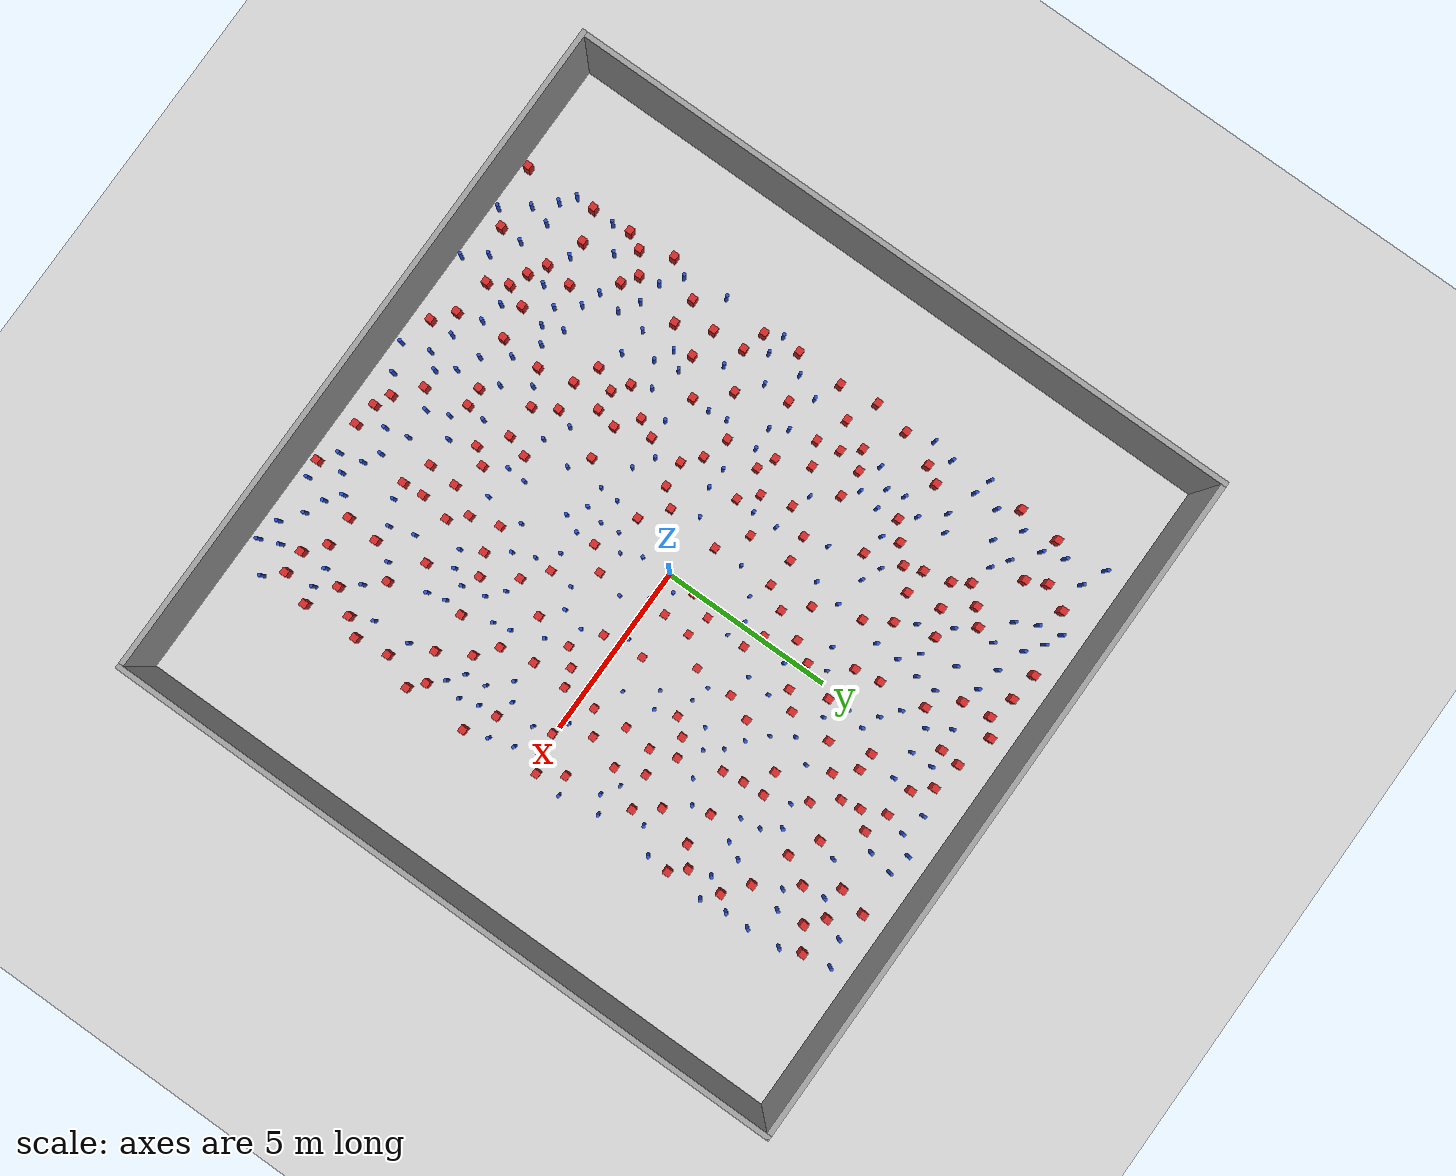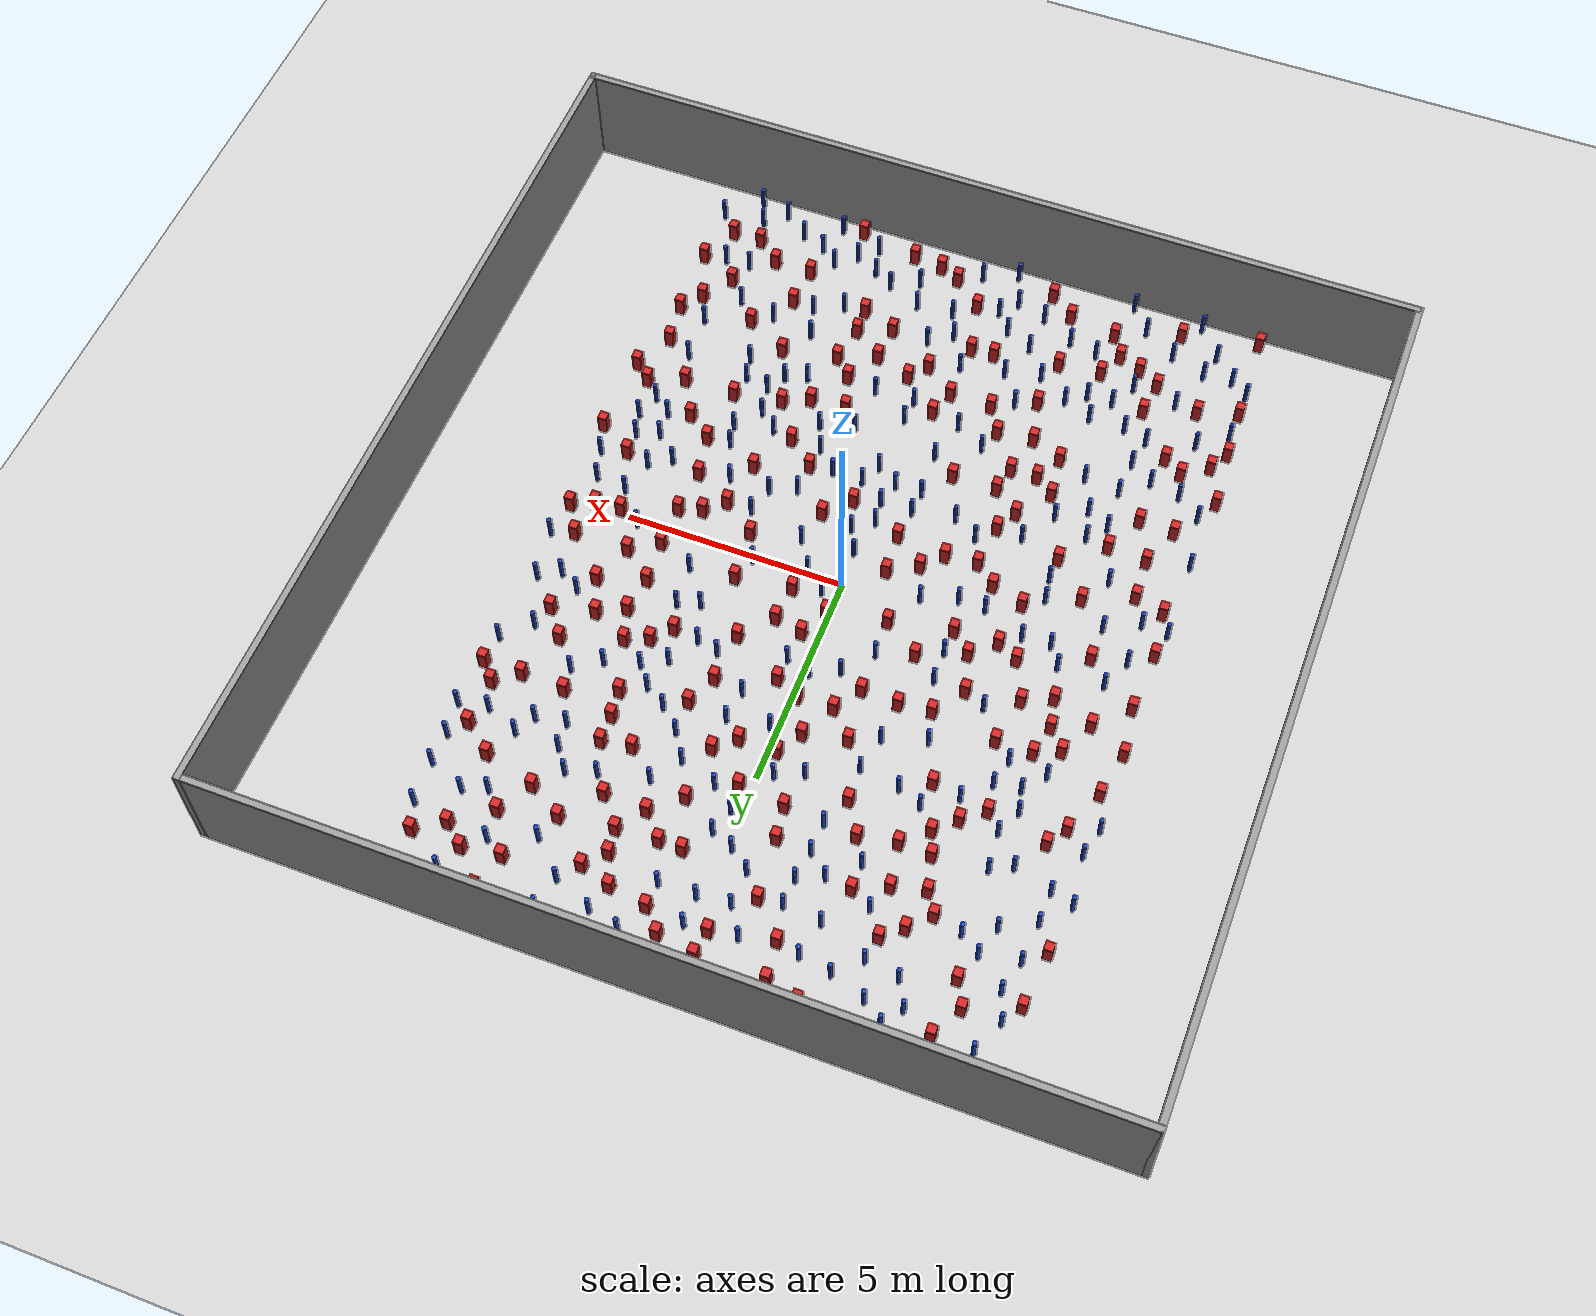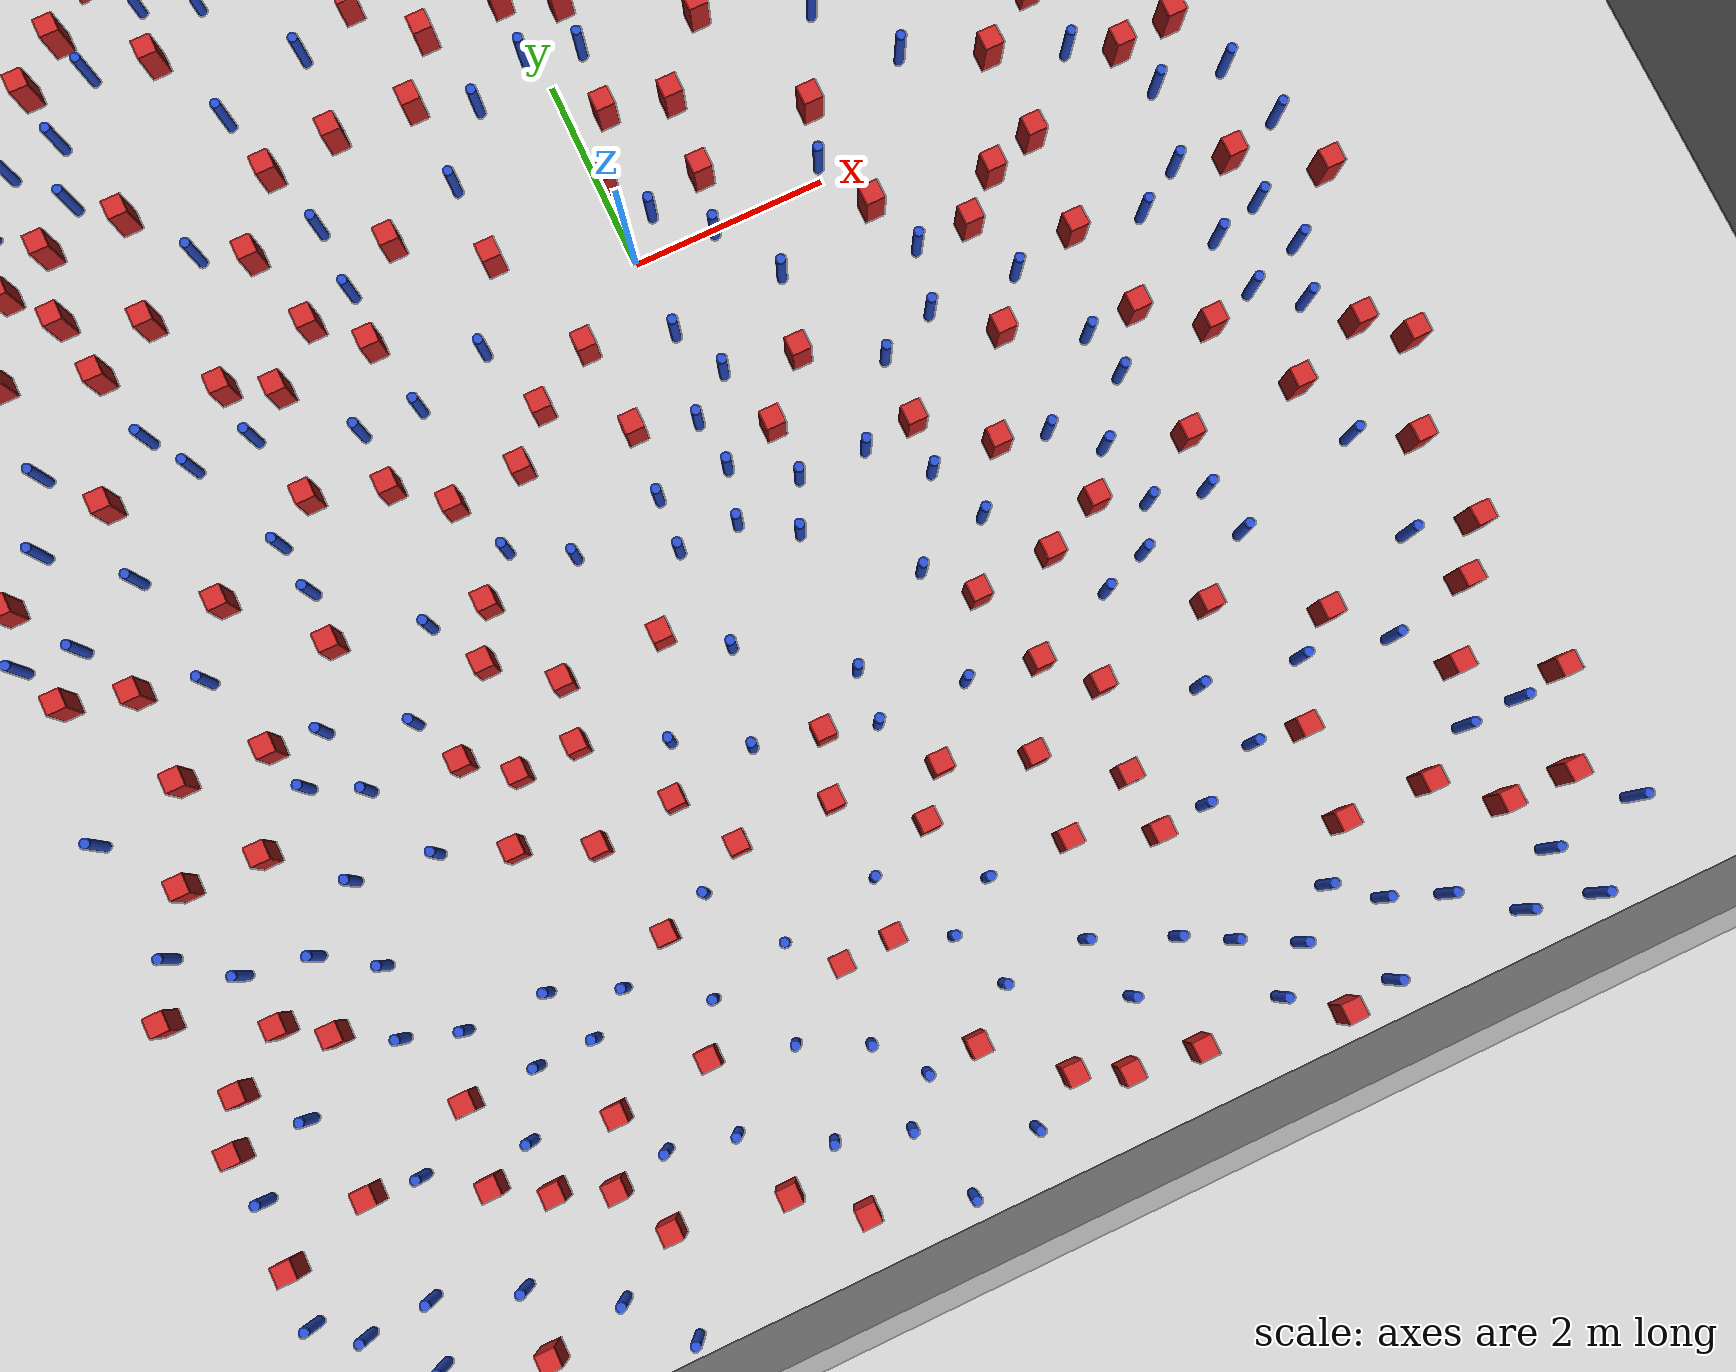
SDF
<sdf version="1.6">
 <world name="default">
  <light name="sun" type="directional">
   <pose>0 0 1000 0 -0 0</pose>
   <diffuse>0.8 0.8 0.8 1</diffuse>
   <specular>0.1 0.1 0.1 1</specular>
   <attenuation>
    <range>1000</range>
    <constant>0.9</constant>
    <linear>0.01</linear>
    <quadratic>0.001</quadratic>
   </attenuation>
   <direction>-0.5 0.5 -1</direction>
  </light>
  <model name="ground_plane">
   <static>1</static>
   <link name="link">
    <collision name="collision">
     <geometry><plane><normal>0 0 1</normal><size>100 100</size></plane></geometry>
     <surface><friction><ode><mu>100</mu><mu2>50</mu2></ode></friction></surface>
    </collision>
    <visual name="visual">
     <cast_shadows>0</cast_shadows>
     <geometry><plane><normal>0 0 1</normal><size>100 100</size></plane></geometry>
     <material>
      <ambient>1.0 1.0 1.0 1.0</ambient>
      <diffuse>0.8 0.8 0.8 1.0</diffuse>
      <specular>0.01 0.01 0.01 1.000000</specular>
     </material>
    </visual>
   </link>
  </model>
  <gravity>0 0 -9.8</gravity>
  <magnetic_field>6e-06 2.3e-05 -4.2e-05</magnetic_field>
  <atmosphere type="adiabatic"/>
  <physics name="default_physics" default="0" type="ode">
   <max_step_size>0.001</max_step_size>
   <real_time_factor>1</real_time_factor>
   <real_time_update_rate>1000</real_time_update_rate>
  </physics>
  <scene><ambient>0.4 0.4 0.4 1</ambient><background>0.7 0.7 0.7 1</background><shadows>1</shadows></scene>
  <spherical_coordinates>
   <surface_model>EARTH_WGS84</surface_model>
   <latitude_deg>0</latitude_deg>
   <longitude_deg>0</longitude_deg>
   <elevation>0</elevation>
   <heading_deg>0</heading_deg>
  </spherical_coordinates>
  <plugin name="gazebo_occupancy_map" filename="libgazebo_2Dmap_plugin.so">
   <map_resolution>0.05</map_resolution>
   <map_topic>generated_map</map_topic>
   <map_height>0.01</map_height>
   <map_size_x>50</map_size_x>
   <map_size_y>50</map_size_y>
  </plugin>
  <model name="NamedLocations">
   <static>true</static>
   <link name="DefaultStart"><pose>8.5 0 0 0 0 3.14</pose></link>
  </model>
  <model name="20x20_walls">
   <pose>0.044518 0.176112 0 0 -0 0</pose>
   <link name="Wall_1">
    <collision name="Wall_1_Collision">
     <geometry><box><size>20 0.15 2.5</size></box></geometry>
     <pose>0 0 1.25 0 -0 0</pose>
    </collision>
    <visual name="Wall_1_Visual">
     <pose>0 0 1.25 0 -0 0</pose>
     <geometry><box><size>20 0.15 2.5</size></box></geometry>
     <material>
      <script><uri>file://media/materials/scripts/gazebo.material</uri><name>Gazebo/Grey</name></script>
      <ambient>0.976471 0.992157 1 1</ambient>
     </material>
     <meta><layer>0</layer></meta>
    </visual>
    <pose>0 9.925 0 0 -0 0</pose>
   </link>
   <link name="Wall_3">
    <collision name="Wall_3_Collision">
     <geometry><box><size>20 0.15 2.5</size></box></geometry>
     <pose>0 0 1.25 0 -0 0</pose>
    </collision>
    <visual name="Wall_3_Visual">
     <pose>0 0 1.25 0 -0 0</pose>
     <geometry><box><size>20 0.15 2.5</size></box></geometry>
     <material>
      <script><uri>file://media/materials/scripts/gazebo.material</uri><name>Gazebo/Grey</name></script>
      <ambient>0.976471 0.992157 1 1</ambient>
     </material>
     <meta><layer>0</layer></meta>
    </visual>
    <pose>9.925 0 0 0 0 -1.5708</pose>
   </link>
   <link name="Wall_4">
    <collision name="Wall_4_Collision">
     <geometry><box><size>20 0.15 2.5</size></box></geometry>
     <pose>0 0 1.25 0 -0 0</pose>
    </collision>
    <visual name="Wall_4_Visual">
     <pose>0 0 1.25 0 -0 0</pose>
     <geometry><box><size>20 0.15 2.5</size></box></geometry>
     <material>
      <script><uri>file://media/materials/scripts/gazebo.material</uri><name>Gazebo/Grey</name></script>
      <ambient>0.976471 0.992157 1 1</ambient>
     </material>
     <meta><layer>0</layer></meta>
    </visual>
    <pose>0 -9.925 0 0 -0 3.14159</pose>
   </link>
   <link name="Wall_5">
    <collision name="Wall_5_Collision">
     <geometry><box><size>20 0.15 2.5</size></box></geometry>
     <pose>0 0 1.25 0 -0 0</pose>
    </collision>
    <visual name="Wall_5_Visual">
     <pose>0 0 1.25 0 -0 0</pose>
     <geometry><box><size>20 0.15 2.5</size></box></geometry>
     <material>
      <script><uri>file://media/materials/scripts/gazebo.material</uri><name>Gazebo/Grey</name></script>
      <ambient>0.976471 0.992157 1 1</ambient>
     </material>
     <meta><layer>0</layer></meta>
    </visual>
    <pose>-9.925 0 0 0 -0 1.5708</pose>
   </link>
   <static>1</static>
  </model>
  <model name="square_post_obstacle0">
   <static>true</static>
   <pose>4.18378343752 6.83594678539 1.91545236811e-07 -7.35059704564e-06 1.12565212e-07 2.39332434364e-05</pose>
   <link name="link">
    <pose>0 0 0.25 0 -0 0</pose>
    <inertial>
     <mass>100</mass>
     <inertia>
      <ixx>0.166667</ixx>
      <ixy>0</ixy>
      <ixz>0</ixz>
      <iyy>0.166667</iyy>
      <iyz>0</iyz>
      <izz>0.166667</izz>
     </inertia>
    </inertial>
    <collision name="collision"><geometry><box><size>.2 .2 .5</size></box></geometry></collision>
    <visual name="visual">
     <geometry><box><size>.2 .2 .5</size></box></geometry>
     <material>
      <script><name>Gazebo/Red</name><uri>file://media/materials/scripts/gazebo.material</uri></script>
     </material>
    </visual>
   </link>
  </model>
  <model name="square_post_obstacle1">
   <static>true</static>
   <pose>-2.65775517127 0.298628384528 1.91545236811e-07 -7.35059704564e-06 1.12565212e-07 2.39332434364e-05</pose>
   <link name="link">
    <pose>0 0 0.25 0 -0 0</pose>
    <inertial>
     <mass>100</mass>
     <inertia>
      <ixx>0.166667</ixx>
      <ixy>0</ixy>
      <ixz>0</ixz>
      <iyy>0.166667</iyy>
      <iyz>0</iyz>
      <izz>0.166667</izz>
     </inertia>
    </inertial>
    <collision name="collision"><geometry><box><size>.2 .2 .5</size></box></geometry></collision>
    <visual name="visual">
     <geometry><box><size>.2 .2 .5</size></box></geometry>
     <material>
      <script><name>Gazebo/Red</name><uri>file://media/materials/scripts/gazebo.material</uri></script>
     </material>
    </visual>
   </link>
  </model>
  <model name="pole_obstacle0">
   <static>true</static>
   <pose>-6.38855358316 -8.19007024415 7.38925637345e-09 -8.471706928e-08 1.24976765081e-08 -1.74513093015e-07</pose>
   <link name="link">
    <pose>0 0 0.3 0 -0 0</pose>
    <inertial>
     <mass>1</mass>
     <inertia><ixx>0.145833</ixx><ixy>0</ixy><ixz>0</ixz><iyy>0.145833</iyy><iyz>0</iyz><izz>0.125</izz></inertia>
    </inertial>
    <collision name="collision">
     <geometry><cylinder><radius>0.05</radius><length>.6</length></cylinder></geometry>
    </collision>
    <visual name="visual">
     <geometry><cylinder><radius>0.05</radius><length>.6</length></cylinder></geometry>
     <material>
      <script><name>Gazebo/Blue</name><uri>file://media/materials/scripts/gazebo.material</uri></script>
     </material>
    </visual>
   </link>
  </model>
  <model name="square_post_obstacle2">
   <static>true</static>
   <pose>4.0908791907 8.49679090564 1.91545236811e-07 -7.35059704564e-06 1.12565212e-07 2.39332434364e-05</pose>
   <link name="link">
    <pose>0 0 0.25 0 -0 0</pose>
    <inertial>
     <mass>100</mass>
     <inertia>
      <ixx>0.166667</ixx>
      <ixy>0</ixy>
      <ixz>0</ixz>
      <iyy>0.166667</iyy>
      <iyz>0</iyz>
      <izz>0.166667</izz>
     </inertia>
    </inertial>
    <collision name="collision"><geometry><box><size>.2 .2 .5</size></box></geometry></collision>
    <visual name="visual">
     <geometry><box><size>.2 .2 .5</size></box></geometry>
     <material>
      <script><name>Gazebo/Red</name><uri>file://media/materials/scripts/gazebo.material</uri></script>
     </material>
    </visual>
   </link>
  </model>
  <model name="pole_obstacle1">
   <static>true</static>
   <pose>1.84656176766 -8.08792494594 7.38925637345e-09 -8.47170692798e-08 1.24976764881e-08 -1.74513093027e-07</pose>
   <link name="link">
    <pose>0 0 0.3 0 -0 0</pose>
    <inertial>
     <mass>1</mass>
     <inertia><ixx>0.145833</ixx><ixy>0</ixy><ixz>0</ixz><iyy>0.145833</iyy><iyz>0</iyz><izz>0.125</izz></inertia>
    </inertial>
    <collision name="collision">
     <geometry><cylinder><radius>0.05</radius><length>.6</length></cylinder></geometry>
    </collision>
    <visual name="visual">
     <geometry><cylinder><radius>0.05</radius><length>.6</length></cylinder></geometry>
     <material>
      <script><name>Gazebo/Blue</name><uri>file://media/materials/scripts/gazebo.material</uri></script>
     </material>
    </visual>
   </link>
  </model>
  <model name="square_post_obstacle3">
   <static>true</static>
   <pose>-0.918401008194 6.17674833115 1.91545236811e-07 -7.35059704564e-06 1.12565212e-07 2.39332434364e-05</pose>
   <link name="link">
    <pose>0 0 0.25 0 -0 0</pose>
    <inertial>
     <mass>100</mass>
     <inertia>
      <ixx>0.166667</ixx>
      <ixy>0</ixy>
      <ixz>0</ixz>
      <iyy>0.166667</iyy>
      <iyz>0</iyz>
      <izz>0.166667</izz>
     </inertia>
    </inertial>
    <collision name="collision"><geometry><box><size>.2 .2 .5</size></box></geometry></collision>
    <visual name="visual">
     <geometry><box><size>.2 .2 .5</size></box></geometry>
     <material>
      <script><name>Gazebo/Red</name><uri>file://media/materials/scripts/gazebo.material</uri></script>
     </material>
    </visual>
   </link>
  </model>
  <model name="pole_obstacle2">
   <static>true</static>
   <pose>-4.92174483459 -5.19918030362 7.38925637345e-09 -8.47170692796e-08 1.24976764786e-08 -1.74513093032e-07</pose>
   <link name="link">
    <pose>0 0 0.3 0 -0 0</pose>
    <inertial>
     <mass>1</mass>
     <inertia><ixx>0.145833</ixx><ixy>0</ixy><ixz>0</ixz><iyy>0.145833</iyy><iyz>0</iyz><izz>0.125</izz></inertia>
    </inertial>
    <collision name="collision">
     <geometry><cylinder><radius>0.05</radius><length>.6</length></cylinder></geometry>
    </collision>
    <visual name="visual">
     <geometry><cylinder><radius>0.05</radius><length>.6</length></cylinder></geometry>
     <material>
      <script><name>Gazebo/Blue</name><uri>file://media/materials/scripts/gazebo.material</uri></script>
     </material>
    </visual>
   </link>
  </model>
  <model name="pole_obstacle3">
   <static>true</static>
   <pose>-1.77367611827 -7.47329240971 7.38925637345e-09 -8.47170692799e-08 1.24976765033e-08 -1.74513093018e-07</pose>
   <link name="link">
    <pose>0 0 0.3 0 -0 0</pose>
    <inertial>
     <mass>1</mass>
     <inertia><ixx>0.145833</ixx><ixy>0</ixy><ixz>0</ixz><iyy>0.145833</iyy><iyz>0</iyz><izz>0.125</izz></inertia>
    </inertial>
    <collision name="collision">
     <geometry><cylinder><radius>0.05</radius><length>.6</length></cylinder></geometry>
    </collision>
    <visual name="visual">
     <geometry><cylinder><radius>0.05</radius><length>.6</length></cylinder></geometry>
     <material>
      <script><name>Gazebo/Blue</name><uri>file://media/materials/scripts/gazebo.material</uri></script>
     </material>
    </visual>
   </link>
  </model>
  <model name="square_post_obstacle4">
   <static>true</static>
   <pose>-5.23449255647 9.01291391849 1.91545236811e-07 -7.35059704564e-06 1.12565212e-07 2.39332434364e-05</pose>
   <link name="link">
    <pose>0 0 0.25 0 -0 0</pose>
    <inertial>
     <mass>100</mass>
     <inertia>
      <ixx>0.166667</ixx>
      <ixy>0</ixy>
      <ixz>0</ixz>
      <iyy>0.166667</iyy>
      <iyz>0</iyz>
      <izz>0.166667</izz>
     </inertia>
    </inertial>
    <collision name="collision"><geometry><box><size>.2 .2 .5</size></box></geometry></collision>
    <visual name="visual">
     <geometry><box><size>.2 .2 .5</size></box></geometry>
     <material>
      <script><name>Gazebo/Red</name><uri>file://media/materials/scripts/gazebo.material</uri></script>
     </material>
    </visual>
   </link>
  </model>
  <model name="square_post_obstacle5">
   <static>true</static>
   <pose>2.09614323917 -6.53388835979 1.91545236811e-07 -7.35059704564e-06 1.12565212e-07 2.39332434364e-05</pose>
   <link name="link">
    <pose>0 0 0.25 0 -0 0</pose>
    <inertial>
     <mass>100</mass>
     <inertia>
      <ixx>0.166667</ixx>
      <ixy>0</ixy>
      <ixz>0</ixz>
      <iyy>0.166667</iyy>
      <iyz>0</iyz>
      <izz>0.166667</izz>
     </inertia>
    </inertial>
    <collision name="collision"><geometry><box><size>.2 .2 .5</size></box></geometry></collision>
    <visual name="visual">
     <geometry><box><size>.2 .2 .5</size></box></geometry>
     <material>
      <script><name>Gazebo/Red</name><uri>file://media/materials/scripts/gazebo.material</uri></script>
     </material>
    </visual>
   </link>
  </model>
  <model name="square_post_obstacle6">
   <static>true</static>
   <pose>2.62487271213 5.29141370215 1.91545236811e-07 -7.35059704564e-06 1.12565212e-07 2.39332434364e-05</pose>
   <link name="link">
    <pose>0 0 0.25 0 -0 0</pose>
    <inertial>
     <mass>100</mass>
     <inertia>
      <ixx>0.166667</ixx>
      <ixy>0</ixy>
      <ixz>0</ixz>
      <iyy>0.166667</iyy>
      <iyz>0</iyz>
      <izz>0.166667</izz>
     </inertia>
    </inertial>
    <collision name="collision"><geometry><box><size>.2 .2 .5</size></box></geometry></collision>
    <visual name="visual">
     <geometry><box><size>.2 .2 .5</size></box></geometry>
     <material>
      <script><name>Gazebo/Red</name><uri>file://media/materials/scripts/gazebo.material</uri></script>
     </material>
    </visual>
   </link>
  </model>
  <model name="pole_obstacle4">
   <static>true</static>
   <pose>-0.623896002527 7.06503482538 7.38925637345e-09 -8.471706928e-08 1.24976765086e-08 -1.74513093015e-07</pose>
   <link name="link">
    <pose>0 0 0.3 0 -0 0</pose>
    <inertial>
     <mass>1</mass>
     <inertia><ixx>0.145833</ixx><ixy>0</ixy><ixz>0</ixz><iyy>0.145833</iyy><iyz>0</iyz><izz>0.125</izz></inertia>
    </inertial>
    <collision name="collision">
     <geometry><cylinder><radius>0.05</radius><length>.6</length></cylinder></geometry>
    </collision>
    <visual name="visual">
     <geometry><cylinder><radius>0.05</radius><length>.6</length></cylinder></geometry>
     <material>
      <script><name>Gazebo/Blue</name><uri>file://media/materials/scripts/gazebo.material</uri></script>
     </material>
    </visual>
   </link>
  </model>
  <model name="pole_obstacle5">
   <static>true</static>
   <pose>4.59534983263 4.0228984966 7.38925637345e-09 -8.47170692797e-08 1.24976764805e-08 -1.74513093031e-07</pose>
   <link name="link">
    <pose>0 0 0.3 0 -0 0</pose>
    <inertial>
     <mass>1</mass>
     <inertia><ixx>0.145833</ixx><ixy>0</ixy><ixz>0</ixz><iyy>0.145833</iyy><iyz>0</iyz><izz>0.125</izz></inertia>
    </inertial>
    <collision name="collision">
     <geometry><cylinder><radius>0.05</radius><length>.6</length></cylinder></geometry>
    </collision>
    <visual name="visual">
     <geometry><cylinder><radius>0.05</radius><length>.6</length></cylinder></geometry>
     <material>
      <script><name>Gazebo/Blue</name><uri>file://media/materials/scripts/gazebo.material</uri></script>
     </material>
    </visual>
   </link>
  </model>
  <model name="square_post_obstacle7">
   <static>true</static>
   <pose>-0.259969756508 -8.18840143849 1.91545236811e-07 -7.35059704564e-06 1.12565212e-07 2.39332434364e-05</pose>
   <link name="link">
    <pose>0 0 0.25 0 -0 0</pose>
    <inertial>
     <mass>100</mass>
     <inertia>
      <ixx>0.166667</ixx>
      <ixy>0</ixy>
      <ixz>0</ixz>
      <iyy>0.166667</iyy>
      <iyz>0</iyz>
      <izz>0.166667</izz>
     </inertia>
    </inertial>
    <collision name="collision"><geometry><box><size>.2 .2 .5</size></box></geometry></collision>
    <visual name="visual">
     <geometry><box><size>.2 .2 .5</size></box></geometry>
     <material>
      <script><name>Gazebo/Red</name><uri>file://media/materials/scripts/gazebo.material</uri></script>
     </material>
    </visual>
   </link>
  </model>
  <model name="square_post_obstacle8">
   <static>true</static>
   <pose>-3.50885296934 -3.76705480236 1.91545236811e-07 -7.35059704564e-06 1.12565212e-07 2.39332434364e-05</pose>
   <link name="link">
    <pose>0 0 0.25 0 -0 0</pose>
    <inertial>
     <mass>100</mass>
     <inertia>
      <ixx>0.166667</ixx>
      <ixy>0</ixy>
      <ixz>0</ixz>
      <iyy>0.166667</iyy>
      <iyz>0</iyz>
      <izz>0.166667</izz>
     </inertia>
    </inertial>
    <collision name="collision"><geometry><box><size>.2 .2 .5</size></box></geometry></collision>
    <visual name="visual">
     <geometry><box><size>.2 .2 .5</size></box></geometry>
     <material>
      <script><name>Gazebo/Red</name><uri>file://media/materials/scripts/gazebo.material</uri></script>
     </material>
    </visual>
   </link>
  </model>
  <model name="pole_obstacle6">
   <static>true</static>
   <pose>3.64192361207 -2.54882864017 7.38925637345e-09 -8.47170692798e-08 1.24976764939e-08 -1.74513093025e-07</pose>
   <link name="link">
    <pose>0 0 0.3 0 -0 0</pose>
    <inertial>
     <mass>1</mass>
     <inertia><ixx>0.145833</ixx><ixy>0</ixy><ixz>0</ixz><iyy>0.145833</iyy><iyz>0</iyz><izz>0.125</izz></inertia>
    </inertial>
    <collision name="collision">
     <geometry><cylinder><radius>0.05</radius><length>.6</length></cylinder></geometry>
    </collision>
    <visual name="visual">
     <geometry><cylinder><radius>0.05</radius><length>.6</length></cylinder></geometry>
     <material>
      <script><name>Gazebo/Blue</name><uri>file://media/materials/scripts/gazebo.material</uri></script>
     </material>
    </visual>
   </link>
  </model>
  <model name="pole_obstacle7">
   <static>true</static>
   <pose>4.0634409271 -6.24032511212 7.38925637345e-09 -8.47170692796e-08 1.24976764786e-08 -1.74513093032e-07</pose>
   <link name="link">
    <pose>0 0 0.3 0 -0 0</pose>
    <inertial>
     <mass>1</mass>
     <inertia><ixx>0.145833</ixx><ixy>0</ixy><ixz>0</ixz><iyy>0.145833</iyy><iyz>0</iyz><izz>0.125</izz></inertia>
    </inertial>
    <collision name="collision">
     <geometry><cylinder><radius>0.05</radius><length>.6</length></cylinder></geometry>
    </collision>
    <visual name="visual">
     <geometry><cylinder><radius>0.05</radius><length>.6</length></cylinder></geometry>
     <material>
      <script><name>Gazebo/Blue</name><uri>file://media/materials/scripts/gazebo.material</uri></script>
     </material>
    </visual>
   </link>
  </model>
  <model name="square_post_obstacle9">
   <static>true</static>
   <pose>5.85793172006 -8.27280279421 1.91545236811e-07 -7.35059704564e-06 1.12565212e-07 2.39332434364e-05</pose>
   <link name="link">
    <pose>0 0 0.25 0 -0 0</pose>
    <inertial>
     <mass>100</mass>
     <inertia>
      <ixx>0.166667</ixx>
      <ixy>0</ixy>
      <ixz>0</ixz>
      <iyy>0.166667</iyy>
      <iyz>0</iyz>
      <izz>0.166667</izz>
     </inertia>
    </inertial>
    <collision name="collision"><geometry><box><size>.2 .2 .5</size></box></geometry></collision>
    <visual name="visual">
     <geometry><box><size>.2 .2 .5</size></box></geometry>
     <material>
      <script><name>Gazebo/Red</name><uri>file://media/materials/scripts/gazebo.material</uri></script>
     </material>
    </visual>
   </link>
  </model>
  <model name="square_post_obstacle10">
   <static>true</static>
   <pose>5.36092422646 -6.9205437314 1.91545236811e-07 -7.35059704564e-06 1.12565212e-07 2.39332434364e-05</pose>
   <link name="link">
    <pose>0 0 0.25 0 -0 0</pose>
    <inertial>
     <mass>100</mass>
     <inertia>
      <ixx>0.166667</ixx>
      <ixy>0</ixy>
      <ixz>0</ixz>
      <iyy>0.166667</iyy>
      <iyz>0</iyz>
      <izz>0.166667</izz>
     </inertia>
    </inertial>
    <collision name="collision"><geometry><box><size>.2 .2 .5</size></box></geometry></collision>
    <visual name="visual">
     <geometry><box><size>.2 .2 .5</size></box></geometry>
     <material>
      <script><name>Gazebo/Red</name><uri>file://media/materials/scripts/gazebo.material</uri></script>
     </material>
    </visual>
   </link>
  </model>
  <model name="square_post_obstacle11">
   <static>true</static>
   <pose>0.240388420057 5.33074319802 1.91545236811e-07 -7.35059704564e-06 1.12565212e-07 2.39332434364e-05</pose>
   <link name="link">
    <pose>0 0 0.25 0 -0 0</pose>
    <inertial>
     <mass>100</mass>
     <inertia>
      <ixx>0.166667</ixx>
      <ixy>0</ixy>
      <ixz>0</ixz>
      <iyy>0.166667</iyy>
      <iyz>0</iyz>
      <izz>0.166667</izz>
     </inertia>
    </inertial>
    <collision name="collision"><geometry><box><size>.2 .2 .5</size></box></geometry></collision>
    <visual name="visual">
     <geometry><box><size>.2 .2 .5</size></box></geometry>
     <material>
      <script><name>Gazebo/Red</name><uri>file://media/materials/scripts/gazebo.material</uri></script>
     </material>
    </visual>
   </link>
  </model>
  <model name="square_post_obstacle12">
   <static>true</static>
   <pose>1.9486642513 3.89404540649 1.91545236811e-07 -7.35059704564e-06 1.12565212e-07 2.39332434364e-05</pose>
   <link name="link">
    <pose>0 0 0.25 0 -0 0</pose>
    <inertial>
     <mass>100</mass>
     <inertia>
      <ixx>0.166667</ixx>
      <ixy>0</ixy>
      <ixz>0</ixz>
      <iyy>0.166667</iyy>
      <iyz>0</iyz>
      <izz>0.166667</izz>
     </inertia>
    </inertial>
    <collision name="collision"><geometry><box><size>.2 .2 .5</size></box></geometry></collision>
    <visual name="visual">
     <geometry><box><size>.2 .2 .5</size></box></geometry>
     <material>
      <script><name>Gazebo/Red</name><uri>file://media/materials/scripts/gazebo.material</uri></script>
     </material>
    </visual>
   </link>
  </model>
  <model name="square_post_obstacle13">
   <static>true</static>
   <pose>-4.16992679024 -2.21531199736 1.91545236811e-07 -7.35059704564e-06 1.12565212e-07 2.39332434364e-05</pose>
   <link name="link">
    <pose>0 0 0.25 0 -0 0</pose>
    <inertial>
     <mass>100</mass>
     <inertia>
      <ixx>0.166667</ixx>
      <ixy>0</ixy>
      <ixz>0</ixz>
      <iyy>0.166667</iyy>
      <iyz>0</iyz>
      <izz>0.166667</izz>
     </inertia>
    </inertial>
    <collision name="collision"><geometry><box><size>.2 .2 .5</size></box></geometry></collision>
    <visual name="visual">
     <geometry><box><size>.2 .2 .5</size></box></geometry>
     <material>
      <script><name>Gazebo/Red</name><uri>file://media/materials/scripts/gazebo.material</uri></script>
     </material>
    </visual>
   </link>
  </model>
  <model name="pole_obstacle8">
   <static>true</static>
   <pose>3.30957384322 -8.24945911556 7.38925637345e-09 -8.47170692793e-08 1.24976764408e-08 -1.74513093041e-07</pose>
   <link name="link">
    <pose>0 0 0.3 0 -0 0</pose>
    <inertial>
     <mass>1</mass>
     <inertia><ixx>0.145833</ixx><ixy>0</ixy><ixz>0</ixz><iyy>0.145833</iyy><iyz>0</iyz><izz>0.125</izz></inertia>
    </inertial>
    <collision name="collision">
     <geometry><cylinder><radius>0.05</radius><length>.6</length></cylinder></geometry>
    </collision>
    <visual name="visual">
     <geometry><cylinder><radius>0.05</radius><length>.6</length></cylinder></geometry>
     <material>
      <script><name>Gazebo/Blue</name><uri>file://media/materials/scripts/gazebo.material</uri></script>
     </material>
    </visual>
   </link>
  </model>
  <model name="square_post_obstacle14">
   <static>true</static>
   <pose>-1.079137791 -6.99237156934 1.91545236811e-07 -7.35059704564e-06 1.12565212e-07 2.39332434364e-05</pose>
   <link name="link">
    <pose>0 0 0.25 0 -0 0</pose>
    <inertial>
     <mass>100</mass>
     <inertia>
      <ixx>0.166667</ixx>
      <ixy>0</ixy>
      <ixz>0</ixz>
      <iyy>0.166667</iyy>
      <iyz>0</iyz>
      <izz>0.166667</izz>
     </inertia>
    </inertial>
    <collision name="collision"><geometry><box><size>.2 .2 .5</size></box></geometry></collision>
    <visual name="visual">
     <geometry><box><size>.2 .2 .5</size></box></geometry>
     <material>
      <script><name>Gazebo/Red</name><uri>file://media/materials/scripts/gazebo.material</uri></script>
     </material>
    </visual>
   </link>
  </model>
  <model name="square_post_obstacle15">
   <static>true</static>
   <pose>-0.932526725977 2.9677390461 1.91545236811e-07 -7.35059704564e-06 1.12565212e-07 2.39332434364e-05</pose>
   <link name="link">
    <pose>0 0 0.25 0 -0 0</pose>
    <inertial>
     <mass>100</mass>
     <inertia>
      <ixx>0.166667</ixx>
      <ixy>0</ixy>
      <ixz>0</ixz>
      <iyy>0.166667</iyy>
      <iyz>0</iyz>
      <izz>0.166667</izz>
     </inertia>
    </inertial>
    <collision name="collision"><geometry><box><size>.2 .2 .5</size></box></geometry></collision>
    <visual name="visual">
     <geometry><box><size>.2 .2 .5</size></box></geometry>
     <material>
      <script><name>Gazebo/Red</name><uri>file://media/materials/scripts/gazebo.material</uri></script>
     </material>
    </visual>
   </link>
  </model>
  <model name="square_post_obstacle16">
   <static>true</static>
   <pose>-6.69590890887 7.84037955115 1.91545236811e-07 -7.35059704564e-06 1.12565212e-07 2.39332434364e-05</pose>
   <link name="link">
    <pose>0 0 0.25 0 -0 0</pose>
    <inertial>
     <mass>100</mass>
     <inertia>
      <ixx>0.166667</ixx>
      <ixy>0</ixy>
      <ixz>0</ixz>
      <iyy>0.166667</iyy>
      <iyz>0</iyz>
      <izz>0.166667</izz>
     </inertia>
    </inertial>
    <collision name="collision"><geometry><box><size>.2 .2 .5</size></box></geometry></collision>
    <visual name="visual">
     <geometry><box><size>.2 .2 .5</size></box></geometry>
     <material>
      <script><name>Gazebo/Red</name><uri>file://media/materials/scripts/gazebo.material</uri></script>
     </material>
    </visual>
   </link>
  </model>
  <model name="pole_obstacle9">
   <static>true</static>
   <pose>-5.08694028577 6.80690436211 7.38925637345e-09 -8.47170692796e-08 1.24976764786e-08 -1.74513093032e-07</pose>
   <link name="link">
    <pose>0 0 0.3 0 -0 0</pose>
    <inertial>
     <mass>1</mass>
     <inertia><ixx>0.145833</ixx><ixy>0</ixy><ixz>0</ixz><iyy>0.145833</iyy><iyz>0</iyz><izz>0.125</izz></inertia>
    </inertial>
    <collision name="collision">
     <geometry><cylinder><radius>0.05</radius><length>.6</length></cylinder></geometry>
    </collision>
    <visual name="visual">
     <geometry><cylinder><radius>0.05</radius><length>.6</length></cylinder></geometry>
     <material>
      <script><name>Gazebo/Blue</name><uri>file://media/materials/scripts/gazebo.material</uri></script>
     </material>
    </visual>
   </link>
  </model>
  <model name="square_post_obstacle17">
   <static>true</static>
   <pose>5.48721667953 4.50802966469 1.91545236811e-07 -7.35059704564e-06 1.12565212e-07 2.39332434364e-05</pose>
   <link name="link">
    <pose>0 0 0.25 0 -0 0</pose>
    <inertial>
     <mass>100</mass>
     <inertia>
      <ixx>0.166667</ixx>
      <ixy>0</ixy>
      <ixz>0</ixz>
      <iyy>0.166667</iyy>
      <iyz>0</iyz>
      <izz>0.166667</izz>
     </inertia>
    </inertial>
    <collision name="collision"><geometry><box><size>.2 .2 .5</size></box></geometry></collision>
    <visual name="visual">
     <geometry><box><size>.2 .2 .5</size></box></geometry>
     <material>
      <script><name>Gazebo/Red</name><uri>file://media/materials/scripts/gazebo.material</uri></script>
     </material>
    </visual>
   </link>
  </model>
  <model name="square_post_obstacle18">
   <static>true</static>
   <pose>4.50338744561 4.55315479538 1.91545236811e-07 -7.35059704564e-06 1.12565212e-07 2.39332434364e-05</pose>
   <link name="link">
    <pose>0 0 0.25 0 -0 0</pose>
    <inertial>
     <mass>100</mass>
     <inertia>
      <ixx>0.166667</ixx>
      <ixy>0</ixy>
      <ixz>0</ixz>
      <iyy>0.166667</iyy>
      <iyz>0</iyz>
      <izz>0.166667</izz>
     </inertia>
    </inertial>
    <collision name="collision"><geometry><box><size>.2 .2 .5</size></box></geometry></collision>
    <visual name="visual">
     <geometry><box><size>.2 .2 .5</size></box></geometry>
     <material>
      <script><name>Gazebo/Red</name><uri>file://media/materials/scripts/gazebo.material</uri></script>
     </material>
    </visual>
   </link>
  </model>
  <model name="pole_obstacle10">
   <static>true</static>
   <pose>-3.68967531509 -9.48082544224 7.38925637345e-09 -8.47170692793e-08 1.24976764408e-08 -1.74513093041e-07</pose>
   <link name="link">
    <pose>0 0 0.3 0 -0 0</pose>
    <inertial>
     <mass>1</mass>
     <inertia><ixx>0.145833</ixx><ixy>0</ixy><ixz>0</ixz><iyy>0.145833</iyy><iyz>0</iyz><izz>0.125</izz></inertia>
    </inertial>
    <collision name="collision">
     <geometry><cylinder><radius>0.05</radius><length>.6</length></cylinder></geometry>
    </collision>
    <visual name="visual">
     <geometry><cylinder><radius>0.05</radius><length>.6</length></cylinder></geometry>
     <material>
      <script><name>Gazebo/Blue</name><uri>file://media/materials/scripts/gazebo.material</uri></script>
     </material>
    </visual>
   </link>
  </model>
  <model name="square_post_obstacle19">
   <static>true</static>
   <pose>-6.7253337797 2.91687751709 1.91545236811e-07 -7.35059704564e-06 1.12565212e-07 2.39332434364e-05</pose>
   <link name="link">
    <pose>0 0 0.25 0 -0 0</pose>
    <inertial>
     <mass>100</mass>
     <inertia>
      <ixx>0.166667</ixx>
      <ixy>0</ixy>
      <ixz>0</ixz>
      <iyy>0.166667</iyy>
      <iyz>0</iyz>
      <izz>0.166667</izz>
     </inertia>
    </inertial>
    <collision name="collision"><geometry><box><size>.2 .2 .5</size></box></geometry></collision>
    <visual name="visual">
     <geometry><box><size>.2 .2 .5</size></box></geometry>
     <material>
      <script><name>Gazebo/Red</name><uri>file://media/materials/scripts/gazebo.material</uri></script>
     </material>
    </visual>
   </link>
  </model>
  <model name="pole_obstacle11">
   <static>true</static>
   <pose>-1.28398703065 1.41821444295 7.38925637345e-09 -8.471706928e-08 1.24976765079e-08 -1.74513093017e-07</pose>
   <link name="link">
    <pose>0 0 0.3 0 -0 0</pose>
    <inertial>
     <mass>1</mass>
     <inertia><ixx>0.145833</ixx><ixy>0</ixy><ixz>0</ixz><iyy>0.145833</iyy><iyz>0</iyz><izz>0.125</izz></inertia>
    </inertial>
    <collision name="collision">
     <geometry><cylinder><radius>0.05</radius><length>.6</length></cylinder></geometry>
    </collision>
    <visual name="visual">
     <geometry><cylinder><radius>0.05</radius><length>.6</length></cylinder></geometry>
     <material>
      <script><name>Gazebo/Blue</name><uri>file://media/materials/scripts/gazebo.material</uri></script>
     </material>
    </visual>
   </link>
  </model>
  <model name="square_post_obstacle20">
   <static>true</static>
   <pose>-2.93497238038 -3.01322514498 1.91545236811e-07 -7.35059704564e-06 1.12565212e-07 2.39332434364e-05</pose>
   <link name="link">
    <pose>0 0 0.25 0 -0 0</pose>
    <inertial>
     <mass>100</mass>
     <inertia>
      <ixx>0.166667</ixx>
      <ixy>0</ixy>
      <ixz>0</ixz>
      <iyy>0.166667</iyy>
      <iyz>0</iyz>
      <izz>0.166667</izz>
     </inertia>
    </inertial>
    <collision name="collision"><geometry><box><size>.2 .2 .5</size></box></geometry></collision>
    <visual name="visual">
     <geometry><box><size>.2 .2 .5</size></box></geometry>
     <material>
      <script><name>Gazebo/Red</name><uri>file://media/materials/scripts/gazebo.material</uri></script>
     </material>
    </visual>
   </link>
  </model>
  <model name="pole_obstacle12">
   <static>true</static>
   <pose>5.3391453261 -8.83431896908 7.38925637345e-09 -8.471706928e-08 1.24976765081e-08 -1.74513093015e-07</pose>
   <link name="link">
    <pose>0 0 0.3 0 -0 0</pose>
    <inertial>
     <mass>1</mass>
     <inertia><ixx>0.145833</ixx><ixy>0</ixy><ixz>0</ixz><iyy>0.145833</iyy><iyz>0</iyz><izz>0.125</izz></inertia>
    </inertial>
    <collision name="collision">
     <geometry><cylinder><radius>0.05</radius><length>.6</length></cylinder></geometry>
    </collision>
    <visual name="visual">
     <geometry><cylinder><radius>0.05</radius><length>.6</length></cylinder></geometry>
     <material>
      <script><name>Gazebo/Blue</name><uri>file://media/materials/scripts/gazebo.material</uri></script>
     </material>
    </visual>
   </link>
  </model>
  <model name="square_post_obstacle21">
   <static>true</static>
   <pose>-2.15206947412 2.39921926246 1.91545236811e-07 -7.35059704564e-06 1.12565212e-07 2.39332434364e-05</pose>
   <link name="link">
    <pose>0 0 0.25 0 -0 0</pose>
    <inertial>
     <mass>100</mass>
     <inertia>
      <ixx>0.166667</ixx>
      <ixy>0</ixy>
      <ixz>0</ixz>
      <iyy>0.166667</iyy>
      <iyz>0</iyz>
      <izz>0.166667</izz>
     </inertia>
    </inertial>
    <collision name="collision"><geometry><box><size>.2 .2 .5</size></box></geometry></collision>
    <visual name="visual">
     <geometry><box><size>.2 .2 .5</size></box></geometry>
     <material>
      <script><name>Gazebo/Red</name><uri>file://media/materials/scripts/gazebo.material</uri></script>
     </material>
    </visual>
   </link>
  </model>
  <model name="pole_obstacle13">
   <static>true</static>
   <pose>-5.36995046791 -2.05261547743 7.38925637345e-09 -8.47170692798e-08 1.24976764937e-08 -1.74513093023e-07</pose>
   <link name="link">
    <pose>0 0 0.3 0 -0 0</pose>
    <inertial>
     <mass>1</mass>
     <inertia><ixx>0.145833</ixx><ixy>0</ixy><ixz>0</ixz><iyy>0.145833</iyy><iyz>0</iyz><izz>0.125</izz></inertia>
    </inertial>
    <collision name="collision">
     <geometry><cylinder><radius>0.05</radius><length>.6</length></cylinder></geometry>
    </collision>
    <visual name="visual">
     <geometry><cylinder><radius>0.05</radius><length>.6</length></cylinder></geometry>
     <material>
      <script><name>Gazebo/Blue</name><uri>file://media/materials/scripts/gazebo.material</uri></script>
     </material>
    </visual>
   </link>
  </model>
  <model name="square_post_obstacle22">
   <static>true</static>
   <pose>-1.38829633164 9.39031996727 1.91545236811e-07 -7.35059704564e-06 1.12565212e-07 2.39332434364e-05</pose>
   <link name="link">
    <pose>0 0 0.25 0 -0 0</pose>
    <inertial>
     <mass>100</mass>
     <inertia>
      <ixx>0.166667</ixx>
      <ixy>0</ixy>
      <ixz>0</ixz>
      <iyy>0.166667</iyy>
      <iyz>0</iyz>
      <izz>0.166667</izz>
     </inertia>
    </inertial>
    <collision name="collision"><geometry><box><size>.2 .2 .5</size></box></geometry></collision>
    <visual name="visual">
     <geometry><box><size>.2 .2 .5</size></box></geometry>
     <material>
      <script><name>Gazebo/Red</name><uri>file://media/materials/scripts/gazebo.material</uri></script>
     </material>
    </visual>
   </link>
  </model>
  <model name="pole_obstacle14">
   <static>true</static>
   <pose>-2.30070272492 -2.10515329835 7.38925637345e-09 -8.47170692798e-08 1.24976764939e-08 -1.74513093025e-07</pose>
   <link name="link">
    <pose>0 0 0.3 0 -0 0</pose>
    <inertial>
     <mass>1</mass>
     <inertia><ixx>0.145833</ixx><ixy>0</ixy><ixz>0</ixz><iyy>0.145833</iyy><iyz>0</iyz><izz>0.125</izz></inertia>
    </inertial>
    <collision name="collision">
     <geometry><cylinder><radius>0.05</radius><length>.6</length></cylinder></geometry>
    </collision>
    <visual name="visual">
     <geometry><cylinder><radius>0.05</radius><length>.6</length></cylinder></geometry>
     <material>
      <script><name>Gazebo/Blue</name><uri>file://media/materials/scripts/gazebo.material</uri></script>
     </material>
    </visual>
   </link>
  </model>
  <model name="pole_obstacle15">
   <static>true</static>
   <pose>-2.41591872018 7.57751806463 7.38925637345e-09 -8.47170692798e-08 1.24976765033e-08 -1.74513093019e-07</pose>
   <link name="link">
    <pose>0 0 0.3 0 -0 0</pose>
    <inertial>
     <mass>1</mass>
     <inertia><ixx>0.145833</ixx><ixy>0</ixy><ixz>0</ixz><iyy>0.145833</iyy><iyz>0</iyz><izz>0.125</izz></inertia>
    </inertial>
    <collision name="collision">
     <geometry><cylinder><radius>0.05</radius><length>.6</length></cylinder></geometry>
    </collision>
    <visual name="visual">
     <geometry><cylinder><radius>0.05</radius><length>.6</length></cylinder></geometry>
     <material>
      <script><name>Gazebo/Blue</name><uri>file://media/materials/scripts/gazebo.material</uri></script>
     </material>
    </visual>
   </link>
  </model>
  <model name="pole_obstacle16">
   <static>true</static>
   <pose>-1.82667973989 -8.42245402673 7.38925637345e-09 -8.47170692798e-08 1.24976764881e-08 -1.74513093027e-07</pose>
   <link name="link">
    <pose>0 0 0.3 0 -0 0</pose>
    <inertial>
     <mass>1</mass>
     <inertia><ixx>0.145833</ixx><ixy>0</ixy><ixz>0</ixz><iyy>0.145833</iyy><iyz>0</iyz><izz>0.125</izz></inertia>
    </inertial>
    <collision name="collision">
     <geometry><cylinder><radius>0.05</radius><length>.6</length></cylinder></geometry>
    </collision>
    <visual name="visual">
     <geometry><cylinder><radius>0.05</radius><length>.6</length></cylinder></geometry>
     <material>
      <script><name>Gazebo/Blue</name><uri>file://media/materials/scripts/gazebo.material</uri></script>
     </material>
    </visual>
   </link>
  </model>
  <model name="square_post_obstacle23">
   <static>true</static>
   <pose>2.31536893464 -0.469810561932 1.91545236811e-07 -7.35059704564e-06 1.12565212e-07 2.39332434364e-05</pose>
   <link name="link">
    <pose>0 0 0.25 0 -0 0</pose>
    <inertial>
     <mass>100</mass>
     <inertia>
      <ixx>0.166667</ixx>
      <ixy>0</ixy>
      <ixz>0</ixz>
      <iyy>0.166667</iyy>
      <iyz>0</iyz>
      <izz>0.166667</izz>
     </inertia>
    </inertial>
    <collision name="collision"><geometry><box><size>.2 .2 .5</size></box></geometry></collision>
    <visual name="visual">
     <geometry><box><size>.2 .2 .5</size></box></geometry>
     <material>
      <script><name>Gazebo/Red</name><uri>file://media/materials/scripts/gazebo.material</uri></script>
     </material>
    </visual>
   </link>
  </model>
  <model name="pole_obstacle17">
   <static>true</static>
   <pose>2.30554568047 -8.33789210548 7.38925637345e-09 -8.47170692793e-08 1.24976764408e-08 -1.74513093041e-07</pose>
   <link name="link">
    <pose>0 0 0.3 0 -0 0</pose>
    <inertial>
     <mass>1</mass>
     <inertia><ixx>0.145833</ixx><ixy>0</ixy><ixz>0</ixz><iyy>0.145833</iyy><iyz>0</iyz><izz>0.125</izz></inertia>
    </inertial>
    <collision name="collision">
     <geometry><cylinder><radius>0.05</radius><length>.6</length></cylinder></geometry>
    </collision>
    <visual name="visual">
     <geometry><cylinder><radius>0.05</radius><length>.6</length></cylinder></geometry>
     <material>
      <script><name>Gazebo/Blue</name><uri>file://media/materials/scripts/gazebo.material</uri></script>
     </material>
    </visual>
   </link>
  </model>
  <model name="square_post_obstacle24">
   <static>true</static>
   <pose>-1.85153027986 -4.93886895297 1.91545236811e-07 -7.35059704564e-06 1.12565212e-07 2.39332434364e-05</pose>
   <link name="link">
    <pose>0 0 0.25 0 -0 0</pose>
    <inertial>
     <mass>100</mass>
     <inertia>
      <ixx>0.166667</ixx>
      <ixy>0</ixy>
      <ixz>0</ixz>
      <iyy>0.166667</iyy>
      <iyz>0</iyz>
      <izz>0.166667</izz>
     </inertia>
    </inertial>
    <collision name="collision"><geometry><box><size>.2 .2 .5</size></box></geometry></collision>
    <visual name="visual">
     <geometry><box><size>.2 .2 .5</size></box></geometry>
     <material>
      <script><name>Gazebo/Red</name><uri>file://media/materials/scripts/gazebo.material</uri></script>
     </material>
    </visual>
   </link>
  </model>
  <model name="square_post_obstacle25">
   <static>true</static>
   <pose>5.42968724935 8.2010481353 1.91545236811e-07 -7.35059704564e-06 1.12565212e-07 2.39332434364e-05</pose>
   <link name="link">
    <pose>0 0 0.25 0 -0 0</pose>
    <inertial>
     <mass>100</mass>
     <inertia>
      <ixx>0.166667</ixx>
      <ixy>0</ixy>
      <ixz>0</ixz>
      <iyy>0.166667</iyy>
      <iyz>0</iyz>
      <izz>0.166667</izz>
     </inertia>
    </inertial>
    <collision name="collision"><geometry><box><size>.2 .2 .5</size></box></geometry></collision>
    <visual name="visual">
     <geometry><box><size>.2 .2 .5</size></box></geometry>
     <material>
      <script><name>Gazebo/Red</name><uri>file://media/materials/scripts/gazebo.material</uri></script>
     </material>
    </visual>
   </link>
  </model>
  <model name="square_post_obstacle26">
   <static>true</static>
   <pose>-5.68889429534 2.25094203357 1.91545236811e-07 -7.35059704564e-06 1.12565212e-07 2.39332434364e-05</pose>
   <link name="link">
    <pose>0 0 0.25 0 -0 0</pose>
    <inertial>
     <mass>100</mass>
     <inertia>
      <ixx>0.166667</ixx>
      <ixy>0</ixy>
      <ixz>0</ixz>
      <iyy>0.166667</iyy>
      <iyz>0</iyz>
      <izz>0.166667</izz>
     </inertia>
    </inertial>
    <collision name="collision"><geometry><box><size>.2 .2 .5</size></box></geometry></collision>
    <visual name="visual">
     <geometry><box><size>.2 .2 .5</size></box></geometry>
     <material>
      <script><name>Gazebo/Red</name><uri>file://media/materials/scripts/gazebo.material</uri></script>
     </material>
    </visual>
   </link>
  </model>
  <model name="square_post_obstacle27">
   <static>true</static>
   <pose>-4.52512040629 1.41693718209 1.91545236811e-07 -7.35059704564e-06 1.12565212e-07 2.39332434364e-05</pose>
   <link name="link">
    <pose>0 0 0.25 0 -0 0</pose>
    <inertial>
     <mass>100</mass>
     <inertia>
      <ixx>0.166667</ixx>
      <ixy>0</ixy>
      <ixz>0</ixz>
      <iyy>0.166667</iyy>
      <iyz>0</iyz>
      <izz>0.166667</izz>
     </inertia>
    </inertial>
    <collision name="collision"><geometry><box><size>.2 .2 .5</size></box></geometry></collision>
    <visual name="visual">
     <geometry><box><size>.2 .2 .5</size></box></geometry>
     <material>
      <script><name>Gazebo/Red</name><uri>file://media/materials/scripts/gazebo.material</uri></script>
     </material>
    </visual>
   </link>
  </model>
  <model name="pole_obstacle18">
   <static>true</static>
   <pose>1.29899573097 9.1177182686 7.38925637345e-09 -8.47170692798e-08 1.24976764881e-08 -1.74513093027e-07</pose>
   <link name="link">
    <pose>0 0 0.3 0 -0 0</pose>
    <inertial>
     <mass>1</mass>
     <inertia><ixx>0.145833</ixx><ixy>0</ixy><ixz>0</ixz><iyy>0.145833</iyy><iyz>0</iyz><izz>0.125</izz></inertia>
    </inertial>
    <collision name="collision">
     <geometry><cylinder><radius>0.05</radius><length>.6</length></cylinder></geometry>
    </collision>
    <visual name="visual">
     <geometry><cylinder><radius>0.05</radius><length>.6</length></cylinder></geometry>
     <material>
      <script><name>Gazebo/Blue</name><uri>file://media/materials/scripts/gazebo.material</uri></script>
     </material>
    </visual>
   </link>
  </model>
  <model name="square_post_obstacle28">
   <static>true</static>
   <pose>-0.715513095429 -1.54085385511 1.91545236811e-07 -7.35059704564e-06 1.12565212e-07 2.39332434364e-05</pose>
   <link name="link">
    <pose>0 0 0.25 0 -0 0</pose>
    <inertial>
     <mass>100</mass>
     <inertia>
      <ixx>0.166667</ixx>
      <ixy>0</ixy>
      <ixz>0</ixz>
      <iyy>0.166667</iyy>
      <iyz>0</iyz>
      <izz>0.166667</izz>
     </inertia>
    </inertial>
    <collision name="collision"><geometry><box><size>.2 .2 .5</size></box></geometry></collision>
    <visual name="visual">
     <geometry><box><size>.2 .2 .5</size></box></geometry>
     <material>
      <script><name>Gazebo/Red</name><uri>file://media/materials/scripts/gazebo.material</uri></script>
     </material>
    </visual>
   </link>
  </model>
  <model name="pole_obstacle19">
   <static>true</static>
   <pose>-5.579536095 2.89933511784 7.38925637345e-09 -8.47170692798e-08 1.24976764937e-08 -1.74513093023e-07</pose>
   <link name="link">
    <pose>0 0 0.3 0 -0 0</pose>
    <inertial>
     <mass>1</mass>
     <inertia><ixx>0.145833</ixx><ixy>0</ixy><ixz>0</ixz><iyy>0.145833</iyy><iyz>0</iyz><izz>0.125</izz></inertia>
    </inertial>
    <collision name="collision">
     <geometry><cylinder><radius>0.05</radius><length>.6</length></cylinder></geometry>
    </collision>
    <visual name="visual">
     <geometry><cylinder><radius>0.05</radius><length>.6</length></cylinder></geometry>
     <material>
      <script><name>Gazebo/Blue</name><uri>file://media/materials/scripts/gazebo.material</uri></script>
     </material>
    </visual>
   </link>
  </model>
  <model name="square_post_obstacle29">
   <static>true</static>
   <pose>-0.518212967152 -5.57949681128 1.91545236811e-07 -7.35059704564e-06 1.12565212e-07 2.39332434364e-05</pose>
   <link name="link">
    <pose>0 0 0.25 0 -0 0</pose>
    <inertial>
     <mass>100</mass>
     <inertia>
      <ixx>0.166667</ixx>
      <ixy>0</ixy>
      <ixz>0</ixz>
      <iyy>0.166667</iyy>
      <iyz>0</iyz>
      <izz>0.166667</izz>
     </inertia>
    </inertial>
    <collision name="collision"><geometry><box><size>.2 .2 .5</size></box></geometry></collision>
    <visual name="visual">
     <geometry><box><size>.2 .2 .5</size></box></geometry>
     <material>
      <script><name>Gazebo/Red</name><uri>file://media/materials/scripts/gazebo.material</uri></script>
     </material>
    </visual>
   </link>
  </model>
  <model name="square_post_obstacle30">
   <static>true</static>
   <pose>-6.97034201586 -4.82456648021 1.91545236811e-07 -7.35059704564e-06 1.12565212e-07 2.39332434364e-05</pose>
   <link name="link">
    <pose>0 0 0.25 0 -0 0</pose>
    <inertial>
     <mass>100</mass>
     <inertia>
      <ixx>0.166667</ixx>
      <ixy>0</ixy>
      <ixz>0</ixz>
      <iyy>0.166667</iyy>
      <iyz>0</iyz>
      <izz>0.166667</izz>
     </inertia>
    </inertial>
    <collision name="collision"><geometry><box><size>.2 .2 .5</size></box></geometry></collision>
    <visual name="visual">
     <geometry><box><size>.2 .2 .5</size></box></geometry>
     <material>
      <script><name>Gazebo/Red</name><uri>file://media/materials/scripts/gazebo.material</uri></script>
     </material>
    </visual>
   </link>
  </model>
  <model name="pole_obstacle20">
   <static>true</static>
   <pose>-2.62995323017 0.861603327612 7.38925637345e-09 -8.471706928e-08 1.24976765177e-08 -1.74513093012e-07</pose>
   <link name="link">
    <pose>0 0 0.3 0 -0 0</pose>
    <inertial>
     <mass>1</mass>
     <inertia><ixx>0.145833</ixx><ixy>0</ixy><ixz>0</ixz><iyy>0.145833</iyy><iyz>0</iyz><izz>0.125</izz></inertia>
    </inertial>
    <collision name="collision">
     <geometry><cylinder><radius>0.05</radius><length>.6</length></cylinder></geometry>
    </collision>
    <visual name="visual">
     <geometry><cylinder><radius>0.05</radius><length>.6</length></cylinder></geometry>
     <material>
      <script><name>Gazebo/Blue</name><uri>file://media/materials/scripts/gazebo.material</uri></script>
     </material>
    </visual>
   </link>
  </model>
  <model name="pole_obstacle21">
   <static>true</static>
   <pose>-4.0481126402 -0.070048766778 7.38925637345e-09 -8.471706928e-08 1.24976765153e-08 -1.74513093013e-07</pose>
   <link name="link">
    <pose>0 0 0.3 0 -0 0</pose>
    <inertial>
     <mass>1</mass>
     <inertia><ixx>0.145833</ixx><ixy>0</ixy><ixz>0</ixz><iyy>0.145833</iyy><iyz>0</iyz><izz>0.125</izz></inertia>
    </inertial>
    <collision name="collision">
     <geometry><cylinder><radius>0.05</radius><length>.6</length></cylinder></geometry>
    </collision>
    <visual name="visual">
     <geometry><cylinder><radius>0.05</radius><length>.6</length></cylinder></geometry>
     <material>
      <script><name>Gazebo/Blue</name><uri>file://media/materials/scripts/gazebo.material</uri></script>
     </material>
    </visual>
   </link>
  </model>
  <model name="square_post_obstacle31">
   <static>true</static>
   <pose>-4.33141600609 -7.74793486314 1.91545236811e-07 -7.35059704564e-06 1.12565212e-07 2.39332434364e-05</pose>
   <link name="link">
    <pose>0 0 0.25 0 -0 0</pose>
    <inertial>
     <mass>100</mass>
     <inertia>
      <ixx>0.166667</ixx>
      <ixy>0</ixy>
      <ixz>0</ixz>
      <iyy>0.166667</iyy>
      <iyz>0</iyz>
      <izz>0.166667</izz>
     </inertia>
    </inertial>
    <collision name="collision"><geometry><box><size>.2 .2 .5</size></box></geometry></collision>
    <visual name="visual">
     <geometry><box><size>.2 .2 .5</size></box></geometry>
     <material>
      <script><name>Gazebo/Red</name><uri>file://media/materials/scripts/gazebo.material</uri></script>
     </material>
    </visual>
   </link>
  </model>
  <model name="pole_obstacle22">
   <static>true</static>
   <pose>-0.749253565778 -3.85481929524 7.38925637345e-09 -8.47170692799e-08 1.2497676509e-08 -1.74513093016e-07</pose>
   <link name="link">
    <pose>0 0 0.3 0 -0 0</pose>
    <inertial>
     <mass>1</mass>
     <inertia><ixx>0.145833</ixx><ixy>0</ixy><ixz>0</ixz><iyy>0.145833</iyy><iyz>0</iyz><izz>0.125</izz></inertia>
    </inertial>
    <collision name="collision">
     <geometry><cylinder><radius>0.05</radius><length>.6</length></cylinder></geometry>
    </collision>
    <visual name="visual">
     <geometry><cylinder><radius>0.05</radius><length>.6</length></cylinder></geometry>
     <material>
      <script><name>Gazebo/Blue</name><uri>file://media/materials/scripts/gazebo.material</uri></script>
     </material>
    </visual>
   </link>
  </model>
  <model name="pole_obstacle23">
   <static>true</static>
   <pose>5.1986495338 9.16878586541 7.38925637345e-09 -8.471706928e-08 1.24976765081e-08 -1.74513093015e-07</pose>
   <link name="link">
    <pose>0 0 0.3 0 -0 0</pose>
    <inertial>
     <mass>1</mass>
     <inertia><ixx>0.145833</ixx><ixy>0</ixy><ixz>0</ixz><iyy>0.145833</iyy><iyz>0</iyz><izz>0.125</izz></inertia>
    </inertial>
    <collision name="collision">
     <geometry><cylinder><radius>0.05</radius><length>.6</length></cylinder></geometry>
    </collision>
    <visual name="visual">
     <geometry><cylinder><radius>0.05</radius><length>.6</length></cylinder></geometry>
     <material>
      <script><name>Gazebo/Blue</name><uri>file://media/materials/scripts/gazebo.material</uri></script>
     </material>
    </visual>
   </link>
  </model>
  <model name="pole_obstacle24">
   <static>true</static>
   <pose>3.07362462212 -6.0809814464 7.38925637345e-09 -8.47170692798e-08 1.24976765033e-08 -1.74513093019e-07</pose>
   <link name="link">
    <pose>0 0 0.3 0 -0 0</pose>
    <inertial>
     <mass>1</mass>
     <inertia><ixx>0.145833</ixx><ixy>0</ixy><ixz>0</ixz><iyy>0.145833</iyy><iyz>0</iyz><izz>0.125</izz></inertia>
    </inertial>
    <collision name="collision">
     <geometry><cylinder><radius>0.05</radius><length>.6</length></cylinder></geometry>
    </collision>
    <visual name="visual">
     <geometry><cylinder><radius>0.05</radius><length>.6</length></cylinder></geometry>
     <material>
      <script><name>Gazebo/Blue</name><uri>file://media/materials/scripts/gazebo.material</uri></script>
     </material>
    </visual>
   </link>
  </model>
  <model name="pole_obstacle25">
   <static>true</static>
   <pose>6.45804341176 5.60967143992 7.38925637345e-09 -8.47170692796e-08 1.24976764786e-08 -1.74513093032e-07</pose>
   <link name="link">
    <pose>0 0 0.3 0 -0 0</pose>
    <inertial>
     <mass>1</mass>
     <inertia><ixx>0.145833</ixx><ixy>0</ixy><ixz>0</ixz><iyy>0.145833</iyy><iyz>0</iyz><izz>0.125</izz></inertia>
    </inertial>
    <collision name="collision">
     <geometry><cylinder><radius>0.05</radius><length>.6</length></cylinder></geometry>
    </collision>
    <visual name="visual">
     <geometry><cylinder><radius>0.05</radius><length>.6</length></cylinder></geometry>
     <material>
      <script><name>Gazebo/Blue</name><uri>file://media/materials/scripts/gazebo.material</uri></script>
     </material>
    </visual>
   </link>
  </model>
  <model name="pole_obstacle26">
   <static>true</static>
   <pose>-4.61319312309 3.46450681237 7.38925637345e-09 -8.47170692798e-08 1.24976764937e-08 -1.74513093023e-07</pose>
   <link name="link">
    <pose>0 0 0.3 0 -0 0</pose>
    <inertial>
     <mass>1</mass>
     <inertia><ixx>0.145833</ixx><ixy>0</ixy><ixz>0</ixz><iyy>0.145833</iyy><iyz>0</iyz><izz>0.125</izz></inertia>
    </inertial>
    <collision name="collision">
     <geometry><cylinder><radius>0.05</radius><length>.6</length></cylinder></geometry>
    </collision>
    <visual name="visual">
     <geometry><cylinder><radius>0.05</radius><length>.6</length></cylinder></geometry>
     <material>
      <script><name>Gazebo/Blue</name><uri>file://media/materials/scripts/gazebo.material</uri></script>
     </material>
    </visual>
   </link>
  </model>
  <model name="pole_obstacle27">
   <static>true</static>
   <pose>-4.97878877309 0.352060895739 7.38925637345e-09 -8.47170692798e-08 1.24976765003e-08 -1.7451309302e-07</pose>
   <link name="link">
    <pose>0 0 0.3 0 -0 0</pose>
    <inertial>
     <mass>1</mass>
     <inertia><ixx>0.145833</ixx><ixy>0</ixy><ixz>0</ixz><iyy>0.145833</iyy><iyz>0</iyz><izz>0.125</izz></inertia>
    </inertial>
    <collision name="collision">
     <geometry><cylinder><radius>0.05</radius><length>.6</length></cylinder></geometry>
    </collision>
    <visual name="visual">
     <geometry><cylinder><radius>0.05</radius><length>.6</length></cylinder></geometry>
     <material>
      <script><name>Gazebo/Blue</name><uri>file://media/materials/scripts/gazebo.material</uri></script>
     </material>
    </visual>
   </link>
  </model>
  <model name="square_post_obstacle32">
   <static>true</static>
   <pose>1.59057611791 -9.09107830113 1.91545236811e-07 -7.35059704564e-06 1.12565212e-07 2.39332434364e-05</pose>
   <link name="link">
    <pose>0 0 0.25 0 -0 0</pose>
    <inertial>
     <mass>100</mass>
     <inertia>
      <ixx>0.166667</ixx>
      <ixy>0</ixy>
      <ixz>0</ixz>
      <iyy>0.166667</iyy>
      <iyz>0</iyz>
      <izz>0.166667</izz>
     </inertia>
    </inertial>
    <collision name="collision"><geometry><box><size>.2 .2 .5</size></box></geometry></collision>
    <visual name="visual">
     <geometry><box><size>.2 .2 .5</size></box></geometry>
     <material>
      <script><name>Gazebo/Red</name><uri>file://media/materials/scripts/gazebo.material</uri></script>
     </material>
    </visual>
   </link>
  </model>
  <model name="square_post_obstacle33">
   <static>true</static>
   <pose>-4.01774112409 7.10215263318 1.91545236811e-07 -7.35059704564e-06 1.12565212e-07 2.39332434364e-05</pose>
   <link name="link">
    <pose>0 0 0.25 0 -0 0</pose>
    <inertial>
     <mass>100</mass>
     <inertia>
      <ixx>0.166667</ixx>
      <ixy>0</ixy>
      <ixz>0</ixz>
      <iyy>0.166667</iyy>
      <iyz>0</iyz>
      <izz>0.166667</izz>
     </inertia>
    </inertial>
    <collision name="collision"><geometry><box><size>.2 .2 .5</size></box></geometry></collision>
    <visual name="visual">
     <geometry><box><size>.2 .2 .5</size></box></geometry>
     <material>
      <script><name>Gazebo/Red</name><uri>file://media/materials/scripts/gazebo.material</uri></script>
     </material>
    </visual>
   </link>
  </model>
  <model name="pole_obstacle28">
   <static>true</static>
   <pose>-1.70135411416 -0.22149524721 7.38925637345e-09 -8.47170692798e-08 1.24976764982e-08 -1.74513093023e-07</pose>
   <link name="link">
    <pose>0 0 0.3 0 -0 0</pose>
    <inertial>
     <mass>1</mass>
     <inertia><ixx>0.145833</ixx><ixy>0</ixy><ixz>0</ixz><iyy>0.145833</iyy><iyz>0</iyz><izz>0.125</izz></inertia>
    </inertial>
    <collision name="collision">
     <geometry><cylinder><radius>0.05</radius><length>.6</length></cylinder></geometry>
    </collision>
    <visual name="visual">
     <geometry><cylinder><radius>0.05</radius><length>.6</length></cylinder></geometry>
     <material>
      <script><name>Gazebo/Blue</name><uri>file://media/materials/scripts/gazebo.material</uri></script>
     </material>
    </visual>
   </link>
  </model>
  <model name="pole_obstacle29">
   <static>true</static>
   <pose>4.80524898663 5.36287392133 7.38925637345e-09 -8.47170692796e-08 1.24976764786e-08 -1.74513093032e-07</pose>
   <link name="link">
    <pose>0 0 0.3 0 -0 0</pose>
    <inertial>
     <mass>1</mass>
     <inertia><ixx>0.145833</ixx><ixy>0</ixy><ixz>0</ixz><iyy>0.145833</iyy><iyz>0</iyz><izz>0.125</izz></inertia>
    </inertial>
    <collision name="collision">
     <geometry><cylinder><radius>0.05</radius><length>.6</length></cylinder></geometry>
    </collision>
    <visual name="visual">
     <geometry><cylinder><radius>0.05</radius><length>.6</length></cylinder></geometry>
     <material>
      <script><name>Gazebo/Blue</name><uri>file://media/materials/scripts/gazebo.material</uri></script>
     </material>
    </visual>
   </link>
  </model>
  <model name="square_post_obstacle34">
   <static>true</static>
   <pose>-3.43470226024 6.36694074764 1.91545236811e-07 -7.35059704564e-06 1.12565212e-07 2.39332434364e-05</pose>
   <link name="link">
    <pose>0 0 0.25 0 -0 0</pose>
    <inertial>
     <mass>100</mass>
     <inertia>
      <ixx>0.166667</ixx>
      <ixy>0</ixy>
      <ixz>0</ixz>
      <iyy>0.166667</iyy>
      <iyz>0</iyz>
      <izz>0.166667</izz>
     </inertia>
    </inertial>
    <collision name="collision"><geometry><box><size>.2 .2 .5</size></box></geometry></collision>
    <visual name="visual">
     <geometry><box><size>.2 .2 .5</size></box></geometry>
     <material>
      <script><name>Gazebo/Red</name><uri>file://media/materials/scripts/gazebo.material</uri></script>
     </material>
    </visual>
   </link>
  </model>
  <model name="pole_obstacle30">
   <static>true</static>
   <pose>-0.614369016193 7.85293304512 7.38925637345e-09 -8.471706928e-08 1.24976765086e-08 -1.74513093015e-07</pose>
   <link name="link">
    <pose>0 0 0.3 0 -0 0</pose>
    <inertial>
     <mass>1</mass>
     <inertia><ixx>0.145833</ixx><ixy>0</ixy><ixz>0</ixz><iyy>0.145833</iyy><iyz>0</iyz><izz>0.125</izz></inertia>
    </inertial>
    <collision name="collision">
     <geometry><cylinder><radius>0.05</radius><length>.6</length></cylinder></geometry>
    </collision>
    <visual name="visual">
     <geometry><cylinder><radius>0.05</radius><length>.6</length></cylinder></geometry>
     <material>
      <script><name>Gazebo/Blue</name><uri>file://media/materials/scripts/gazebo.material</uri></script>
     </material>
    </visual>
   </link>
  </model>
  <model name="pole_obstacle31">
   <static>true</static>
   <pose>-2.48924332453 -0.478023941891 7.38925637345e-09 -8.471706928e-08 1.2497676509e-08 -1.74513093016e-07</pose>
   <link name="link">
    <pose>0 0 0.3 0 -0 0</pose>
    <inertial>
     <mass>1</mass>
     <inertia><ixx>0.145833</ixx><ixy>0</ixy><ixz>0</ixz><iyy>0.145833</iyy><iyz>0</iyz><izz>0.125</izz></inertia>
    </inertial>
    <collision name="collision">
     <geometry><cylinder><radius>0.05</radius><length>.6</length></cylinder></geometry>
    </collision>
    <visual name="visual">
     <geometry><cylinder><radius>0.05</radius><length>.6</length></cylinder></geometry>
     <material>
      <script><name>Gazebo/Blue</name><uri>file://media/materials/scripts/gazebo.material</uri></script>
     </material>
    </visual>
   </link>
  </model>
  <model name="pole_obstacle32">
   <static>true</static>
   <pose>-6.38369213323 6.96291825536 7.38925637345e-09 -8.47170692796e-08 1.24976764786e-08 -1.74513093032e-07</pose>
   <link name="link">
    <pose>0 0 0.3 0 -0 0</pose>
    <inertial>
     <mass>1</mass>
     <inertia><ixx>0.145833</ixx><ixy>0</ixy><ixz>0</ixz><iyy>0.145833</iyy><iyz>0</iyz><izz>0.125</izz></inertia>
    </inertial>
    <collision name="collision">
     <geometry><cylinder><radius>0.05</radius><length>.6</length></cylinder></geometry>
    </collision>
    <visual name="visual">
     <geometry><cylinder><radius>0.05</radius><length>.6</length></cylinder></geometry>
     <material>
      <script><name>Gazebo/Blue</name><uri>file://media/materials/scripts/gazebo.material</uri></script>
     </material>
    </visual>
   </link>
  </model>
  <model name="pole_obstacle33">
   <static>true</static>
   <pose>3.17560685314 -4.70304453732 7.38925637345e-09 -8.47170692798e-08 1.24976765033e-08 -1.74513093019e-07</pose>
   <link name="link">
    <pose>0 0 0.3 0 -0 0</pose>
    <inertial>
     <mass>1</mass>
     <inertia><ixx>0.145833</ixx><ixy>0</ixy><ixz>0</ixz><iyy>0.145833</iyy><iyz>0</iyz><izz>0.125</izz></inertia>
    </inertial>
    <collision name="collision">
     <geometry><cylinder><radius>0.05</radius><length>.6</length></cylinder></geometry>
    </collision>
    <visual name="visual">
     <geometry><cylinder><radius>0.05</radius><length>.6</length></cylinder></geometry>
     <material>
      <script><name>Gazebo/Blue</name><uri>file://media/materials/scripts/gazebo.material</uri></script>
     </material>
    </visual>
   </link>
  </model>
  <model name="square_post_obstacle35">
   <static>true</static>
   <pose>0.418649851266 2.72194955402 1.91545236811e-07 -7.35059704564e-06 1.12565212e-07 2.39332434364e-05</pose>
   <link name="link">
    <pose>0 0 0.25 0 -0 0</pose>
    <inertial>
     <mass>100</mass>
     <inertia>
      <ixx>0.166667</ixx>
      <ixy>0</ixy>
      <ixz>0</ixz>
      <iyy>0.166667</iyy>
      <iyz>0</iyz>
      <izz>0.166667</izz>
     </inertia>
    </inertial>
    <collision name="collision"><geometry><box><size>.2 .2 .5</size></box></geometry></collision>
    <visual name="visual">
     <geometry><box><size>.2 .2 .5</size></box></geometry>
     <material>
      <script><name>Gazebo/Red</name><uri>file://media/materials/scripts/gazebo.material</uri></script>
     </material>
    </visual>
   </link>
  </model>
  <model name="pole_obstacle34">
   <static>true</static>
   <pose>0.150805727323 3.83194748476 7.38925637345e-09 -8.47170692792e-08 1.24976764391e-08 -1.74513093041e-07</pose>
   <link name="link">
    <pose>0 0 0.3 0 -0 0</pose>
    <inertial>
     <mass>1</mass>
     <inertia><ixx>0.145833</ixx><ixy>0</ixy><ixz>0</ixz><iyy>0.145833</iyy><iyz>0</iyz><izz>0.125</izz></inertia>
    </inertial>
    <collision name="collision">
     <geometry><cylinder><radius>0.05</radius><length>.6</length></cylinder></geometry>
    </collision>
    <visual name="visual">
     <geometry><cylinder><radius>0.05</radius><length>.6</length></cylinder></geometry>
     <material>
      <script><name>Gazebo/Blue</name><uri>file://media/materials/scripts/gazebo.material</uri></script>
     </material>
    </visual>
   </link>
  </model>
  <model name="pole_obstacle35">
   <static>true</static>
   <pose>-1.5731115859 7.48554747959 7.38925637345e-09 -8.47170692799e-08 1.24976765033e-08 -1.74513093018e-07</pose>
   <link name="link">
    <pose>0 0 0.3 0 -0 0</pose>
    <inertial>
     <mass>1</mass>
     <inertia><ixx>0.145833</ixx><ixy>0</ixy><ixz>0</ixz><iyy>0.145833</iyy><iyz>0</iyz><izz>0.125</izz></inertia>
    </inertial>
    <collision name="collision">
     <geometry><cylinder><radius>0.05</radius><length>.6</length></cylinder></geometry>
    </collision>
    <visual name="visual">
     <geometry><cylinder><radius>0.05</radius><length>.6</length></cylinder></geometry>
     <material>
      <script><name>Gazebo/Blue</name><uri>file://media/materials/scripts/gazebo.material</uri></script>
     </material>
    </visual>
   </link>
  </model>
  <model name="pole_obstacle36">
   <static>true</static>
   <pose>-1.13288211055 -8.6263354626 7.38925637345e-09 -8.47170692798e-08 1.24976764881e-08 -1.74513093027e-07</pose>
   <link name="link">
    <pose>0 0 0.3 0 -0 0</pose>
    <inertial>
     <mass>1</mass>
     <inertia><ixx>0.145833</ixx><ixy>0</ixy><ixz>0</ixz><iyy>0.145833</iyy><iyz>0</iyz><izz>0.125</izz></inertia>
    </inertial>
    <collision name="collision">
     <geometry><cylinder><radius>0.05</radius><length>.6</length></cylinder></geometry>
    </collision>
    <visual name="visual">
     <geometry><cylinder><radius>0.05</radius><length>.6</length></cylinder></geometry>
     <material>
      <script><name>Gazebo/Blue</name><uri>file://media/materials/scripts/gazebo.material</uri></script>
     </material>
    </visual>
   </link>
  </model>
  <model name="square_post_obstacle36">
   <static>true</static>
   <pose>0.52901296626 8.94016933728 1.91545236811e-07 -7.35059704564e-06 1.12565212e-07 2.39332434364e-05</pose>
   <link name="link">
    <pose>0 0 0.25 0 -0 0</pose>
    <inertial>
     <mass>100</mass>
     <inertia>
      <ixx>0.166667</ixx>
      <ixy>0</ixy>
      <ixz>0</ixz>
      <iyy>0.166667</iyy>
      <iyz>0</iyz>
      <izz>0.166667</izz>
     </inertia>
    </inertial>
    <collision name="collision"><geometry><box><size>.2 .2 .5</size></box></geometry></collision>
    <visual name="visual">
     <geometry><box><size>.2 .2 .5</size></box></geometry>
     <material>
      <script><name>Gazebo/Red</name><uri>file://media/materials/scripts/gazebo.material</uri></script>
     </material>
    </visual>
   </link>
  </model>
  <model name="square_post_obstacle37">
   <static>true</static>
   <pose>-5.60214243194 8.30053714972 1.91545236811e-07 -7.35059704564e-06 1.12565212e-07 2.39332434364e-05</pose>
   <link name="link">
    <pose>0 0 0.25 0 -0 0</pose>
    <inertial>
     <mass>100</mass>
     <inertia>
      <ixx>0.166667</ixx>
      <ixy>0</ixy>
      <ixz>0</ixz>
      <iyy>0.166667</iyy>
      <iyz>0</iyz>
      <izz>0.166667</izz>
     </inertia>
    </inertial>
    <collision name="collision"><geometry><box><size>.2 .2 .5</size></box></geometry></collision>
    <visual name="visual">
     <geometry><box><size>.2 .2 .5</size></box></geometry>
     <material>
      <script><name>Gazebo/Red</name><uri>file://media/materials/scripts/gazebo.material</uri></script>
     </material>
    </visual>
   </link>
  </model>
  <model name="pole_obstacle37">
   <static>true</static>
   <pose>-6.34415291776 -1.2671829582 7.38925637345e-09 -8.471706928e-08 1.24976765134e-08 -1.74513093015e-07</pose>
   <link name="link">
    <pose>0 0 0.3 0 -0 0</pose>
    <inertial>
     <mass>1</mass>
     <inertia><ixx>0.145833</ixx><ixy>0</ixy><ixz>0</ixz><iyy>0.145833</iyy><iyz>0</iyz><izz>0.125</izz></inertia>
    </inertial>
    <collision name="collision">
     <geometry><cylinder><radius>0.05</radius><length>.6</length></cylinder></geometry>
    </collision>
    <visual name="visual">
     <geometry><cylinder><radius>0.05</radius><length>.6</length></cylinder></geometry>
     <material>
      <script><name>Gazebo/Blue</name><uri>file://media/materials/scripts/gazebo.material</uri></script>
     </material>
    </visual>
   </link>
  </model>
  <model name="pole_obstacle38">
   <static>true</static>
   <pose>4.28640930133 -8.79934870604 7.38925637345e-09 -8.471706928e-08 1.24976765081e-08 -1.74513093015e-07</pose>
   <link name="link">
    <pose>0 0 0.3 0 -0 0</pose>
    <inertial>
     <mass>1</mass>
     <inertia><ixx>0.145833</ixx><ixy>0</ixy><ixz>0</ixz><iyy>0.145833</iyy><iyz>0</iyz><izz>0.125</izz></inertia>
    </inertial>
    <collision name="collision">
     <geometry><cylinder><radius>0.05</radius><length>.6</length></cylinder></geometry>
    </collision>
    <visual name="visual">
     <geometry><cylinder><radius>0.05</radius><length>.6</length></cylinder></geometry>
     <material>
      <script><name>Gazebo/Blue</name><uri>file://media/materials/scripts/gazebo.material</uri></script>
     </material>
    </visual>
   </link>
  </model>
  <model name="square_post_obstacle38">
   <static>true</static>
   <pose>-3.80681689579 -7.96069877337 1.91545236811e-07 -7.35059704564e-06 1.12565212e-07 2.39332434364e-05</pose>
   <link name="link">
    <pose>0 0 0.25 0 -0 0</pose>
    <inertial>
     <mass>100</mass>
     <inertia>
      <ixx>0.166667</ixx>
      <ixy>0</ixy>
      <ixz>0</ixz>
      <iyy>0.166667</iyy>
      <iyz>0</iyz>
      <izz>0.166667</izz>
     </inertia>
    </inertial>
    <collision name="collision"><geometry><box><size>.2 .2 .5</size></box></geometry></collision>
    <visual name="visual">
     <geometry><box><size>.2 .2 .5</size></box></geometry>
     <material>
      <script><name>Gazebo/Red</name><uri>file://media/materials/scripts/gazebo.material</uri></script>
     </material>
    </visual>
   </link>
  </model>
  <model name="square_post_obstacle39">
   <static>true</static>
   <pose>-0.206156304745 4.34060191611 1.91545236811e-07 -7.35059704564e-06 1.12565212e-07 2.39332434364e-05</pose>
   <link name="link">
    <pose>0 0 0.25 0 -0 0</pose>
    <inertial>
     <mass>100</mass>
     <inertia>
      <ixx>0.166667</ixx>
      <ixy>0</ixy>
      <ixz>0</ixz>
      <iyy>0.166667</iyy>
      <iyz>0</iyz>
      <izz>0.166667</izz>
     </inertia>
    </inertial>
    <collision name="collision"><geometry><box><size>.2 .2 .5</size></box></geometry></collision>
    <visual name="visual">
     <geometry><box><size>.2 .2 .5</size></box></geometry>
     <material>
      <script><name>Gazebo/Red</name><uri>file://media/materials/scripts/gazebo.material</uri></script>
     </material>
    </visual>
   </link>
  </model>
  <model name="pole_obstacle39">
   <static>true</static>
   <pose>5.88015557404 -2.59905250489 7.38925637345e-09 -8.47170692798e-08 1.24976764937e-08 -1.74513093023e-07</pose>
   <link name="link">
    <pose>0 0 0.3 0 -0 0</pose>
    <inertial>
     <mass>1</mass>
     <inertia><ixx>0.145833</ixx><ixy>0</ixy><ixz>0</ixz><iyy>0.145833</iyy><iyz>0</iyz><izz>0.125</izz></inertia>
    </inertial>
    <collision name="collision">
     <geometry><cylinder><radius>0.05</radius><length>.6</length></cylinder></geometry>
    </collision>
    <visual name="visual">
     <geometry><cylinder><radius>0.05</radius><length>.6</length></cylinder></geometry>
     <material>
      <script><name>Gazebo/Blue</name><uri>file://media/materials/scripts/gazebo.material</uri></script>
     </material>
    </visual>
   </link>
  </model>
  <model name="pole_obstacle40">
   <static>true</static>
   <pose>1.22221714783 -2.65229080241 7.38925637345e-09 -8.47170692799e-08 1.24976765053e-08 -1.74513093017e-07</pose>
   <link name="link">
    <pose>0 0 0.3 0 -0 0</pose>
    <inertial>
     <mass>1</mass>
     <inertia><ixx>0.145833</ixx><ixy>0</ixy><ixz>0</ixz><iyy>0.145833</iyy><iyz>0</iyz><izz>0.125</izz></inertia>
    </inertial>
    <collision name="collision">
     <geometry><cylinder><radius>0.05</radius><length>.6</length></cylinder></geometry>
    </collision>
    <visual name="visual">
     <geometry><cylinder><radius>0.05</radius><length>.6</length></cylinder></geometry>
     <material>
      <script><name>Gazebo/Blue</name><uri>file://media/materials/scripts/gazebo.material</uri></script>
     </material>
    </visual>
   </link>
  </model>
  <model name="pole_obstacle41">
   <static>true</static>
   <pose>5.73901190787 -7.46126825313 7.38925637345e-09 -8.47170692796e-08 1.24976764786e-08 -1.74513093032e-07</pose>
   <link name="link">
    <pose>0 0 0.3 0 -0 0</pose>
    <inertial>
     <mass>1</mass>
     <inertia><ixx>0.145833</ixx><ixy>0</ixy><ixz>0</ixz><iyy>0.145833</iyy><iyz>0</iyz><izz>0.125</izz></inertia>
    </inertial>
    <collision name="collision">
     <geometry><cylinder><radius>0.05</radius><length>.6</length></cylinder></geometry>
    </collision>
    <visual name="visual">
     <geometry><cylinder><radius>0.05</radius><length>.6</length></cylinder></geometry>
     <material>
      <script><name>Gazebo/Blue</name><uri>file://media/materials/scripts/gazebo.material</uri></script>
     </material>
    </visual>
   </link>
  </model>
  <model name="pole_obstacle42">
   <static>true</static>
   <pose>4.5482257613 8.2385773259 7.38925637345e-09 -8.471706928e-08 1.24976765081e-08 -1.74513093015e-07</pose>
   <link name="link">
    <pose>0 0 0.3 0 -0 0</pose>
    <inertial>
     <mass>1</mass>
     <inertia><ixx>0.145833</ixx><ixy>0</ixy><ixz>0</ixz><iyy>0.145833</iyy><iyz>0</iyz><izz>0.125</izz></inertia>
    </inertial>
    <collision name="collision">
     <geometry><cylinder><radius>0.05</radius><length>.6</length></cylinder></geometry>
    </collision>
    <visual name="visual">
     <geometry><cylinder><radius>0.05</radius><length>.6</length></cylinder></geometry>
     <material>
      <script><name>Gazebo/Blue</name><uri>file://media/materials/scripts/gazebo.material</uri></script>
     </material>
    </visual>
   </link>
  </model>
  <model name="pole_obstacle43">
   <static>true</static>
   <pose>-1.6851196477 5.51558066621 7.38925637345e-09 -8.47170692799e-08 1.24976765033e-08 -1.74513093018e-07</pose>
   <link name="link">
    <pose>0 0 0.3 0 -0 0</pose>
    <inertial>
     <mass>1</mass>
     <inertia><ixx>0.145833</ixx><ixy>0</ixy><ixz>0</ixz><iyy>0.145833</iyy><iyz>0</iyz><izz>0.125</izz></inertia>
    </inertial>
    <collision name="collision">
     <geometry><cylinder><radius>0.05</radius><length>.6</length></cylinder></geometry>
    </collision>
    <visual name="visual">
     <geometry><cylinder><radius>0.05</radius><length>.6</length></cylinder></geometry>
     <material>
      <script><name>Gazebo/Blue</name><uri>file://media/materials/scripts/gazebo.material</uri></script>
     </material>
    </visual>
   </link>
  </model>
  <model name="square_post_obstacle40">
   <static>true</static>
   <pose>-5.88447139776 -7.05472269797 1.91545236811e-07 -7.35059704564e-06 1.12565212e-07 2.39332434364e-05</pose>
   <link name="link">
    <pose>0 0 0.25 0 -0 0</pose>
    <inertial>
     <mass>100</mass>
     <inertia>
      <ixx>0.166667</ixx>
      <ixy>0</ixy>
      <ixz>0</ixz>
      <iyy>0.166667</iyy>
      <iyz>0</iyz>
      <izz>0.166667</izz>
     </inertia>
    </inertial>
    <collision name="collision"><geometry><box><size>.2 .2 .5</size></box></geometry></collision>
    <visual name="visual">
     <geometry><box><size>.2 .2 .5</size></box></geometry>
     <material>
      <script><name>Gazebo/Red</name><uri>file://media/materials/scripts/gazebo.material</uri></script>
     </material>
    </visual>
   </link>
  </model>
  <model name="square_post_obstacle41">
   <static>true</static>
   <pose>-1.82425942586 -9.12854853195 1.91545236811e-07 -7.35059704564e-06 1.12565212e-07 2.39332434364e-05</pose>
   <link name="link">
    <pose>0 0 0.25 0 -0 0</pose>
    <inertial>
     <mass>100</mass>
     <inertia>
      <ixx>0.166667</ixx>
      <ixy>0</ixy>
      <ixz>0</ixz>
      <iyy>0.166667</iyy>
      <iyz>0</iyz>
      <izz>0.166667</izz>
     </inertia>
    </inertial>
    <collision name="collision"><geometry><box><size>.2 .2 .5</size></box></geometry></collision>
    <visual name="visual">
     <geometry><box><size>.2 .2 .5</size></box></geometry>
     <material>
      <script><name>Gazebo/Red</name><uri>file://media/materials/scripts/gazebo.material</uri></script>
     </material>
    </visual>
   </link>
  </model>
  <model name="pole_obstacle44">
   <static>true</static>
   <pose>2.02675476743 0.130925914596 7.38925637345e-09 -8.471706928e-08 1.2497676515e-08 -1.74513093013e-07</pose>
   <link name="link">
    <pose>0 0 0.3 0 -0 0</pose>
    <inertial>
     <mass>1</mass>
     <inertia><ixx>0.145833</ixx><ixy>0</ixy><ixz>0</ixz><iyy>0.145833</iyy><iyz>0</iyz><izz>0.125</izz></inertia>
    </inertial>
    <collision name="collision">
     <geometry><cylinder><radius>0.05</radius><length>.6</length></cylinder></geometry>
    </collision>
    <visual name="visual">
     <geometry><cylinder><radius>0.05</radius><length>.6</length></cylinder></geometry>
     <material>
      <script><name>Gazebo/Blue</name><uri>file://media/materials/scripts/gazebo.material</uri></script>
     </material>
    </visual>
   </link>
  </model>
  <model name="pole_obstacle45">
   <static>true</static>
   <pose>-0.153609339791 6.69365491989 7.38925637345e-09 -8.47170692799e-08 1.24976765043e-08 -1.74513093019e-07</pose>
   <link name="link">
    <pose>0 0 0.3 0 -0 0</pose>
    <inertial>
     <mass>1</mass>
     <inertia><ixx>0.145833</ixx><ixy>0</ixy><ixz>0</ixz><iyy>0.145833</iyy><iyz>0</iyz><izz>0.125</izz></inertia>
    </inertial>
    <collision name="collision">
     <geometry><cylinder><radius>0.05</radius><length>.6</length></cylinder></geometry>
    </collision>
    <visual name="visual">
     <geometry><cylinder><radius>0.05</radius><length>.6</length></cylinder></geometry>
     <material>
      <script><name>Gazebo/Blue</name><uri>file://media/materials/scripts/gazebo.material</uri></script>
     </material>
    </visual>
   </link>
  </model>
  <model name="square_post_obstacle42">
   <static>true</static>
   <pose>2.73456326847 6.49234185607 1.91545236811e-07 -7.35059704564e-06 1.12565212e-07 2.39332434364e-05</pose>
   <link name="link">
    <pose>0 0 0.25 0 -0 0</pose>
    <inertial>
     <mass>100</mass>
     <inertia>
      <ixx>0.166667</ixx>
      <ixy>0</ixy>
      <ixz>0</ixz>
      <iyy>0.166667</iyy>
      <iyz>0</iyz>
      <izz>0.166667</izz>
     </inertia>
    </inertial>
    <collision name="collision"><geometry><box><size>.2 .2 .5</size></box></geometry></collision>
    <visual name="visual">
     <geometry><box><size>.2 .2 .5</size></box></geometry>
     <material>
      <script><name>Gazebo/Red</name><uri>file://media/materials/scripts/gazebo.material</uri></script>
     </material>
    </visual>
   </link>
  </model>
  <model name="square_post_obstacle43">
   <static>true</static>
   <pose>-1.32859761685 2.35233563959 1.91545236811e-07 -7.35059704564e-06 1.12565212e-07 2.39332434364e-05</pose>
   <link name="link">
    <pose>0 0 0.25 0 -0 0</pose>
    <inertial>
     <mass>100</mass>
     <inertia>
      <ixx>0.166667</ixx>
      <ixy>0</ixy>
      <ixz>0</ixz>
      <iyy>0.166667</iyy>
      <iyz>0</iyz>
      <izz>0.166667</izz>
     </inertia>
    </inertial>
    <collision name="collision"><geometry><box><size>.2 .2 .5</size></box></geometry></collision>
    <visual name="visual">
     <geometry><box><size>.2 .2 .5</size></box></geometry>
     <material>
      <script><name>Gazebo/Red</name><uri>file://media/materials/scripts/gazebo.material</uri></script>
     </material>
    </visual>
   </link>
  </model>
  <model name="square_post_obstacle44">
   <static>true</static>
   <pose>0.421644965534 -8.79044486293 1.91545236811e-07 -7.35059704564e-06 1.12565212e-07 2.39332434364e-05</pose>
   <link name="link">
    <pose>0 0 0.25 0 -0 0</pose>
    <inertial>
     <mass>100</mass>
     <inertia>
      <ixx>0.166667</ixx>
      <ixy>0</ixy>
      <ixz>0</ixz>
      <iyy>0.166667</iyy>
      <iyz>0</iyz>
      <izz>0.166667</izz>
     </inertia>
    </inertial>
    <collision name="collision"><geometry><box><size>.2 .2 .5</size></box></geometry></collision>
    <visual name="visual">
     <geometry><box><size>.2 .2 .5</size></box></geometry>
     <material>
      <script><name>Gazebo/Red</name><uri>file://media/materials/scripts/gazebo.material</uri></script>
     </material>
    </visual>
   </link>
  </model>
  <model name="square_post_obstacle45">
   <static>true</static>
   <pose>-4.33298371476 2.50244606348 1.91545236811e-07 -7.35059704564e-06 1.12565212e-07 2.39332434364e-05</pose>
   <link name="link">
    <pose>0 0 0.25 0 -0 0</pose>
    <inertial>
     <mass>100</mass>
     <inertia>
      <ixx>0.166667</ixx>
      <ixy>0</ixy>
      <ixz>0</ixz>
      <iyy>0.166667</iyy>
      <iyz>0</iyz>
      <izz>0.166667</izz>
     </inertia>
    </inertial>
    <collision name="collision"><geometry><box><size>.2 .2 .5</size></box></geometry></collision>
    <visual name="visual">
     <geometry><box><size>.2 .2 .5</size></box></geometry>
     <material>
      <script><name>Gazebo/Red</name><uri>file://media/materials/scripts/gazebo.material</uri></script>
     </material>
    </visual>
   </link>
  </model>
  <model name="square_post_obstacle46">
   <static>true</static>
   <pose>0.0517861486975 0.834442177114 1.91545236811e-07 -7.35059704564e-06 1.12565212e-07 2.39332434364e-05</pose>
   <link name="link">
    <pose>0 0 0.25 0 -0 0</pose>
    <inertial>
     <mass>100</mass>
     <inertia>
      <ixx>0.166667</ixx>
      <ixy>0</ixy>
      <ixz>0</ixz>
      <iyy>0.166667</iyy>
      <iyz>0</iyz>
      <izz>0.166667</izz>
     </inertia>
    </inertial>
    <collision name="collision"><geometry><box><size>.2 .2 .5</size></box></geometry></collision>
    <visual name="visual">
     <geometry><box><size>.2 .2 .5</size></box></geometry>
     <material>
      <script><name>Gazebo/Red</name><uri>file://media/materials/scripts/gazebo.material</uri></script>
     </material>
    </visual>
   </link>
  </model>
  <model name="square_post_obstacle47">
   <static>true</static>
   <pose>6.05176542562 8.60042291534 1.91545236811e-07 -7.35059704564e-06 1.12565212e-07 2.39332434364e-05</pose>
   <link name="link">
    <pose>0 0 0.25 0 -0 0</pose>
    <inertial>
     <mass>100</mass>
     <inertia>
      <ixx>0.166667</ixx>
      <ixy>0</ixy>
      <ixz>0</ixz>
      <iyy>0.166667</iyy>
      <iyz>0</iyz>
      <izz>0.166667</izz>
     </inertia>
    </inertial>
    <collision name="collision"><geometry><box><size>.2 .2 .5</size></box></geometry></collision>
    <visual name="visual">
     <geometry><box><size>.2 .2 .5</size></box></geometry>
     <material>
      <script><name>Gazebo/Red</name><uri>file://media/materials/scripts/gazebo.material</uri></script>
     </material>
    </visual>
   </link>
  </model>
  <model name="square_post_obstacle48">
   <static>true</static>
   <pose>-3.44908081431 3.87513550211 1.91545236811e-07 -7.35059704564e-06 1.12565212e-07 2.39332434364e-05</pose>
   <link name="link">
    <pose>0 0 0.25 0 -0 0</pose>
    <inertial>
     <mass>100</mass>
     <inertia>
      <ixx>0.166667</ixx>
      <ixy>0</ixy>
      <ixz>0</ixz>
      <iyy>0.166667</iyy>
      <iyz>0</iyz>
      <izz>0.166667</izz>
     </inertia>
    </inertial>
    <collision name="collision"><geometry><box><size>.2 .2 .5</size></box></geometry></collision>
    <visual name="visual">
     <geometry><box><size>.2 .2 .5</size></box></geometry>
     <material>
      <script><name>Gazebo/Red</name><uri>file://media/materials/scripts/gazebo.material</uri></script>
     </material>
    </visual>
   </link>
  </model>
  <model name="pole_obstacle46">
   <static>true</static>
   <pose>5.69417588768 -3.14818561894 7.38925637345e-09 -8.47170692798e-08 1.24976764937e-08 -1.74513093023e-07</pose>
   <link name="link">
    <pose>0 0 0.3 0 -0 0</pose>
    <inertial>
     <mass>1</mass>
     <inertia><ixx>0.145833</ixx><ixy>0</ixy><ixz>0</ixz><iyy>0.145833</iyy><iyz>0</iyz><izz>0.125</izz></inertia>
    </inertial>
    <collision name="collision">
     <geometry><cylinder><radius>0.05</radius><length>.6</length></cylinder></geometry>
    </collision>
    <visual name="visual">
     <geometry><cylinder><radius>0.05</radius><length>.6</length></cylinder></geometry>
     <material>
      <script><name>Gazebo/Blue</name><uri>file://media/materials/scripts/gazebo.material</uri></script>
     </material>
    </visual>
   </link>
  </model>
  <model name="pole_obstacle47">
   <static>true</static>
   <pose>2.6904154207 -4.88625788499 7.38925637345e-09 -8.47170692798e-08 1.24976765033e-08 -1.74513093019e-07</pose>
   <link name="link">
    <pose>0 0 0.3 0 -0 0</pose>
    <inertial>
     <mass>1</mass>
     <inertia><ixx>0.145833</ixx><ixy>0</ixy><ixz>0</ixz><iyy>0.145833</iyy><iyz>0</iyz><izz>0.125</izz></inertia>
    </inertial>
    <collision name="collision">
     <geometry><cylinder><radius>0.05</radius><length>.6</length></cylinder></geometry>
    </collision>
    <visual name="visual">
     <geometry><cylinder><radius>0.05</radius><length>.6</length></cylinder></geometry>
     <material>
      <script><name>Gazebo/Blue</name><uri>file://media/materials/scripts/gazebo.material</uri></script>
     </material>
    </visual>
   </link>
  </model>
  <model name="pole_obstacle48">
   <static>true</static>
   <pose>-4.08024752037 3.99524183026 7.38925637345e-09 -8.47170692798e-08 1.2497676496e-08 -1.74513093023e-07</pose>
   <link name="link">
    <pose>0 0 0.3 0 -0 0</pose>
    <inertial>
     <mass>1</mass>
     <inertia><ixx>0.145833</ixx><ixy>0</ixy><ixz>0</ixz><iyy>0.145833</iyy><iyz>0</iyz><izz>0.125</izz></inertia>
    </inertial>
    <collision name="collision">
     <geometry><cylinder><radius>0.05</radius><length>.6</length></cylinder></geometry>
    </collision>
    <visual name="visual">
     <geometry><cylinder><radius>0.05</radius><length>.6</length></cylinder></geometry>
     <material>
      <script><name>Gazebo/Blue</name><uri>file://media/materials/scripts/gazebo.material</uri></script>
     </material>
    </visual>
   </link>
  </model>
  <model name="pole_obstacle49">
   <static>true</static>
   <pose>2.46475214023 -8.99408442169 7.38925637345e-09 -8.47170692793e-08 1.24976764408e-08 -1.74513093041e-07</pose>
   <link name="link">
    <pose>0 0 0.3 0 -0 0</pose>
    <inertial>
     <mass>1</mass>
     <inertia><ixx>0.145833</ixx><ixy>0</ixy><ixz>0</ixz><iyy>0.145833</iyy><iyz>0</iyz><izz>0.125</izz></inertia>
    </inertial>
    <collision name="collision">
     <geometry><cylinder><radius>0.05</radius><length>.6</length></cylinder></geometry>
    </collision>
    <visual name="visual">
     <geometry><cylinder><radius>0.05</radius><length>.6</length></cylinder></geometry>
     <material>
      <script><name>Gazebo/Blue</name><uri>file://media/materials/scripts/gazebo.material</uri></script>
     </material>
    </visual>
   </link>
  </model>
  <model name="pole_obstacle50">
   <static>true</static>
   <pose>-4.55668917506 8.71123426103 7.38925637345e-09 -8.471706928e-08 1.24976765081e-08 -1.74513093015e-07</pose>
   <link name="link">
    <pose>0 0 0.3 0 -0 0</pose>
    <inertial>
     <mass>1</mass>
     <inertia><ixx>0.145833</ixx><ixy>0</ixy><ixz>0</ixz><iyy>0.145833</iyy><iyz>0</iyz><izz>0.125</izz></inertia>
    </inertial>
    <collision name="collision">
     <geometry><cylinder><radius>0.05</radius><length>.6</length></cylinder></geometry>
    </collision>
    <visual name="visual">
     <geometry><cylinder><radius>0.05</radius><length>.6</length></cylinder></geometry>
     <material>
      <script><name>Gazebo/Blue</name><uri>file://media/materials/scripts/gazebo.material</uri></script>
     </material>
    </visual>
   </link>
  </model>
  <model name="square_post_obstacle49">
   <static>true</static>
   <pose>2.50940016976 8.11247774517 1.91545236811e-07 -7.35059704564e-06 1.12565212e-07 2.39332434364e-05</pose>
   <link name="link">
    <pose>0 0 0.25 0 -0 0</pose>
    <inertial>
     <mass>100</mass>
     <inertia>
      <ixx>0.166667</ixx>
      <ixy>0</ixy>
      <ixz>0</ixz>
      <iyy>0.166667</iyy>
      <iyz>0</iyz>
      <izz>0.166667</izz>
     </inertia>
    </inertial>
    <collision name="collision"><geometry><box><size>.2 .2 .5</size></box></geometry></collision>
    <visual name="visual">
     <geometry><box><size>.2 .2 .5</size></box></geometry>
     <material>
      <script><name>Gazebo/Red</name><uri>file://media/materials/scripts/gazebo.material</uri></script>
     </material>
    </visual>
   </link>
  </model>
  <model name="square_post_obstacle50">
   <static>true</static>
   <pose>3.71933753306 -7.77678202392 1.91545236811e-07 -7.35059704564e-06 1.12565212e-07 2.39332434364e-05</pose>
   <link name="link">
    <pose>0 0 0.25 0 -0 0</pose>
    <inertial>
     <mass>100</mass>
     <inertia>
      <ixx>0.166667</ixx>
      <ixy>0</ixy>
      <ixz>0</ixz>
      <iyy>0.166667</iyy>
      <iyz>0</iyz>
      <izz>0.166667</izz>
     </inertia>
    </inertial>
    <collision name="collision"><geometry><box><size>.2 .2 .5</size></box></geometry></collision>
    <visual name="visual">
     <geometry><box><size>.2 .2 .5</size></box></geometry>
     <material>
      <script><name>Gazebo/Red</name><uri>file://media/materials/scripts/gazebo.material</uri></script>
     </material>
    </visual>
   </link>
  </model>
  <model name="square_post_obstacle51">
   <static>true</static>
   <pose>1.59730750345 2.04922102669 1.91545236811e-07 -7.35059704564e-06 1.12565212e-07 2.39332434364e-05</pose>
   <link name="link">
    <pose>0 0 0.25 0 -0 0</pose>
    <inertial>
     <mass>100</mass>
     <inertia>
      <ixx>0.166667</ixx>
      <ixy>0</ixy>
      <ixz>0</ixz>
      <iyy>0.166667</iyy>
      <iyz>0</iyz>
      <izz>0.166667</izz>
     </inertia>
    </inertial>
    <collision name="collision"><geometry><box><size>.2 .2 .5</size></box></geometry></collision>
    <visual name="visual">
     <geometry><box><size>.2 .2 .5</size></box></geometry>
     <material>
      <script><name>Gazebo/Red</name><uri>file://media/materials/scripts/gazebo.material</uri></script>
     </material>
    </visual>
   </link>
  </model>
  <model name="square_post_obstacle52">
   <static>true</static>
   <pose>1.00465909613 1.33921879013 1.91545236811e-07 -7.35059704564e-06 1.12565212e-07 2.39332434364e-05</pose>
   <link name="link">
    <pose>0 0 0.25 0 -0 0</pose>
    <inertial>
     <mass>100</mass>
     <inertia>
      <ixx>0.166667</ixx>
      <ixy>0</ixy>
      <ixz>0</ixz>
      <iyy>0.166667</iyy>
      <iyz>0</iyz>
      <izz>0.166667</izz>
     </inertia>
    </inertial>
    <collision name="collision"><geometry><box><size>.2 .2 .5</size></box></geometry></collision>
    <visual name="visual">
     <geometry><box><size>.2 .2 .5</size></box></geometry>
     <material>
      <script><name>Gazebo/Red</name><uri>file://media/materials/scripts/gazebo.material</uri></script>
     </material>
    </visual>
   </link>
  </model>
  <model name="square_post_obstacle53">
   <static>true</static>
   <pose>3.79498157791 -6.84104893497 1.91545236811e-07 -7.35059704564e-06 1.12565212e-07 2.39332434364e-05</pose>
   <link name="link">
    <pose>0 0 0.25 0 -0 0</pose>
    <inertial>
     <mass>100</mass>
     <inertia>
      <ixx>0.166667</ixx>
      <ixy>0</ixy>
      <ixz>0</ixz>
      <iyy>0.166667</iyy>
      <iyz>0</iyz>
      <izz>0.166667</izz>
     </inertia>
    </inertial>
    <collision name="collision"><geometry><box><size>.2 .2 .5</size></box></geometry></collision>
    <visual name="visual">
     <geometry><box><size>.2 .2 .5</size></box></geometry>
     <material>
      <script><name>Gazebo/Red</name><uri>file://media/materials/scripts/gazebo.material</uri></script>
     </material>
    </visual>
   </link>
  </model>
  <model name="pole_obstacle51">
   <static>true</static>
   <pose>2.87249758234 8.55119787707 7.38925637345e-09 -8.47170692793e-08 1.24976764408e-08 -1.74513093041e-07</pose>
   <link name="link">
    <pose>0 0 0.3 0 -0 0</pose>
    <inertial>
     <mass>1</mass>
     <inertia><ixx>0.145833</ixx><ixy>0</ixy><ixz>0</ixz><iyy>0.145833</iyy><iyz>0</iyz><izz>0.125</izz></inertia>
    </inertial>
    <collision name="collision">
     <geometry><cylinder><radius>0.05</radius><length>.6</length></cylinder></geometry>
    </collision>
    <visual name="visual">
     <geometry><cylinder><radius>0.05</radius><length>.6</length></cylinder></geometry>
     <material>
      <script><name>Gazebo/Blue</name><uri>file://media/materials/scripts/gazebo.material</uri></script>
     </material>
    </visual>
   </link>
  </model>
  <model name="square_post_obstacle54">
   <static>true</static>
   <pose>5.20792865156 -0.0551550562109 1.91545236811e-07 -7.35059704564e-06 1.12565212e-07 2.39332434364e-05</pose>
   <link name="link">
    <pose>0 0 0.25 0 -0 0</pose>
    <inertial>
     <mass>100</mass>
     <inertia>
      <ixx>0.166667</ixx>
      <ixy>0</ixy>
      <ixz>0</ixz>
      <iyy>0.166667</iyy>
      <iyz>0</iyz>
      <izz>0.166667</izz>
     </inertia>
    </inertial>
    <collision name="collision"><geometry><box><size>.2 .2 .5</size></box></geometry></collision>
    <visual name="visual">
     <geometry><box><size>.2 .2 .5</size></box></geometry>
     <material>
      <script><name>Gazebo/Red</name><uri>file://media/materials/scripts/gazebo.material</uri></script>
     </material>
    </visual>
   </link>
  </model>
  <model name="square_post_obstacle55">
   <static>true</static>
   <pose>0.546747500283 -5.70007940332 1.91545236811e-07 -7.35059704564e-06 1.12565212e-07 2.39332434364e-05</pose>
   <link name="link">
    <pose>0 0 0.25 0 -0 0</pose>
    <inertial>
     <mass>100</mass>
     <inertia>
      <ixx>0.166667</ixx>
      <ixy>0</ixy>
      <ixz>0</ixz>
      <iyy>0.166667</iyy>
      <iyz>0</iyz>
      <izz>0.166667</izz>
     </inertia>
    </inertial>
    <collision name="collision"><geometry><box><size>.2 .2 .5</size></box></geometry></collision>
    <visual name="visual">
     <geometry><box><size>.2 .2 .5</size></box></geometry>
     <material>
      <script><name>Gazebo/Red</name><uri>file://media/materials/scripts/gazebo.material</uri></script>
     </material>
    </visual>
   </link>
  </model>
  <model name="pole_obstacle52">
   <static>true</static>
   <pose>3.29541378511 -1.68828231149 7.38925637345e-09 -8.471706928e-08 1.24976765152e-08 -1.74513093012e-07</pose>
   <link name="link">
    <pose>0 0 0.3 0 -0 0</pose>
    <inertial>
     <mass>1</mass>
     <inertia><ixx>0.145833</ixx><ixy>0</ixy><ixz>0</ixz><iyy>0.145833</iyy><iyz>0</iyz><izz>0.125</izz></inertia>
    </inertial>
    <collision name="collision">
     <geometry><cylinder><radius>0.05</radius><length>.6</length></cylinder></geometry>
    </collision>
    <visual name="visual">
     <geometry><cylinder><radius>0.05</radius><length>.6</length></cylinder></geometry>
     <material>
      <script><name>Gazebo/Blue</name><uri>file://media/materials/scripts/gazebo.material</uri></script>
     </material>
    </visual>
   </link>
  </model>
  <model name="square_post_obstacle56">
   <static>true</static>
   <pose>-1.43219768758 -0.971955510996 1.91545236811e-07 -7.35059704564e-06 1.12565212e-07 2.39332434364e-05</pose>
   <link name="link">
    <pose>0 0 0.25 0 -0 0</pose>
    <inertial>
     <mass>100</mass>
     <inertia>
      <ixx>0.166667</ixx>
      <ixy>0</ixy>
      <ixz>0</ixz>
      <iyy>0.166667</iyy>
      <iyz>0</iyz>
      <izz>0.166667</izz>
     </inertia>
    </inertial>
    <collision name="collision"><geometry><box><size>.2 .2 .5</size></box></geometry></collision>
    <visual name="visual">
     <geometry><box><size>.2 .2 .5</size></box></geometry>
     <material>
      <script><name>Gazebo/Red</name><uri>file://media/materials/scripts/gazebo.material</uri></script>
     </material>
    </visual>
   </link>
  </model>
  <model name="pole_obstacle53">
   <static>true</static>
   <pose>4.67257318852 -1.67891078582 7.38925637345e-09 -8.471706928e-08 1.24976765134e-08 -1.74513093015e-07</pose>
   <link name="link">
    <pose>0 0 0.3 0 -0 0</pose>
    <inertial>
     <mass>1</mass>
     <inertia><ixx>0.145833</ixx><ixy>0</ixy><ixz>0</ixz><iyy>0.145833</iyy><iyz>0</iyz><izz>0.125</izz></inertia>
    </inertial>
    <collision name="collision">
     <geometry><cylinder><radius>0.05</radius><length>.6</length></cylinder></geometry>
    </collision>
    <visual name="visual">
     <geometry><cylinder><radius>0.05</radius><length>.6</length></cylinder></geometry>
     <material>
      <script><name>Gazebo/Blue</name><uri>file://media/materials/scripts/gazebo.material</uri></script>
     </material>
    </visual>
   </link>
  </model>
  <model name="square_post_obstacle57">
   <static>true</static>
   <pose>2.38730842185 -3.13357866615 1.91545236811e-07 -7.35059704564e-06 1.12565212e-07 2.39332434364e-05</pose>
   <link name="link">
    <pose>0 0 0.25 0 -0 0</pose>
    <inertial>
     <mass>100</mass>
     <inertia>
      <ixx>0.166667</ixx>
      <ixy>0</ixy>
      <ixz>0</ixz>
      <iyy>0.166667</iyy>
      <iyz>0</iyz>
      <izz>0.166667</izz>
     </inertia>
    </inertial>
    <collision name="collision"><geometry><box><size>.2 .2 .5</size></box></geometry></collision>
    <visual name="visual">
     <geometry><box><size>.2 .2 .5</size></box></geometry>
     <material>
      <script><name>Gazebo/Red</name><uri>file://media/materials/scripts/gazebo.material</uri></script>
     </material>
    </visual>
   </link>
  </model>
  <model name="pole_obstacle54">
   <static>true</static>
   <pose>2.73887575974 3.12009232815 7.38925637345e-09 -8.47170692798e-08 1.24976764939e-08 -1.74513093025e-07</pose>
   <link name="link">
    <pose>0 0 0.3 0 -0 0</pose>
    <inertial>
     <mass>1</mass>
     <inertia><ixx>0.145833</ixx><ixy>0</ixy><ixz>0</ixz><iyy>0.145833</iyy><iyz>0</iyz><izz>0.125</izz></inertia>
    </inertial>
    <collision name="collision">
     <geometry><cylinder><radius>0.05</radius><length>.6</length></cylinder></geometry>
    </collision>
    <visual name="visual">
     <geometry><cylinder><radius>0.05</radius><length>.6</length></cylinder></geometry>
     <material>
      <script><name>Gazebo/Blue</name><uri>file://media/materials/scripts/gazebo.material</uri></script>
     </material>
    </visual>
   </link>
  </model>
  <model name="pole_obstacle55">
   <static>true</static>
   <pose>2.6259745076 -7.10265740719 7.38925637345e-09 -8.47170692798e-08 1.24976765033e-08 -1.74513093019e-07</pose>
   <link name="link">
    <pose>0 0 0.3 0 -0 0</pose>
    <inertial>
     <mass>1</mass>
     <inertia><ixx>0.145833</ixx><ixy>0</ixy><ixz>0</ixz><iyy>0.145833</iyy><iyz>0</iyz><izz>0.125</izz></inertia>
    </inertial>
    <collision name="collision">
     <geometry><cylinder><radius>0.05</radius><length>.6</length></cylinder></geometry>
    </collision>
    <visual name="visual">
     <geometry><cylinder><radius>0.05</radius><length>.6</length></cylinder></geometry>
     <material>
      <script><name>Gazebo/Blue</name><uri>file://media/materials/scripts/gazebo.material</uri></script>
     </material>
    </visual>
   </link>
  </model>
  <model name="square_post_obstacle58">
   <static>true</static>
   <pose>-2.72984956424 6.68530887392 1.91545236811e-07 -7.35059704564e-06 1.12565212e-07 2.39332434364e-05</pose>
   <link name="link">
    <pose>0 0 0.25 0 -0 0</pose>
    <inertial>
     <mass>100</mass>
     <inertia>
      <ixx>0.166667</ixx>
      <ixy>0</ixy>
      <ixz>0</ixz>
      <iyy>0.166667</iyy>
      <iyz>0</iyz>
      <izz>0.166667</izz>
     </inertia>
    </inertial>
    <collision name="collision"><geometry><box><size>.2 .2 .5</size></box></geometry></collision>
    <visual name="visual">
     <geometry><box><size>.2 .2 .5</size></box></geometry>
     <material>
      <script><name>Gazebo/Red</name><uri>file://media/materials/scripts/gazebo.material</uri></script>
     </material>
    </visual>
   </link>
  </model>
  <model name="square_post_obstacle59">
   <static>true</static>
   <pose>-4.45010056544 6.64157795449 1.91545236811e-07 -7.35059704564e-06 1.12565212e-07 2.39332434364e-05</pose>
   <link name="link">
    <pose>0 0 0.25 0 -0 0</pose>
    <inertial>
     <mass>100</mass>
     <inertia>
      <ixx>0.166667</ixx>
      <ixy>0</ixy>
      <ixz>0</ixz>
      <iyy>0.166667</iyy>
      <iyz>0</iyz>
      <izz>0.166667</izz>
     </inertia>
    </inertial>
    <collision name="collision"><geometry><box><size>.2 .2 .5</size></box></geometry></collision>
    <visual name="visual">
     <geometry><box><size>.2 .2 .5</size></box></geometry>
     <material>
      <script><name>Gazebo/Red</name><uri>file://media/materials/scripts/gazebo.material</uri></script>
     </material>
    </visual>
   </link>
  </model>
  <model name="square_post_obstacle60">
   <static>true</static>
   <pose>2.24715864053 -5.65445498987 1.91545236811e-07 -7.35059704564e-06 1.12565212e-07 2.39332434364e-05</pose>
   <link name="link">
    <pose>0 0 0.25 0 -0 0</pose>
    <inertial>
     <mass>100</mass>
     <inertia>
      <ixx>0.166667</ixx>
      <ixy>0</ixy>
      <ixz>0</ixz>
      <iyy>0.166667</iyy>
      <iyz>0</iyz>
      <izz>0.166667</izz>
     </inertia>
    </inertial>
    <collision name="collision"><geometry><box><size>.2 .2 .5</size></box></geometry></collision>
    <visual name="visual">
     <geometry><box><size>.2 .2 .5</size></box></geometry>
     <material>
      <script><name>Gazebo/Red</name><uri>file://media/materials/scripts/gazebo.material</uri></script>
     </material>
    </visual>
   </link>
  </model>
  <model name="pole_obstacle56">
   <static>true</static>
   <pose>-2.97497607164 8.5173098317 7.38925637345e-09 -8.47170692793e-08 1.24976764408e-08 -1.74513093041e-07</pose>
   <link name="link">
    <pose>0 0 0.3 0 -0 0</pose>
    <inertial>
     <mass>1</mass>
     <inertia><ixx>0.145833</ixx><ixy>0</ixy><ixz>0</ixz><iyy>0.145833</iyy><iyz>0</iyz><izz>0.125</izz></inertia>
    </inertial>
    <collision name="collision">
     <geometry><cylinder><radius>0.05</radius><length>.6</length></cylinder></geometry>
    </collision>
    <visual name="visual">
     <geometry><cylinder><radius>0.05</radius><length>.6</length></cylinder></geometry>
     <material>
      <script><name>Gazebo/Blue</name><uri>file://media/materials/scripts/gazebo.material</uri></script>
     </material>
    </visual>
   </link>
  </model>
  <model name="pole_obstacle57">
   <static>true</static>
   <pose>-5.32935333148 -9.44081227914 7.38925637345e-09 -8.471706928e-08 1.24976765081e-08 -1.74513093015e-07</pose>
   <link name="link">
    <pose>0 0 0.3 0 -0 0</pose>
    <inertial>
     <mass>1</mass>
     <inertia><ixx>0.145833</ixx><ixy>0</ixy><ixz>0</ixz><iyy>0.145833</iyy><iyz>0</iyz><izz>0.125</izz></inertia>
    </inertial>
    <collision name="collision">
     <geometry><cylinder><radius>0.05</radius><length>.6</length></cylinder></geometry>
    </collision>
    <visual name="visual">
     <geometry><cylinder><radius>0.05</radius><length>.6</length></cylinder></geometry>
     <material>
      <script><name>Gazebo/Blue</name><uri>file://media/materials/scripts/gazebo.material</uri></script>
     </material>
    </visual>
   </link>
  </model>
  <model name="square_post_obstacle61">
   <static>true</static>
   <pose>0.893318830847 -9.00403820079 1.91545236811e-07 -7.35059704564e-06 1.12565212e-07 2.39332434364e-05</pose>
   <link name="link">
    <pose>0 0 0.25 0 -0 0</pose>
    <inertial>
     <mass>100</mass>
     <inertia>
      <ixx>0.166667</ixx>
      <ixy>0</ixy>
      <ixz>0</ixz>
      <iyy>0.166667</iyy>
      <iyz>0</iyz>
      <izz>0.166667</izz>
     </inertia>
    </inertial>
    <collision name="collision"><geometry><box><size>.2 .2 .5</size></box></geometry></collision>
    <visual name="visual">
     <geometry><box><size>.2 .2 .5</size></box></geometry>
     <material>
      <script><name>Gazebo/Red</name><uri>file://media/materials/scripts/gazebo.material</uri></script>
     </material>
    </visual>
   </link>
  </model>
  <model name="pole_obstacle58">
   <static>true</static>
   <pose>0.232287770855 -4.56479041535 7.38925637345e-09 -8.471706928e-08 1.24976765124e-08 -1.74513093014e-07</pose>
   <link name="link">
    <pose>0 0 0.3 0 -0 0</pose>
    <inertial>
     <mass>1</mass>
     <inertia><ixx>0.145833</ixx><ixy>0</ixy><ixz>0</ixz><iyy>0.145833</iyy><iyz>0</iyz><izz>0.125</izz></inertia>
    </inertial>
    <collision name="collision">
     <geometry><cylinder><radius>0.05</radius><length>.6</length></cylinder></geometry>
    </collision>
    <visual name="visual">
     <geometry><cylinder><radius>0.05</radius><length>.6</length></cylinder></geometry>
     <material>
      <script><name>Gazebo/Blue</name><uri>file://media/materials/scripts/gazebo.material</uri></script>
     </material>
    </visual>
   </link>
  </model>
  <model name="pole_obstacle59">
   <static>true</static>
   <pose>0.119368514696 8.56216885918 7.38925637345e-09 -8.47170692796e-08 1.24976764716e-08 -1.74513093036e-07</pose>
   <link name="link">
    <pose>0 0 0.3 0 -0 0</pose>
    <inertial>
     <mass>1</mass>
     <inertia><ixx>0.145833</ixx><ixy>0</ixy><ixz>0</ixz><iyy>0.145833</iyy><iyz>0</iyz><izz>0.125</izz></inertia>
    </inertial>
    <collision name="collision">
     <geometry><cylinder><radius>0.05</radius><length>.6</length></cylinder></geometry>
    </collision>
    <visual name="visual">
     <geometry><cylinder><radius>0.05</radius><length>.6</length></cylinder></geometry>
     <material>
      <script><name>Gazebo/Blue</name><uri>file://media/materials/scripts/gazebo.material</uri></script>
     </material>
    </visual>
   </link>
  </model>
  <model name="pole_obstacle60">
   <static>true</static>
   <pose>0.936696141784 7.92211647578 7.38925637345e-09 -8.471706928e-08 1.24976765086e-08 -1.74513093015e-07</pose>
   <link name="link">
    <pose>0 0 0.3 0 -0 0</pose>
    <inertial>
     <mass>1</mass>
     <inertia><ixx>0.145833</ixx><ixy>0</ixy><ixz>0</ixz><iyy>0.145833</iyy><iyz>0</iyz><izz>0.125</izz></inertia>
    </inertial>
    <collision name="collision">
     <geometry><cylinder><radius>0.05</radius><length>.6</length></cylinder></geometry>
    </collision>
    <visual name="visual">
     <geometry><cylinder><radius>0.05</radius><length>.6</length></cylinder></geometry>
     <material>
      <script><name>Gazebo/Blue</name><uri>file://media/materials/scripts/gazebo.material</uri></script>
     </material>
    </visual>
   </link>
  </model>
  <model name="square_post_obstacle62">
   <static>true</static>
   <pose>-5.52889303577 -3.7830511791 1.91545236811e-07 -7.35059704564e-06 1.12565212e-07 2.39332434364e-05</pose>
   <link name="link">
    <pose>0 0 0.25 0 -0 0</pose>
    <inertial>
     <mass>100</mass>
     <inertia>
      <ixx>0.166667</ixx>
      <ixy>0</ixy>
      <ixz>0</ixz>
      <iyy>0.166667</iyy>
      <iyz>0</iyz>
      <izz>0.166667</izz>
     </inertia>
    </inertial>
    <collision name="collision"><geometry><box><size>.2 .2 .5</size></box></geometry></collision>
    <visual name="visual">
     <geometry><box><size>.2 .2 .5</size></box></geometry>
     <material>
      <script><name>Gazebo/Red</name><uri>file://media/materials/scripts/gazebo.material</uri></script>
     </material>
    </visual>
   </link>
  </model>
  <model name="square_post_obstacle63">
   <static>true</static>
   <pose>-3.59511547546 7.46047542918 1.91545236811e-07 -7.35059704564e-06 1.12565212e-07 2.39332434364e-05</pose>
   <link name="link">
    <pose>0 0 0.25 0 -0 0</pose>
    <inertial>
     <mass>100</mass>
     <inertia>
      <ixx>0.166667</ixx>
      <ixy>0</ixy>
      <ixz>0</ixz>
      <iyy>0.166667</iyy>
      <iyz>0</iyz>
      <izz>0.166667</izz>
     </inertia>
    </inertial>
    <collision name="collision"><geometry><box><size>.2 .2 .5</size></box></geometry></collision>
    <visual name="visual">
     <geometry><box><size>.2 .2 .5</size></box></geometry>
     <material>
      <script><name>Gazebo/Red</name><uri>file://media/materials/scripts/gazebo.material</uri></script>
     </material>
    </visual>
   </link>
  </model>
  <model name="pole_obstacle61">
   <static>true</static>
   <pose>-5.13692649196 5.30350880595 7.38925637345e-09 -8.47170692796e-08 1.24976764786e-08 -1.74513093032e-07</pose>
   <link name="link">
    <pose>0 0 0.3 0 -0 0</pose>
    <inertial>
     <mass>1</mass>
     <inertia><ixx>0.145833</ixx><ixy>0</ixy><ixz>0</ixz><iyy>0.145833</iyy><iyz>0</iyz><izz>0.125</izz></inertia>
    </inertial>
    <collision name="collision">
     <geometry><cylinder><radius>0.05</radius><length>.6</length></cylinder></geometry>
    </collision>
    <visual name="visual">
     <geometry><cylinder><radius>0.05</radius><length>.6</length></cylinder></geometry>
     <material>
      <script><name>Gazebo/Blue</name><uri>file://media/materials/scripts/gazebo.material</uri></script>
     </material>
    </visual>
   </link>
  </model>
  <model name="pole_obstacle62">
   <static>true</static>
   <pose>-0.811082550551 -2.80279782522 7.38925637345e-09 -8.47170692799e-08 1.2497676509e-08 -1.74513093016e-07</pose>
   <link name="link">
    <pose>0 0 0.3 0 -0 0</pose>
    <inertial>
     <mass>1</mass>
     <inertia><ixx>0.145833</ixx><ixy>0</ixy><ixz>0</ixz><iyy>0.145833</iyy><iyz>0</iyz><izz>0.125</izz></inertia>
    </inertial>
    <collision name="collision">
     <geometry><cylinder><radius>0.05</radius><length>.6</length></cylinder></geometry>
    </collision>
    <visual name="visual">
     <geometry><cylinder><radius>0.05</radius><length>.6</length></cylinder></geometry>
     <material>
      <script><name>Gazebo/Blue</name><uri>file://media/materials/scripts/gazebo.material</uri></script>
     </material>
    </visual>
   </link>
  </model>
  <model name="square_post_obstacle64">
   <static>true</static>
   <pose>1.82378218965 -5.21049882655 1.91545236811e-07 -7.35059704564e-06 1.12565212e-07 2.39332434364e-05</pose>
   <link name="link">
    <pose>0 0 0.25 0 -0 0</pose>
    <inertial>
     <mass>100</mass>
     <inertia>
      <ixx>0.166667</ixx>
      <ixy>0</ixy>
      <ixz>0</ixz>
      <iyy>0.166667</iyy>
      <iyz>0</iyz>
      <izz>0.166667</izz>
     </inertia>
    </inertial>
    <collision name="collision"><geometry><box><size>.2 .2 .5</size></box></geometry></collision>
    <visual name="visual">
     <geometry><box><size>.2 .2 .5</size></box></geometry>
     <material>
      <script><name>Gazebo/Red</name><uri>file://media/materials/scripts/gazebo.material</uri></script>
     </material>
    </visual>
   </link>
  </model>
  <model name="square_post_obstacle65">
   <static>true</static>
   <pose>6.24072449241 -7.36965737709 1.91545236811e-07 -7.35059704564e-06 1.12565212e-07 2.39332434364e-05</pose>
   <link name="link">
    <pose>0 0 0.25 0 -0 0</pose>
    <inertial>
     <mass>100</mass>
     <inertia>
      <ixx>0.166667</ixx>
      <ixy>0</ixy>
      <ixz>0</ixz>
      <iyy>0.166667</iyy>
      <iyz>0</iyz>
      <izz>0.166667</izz>
     </inertia>
    </inertial>
    <collision name="collision"><geometry><box><size>.2 .2 .5</size></box></geometry></collision>
    <visual name="visual">
     <geometry><box><size>.2 .2 .5</size></box></geometry>
     <material>
      <script><name>Gazebo/Red</name><uri>file://media/materials/scripts/gazebo.material</uri></script>
     </material>
    </visual>
   </link>
  </model>
  <model name="pole_obstacle63">
   <static>true</static>
   <pose>-1.00224741705 8.44669307577 7.38925637345e-09 -8.47170692798e-08 1.2497676492e-08 -1.74513093025e-07</pose>
   <link name="link">
    <pose>0 0 0.3 0 -0 0</pose>
    <inertial>
     <mass>1</mass>
     <inertia><ixx>0.145833</ixx><ixy>0</ixy><ixz>0</ixz><iyy>0.145833</iyy><iyz>0</iyz><izz>0.125</izz></inertia>
    </inertial>
    <collision name="collision">
     <geometry><cylinder><radius>0.05</radius><length>.6</length></cylinder></geometry>
    </collision>
    <visual name="visual">
     <geometry><cylinder><radius>0.05</radius><length>.6</length></cylinder></geometry>
     <material>
      <script><name>Gazebo/Blue</name><uri>file://media/materials/scripts/gazebo.material</uri></script>
     </material>
    </visual>
   </link>
  </model>
  <model name="square_post_obstacle66">
   <static>true</static>
   <pose>-5.32951524692 7.73832660719 1.91545236811e-07 -7.35059704564e-06 1.12565212e-07 2.39332434364e-05</pose>
   <link name="link">
    <pose>0 0 0.25 0 -0 0</pose>
    <inertial>
     <mass>100</mass>
     <inertia>
      <ixx>0.166667</ixx>
      <ixy>0</ixy>
      <ixz>0</ixz>
      <iyy>0.166667</iyy>
      <iyz>0</iyz>
      <izz>0.166667</izz>
     </inertia>
    </inertial>
    <collision name="collision"><geometry><box><size>.2 .2 .5</size></box></geometry></collision>
    <visual name="visual">
     <geometry><box><size>.2 .2 .5</size></box></geometry>
     <material>
      <script><name>Gazebo/Red</name><uri>file://media/materials/scripts/gazebo.material</uri></script>
     </material>
    </visual>
   </link>
  </model>
  <model name="pole_obstacle64">
   <static>true</static>
   <pose>3.72890523248 -8.57860771985 7.38925637345e-09 -8.47170692793e-08 1.24976764408e-08 -1.74513093041e-07</pose>
   <link name="link">
    <pose>0 0 0.3 0 -0 0</pose>
    <inertial>
     <mass>1</mass>
     <inertia><ixx>0.145833</ixx><ixy>0</ixy><ixz>0</ixz><iyy>0.145833</iyy><iyz>0</iyz><izz>0.125</izz></inertia>
    </inertial>
    <collision name="collision">
     <geometry><cylinder><radius>0.05</radius><length>.6</length></cylinder></geometry>
    </collision>
    <visual name="visual">
     <geometry><cylinder><radius>0.05</radius><length>.6</length></cylinder></geometry>
     <material>
      <script><name>Gazebo/Blue</name><uri>file://media/materials/scripts/gazebo.material</uri></script>
     </material>
    </visual>
   </link>
  </model>
  <model name="square_post_obstacle67">
   <static>true</static>
   <pose>-2.414627449 5.56766387382 1.91545236811e-07 -7.35059704564e-06 1.12565212e-07 2.39332434364e-05</pose>
   <link name="link">
    <pose>0 0 0.25 0 -0 0</pose>
    <inertial>
     <mass>100</mass>
     <inertia>
      <ixx>0.166667</ixx>
      <ixy>0</ixy>
      <ixz>0</ixz>
      <iyy>0.166667</iyy>
      <iyz>0</iyz>
      <izz>0.166667</izz>
     </inertia>
    </inertial>
    <collision name="collision"><geometry><box><size>.2 .2 .5</size></box></geometry></collision>
    <visual name="visual">
     <geometry><box><size>.2 .2 .5</size></box></geometry>
     <material>
      <script><name>Gazebo/Red</name><uri>file://media/materials/scripts/gazebo.material</uri></script>
     </material>
    </visual>
   </link>
  </model>
  <model name="pole_obstacle65">
   <static>true</static>
   <pose>-6.45932071452 5.3413321318 7.38925637345e-09 -8.47170692796e-08 1.24976764786e-08 -1.74513093032e-07</pose>
   <link name="link">
    <pose>0 0 0.3 0 -0 0</pose>
    <inertial>
     <mass>1</mass>
     <inertia><ixx>0.145833</ixx><ixy>0</ixy><ixz>0</ixz><iyy>0.145833</iyy><iyz>0</iyz><izz>0.125</izz></inertia>
    </inertial>
    <collision name="collision">
     <geometry><cylinder><radius>0.05</radius><length>.6</length></cylinder></geometry>
    </collision>
    <visual name="visual">
     <geometry><cylinder><radius>0.05</radius><length>.6</length></cylinder></geometry>
     <material>
      <script><name>Gazebo/Blue</name><uri>file://media/materials/scripts/gazebo.material</uri></script>
     </material>
    </visual>
   </link>
  </model>
  <model name="square_post_obstacle68">
   <static>true</static>
   <pose>6.4566381577 -3.88498564547 1.91545236811e-07 -7.35059704564e-06 1.12565212e-07 2.39332434364e-05</pose>
   <link name="link">
    <pose>0 0 0.25 0 -0 0</pose>
    <inertial>
     <mass>100</mass>
     <inertia>
      <ixx>0.166667</ixx>
      <ixy>0</ixy>
      <ixz>0</ixz>
      <iyy>0.166667</iyy>
      <iyz>0</iyz>
      <izz>0.166667</izz>
     </inertia>
    </inertial>
    <collision name="collision"><geometry><box><size>.2 .2 .5</size></box></geometry></collision>
    <visual name="visual">
     <geometry><box><size>.2 .2 .5</size></box></geometry>
     <material>
      <script><name>Gazebo/Red</name><uri>file://media/materials/scripts/gazebo.material</uri></script>
     </material>
    </visual>
   </link>
  </model>
  <model name="pole_obstacle66">
   <static>true</static>
   <pose>0.303951114767 -3.13165222778 7.38925637345e-09 -8.471706928e-08 1.24976765084e-08 -1.74513093017e-07</pose>
   <link name="link">
    <pose>0 0 0.3 0 -0 0</pose>
    <inertial>
     <mass>1</mass>
     <inertia><ixx>0.145833</ixx><ixy>0</ixy><ixz>0</ixz><iyy>0.145833</iyy><iyz>0</iyz><izz>0.125</izz></inertia>
    </inertial>
    <collision name="collision">
     <geometry><cylinder><radius>0.05</radius><length>.6</length></cylinder></geometry>
    </collision>
    <visual name="visual">
     <geometry><cylinder><radius>0.05</radius><length>.6</length></cylinder></geometry>
     <material>
      <script><name>Gazebo/Blue</name><uri>file://media/materials/scripts/gazebo.material</uri></script>
     </material>
    </visual>
   </link>
  </model>
  <model name="square_post_obstacle69">
   <static>true</static>
   <pose>1.07616729477 4.73868065113 1.91545236811e-07 -7.35059704564e-06 1.12565212e-07 2.39332434364e-05</pose>
   <link name="link">
    <pose>0 0 0.25 0 -0 0</pose>
    <inertial>
     <mass>100</mass>
     <inertia>
      <ixx>0.166667</ixx>
      <ixy>0</ixy>
      <ixz>0</ixz>
      <iyy>0.166667</iyy>
      <iyz>0</iyz>
      <izz>0.166667</izz>
     </inertia>
    </inertial>
    <collision name="collision"><geometry><box><size>.2 .2 .5</size></box></geometry></collision>
    <visual name="visual">
     <geometry><box><size>.2 .2 .5</size></box></geometry>
     <material>
      <script><name>Gazebo/Red</name><uri>file://media/materials/scripts/gazebo.material</uri></script>
     </material>
    </visual>
   </link>
  </model>
  <model name="square_post_obstacle70">
   <static>true</static>
   <pose>6.48721649348 -2.0247805811 1.91545236811e-07 -7.35059704564e-06 1.12565212e-07 2.39332434364e-05</pose>
   <link name="link">
    <pose>0 0 0.25 0 -0 0</pose>
    <inertial>
     <mass>100</mass>
     <inertia>
      <ixx>0.166667</ixx>
      <ixy>0</ixy>
      <ixz>0</ixz>
      <iyy>0.166667</iyy>
      <iyz>0</iyz>
      <izz>0.166667</izz>
     </inertia>
    </inertial>
    <collision name="collision"><geometry><box><size>.2 .2 .5</size></box></geometry></collision>
    <visual name="visual">
     <geometry><box><size>.2 .2 .5</size></box></geometry>
     <material>
      <script><name>Gazebo/Red</name><uri>file://media/materials/scripts/gazebo.material</uri></script>
     </material>
    </visual>
   </link>
  </model>
  <model name="pole_obstacle67">
   <static>true</static>
   <pose>-0.974625489835 -4.8024280334 7.38925637345e-09 -8.47170692799e-08 1.2497676509e-08 -1.74513093015e-07</pose>
   <link name="link">
    <pose>0 0 0.3 0 -0 0</pose>
    <inertial>
     <mass>1</mass>
     <inertia><ixx>0.145833</ixx><ixy>0</ixy><ixz>0</ixz><iyy>0.145833</iyy><iyz>0</iyz><izz>0.125</izz></inertia>
    </inertial>
    <collision name="collision">
     <geometry><cylinder><radius>0.05</radius><length>.6</length></cylinder></geometry>
    </collision>
    <visual name="visual">
     <geometry><cylinder><radius>0.05</radius><length>.6</length></cylinder></geometry>
     <material>
      <script><name>Gazebo/Blue</name><uri>file://media/materials/scripts/gazebo.material</uri></script>
     </material>
    </visual>
   </link>
  </model>
  <model name="square_post_obstacle71">
   <static>true</static>
   <pose>5.69226600826 -1.51869303826 1.91545236811e-07 -7.35059704564e-06 1.12565212e-07 2.39332434364e-05</pose>
   <link name="link">
    <pose>0 0 0.25 0 -0 0</pose>
    <inertial>
     <mass>100</mass>
     <inertia>
      <ixx>0.166667</ixx>
      <ixy>0</ixy>
      <ixz>0</ixz>
      <iyy>0.166667</iyy>
      <iyz>0</iyz>
      <izz>0.166667</izz>
     </inertia>
    </inertial>
    <collision name="collision"><geometry><box><size>.2 .2 .5</size></box></geometry></collision>
    <visual name="visual">
     <geometry><box><size>.2 .2 .5</size></box></geometry>
     <material>
      <script><name>Gazebo/Red</name><uri>file://media/materials/scripts/gazebo.material</uri></script>
     </material>
    </visual>
   </link>
  </model>
  <model name="pole_obstacle68">
   <static>true</static>
   <pose>-6.33371758601 -0.260582448378 7.38925637345e-09 -8.47170692801e-08 1.24976765176e-08 -1.74513093013e-07</pose>
   <link name="link">
    <pose>0 0 0.3 0 -0 0</pose>
    <inertial>
     <mass>1</mass>
     <inertia><ixx>0.145833</ixx><ixy>0</ixy><ixz>0</ixz><iyy>0.145833</iyy><iyz>0</iyz><izz>0.125</izz></inertia>
    </inertial>
    <collision name="collision">
     <geometry><cylinder><radius>0.05</radius><length>.6</length></cylinder></geometry>
    </collision>
    <visual name="visual">
     <geometry><cylinder><radius>0.05</radius><length>.6</length></cylinder></geometry>
     <material>
      <script><name>Gazebo/Blue</name><uri>file://media/materials/scripts/gazebo.material</uri></script>
     </material>
    </visual>
   </link>
  </model>
  <model name="square_post_obstacle72">
   <static>true</static>
   <pose>-6.34181282021 3.9081560756 1.91545236811e-07 -7.35059704564e-06 1.12565212e-07 2.39332434364e-05</pose>
   <link name="link">
    <pose>0 0 0.25 0 -0 0</pose>
    <inertial>
     <mass>100</mass>
     <inertia>
      <ixx>0.166667</ixx>
      <ixy>0</ixy>
      <ixz>0</ixz>
      <iyy>0.166667</iyy>
      <iyz>0</iyz>
      <izz>0.166667</izz>
     </inertia>
    </inertial>
    <collision name="collision"><geometry><box><size>.2 .2 .5</size></box></geometry></collision>
    <visual name="visual">
     <geometry><box><size>.2 .2 .5</size></box></geometry>
     <material>
      <script><name>Gazebo/Red</name><uri>file://media/materials/scripts/gazebo.material</uri></script>
     </material>
    </visual>
   </link>
  </model>
  <model name="square_post_obstacle73">
   <static>true</static>
   <pose>5.366720731 6.49364630275 1.91545236811e-07 -7.35059704564e-06 1.12565212e-07 2.39332434364e-05</pose>
   <link name="link">
    <pose>0 0 0.25 0 -0 0</pose>
    <inertial>
     <mass>100</mass>
     <inertia>
      <ixx>0.166667</ixx>
      <ixy>0</ixy>
      <ixz>0</ixz>
      <iyy>0.166667</iyy>
      <iyz>0</iyz>
      <izz>0.166667</izz>
     </inertia>
    </inertial>
    <collision name="collision"><geometry><box><size>.2 .2 .5</size></box></geometry></collision>
    <visual name="visual">
     <geometry><box><size>.2 .2 .5</size></box></geometry>
     <material>
      <script><name>Gazebo/Red</name><uri>file://media/materials/scripts/gazebo.material</uri></script>
     </material>
    </visual>
   </link>
  </model>
  <model name="square_post_obstacle74">
   <static>true</static>
   <pose>-4.95555530657 -1.40984395401 1.91545236811e-07 -7.35059704564e-06 1.12565212e-07 2.39332434364e-05</pose>
   <link name="link">
    <pose>0 0 0.25 0 -0 0</pose>
    <inertial>
     <mass>100</mass>
     <inertia>
      <ixx>0.166667</ixx>
      <ixy>0</ixy>
      <ixz>0</ixz>
      <iyy>0.166667</iyy>
      <iyz>0</iyz>
      <izz>0.166667</izz>
     </inertia>
    </inertial>
    <collision name="collision"><geometry><box><size>.2 .2 .5</size></box></geometry></collision>
    <visual name="visual">
     <geometry><box><size>.2 .2 .5</size></box></geometry>
     <material>
      <script><name>Gazebo/Red</name><uri>file://media/materials/scripts/gazebo.material</uri></script>
     </material>
    </visual>
   </link>
  </model>
  <model name="square_post_obstacle75">
   <static>true</static>
   <pose>6.00996134092 4.90421842747 1.91545236811e-07 -7.35059704564e-06 1.12565212e-07 2.39332434364e-05</pose>
   <link name="link">
    <pose>0 0 0.25 0 -0 0</pose>
    <inertial>
     <mass>100</mass>
     <inertia>
      <ixx>0.166667</ixx>
      <ixy>0</ixy>
      <ixz>0</ixz>
      <iyy>0.166667</iyy>
      <iyz>0</iyz>
      <izz>0.166667</izz>
     </inertia>
    </inertial>
    <collision name="collision"><geometry><box><size>.2 .2 .5</size></box></geometry></collision>
    <visual name="visual">
     <geometry><box><size>.2 .2 .5</size></box></geometry>
     <material>
      <script><name>Gazebo/Red</name><uri>file://media/materials/scripts/gazebo.material</uri></script>
     </material>
    </visual>
   </link>
  </model>
  <model name="pole_obstacle69">
   <static>true</static>
   <pose>3.99299117204 -4.40413238102 7.38925637345e-09 -8.47170692798e-08 1.24976764915e-08 -1.74513093026e-07</pose>
   <link name="link">
    <pose>0 0 0.3 0 -0 0</pose>
    <inertial>
     <mass>1</mass>
     <inertia><ixx>0.145833</ixx><ixy>0</ixy><ixz>0</ixz><iyy>0.145833</iyy><iyz>0</iyz><izz>0.125</izz></inertia>
    </inertial>
    <collision name="collision">
     <geometry><cylinder><radius>0.05</radius><length>.6</length></cylinder></geometry>
    </collision>
    <visual name="visual">
     <geometry><cylinder><radius>0.05</radius><length>.6</length></cylinder></geometry>
     <material>
      <script><name>Gazebo/Blue</name><uri>file://media/materials/scripts/gazebo.material</uri></script>
     </material>
    </visual>
   </link>
  </model>
  <model name="pole_obstacle70">
   <static>true</static>
   <pose>0.492945236174 -6.84806069235 7.38925637345e-09 -8.471706928e-08 1.24976765095e-08 -1.74513093014e-07</pose>
   <link name="link">
    <pose>0 0 0.3 0 -0 0</pose>
    <inertial>
     <mass>1</mass>
     <inertia><ixx>0.145833</ixx><ixy>0</ixy><ixz>0</ixz><iyy>0.145833</iyy><iyz>0</iyz><izz>0.125</izz></inertia>
    </inertial>
    <collision name="collision">
     <geometry><cylinder><radius>0.05</radius><length>.6</length></cylinder></geometry>
    </collision>
    <visual name="visual">
     <geometry><cylinder><radius>0.05</radius><length>.6</length></cylinder></geometry>
     <material>
      <script><name>Gazebo/Blue</name><uri>file://media/materials/scripts/gazebo.material</uri></script>
     </material>
    </visual>
   </link>
  </model>
  <model name="pole_obstacle71">
   <static>true</static>
   <pose>3.4758311321 -9.29609430999 7.38925637345e-09 -8.47170692793e-08 1.24976764408e-08 -1.74513093041e-07</pose>
   <link name="link">
    <pose>0 0 0.3 0 -0 0</pose>
    <inertial>
     <mass>1</mass>
     <inertia><ixx>0.145833</ixx><ixy>0</ixy><ixz>0</ixz><iyy>0.145833</iyy><iyz>0</iyz><izz>0.125</izz></inertia>
    </inertial>
    <collision name="collision">
     <geometry><cylinder><radius>0.05</radius><length>.6</length></cylinder></geometry>
    </collision>
    <visual name="visual">
     <geometry><cylinder><radius>0.05</radius><length>.6</length></cylinder></geometry>
     <material>
      <script><name>Gazebo/Blue</name><uri>file://media/materials/scripts/gazebo.material</uri></script>
     </material>
    </visual>
   </link>
  </model>
  <model name="square_post_obstacle76">
   <static>true</static>
   <pose>-2.57226018982 9.27613784742 1.91545236811e-07 -7.35059704564e-06 1.12565212e-07 2.39332434364e-05</pose>
   <link name="link">
    <pose>0 0 0.25 0 -0 0</pose>
    <inertial>
     <mass>100</mass>
     <inertia>
      <ixx>0.166667</ixx>
      <ixy>0</ixy>
      <ixz>0</ixz>
      <iyy>0.166667</iyy>
      <iyz>0</iyz>
      <izz>0.166667</izz>
     </inertia>
    </inertial>
    <collision name="collision"><geometry><box><size>.2 .2 .5</size></box></geometry></collision>
    <visual name="visual">
     <geometry><box><size>.2 .2 .5</size></box></geometry>
     <material>
      <script><name>Gazebo/Red</name><uri>file://media/materials/scripts/gazebo.material</uri></script>
     </material>
    </visual>
   </link>
  </model>
  <model name="pole_obstacle72">
   <static>true</static>
   <pose>4.99425950152 7.22126016001 7.38925637345e-09 -8.47170692796e-08 1.24976764786e-08 -1.74513093032e-07</pose>
   <link name="link">
    <pose>0 0 0.3 0 -0 0</pose>
    <inertial>
     <mass>1</mass>
     <inertia><ixx>0.145833</ixx><ixy>0</ixy><ixz>0</ixz><iyy>0.145833</iyy><iyz>0</iyz><izz>0.125</izz></inertia>
    </inertial>
    <collision name="collision">
     <geometry><cylinder><radius>0.05</radius><length>.6</length></cylinder></geometry>
    </collision>
    <visual name="visual">
     <geometry><cylinder><radius>0.05</radius><length>.6</length></cylinder></geometry>
     <material>
      <script><name>Gazebo/Blue</name><uri>file://media/materials/scripts/gazebo.material</uri></script>
     </material>
    </visual>
   </link>
  </model>
  <model name="pole_obstacle73">
   <static>true</static>
   <pose>0.113746472409 7.9169192514 7.38925637345e-09 -8.47170692799e-08 1.2497676504e-08 -1.74513093019e-07</pose>
   <link name="link">
    <pose>0 0 0.3 0 -0 0</pose>
    <inertial>
     <mass>1</mass>
     <inertia><ixx>0.145833</ixx><ixy>0</ixy><ixz>0</ixz><iyy>0.145833</iyy><iyz>0</iyz><izz>0.125</izz></inertia>
    </inertial>
    <collision name="collision">
     <geometry><cylinder><radius>0.05</radius><length>.6</length></cylinder></geometry>
    </collision>
    <visual name="visual">
     <geometry><cylinder><radius>0.05</radius><length>.6</length></cylinder></geometry>
     <material>
      <script><name>Gazebo/Blue</name><uri>file://media/materials/scripts/gazebo.material</uri></script>
     </material>
    </visual>
   </link>
  </model>
  <model name="pole_obstacle74">
   <static>true</static>
   <pose>3.25864597976 3.4138214126 7.38925637345e-09 -8.47170692798e-08 1.24976764939e-08 -1.74513093025e-07</pose>
   <link name="link">
    <pose>0 0 0.3 0 -0 0</pose>
    <inertial>
     <mass>1</mass>
     <inertia><ixx>0.145833</ixx><ixy>0</ixy><ixz>0</ixz><iyy>0.145833</iyy><iyz>0</iyz><izz>0.125</izz></inertia>
    </inertial>
    <collision name="collision">
     <geometry><cylinder><radius>0.05</radius><length>.6</length></cylinder></geometry>
    </collision>
    <visual name="visual">
     <geometry><cylinder><radius>0.05</radius><length>.6</length></cylinder></geometry>
     <material>
      <script><name>Gazebo/Blue</name><uri>file://media/materials/scripts/gazebo.material</uri></script>
     </material>
    </visual>
   </link>
  </model>
  <model name="pole_obstacle75">
   <static>true</static>
   <pose>-6.75616686308 -6.69125466715 7.38925637345e-09 -8.47170692796e-08 1.24976764786e-08 -1.74513093032e-07</pose>
   <link name="link">
    <pose>0 0 0.3 0 -0 0</pose>
    <inertial>
     <mass>1</mass>
     <inertia><ixx>0.145833</ixx><ixy>0</ixy><ixz>0</ixz><iyy>0.145833</iyy><iyz>0</iyz><izz>0.125</izz></inertia>
    </inertial>
    <collision name="collision">
     <geometry><cylinder><radius>0.05</radius><length>.6</length></cylinder></geometry>
    </collision>
    <visual name="visual">
     <geometry><cylinder><radius>0.05</radius><length>.6</length></cylinder></geometry>
     <material>
      <script><name>Gazebo/Blue</name><uri>file://media/materials/scripts/gazebo.material</uri></script>
     </material>
    </visual>
   </link>
  </model>
  <model name="pole_obstacle76">
   <static>true</static>
   <pose>-4.22513522008 -1.14646456597 7.38925637345e-09 -8.471706928e-08 1.24976765134e-08 -1.74513093015e-07</pose>
   <link name="link">
    <pose>0 0 0.3 0 -0 0</pose>
    <inertial>
     <mass>1</mass>
     <inertia><ixx>0.145833</ixx><ixy>0</ixy><ixz>0</ixz><iyy>0.145833</iyy><iyz>0</iyz><izz>0.125</izz></inertia>
    </inertial>
    <collision name="collision">
     <geometry><cylinder><radius>0.05</radius><length>.6</length></cylinder></geometry>
    </collision>
    <visual name="visual">
     <geometry><cylinder><radius>0.05</radius><length>.6</length></cylinder></geometry>
     <material>
      <script><name>Gazebo/Blue</name><uri>file://media/materials/scripts/gazebo.material</uri></script>
     </material>
    </visual>
   </link>
  </model>
  <model name="pole_obstacle77">
   <static>true</static>
   <pose>-6.44648812785 6.05945657615 7.38925637345e-09 -8.47170692796e-08 1.24976764786e-08 -1.74513093032e-07</pose>
   <link name="link">
    <pose>0 0 0.3 0 -0 0</pose>
    <inertial>
     <mass>1</mass>
     <inertia><ixx>0.145833</ixx><ixy>0</ixy><ixz>0</ixz><iyy>0.145833</iyy><iyz>0</iyz><izz>0.125</izz></inertia>
    </inertial>
    <collision name="collision">
     <geometry><cylinder><radius>0.05</radius><length>.6</length></cylinder></geometry>
    </collision>
    <visual name="visual">
     <geometry><cylinder><radius>0.05</radius><length>.6</length></cylinder></geometry>
     <material>
      <script><name>Gazebo/Blue</name><uri>file://media/materials/scripts/gazebo.material</uri></script>
     </material>
    </visual>
   </link>
  </model>
  <model name="pole_obstacle78">
   <static>true</static>
   <pose>1.70363552262 -3.12776006202 7.38925637345e-09 -8.47170692799e-08 1.24976765053e-08 -1.74513093017e-07</pose>
   <link name="link">
    <pose>0 0 0.3 0 -0 0</pose>
    <inertial>
     <mass>1</mass>
     <inertia><ixx>0.145833</ixx><ixy>0</ixy><ixz>0</ixz><iyy>0.145833</iyy><iyz>0</iyz><izz>0.125</izz></inertia>
    </inertial>
    <collision name="collision">
     <geometry><cylinder><radius>0.05</radius><length>.6</length></cylinder></geometry>
    </collision>
    <visual name="visual">
     <geometry><cylinder><radius>0.05</radius><length>.6</length></cylinder></geometry>
     <material>
      <script><name>Gazebo/Blue</name><uri>file://media/materials/scripts/gazebo.material</uri></script>
     </material>
    </visual>
   </link>
  </model>
  <model name="square_post_obstacle77">
   <static>true</static>
   <pose>-2.3973390768 -8.67446586041 1.91545236811e-07 -7.35059704564e-06 1.12565212e-07 2.39332434364e-05</pose>
   <link name="link">
    <pose>0 0 0.25 0 -0 0</pose>
    <inertial>
     <mass>100</mass>
     <inertia>
      <ixx>0.166667</ixx>
      <ixy>0</ixy>
      <ixz>0</ixz>
      <iyy>0.166667</iyy>
      <iyz>0</iyz>
      <izz>0.166667</izz>
     </inertia>
    </inertial>
    <collision name="collision"><geometry><box><size>.2 .2 .5</size></box></geometry></collision>
    <visual name="visual">
     <geometry><box><size>.2 .2 .5</size></box></geometry>
     <material>
      <script><name>Gazebo/Red</name><uri>file://media/materials/scripts/gazebo.material</uri></script>
     </material>
    </visual>
   </link>
  </model>
  <model name="pole_obstacle79">
   <static>true</static>
   <pose>-4.15128798264 -8.89158451896 7.38925637345e-09 -8.471706928e-08 1.24976765081e-08 -1.74513093015e-07</pose>
   <link name="link">
    <pose>0 0 0.3 0 -0 0</pose>
    <inertial>
     <mass>1</mass>
     <inertia><ixx>0.145833</ixx><ixy>0</ixy><ixz>0</ixz><iyy>0.145833</iyy><iyz>0</iyz><izz>0.125</izz></inertia>
    </inertial>
    <collision name="collision">
     <geometry><cylinder><radius>0.05</radius><length>.6</length></cylinder></geometry>
    </collision>
    <visual name="visual">
     <geometry><cylinder><radius>0.05</radius><length>.6</length></cylinder></geometry>
     <material>
      <script><name>Gazebo/Blue</name><uri>file://media/materials/scripts/gazebo.material</uri></script>
     </material>
    </visual>
   </link>
  </model>
  <model name="square_post_obstacle78">
   <static>true</static>
   <pose>4.95322775278 8.60680528537 1.91545236811e-07 -7.35059704564e-06 1.12565212e-07 2.39332434364e-05</pose>
   <link name="link">
    <pose>0 0 0.25 0 -0 0</pose>
    <inertial>
     <mass>100</mass>
     <inertia>
      <ixx>0.166667</ixx>
      <ixy>0</ixy>
      <ixz>0</ixz>
      <iyy>0.166667</iyy>
      <iyz>0</iyz>
      <izz>0.166667</izz>
     </inertia>
    </inertial>
    <collision name="collision"><geometry><box><size>.2 .2 .5</size></box></geometry></collision>
    <visual name="visual">
     <geometry><box><size>.2 .2 .5</size></box></geometry>
     <material>
      <script><name>Gazebo/Red</name><uri>file://media/materials/scripts/gazebo.material</uri></script>
     </material>
    </visual>
   </link>
  </model>
  <model name="square_post_obstacle79">
   <static>true</static>
   <pose>2.97877043364 -4.03758136248 1.91545236811e-07 -7.35059704564e-06 1.12565212e-07 2.39332434364e-05</pose>
   <link name="link">
    <pose>0 0 0.25 0 -0 0</pose>
    <inertial>
     <mass>100</mass>
     <inertia>
      <ixx>0.166667</ixx>
      <ixy>0</ixy>
      <ixz>0</ixz>
      <iyy>0.166667</iyy>
      <iyz>0</iyz>
      <izz>0.166667</izz>
     </inertia>
    </inertial>
    <collision name="collision"><geometry><box><size>.2 .2 .5</size></box></geometry></collision>
    <visual name="visual">
     <geometry><box><size>.2 .2 .5</size></box></geometry>
     <material>
      <script><name>Gazebo/Red</name><uri>file://media/materials/scripts/gazebo.material</uri></script>
     </material>
    </visual>
   </link>
  </model>
  <model name="pole_obstacle80">
   <static>true</static>
   <pose>-0.0947098394262 -9.10271091327 7.38925637345e-09 -8.47170692796e-08 1.24976764728e-08 -1.74513093036e-07</pose>
   <link name="link">
    <pose>0 0 0.3 0 -0 0</pose>
    <inertial>
     <mass>1</mass>
     <inertia><ixx>0.145833</ixx><ixy>0</ixy><ixz>0</ixz><iyy>0.145833</iyy><iyz>0</iyz><izz>0.125</izz></inertia>
    </inertial>
    <collision name="collision">
     <geometry><cylinder><radius>0.05</radius><length>.6</length></cylinder></geometry>
    </collision>
    <visual name="visual">
     <geometry><cylinder><radius>0.05</radius><length>.6</length></cylinder></geometry>
     <material>
      <script><name>Gazebo/Blue</name><uri>file://media/materials/scripts/gazebo.material</uri></script>
     </material>
    </visual>
   </link>
  </model>
  <model name="pole_obstacle81">
   <static>true</static>
   <pose>-1.59021064232 6.87446836828 7.38925637345e-09 -8.47170692799e-08 1.24976765033e-08 -1.74513093018e-07</pose>
   <link name="link">
    <pose>0 0 0.3 0 -0 0</pose>
    <inertial>
     <mass>1</mass>
     <inertia><ixx>0.145833</ixx><ixy>0</ixy><ixz>0</ixz><iyy>0.145833</iyy><iyz>0</iyz><izz>0.125</izz></inertia>
    </inertial>
    <collision name="collision">
     <geometry><cylinder><radius>0.05</radius><length>.6</length></cylinder></geometry>
    </collision>
    <visual name="visual">
     <geometry><cylinder><radius>0.05</radius><length>.6</length></cylinder></geometry>
     <material>
      <script><name>Gazebo/Blue</name><uri>file://media/materials/scripts/gazebo.material</uri></script>
     </material>
    </visual>
   </link>
  </model>
  <model name="pole_obstacle82">
   <static>true</static>
   <pose>5.47488946623 -4.52866031302 7.38925637345e-09 -8.47170692796e-08 1.24976764786e-08 -1.74513093032e-07</pose>
   <link name="link">
    <pose>0 0 0.3 0 -0 0</pose>
    <inertial>
     <mass>1</mass>
     <inertia><ixx>0.145833</ixx><ixy>0</ixy><ixz>0</ixz><iyy>0.145833</iyy><iyz>0</iyz><izz>0.125</izz></inertia>
    </inertial>
    <collision name="collision">
     <geometry><cylinder><radius>0.05</radius><length>.6</length></cylinder></geometry>
    </collision>
    <visual name="visual">
     <geometry><cylinder><radius>0.05</radius><length>.6</length></cylinder></geometry>
     <material>
      <script><name>Gazebo/Blue</name><uri>file://media/materials/scripts/gazebo.material</uri></script>
     </material>
    </visual>
   </link>
  </model>
  <model name="pole_obstacle83">
   <static>true</static>
   <pose>4.7419789741 0.147731783757 7.38925637345e-09 -8.47170692801e-08 1.24976765186e-08 -1.74513093012e-07</pose>
   <link name="link">
    <pose>0 0 0.3 0 -0 0</pose>
    <inertial>
     <mass>1</mass>
     <inertia><ixx>0.145833</ixx><ixy>0</ixy><ixz>0</ixz><iyy>0.145833</iyy><iyz>0</iyz><izz>0.125</izz></inertia>
    </inertial>
    <collision name="collision">
     <geometry><cylinder><radius>0.05</radius><length>.6</length></cylinder></geometry>
    </collision>
    <visual name="visual">
     <geometry><cylinder><radius>0.05</radius><length>.6</length></cylinder></geometry>
     <material>
      <script><name>Gazebo/Blue</name><uri>file://media/materials/scripts/gazebo.material</uri></script>
     </material>
    </visual>
   </link>
  </model>
  <model name="pole_obstacle84">
   <static>true</static>
   <pose>5.35058363693 -0.583180343912 7.38925637345e-09 -8.47170692799e-08 1.24976765038e-08 -1.74513093018e-07</pose>
   <link name="link">
    <pose>0 0 0.3 0 -0 0</pose>
    <inertial>
     <mass>1</mass>
     <inertia><ixx>0.145833</ixx><ixy>0</ixy><ixz>0</ixz><iyy>0.145833</iyy><iyz>0</iyz><izz>0.125</izz></inertia>
    </inertial>
    <collision name="collision">
     <geometry><cylinder><radius>0.05</radius><length>.6</length></cylinder></geometry>
    </collision>
    <visual name="visual">
     <geometry><cylinder><radius>0.05</radius><length>.6</length></cylinder></geometry>
     <material>
      <script><name>Gazebo/Blue</name><uri>file://media/materials/scripts/gazebo.material</uri></script>
     </material>
    </visual>
   </link>
  </model>
  <model name="pole_obstacle85">
   <static>true</static>
   <pose>-4.06149069841 -4.46095868536 7.38925637345e-09 -8.47170692796e-08 1.24976764786e-08 -1.74513093032e-07</pose>
   <link name="link">
    <pose>0 0 0.3 0 -0 0</pose>
    <inertial>
     <mass>1</mass>
     <inertia><ixx>0.145833</ixx><ixy>0</ixy><ixz>0</ixz><iyy>0.145833</iyy><iyz>0</iyz><izz>0.125</izz></inertia>
    </inertial>
    <collision name="collision">
     <geometry><cylinder><radius>0.05</radius><length>.6</length></cylinder></geometry>
    </collision>
    <visual name="visual">
     <geometry><cylinder><radius>0.05</radius><length>.6</length></cylinder></geometry>
     <material>
      <script><name>Gazebo/Blue</name><uri>file://media/materials/scripts/gazebo.material</uri></script>
     </material>
    </visual>
   </link>
  </model>
  <model name="square_post_obstacle80">
   <static>true</static>
   <pose>-1.98028784016 4.8548676775 1.91545236811e-07 -7.35059704564e-06 1.12565212e-07 2.39332434364e-05</pose>
   <link name="link">
    <pose>0 0 0.25 0 -0 0</pose>
    <inertial>
     <mass>100</mass>
     <inertia>
      <ixx>0.166667</ixx>
      <ixy>0</ixy>
      <ixz>0</ixz>
      <iyy>0.166667</iyy>
      <iyz>0</iyz>
      <izz>0.166667</izz>
     </inertia>
    </inertial>
    <collision name="collision"><geometry><box><size>.2 .2 .5</size></box></geometry></collision>
    <visual name="visual">
     <geometry><box><size>.2 .2 .5</size></box></geometry>
     <material>
      <script><name>Gazebo/Red</name><uri>file://media/materials/scripts/gazebo.material</uri></script>
     </material>
    </visual>
   </link>
  </model>
  <model name="pole_obstacle86">
   <static>true</static>
   <pose>1.21936587779 -8.40301064965 7.38925637345e-09 -8.47170692798e-08 1.24976764881e-08 -1.74513093027e-07</pose>
   <link name="link">
    <pose>0 0 0.3 0 -0 0</pose>
    <inertial>
     <mass>1</mass>
     <inertia><ixx>0.145833</ixx><ixy>0</ixy><ixz>0</ixz><iyy>0.145833</iyy><iyz>0</iyz><izz>0.125</izz></inertia>
    </inertial>
    <collision name="collision">
     <geometry><cylinder><radius>0.05</radius><length>.6</length></cylinder></geometry>
    </collision>
    <visual name="visual">
     <geometry><cylinder><radius>0.05</radius><length>.6</length></cylinder></geometry>
     <material>
      <script><name>Gazebo/Blue</name><uri>file://media/materials/scripts/gazebo.material</uri></script>
     </material>
    </visual>
   </link>
  </model>
  <model name="pole_obstacle87">
   <static>true</static>
   <pose>1.85846566971 2.57275079863 7.38925637345e-09 -8.47170692799e-08 1.24976765053e-08 -1.74513093017e-07</pose>
   <link name="link">
    <pose>0 0 0.3 0 -0 0</pose>
    <inertial>
     <mass>1</mass>
     <inertia><ixx>0.145833</ixx><ixy>0</ixy><ixz>0</ixz><iyy>0.145833</iyy><iyz>0</iyz><izz>0.125</izz></inertia>
    </inertial>
    <collision name="collision">
     <geometry><cylinder><radius>0.05</radius><length>.6</length></cylinder></geometry>
    </collision>
    <visual name="visual">
     <geometry><cylinder><radius>0.05</radius><length>.6</length></cylinder></geometry>
     <material>
      <script><name>Gazebo/Blue</name><uri>file://media/materials/scripts/gazebo.material</uri></script>
     </material>
    </visual>
   </link>
  </model>
  <model name="square_post_obstacle81">
   <static>true</static>
   <pose>-5.30283613992 1.78739595091 1.91545236811e-07 -7.35059704564e-06 1.12565212e-07 2.39332434364e-05</pose>
   <link name="link">
    <pose>0 0 0.25 0 -0 0</pose>
    <inertial>
     <mass>100</mass>
     <inertia>
      <ixx>0.166667</ixx>
      <ixy>0</ixy>
      <ixz>0</ixz>
      <iyy>0.166667</iyy>
      <iyz>0</iyz>
      <izz>0.166667</izz>
     </inertia>
    </inertial>
    <collision name="collision"><geometry><box><size>.2 .2 .5</size></box></geometry></collision>
    <visual name="visual">
     <geometry><box><size>.2 .2 .5</size></box></geometry>
     <material>
      <script><name>Gazebo/Red</name><uri>file://media/materials/scripts/gazebo.material</uri></script>
     </material>
    </visual>
   </link>
  </model>
  <model name="pole_obstacle88">
   <static>true</static>
   <pose>-3.20835216498 6.94812294231 7.38925637345e-09 -8.47170692794e-08 1.24976764468e-08 -1.7451309304e-07</pose>
   <link name="link">
    <pose>0 0 0.3 0 -0 0</pose>
    <inertial>
     <mass>1</mass>
     <inertia><ixx>0.145833</ixx><ixy>0</ixy><ixz>0</ixz><iyy>0.145833</iyy><iyz>0</iyz><izz>0.125</izz></inertia>
    </inertial>
    <collision name="collision">
     <geometry><cylinder><radius>0.05</radius><length>.6</length></cylinder></geometry>
    </collision>
    <visual name="visual">
     <geometry><cylinder><radius>0.05</radius><length>.6</length></cylinder></geometry>
     <material>
      <script><name>Gazebo/Blue</name><uri>file://media/materials/scripts/gazebo.material</uri></script>
     </material>
    </visual>
   </link>
  </model>
  <model name="pole_obstacle89">
   <static>true</static>
   <pose>-4.56397584601 -2.95991311556 7.38925637345e-09 -8.47170692798e-08 1.24976764937e-08 -1.74513093023e-07</pose>
   <link name="link">
    <pose>0 0 0.3 0 -0 0</pose>
    <inertial>
     <mass>1</mass>
     <inertia><ixx>0.145833</ixx><ixy>0</ixy><ixz>0</ixz><iyy>0.145833</iyy><iyz>0</iyz><izz>0.125</izz></inertia>
    </inertial>
    <collision name="collision">
     <geometry><cylinder><radius>0.05</radius><length>.6</length></cylinder></geometry>
    </collision>
    <visual name="visual">
     <geometry><cylinder><radius>0.05</radius><length>.6</length></cylinder></geometry>
     <material>
      <script><name>Gazebo/Blue</name><uri>file://media/materials/scripts/gazebo.material</uri></script>
     </material>
    </visual>
   </link>
  </model>
  <model name="square_post_obstacle82">
   <static>true</static>
   <pose>-3.25753363041 5.40329968359 1.91545236811e-07 -7.35059704564e-06 1.12565212e-07 2.39332434364e-05</pose>
   <link name="link">
    <pose>0 0 0.25 0 -0 0</pose>
    <inertial>
     <mass>100</mass>
     <inertia>
      <ixx>0.166667</ixx>
      <ixy>0</ixy>
      <ixz>0</ixz>
      <iyy>0.166667</iyy>
      <iyz>0</iyz>
      <izz>0.166667</izz>
     </inertia>
    </inertial>
    <collision name="collision"><geometry><box><size>.2 .2 .5</size></box></geometry></collision>
    <visual name="visual">
     <geometry><box><size>.2 .2 .5</size></box></geometry>
     <material>
      <script><name>Gazebo/Red</name><uri>file://media/materials/scripts/gazebo.material</uri></script>
     </material>
    </visual>
   </link>
  </model>
  <model name="pole_obstacle90">
   <static>true</static>
   <pose>4.11685417981 -4.92197380038 7.38925637345e-09 -8.47170692796e-08 1.24976764786e-08 -1.74513093032e-07</pose>
   <link name="link">
    <pose>0 0 0.3 0 -0 0</pose>
    <inertial>
     <mass>1</mass>
     <inertia><ixx>0.145833</ixx><ixy>0</ixy><ixz>0</ixz><iyy>0.145833</iyy><iyz>0</iyz><izz>0.125</izz></inertia>
    </inertial>
    <collision name="collision">
     <geometry><cylinder><radius>0.05</radius><length>.6</length></cylinder></geometry>
    </collision>
    <visual name="visual">
     <geometry><cylinder><radius>0.05</radius><length>.6</length></cylinder></geometry>
     <material>
      <script><name>Gazebo/Blue</name><uri>file://media/materials/scripts/gazebo.material</uri></script>
     </material>
    </visual>
   </link>
  </model>
  <model name="pole_obstacle91">
   <static>true</static>
   <pose>-6.89452118551 -3.04671661144 7.38925637345e-09 -8.47170692798e-08 1.24976764937e-08 -1.74513093023e-07</pose>
   <link name="link">
    <pose>0 0 0.3 0 -0 0</pose>
    <inertial>
     <mass>1</mass>
     <inertia><ixx>0.145833</ixx><ixy>0</ixy><ixz>0</ixz><iyy>0.145833</iyy><iyz>0</iyz><izz>0.125</izz></inertia>
    </inertial>
    <collision name="collision">
     <geometry><cylinder><radius>0.05</radius><length>.6</length></cylinder></geometry>
    </collision>
    <visual name="visual">
     <geometry><cylinder><radius>0.05</radius><length>.6</length></cylinder></geometry>
     <material>
      <script><name>Gazebo/Blue</name><uri>file://media/materials/scripts/gazebo.material</uri></script>
     </material>
    </visual>
   </link>
  </model>
  <model name="pole_obstacle92">
   <static>true</static>
   <pose>3.58703946892 7.84863488111 7.38925637345e-09 -8.47170692798e-08 1.24976765033e-08 -1.74513093019e-07</pose>
   <link name="link">
    <pose>0 0 0.3 0 -0 0</pose>
    <inertial>
     <mass>1</mass>
     <inertia><ixx>0.145833</ixx><ixy>0</ixy><ixz>0</ixz><iyy>0.145833</iyy><iyz>0</iyz><izz>0.125</izz></inertia>
    </inertial>
    <collision name="collision">
     <geometry><cylinder><radius>0.05</radius><length>.6</length></cylinder></geometry>
    </collision>
    <visual name="visual">
     <geometry><cylinder><radius>0.05</radius><length>.6</length></cylinder></geometry>
     <material>
      <script><name>Gazebo/Blue</name><uri>file://media/materials/scripts/gazebo.material</uri></script>
     </material>
    </visual>
   </link>
  </model>
  <model name="pole_obstacle93">
   <static>true</static>
   <pose>0.409562089212 2.18612553428 7.38925637345e-09 -8.471706928e-08 1.24976765084e-08 -1.74513093017e-07</pose>
   <link name="link">
    <pose>0 0 0.3 0 -0 0</pose>
    <inertial>
     <mass>1</mass>
     <inertia><ixx>0.145833</ixx><ixy>0</ixy><ixz>0</ixz><iyy>0.145833</iyy><iyz>0</iyz><izz>0.125</izz></inertia>
    </inertial>
    <collision name="collision">
     <geometry><cylinder><radius>0.05</radius><length>.6</length></cylinder></geometry>
    </collision>
    <visual name="visual">
     <geometry><cylinder><radius>0.05</radius><length>.6</length></cylinder></geometry>
     <material>
      <script><name>Gazebo/Blue</name><uri>file://media/materials/scripts/gazebo.material</uri></script>
     </material>
    </visual>
   </link>
  </model>
  <model name="pole_obstacle94">
   <static>true</static>
   <pose>-3.49290067821 8.00663425013 7.38925637345e-09 -8.47170692801e-08 1.24976765178e-08 -1.74513093011e-07</pose>
   <link name="link">
    <pose>0 0 0.3 0 -0 0</pose>
    <inertial>
     <mass>1</mass>
     <inertia><ixx>0.145833</ixx><ixy>0</ixy><ixz>0</ixz><iyy>0.145833</iyy><iyz>0</iyz><izz>0.125</izz></inertia>
    </inertial>
    <collision name="collision">
     <geometry><cylinder><radius>0.05</radius><length>.6</length></cylinder></geometry>
    </collision>
    <visual name="visual">
     <geometry><cylinder><radius>0.05</radius><length>.6</length></cylinder></geometry>
     <material>
      <script><name>Gazebo/Blue</name><uri>file://media/materials/scripts/gazebo.material</uri></script>
     </material>
    </visual>
   </link>
  </model>
  <model name="square_post_obstacle83">
   <static>true</static>
   <pose>5.25382740143 -3.83775060175 1.91545236811e-07 -7.35059704564e-06 1.12565212e-07 2.39332434364e-05</pose>
   <link name="link">
    <pose>0 0 0.25 0 -0 0</pose>
    <inertial>
     <mass>100</mass>
     <inertia>
      <ixx>0.166667</ixx>
      <ixy>0</ixy>
      <ixz>0</ixz>
      <iyy>0.166667</iyy>
      <iyz>0</iyz>
      <izz>0.166667</izz>
     </inertia>
    </inertial>
    <collision name="collision"><geometry><box><size>.2 .2 .5</size></box></geometry></collision>
    <visual name="visual">
     <geometry><box><size>.2 .2 .5</size></box></geometry>
     <material>
      <script><name>Gazebo/Red</name><uri>file://media/materials/scripts/gazebo.material</uri></script>
     </material>
    </visual>
   </link>
  </model>
  <model name="pole_obstacle95">
   <static>true</static>
   <pose>0.822893340495 -0.054897305519 7.38925637345e-09 -8.471706928e-08 1.24976765141e-08 -1.74513093012e-07</pose>
   <link name="link">
    <pose>0 0 0.3 0 -0 0</pose>
    <inertial>
     <mass>1</mass>
     <inertia><ixx>0.145833</ixx><ixy>0</ixy><ixz>0</ixz><iyy>0.145833</iyy><iyz>0</iyz><izz>0.125</izz></inertia>
    </inertial>
    <collision name="collision">
     <geometry><cylinder><radius>0.05</radius><length>.6</length></cylinder></geometry>
    </collision>
    <visual name="visual">
     <geometry><cylinder><radius>0.05</radius><length>.6</length></cylinder></geometry>
     <material>
      <script><name>Gazebo/Blue</name><uri>file://media/materials/scripts/gazebo.material</uri></script>
     </material>
    </visual>
   </link>
  </model>
  <model name="pole_obstacle96">
   <static>true</static>
   <pose>-5.87450114822 -8.72080005249 7.38925637345e-09 -8.471706928e-08 1.24976765081e-08 -1.74513093015e-07</pose>
   <link name="link">
    <pose>0 0 0.3 0 -0 0</pose>
    <inertial>
     <mass>1</mass>
     <inertia><ixx>0.145833</ixx><ixy>0</ixy><ixz>0</ixz><iyy>0.145833</iyy><iyz>0</iyz><izz>0.125</izz></inertia>
    </inertial>
    <collision name="collision">
     <geometry><cylinder><radius>0.05</radius><length>.6</length></cylinder></geometry>
    </collision>
    <visual name="visual">
     <geometry><cylinder><radius>0.05</radius><length>.6</length></cylinder></geometry>
     <material>
      <script><name>Gazebo/Blue</name><uri>file://media/materials/scripts/gazebo.material</uri></script>
     </material>
    </visual>
   </link>
  </model>
  <model name="square_post_obstacle84">
   <static>true</static>
   <pose>-2.55480404602 -7.25199324311 1.91545236811e-07 -7.35059704564e-06 1.12565212e-07 2.39332434364e-05</pose>
   <link name="link">
    <pose>0 0 0.25 0 -0 0</pose>
    <inertial>
     <mass>100</mass>
     <inertia>
      <ixx>0.166667</ixx>
      <ixy>0</ixy>
      <ixz>0</ixz>
      <iyy>0.166667</iyy>
      <iyz>0</iyz>
      <izz>0.166667</izz>
     </inertia>
    </inertial>
    <collision name="collision"><geometry><box><size>.2 .2 .5</size></box></geometry></collision>
    <visual name="visual">
     <geometry><box><size>.2 .2 .5</size></box></geometry>
     <material>
      <script><name>Gazebo/Red</name><uri>file://media/materials/scripts/gazebo.material</uri></script>
     </material>
    </visual>
   </link>
  </model>
  <model name="square_post_obstacle85">
   <static>true</static>
   <pose>-0.33237803733 9.09518789099 1.91545236811e-07 -7.35059704564e-06 1.12565212e-07 2.39332434364e-05</pose>
   <link name="link">
    <pose>0 0 0.25 0 -0 0</pose>
    <inertial>
     <mass>100</mass>
     <inertia>
      <ixx>0.166667</ixx>
      <ixy>0</ixy>
      <ixz>0</ixz>
      <iyy>0.166667</iyy>
      <iyz>0</iyz>
      <izz>0.166667</izz>
     </inertia>
    </inertial>
    <collision name="collision"><geometry><box><size>.2 .2 .5</size></box></geometry></collision>
    <visual name="visual">
     <geometry><box><size>.2 .2 .5</size></box></geometry>
     <material>
      <script><name>Gazebo/Red</name><uri>file://media/materials/scripts/gazebo.material</uri></script>
     </material>
    </visual>
   </link>
  </model>
  <model name="square_post_obstacle86">
   <static>true</static>
   <pose>6.04493994401 -4.79788419921 1.91545236811e-07 -7.35059704564e-06 1.12565212e-07 2.39332434364e-05</pose>
   <link name="link">
    <pose>0 0 0.25 0 -0 0</pose>
    <inertial>
     <mass>100</mass>
     <inertia>
      <ixx>0.166667</ixx>
      <ixy>0</ixy>
      <ixz>0</ixz>
      <iyy>0.166667</iyy>
      <iyz>0</iyz>
      <izz>0.166667</izz>
     </inertia>
    </inertial>
    <collision name="collision"><geometry><box><size>.2 .2 .5</size></box></geometry></collision>
    <visual name="visual">
     <geometry><box><size>.2 .2 .5</size></box></geometry>
     <material>
      <script><name>Gazebo/Red</name><uri>file://media/materials/scripts/gazebo.material</uri></script>
     </material>
    </visual>
   </link>
  </model>
  <model name="square_post_obstacle87">
   <static>true</static>
   <pose>4.49254431699 -5.94307379859 1.91545236811e-07 -7.35059704564e-06 1.12565212e-07 2.39332434364e-05</pose>
   <link name="link">
    <pose>0 0 0.25 0 -0 0</pose>
    <inertial>
     <mass>100</mass>
     <inertia>
      <ixx>0.166667</ixx>
      <ixy>0</ixy>
      <ixz>0</ixz>
      <iyy>0.166667</iyy>
      <iyz>0</iyz>
      <izz>0.166667</izz>
     </inertia>
    </inertial>
    <collision name="collision"><geometry><box><size>.2 .2 .5</size></box></geometry></collision>
    <visual name="visual">
     <geometry><box><size>.2 .2 .5</size></box></geometry>
     <material>
      <script><name>Gazebo/Red</name><uri>file://media/materials/scripts/gazebo.material</uri></script>
     </material>
    </visual>
   </link>
  </model>
  <model name="pole_obstacle97">
   <static>true</static>
   <pose>-2.28363422326 -6.78053721566 7.38925637345e-09 -8.47170692798e-08 1.24976765033e-08 -1.74513093019e-07</pose>
   <link name="link">
    <pose>0 0 0.3 0 -0 0</pose>
    <inertial>
     <mass>1</mass>
     <inertia><ixx>0.145833</ixx><ixy>0</ixy><ixz>0</ixz><iyy>0.145833</iyy><iyz>0</iyz><izz>0.125</izz></inertia>
    </inertial>
    <collision name="collision">
     <geometry><cylinder><radius>0.05</radius><length>.6</length></cylinder></geometry>
    </collision>
    <visual name="visual">
     <geometry><cylinder><radius>0.05</radius><length>.6</length></cylinder></geometry>
     <material>
      <script><name>Gazebo/Blue</name><uri>file://media/materials/scripts/gazebo.material</uri></script>
     </material>
    </visual>
   </link>
  </model>
  <model name="pole_obstacle98">
   <static>true</static>
   <pose>1.78213947585 -1.91859487326 7.38925637345e-09 -8.471706928e-08 1.24976765079e-08 -1.74513093017e-07</pose>
   <link name="link">
    <pose>0 0 0.3 0 -0 0</pose>
    <inertial>
     <mass>1</mass>
     <inertia><ixx>0.145833</ixx><ixy>0</ixy><ixz>0</ixz><iyy>0.145833</iyy><iyz>0</iyz><izz>0.125</izz></inertia>
    </inertial>
    <collision name="collision">
     <geometry><cylinder><radius>0.05</radius><length>.6</length></cylinder></geometry>
    </collision>
    <visual name="visual">
     <geometry><cylinder><radius>0.05</radius><length>.6</length></cylinder></geometry>
     <material>
      <script><name>Gazebo/Blue</name><uri>file://media/materials/scripts/gazebo.material</uri></script>
     </material>
    </visual>
   </link>
  </model>
  <model name="pole_obstacle99">
   <static>true</static>
   <pose>1.22931058237 -0.733390300946 7.38925637345e-09 -8.47170692799e-08 1.24976765075e-08 -1.74513093017e-07</pose>
   <link name="link">
    <pose>0 0 0.3 0 -0 0</pose>
    <inertial>
     <mass>1</mass>
     <inertia><ixx>0.145833</ixx><ixy>0</ixy><ixz>0</ixz><iyy>0.145833</iyy><iyz>0</iyz><izz>0.125</izz></inertia>
    </inertial>
    <collision name="collision">
     <geometry><cylinder><radius>0.05</radius><length>.6</length></cylinder></geometry>
    </collision>
    <visual name="visual">
     <geometry><cylinder><radius>0.05</radius><length>.6</length></cylinder></geometry>
     <material>
      <script><name>Gazebo/Blue</name><uri>file://media/materials/scripts/gazebo.material</uri></script>
     </material>
    </visual>
   </link>
  </model>
  <model name="pole_obstacle100">
   <static>true</static>
   <pose>-0.752944164285 2.0743828327 7.38925637345e-09 -8.47170692799e-08 1.2497676509e-08 -1.74513093016e-07</pose>
   <link name="link">
    <pose>0 0 0.3 0 -0 0</pose>
    <inertial>
     <mass>1</mass>
     <inertia><ixx>0.145833</ixx><ixy>0</ixy><ixz>0</ixz><iyy>0.145833</iyy><iyz>0</iyz><izz>0.125</izz></inertia>
    </inertial>
    <collision name="collision">
     <geometry><cylinder><radius>0.05</radius><length>.6</length></cylinder></geometry>
    </collision>
    <visual name="visual">
     <geometry><cylinder><radius>0.05</radius><length>.6</length></cylinder></geometry>
     <material>
      <script><name>Gazebo/Blue</name><uri>file://media/materials/scripts/gazebo.material</uri></script>
     </material>
    </visual>
   </link>
  </model>
  <model name="square_post_obstacle88">
   <static>true</static>
   <pose>-3.41153118251 9.37278961481 1.91545236811e-07 -7.35059704564e-06 1.12565212e-07 2.39332434364e-05</pose>
   <link name="link">
    <pose>0 0 0.25 0 -0 0</pose>
    <inertial>
     <mass>100</mass>
     <inertia>
      <ixx>0.166667</ixx>
      <ixy>0</ixy>
      <ixz>0</ixz>
      <iyy>0.166667</iyy>
      <iyz>0</iyz>
      <izz>0.166667</izz>
     </inertia>
    </inertial>
    <collision name="collision"><geometry><box><size>.2 .2 .5</size></box></geometry></collision>
    <visual name="visual">
     <geometry><box><size>.2 .2 .5</size></box></geometry>
     <material>
      <script><name>Gazebo/Red</name><uri>file://media/materials/scripts/gazebo.material</uri></script>
     </material>
    </visual>
   </link>
  </model>
  <model name="pole_obstacle101">
   <static>true</static>
   <pose>6.29752738975 -8.74358053794 7.38925637345e-09 -8.471706928e-08 1.24976765081e-08 -1.74513093015e-07</pose>
   <link name="link">
    <pose>0 0 0.3 0 -0 0</pose>
    <inertial>
     <mass>1</mass>
     <inertia><ixx>0.145833</ixx><ixy>0</ixy><ixz>0</ixz><iyy>0.145833</iyy><iyz>0</iyz><izz>0.125</izz></inertia>
    </inertial>
    <collision name="collision">
     <geometry><cylinder><radius>0.05</radius><length>.6</length></cylinder></geometry>
    </collision>
    <visual name="visual">
     <geometry><cylinder><radius>0.05</radius><length>.6</length></cylinder></geometry>
     <material>
      <script><name>Gazebo/Blue</name><uri>file://media/materials/scripts/gazebo.material</uri></script>
     </material>
    </visual>
   </link>
  </model>
  <model name="square_post_obstacle89">
   <static>true</static>
   <pose>-6.02554167895 -1.87385205366 1.91545236811e-07 -7.35059704564e-06 1.12565212e-07 2.39332434364e-05</pose>
   <link name="link">
    <pose>0 0 0.25 0 -0 0</pose>
    <inertial>
     <mass>100</mass>
     <inertia>
      <ixx>0.166667</ixx>
      <ixy>0</ixy>
      <ixz>0</ixz>
      <iyy>0.166667</iyy>
      <iyz>0</iyz>
      <izz>0.166667</izz>
     </inertia>
    </inertial>
    <collision name="collision"><geometry><box><size>.2 .2 .5</size></box></geometry></collision>
    <visual name="visual">
     <geometry><box><size>.2 .2 .5</size></box></geometry>
     <material>
      <script><name>Gazebo/Red</name><uri>file://media/materials/scripts/gazebo.material</uri></script>
     </material>
    </visual>
   </link>
  </model>
  <model name="square_post_obstacle90">
   <static>true</static>
   <pose>-5.97282222261 -2.82260944853 1.91545236811e-07 -7.35059704564e-06 1.12565212e-07 2.39332434364e-05</pose>
   <link name="link">
    <pose>0 0 0.25 0 -0 0</pose>
    <inertial>
     <mass>100</mass>
     <inertia>
      <ixx>0.166667</ixx>
      <ixy>0</ixy>
      <ixz>0</ixz>
      <iyy>0.166667</iyy>
      <iyz>0</iyz>
      <izz>0.166667</izz>
     </inertia>
    </inertial>
    <collision name="collision"><geometry><box><size>.2 .2 .5</size></box></geometry></collision>
    <visual name="visual">
     <geometry><box><size>.2 .2 .5</size></box></geometry>
     <material>
      <script><name>Gazebo/Red</name><uri>file://media/materials/scripts/gazebo.material</uri></script>
     </material>
    </visual>
   </link>
  </model>
  <model name="pole_obstacle102">
   <static>true</static>
   <pose>-4.91969027311 -8.4096211677 7.38925637345e-09 -8.471706928e-08 1.24976765081e-08 -1.74513093015e-07</pose>
   <link name="link">
    <pose>0 0 0.3 0 -0 0</pose>
    <inertial>
     <mass>1</mass>
     <inertia><ixx>0.145833</ixx><ixy>0</ixy><ixz>0</ixz><iyy>0.145833</iyy><iyz>0</iyz><izz>0.125</izz></inertia>
    </inertial>
    <collision name="collision">
     <geometry><cylinder><radius>0.05</radius><length>.6</length></cylinder></geometry>
    </collision>
    <visual name="visual">
     <geometry><cylinder><radius>0.05</radius><length>.6</length></cylinder></geometry>
     <material>
      <script><name>Gazebo/Blue</name><uri>file://media/materials/scripts/gazebo.material</uri></script>
     </material>
    </visual>
   </link>
  </model>
  <model name="square_post_obstacle91">
   <static>true</static>
   <pose>-3.38909326747 -4.73296432064 1.91545236811e-07 -7.35059704564e-06 1.12565212e-07 2.39332434364e-05</pose>
   <link name="link">
    <pose>0 0 0.25 0 -0 0</pose>
    <inertial>
     <mass>100</mass>
     <inertia>
      <ixx>0.166667</ixx>
      <ixy>0</ixy>
      <ixz>0</ixz>
      <iyy>0.166667</iyy>
      <iyz>0</iyz>
      <izz>0.166667</izz>
     </inertia>
    </inertial>
    <collision name="collision"><geometry><box><size>.2 .2 .5</size></box></geometry></collision>
    <visual name="visual">
     <geometry><box><size>.2 .2 .5</size></box></geometry>
     <material>
      <script><name>Gazebo/Red</name><uri>file://media/materials/scripts/gazebo.material</uri></script>
     </material>
    </visual>
   </link>
  </model>
  <model name="pole_obstacle103">
   <static>true</static>
   <pose>-2.99522426811 -6.33453048185 7.38925637345e-09 -8.47170692798e-08 1.24976765033e-08 -1.74513093019e-07</pose>
   <link name="link">
    <pose>0 0 0.3 0 -0 0</pose>
    <inertial>
     <mass>1</mass>
     <inertia><ixx>0.145833</ixx><ixy>0</ixy><ixz>0</ixz><iyy>0.145833</iyy><iyz>0</iyz><izz>0.125</izz></inertia>
    </inertial>
    <collision name="collision">
     <geometry><cylinder><radius>0.05</radius><length>.6</length></cylinder></geometry>
    </collision>
    <visual name="visual">
     <geometry><cylinder><radius>0.05</radius><length>.6</length></cylinder></geometry>
     <material>
      <script><name>Gazebo/Blue</name><uri>file://media/materials/scripts/gazebo.material</uri></script>
     </material>
    </visual>
   </link>
  </model>
  <model name="pole_obstacle104">
   <static>true</static>
   <pose>0.180297331004 5.91834383347 7.38925637345e-09 -8.47170692799e-08 1.24976765068e-08 -1.74513093018e-07</pose>
   <link name="link">
    <pose>0 0 0.3 0 -0 0</pose>
    <inertial>
     <mass>1</mass>
     <inertia><ixx>0.145833</ixx><ixy>0</ixy><ixz>0</ixz><iyy>0.145833</iyy><iyz>0</iyz><izz>0.125</izz></inertia>
    </inertial>
    <collision name="collision">
     <geometry><cylinder><radius>0.05</radius><length>.6</length></cylinder></geometry>
    </collision>
    <visual name="visual">
     <geometry><cylinder><radius>0.05</radius><length>.6</length></cylinder></geometry>
     <material>
      <script><name>Gazebo/Blue</name><uri>file://media/materials/scripts/gazebo.material</uri></script>
     </material>
    </visual>
   </link>
  </model>
  <model name="square_post_obstacle92">
   <static>true</static>
   <pose>5.8972531947 0.875745982359 1.91545236811e-07 -7.35059704564e-06 1.12565212e-07 2.39332434364e-05</pose>
   <link name="link">
    <pose>0 0 0.25 0 -0 0</pose>
    <inertial>
     <mass>100</mass>
     <inertia>
      <ixx>0.166667</ixx>
      <ixy>0</ixy>
      <ixz>0</ixz>
      <iyy>0.166667</iyy>
      <iyz>0</iyz>
      <izz>0.166667</izz>
     </inertia>
    </inertial>
    <collision name="collision"><geometry><box><size>.2 .2 .5</size></box></geometry></collision>
    <visual name="visual">
     <geometry><box><size>.2 .2 .5</size></box></geometry>
     <material>
      <script><name>Gazebo/Red</name><uri>file://media/materials/scripts/gazebo.material</uri></script>
     </material>
    </visual>
   </link>
  </model>
  <model name="square_post_obstacle93">
   <static>true</static>
   <pose>-1.26055206119 0.583687058568 1.91545236811e-07 -7.35059704564e-06 1.12565212e-07 2.39332434364e-05</pose>
   <link name="link">
    <pose>0 0 0.25 0 -0 0</pose>
    <inertial>
     <mass>100</mass>
     <inertia>
      <ixx>0.166667</ixx>
      <ixy>0</ixy>
      <ixz>0</ixz>
      <iyy>0.166667</iyy>
      <iyz>0</iyz>
      <izz>0.166667</izz>
     </inertia>
    </inertial>
    <collision name="collision"><geometry><box><size>.2 .2 .5</size></box></geometry></collision>
    <visual name="visual">
     <geometry><box><size>.2 .2 .5</size></box></geometry>
     <material>
      <script><name>Gazebo/Red</name><uri>file://media/materials/scripts/gazebo.material</uri></script>
     </material>
    </visual>
   </link>
  </model>
  <model name="pole_obstacle105">
   <static>true</static>
   <pose>5.79898058889 5.4977747993 7.38925637345e-09 -8.47170692796e-08 1.24976764786e-08 -1.74513093032e-07</pose>
   <link name="link">
    <pose>0 0 0.3 0 -0 0</pose>
    <inertial>
     <mass>1</mass>
     <inertia><ixx>0.145833</ixx><ixy>0</ixy><ixz>0</ixz><iyy>0.145833</iyy><iyz>0</iyz><izz>0.125</izz></inertia>
    </inertial>
    <collision name="collision">
     <geometry><cylinder><radius>0.05</radius><length>.6</length></cylinder></geometry>
    </collision>
    <visual name="visual">
     <geometry><cylinder><radius>0.05</radius><length>.6</length></cylinder></geometry>
     <material>
      <script><name>Gazebo/Blue</name><uri>file://media/materials/scripts/gazebo.material</uri></script>
     </material>
    </visual>
   </link>
  </model>
  <model name="pole_obstacle106">
   <static>true</static>
   <pose>-4.40677157438 -3.64468680643 7.38925637345e-09 -8.47170692798e-08 1.24976764937e-08 -1.74513093023e-07</pose>
   <link name="link">
    <pose>0 0 0.3 0 -0 0</pose>
    <inertial>
     <mass>1</mass>
     <inertia><ixx>0.145833</ixx><ixy>0</ixy><ixz>0</ixz><iyy>0.145833</iyy><iyz>0</iyz><izz>0.125</izz></inertia>
    </inertial>
    <collision name="collision">
     <geometry><cylinder><radius>0.05</radius><length>.6</length></cylinder></geometry>
    </collision>
    <visual name="visual">
     <geometry><cylinder><radius>0.05</radius><length>.6</length></cylinder></geometry>
     <material>
      <script><name>Gazebo/Blue</name><uri>file://media/materials/scripts/gazebo.material</uri></script>
     </material>
    </visual>
   </link>
  </model>
  <model name="square_post_obstacle94">
   <static>true</static>
   <pose>2.12605041888 -7.14439833441 1.91545236811e-07 -7.35059704564e-06 1.12565212e-07 2.39332434364e-05</pose>
   <link name="link">
    <pose>0 0 0.25 0 -0 0</pose>
    <inertial>
     <mass>100</mass>
     <inertia>
      <ixx>0.166667</ixx>
      <ixy>0</ixy>
      <ixz>0</ixz>
      <iyy>0.166667</iyy>
      <iyz>0</iyz>
      <izz>0.166667</izz>
     </inertia>
    </inertial>
    <collision name="collision"><geometry><box><size>.2 .2 .5</size></box></geometry></collision>
    <visual name="visual">
     <geometry><box><size>.2 .2 .5</size></box></geometry>
     <material>
      <script><name>Gazebo/Red</name><uri>file://media/materials/scripts/gazebo.material</uri></script>
     </material>
    </visual>
   </link>
  </model>
  <model name="pole_obstacle107">
   <static>true</static>
   <pose>1.93582935623 4.63736850619 7.38925637345e-09 -8.47170692799e-08 1.24976765033e-08 -1.74513093018e-07</pose>
   <link name="link">
    <pose>0 0 0.3 0 -0 0</pose>
    <inertial>
     <mass>1</mass>
     <inertia><ixx>0.145833</ixx><ixy>0</ixy><ixz>0</ixz><iyy>0.145833</iyy><iyz>0</iyz><izz>0.125</izz></inertia>
    </inertial>
    <collision name="collision">
     <geometry><cylinder><radius>0.05</radius><length>.6</length></cylinder></geometry>
    </collision>
    <visual name="visual">
     <geometry><cylinder><radius>0.05</radius><length>.6</length></cylinder></geometry>
     <material>
      <script><name>Gazebo/Blue</name><uri>file://media/materials/scripts/gazebo.material</uri></script>
     </material>
    </visual>
   </link>
  </model>
  <model name="square_post_obstacle95">
   <static>true</static>
   <pose>-1.84785937966 9.06594925467 1.91545236811e-07 -7.35059704564e-06 1.12565212e-07 2.39332434364e-05</pose>
   <link name="link">
    <pose>0 0 0.25 0 -0 0</pose>
    <inertial>
     <mass>100</mass>
     <inertia>
      <ixx>0.166667</ixx>
      <ixy>0</ixy>
      <ixz>0</ixz>
      <iyy>0.166667</iyy>
      <iyz>0</iyz>
      <izz>0.166667</izz>
     </inertia>
    </inertial>
    <collision name="collision"><geometry><box><size>.2 .2 .5</size></box></geometry></collision>
    <visual name="visual">
     <geometry><box><size>.2 .2 .5</size></box></geometry>
     <material>
      <script><name>Gazebo/Red</name><uri>file://media/materials/scripts/gazebo.material</uri></script>
     </material>
    </visual>
   </link>
  </model>
  <model name="pole_obstacle108">
   <static>true</static>
   <pose>6.33394868923 3.84851165685 7.38925637345e-09 -8.47170692798e-08 1.24976764937e-08 -1.74513093023e-07</pose>
   <link name="link">
    <pose>0 0 0.3 0 -0 0</pose>
    <inertial>
     <mass>1</mass>
     <inertia><ixx>0.145833</ixx><ixy>0</ixy><ixz>0</ixz><iyy>0.145833</iyy><iyz>0</iyz><izz>0.125</izz></inertia>
    </inertial>
    <collision name="collision">
     <geometry><cylinder><radius>0.05</radius><length>.6</length></cylinder></geometry>
    </collision>
    <visual name="visual">
     <geometry><cylinder><radius>0.05</radius><length>.6</length></cylinder></geometry>
     <material>
      <script><name>Gazebo/Blue</name><uri>file://media/materials/scripts/gazebo.material</uri></script>
     </material>
    </visual>
   </link>
  </model>
  <model name="square_post_obstacle96">
   <static>true</static>
   <pose>-6.69093722382 -1.68230086823 1.91545236811e-07 -7.35059704564e-06 1.12565212e-07 2.39332434364e-05</pose>
   <link name="link">
    <pose>0 0 0.25 0 -0 0</pose>
    <inertial>
     <mass>100</mass>
     <inertia>
      <ixx>0.166667</ixx>
      <ixy>0</ixy>
      <ixz>0</ixz>
      <iyy>0.166667</iyy>
      <iyz>0</iyz>
      <izz>0.166667</izz>
     </inertia>
    </inertial>
    <collision name="collision"><geometry><box><size>.2 .2 .5</size></box></geometry></collision>
    <visual name="visual">
     <geometry><box><size>.2 .2 .5</size></box></geometry>
     <material>
      <script><name>Gazebo/Red</name><uri>file://media/materials/scripts/gazebo.material</uri></script>
     </material>
    </visual>
   </link>
  </model>
  <model name="pole_obstacle109">
   <static>true</static>
   <pose>-3.25760863869 -2.46257174359 7.38925637345e-09 -8.47170692798e-08 1.24976764939e-08 -1.74513093025e-07</pose>
   <link name="link">
    <pose>0 0 0.3 0 -0 0</pose>
    <inertial>
     <mass>1</mass>
     <inertia><ixx>0.145833</ixx><ixy>0</ixy><ixz>0</ixz><iyy>0.145833</iyy><iyz>0</iyz><izz>0.125</izz></inertia>
    </inertial>
    <collision name="collision">
     <geometry><cylinder><radius>0.05</radius><length>.6</length></cylinder></geometry>
    </collision>
    <visual name="visual">
     <geometry><cylinder><radius>0.05</radius><length>.6</length></cylinder></geometry>
     <material>
      <script><name>Gazebo/Blue</name><uri>file://media/materials/scripts/gazebo.material</uri></script>
     </material>
    </visual>
   </link>
  </model>
  <model name="square_post_obstacle97">
   <static>true</static>
   <pose>3.40601405111 4.16479973151 1.91545236811e-07 -7.35059704564e-06 1.12565212e-07 2.39332434364e-05</pose>
   <link name="link">
    <pose>0 0 0.25 0 -0 0</pose>
    <inertial>
     <mass>100</mass>
     <inertia>
      <ixx>0.166667</ixx>
      <ixy>0</ixy>
      <ixz>0</ixz>
      <iyy>0.166667</iyy>
      <iyz>0</iyz>
      <izz>0.166667</izz>
     </inertia>
    </inertial>
    <collision name="collision"><geometry><box><size>.2 .2 .5</size></box></geometry></collision>
    <visual name="visual">
     <geometry><box><size>.2 .2 .5</size></box></geometry>
     <material>
      <script><name>Gazebo/Red</name><uri>file://media/materials/scripts/gazebo.material</uri></script>
     </material>
    </visual>
   </link>
  </model>
  <model name="square_post_obstacle98">
   <static>true</static>
   <pose>-1.48759657892 3.56467854902 1.91545236811e-07 -7.35059704564e-06 1.12565212e-07 2.39332434364e-05</pose>
   <link name="link">
    <pose>0 0 0.25 0 -0 0</pose>
    <inertial>
     <mass>100</mass>
     <inertia>
      <ixx>0.166667</ixx>
      <ixy>0</ixy>
      <ixz>0</ixz>
      <iyy>0.166667</iyy>
      <iyz>0</iyz>
      <izz>0.166667</izz>
     </inertia>
    </inertial>
    <collision name="collision"><geometry><box><size>.2 .2 .5</size></box></geometry></collision>
    <visual name="visual">
     <geometry><box><size>.2 .2 .5</size></box></geometry>
     <material>
      <script><name>Gazebo/Red</name><uri>file://media/materials/scripts/gazebo.material</uri></script>
     </material>
    </visual>
   </link>
  </model>
  <model name="pole_obstacle110">
   <static>true</static>
   <pose>-2.65346617348 1.58046530794 7.38925637345e-09 -8.471706928e-08 1.24976765152e-08 -1.74513093012e-07</pose>
   <link name="link">
    <pose>0 0 0.3 0 -0 0</pose>
    <inertial>
     <mass>1</mass>
     <inertia><ixx>0.145833</ixx><ixy>0</ixy><ixz>0</ixz><iyy>0.145833</iyy><iyz>0</iyz><izz>0.125</izz></inertia>
    </inertial>
    <collision name="collision">
     <geometry><cylinder><radius>0.05</radius><length>.6</length></cylinder></geometry>
    </collision>
    <visual name="visual">
     <geometry><cylinder><radius>0.05</radius><length>.6</length></cylinder></geometry>
     <material>
      <script><name>Gazebo/Blue</name><uri>file://media/materials/scripts/gazebo.material</uri></script>
     </material>
    </visual>
   </link>
  </model>
  <model name="pole_obstacle111">
   <static>true</static>
   <pose>-1.47103036968 -6.5924580149 7.38925637345e-09 -8.47170692799e-08 1.24976765033e-08 -1.74513093018e-07</pose>
   <link name="link">
    <pose>0 0 0.3 0 -0 0</pose>
    <inertial>
     <mass>1</mass>
     <inertia><ixx>0.145833</ixx><ixy>0</ixy><ixz>0</ixz><iyy>0.145833</iyy><iyz>0</iyz><izz>0.125</izz></inertia>
    </inertial>
    <collision name="collision">
     <geometry><cylinder><radius>0.05</radius><length>.6</length></cylinder></geometry>
    </collision>
    <visual name="visual">
     <geometry><cylinder><radius>0.05</radius><length>.6</length></cylinder></geometry>
     <material>
      <script><name>Gazebo/Blue</name><uri>file://media/materials/scripts/gazebo.material</uri></script>
     </material>
    </visual>
   </link>
  </model>
  <model name="pole_obstacle112">
   <static>true</static>
   <pose>-3.65544846267 -6.06910636416 7.38925637345e-09 -8.47170692794e-08 1.24976764468e-08 -1.7451309304e-07</pose>
   <link name="link">
    <pose>0 0 0.3 0 -0 0</pose>
    <inertial>
     <mass>1</mass>
     <inertia><ixx>0.145833</ixx><ixy>0</ixy><ixz>0</ixz><iyy>0.145833</iyy><iyz>0</iyz><izz>0.125</izz></inertia>
    </inertial>
    <collision name="collision">
     <geometry><cylinder><radius>0.05</radius><length>.6</length></cylinder></geometry>
    </collision>
    <visual name="visual">
     <geometry><cylinder><radius>0.05</radius><length>.6</length></cylinder></geometry>
     <material>
      <script><name>Gazebo/Blue</name><uri>file://media/materials/scripts/gazebo.material</uri></script>
     </material>
    </visual>
   </link>
  </model>
  <model name="square_post_obstacle99">
   <static>true</static>
   <pose>6.18230421885 -5.75498601885 1.91545236811e-07 -7.35059704564e-06 1.12565212e-07 2.39332434364e-05</pose>
   <link name="link">
    <pose>0 0 0.25 0 -0 0</pose>
    <inertial>
     <mass>100</mass>
     <inertia>
      <ixx>0.166667</ixx>
      <ixy>0</ixy>
      <ixz>0</ixz>
      <iyy>0.166667</iyy>
      <iyz>0</iyz>
      <izz>0.166667</izz>
     </inertia>
    </inertial>
    <collision name="collision"><geometry><box><size>.2 .2 .5</size></box></geometry></collision>
    <visual name="visual">
     <geometry><box><size>.2 .2 .5</size></box></geometry>
     <material>
      <script><name>Gazebo/Red</name><uri>file://media/materials/scripts/gazebo.material</uri></script>
     </material>
    </visual>
   </link>
  </model>
  <model name="pole_obstacle113">
   <static>true</static>
   <pose>-6.92977037409 -1.20905931838 7.38925637345e-09 -8.471706928e-08 1.24976765134e-08 -1.74513093015e-07</pose>
   <link name="link">
    <pose>0 0 0.3 0 -0 0</pose>
    <inertial>
     <mass>1</mass>
     <inertia><ixx>0.145833</ixx><ixy>0</ixy><ixz>0</ixz><iyy>0.145833</iyy><iyz>0</iyz><izz>0.125</izz></inertia>
    </inertial>
    <collision name="collision">
     <geometry><cylinder><radius>0.05</radius><length>.6</length></cylinder></geometry>
    </collision>
    <visual name="visual">
     <geometry><cylinder><radius>0.05</radius><length>.6</length></cylinder></geometry>
     <material>
      <script><name>Gazebo/Blue</name><uri>file://media/materials/scripts/gazebo.material</uri></script>
     </material>
    </visual>
   </link>
  </model>
  <model name="square_post_obstacle100">
   <static>true</static>
   <pose>-3.06222931083 -1.06646127757 1.91545236811e-07 -7.35059704564e-06 1.12565212e-07 2.39332434364e-05</pose>
   <link name="link">
    <pose>0 0 0.25 0 -0 0</pose>
    <inertial>
     <mass>100</mass>
     <inertia>
      <ixx>0.166667</ixx>
      <ixy>0</ixy>
      <ixz>0</ixz>
      <iyy>0.166667</iyy>
      <iyz>0</iyz>
      <izz>0.166667</izz>
     </inertia>
    </inertial>
    <collision name="collision"><geometry><box><size>.2 .2 .5</size></box></geometry></collision>
    <visual name="visual">
     <geometry><box><size>.2 .2 .5</size></box></geometry>
     <material>
      <script><name>Gazebo/Red</name><uri>file://media/materials/scripts/gazebo.material</uri></script>
     </material>
    </visual>
   </link>
  </model>
  <model name="square_post_obstacle101">
   <static>true</static>
   <pose>-6.32028591094 -3.75292665249 1.91545236811e-07 -7.35059704564e-06 1.12565212e-07 2.39332434364e-05</pose>
   <link name="link">
    <pose>0 0 0.25 0 -0 0</pose>
    <inertial>
     <mass>100</mass>
     <inertia>
      <ixx>0.166667</ixx>
      <ixy>0</ixy>
      <ixz>0</ixz>
      <iyy>0.166667</iyy>
      <iyz>0</iyz>
      <izz>0.166667</izz>
     </inertia>
    </inertial>
    <collision name="collision"><geometry><box><size>.2 .2 .5</size></box></geometry></collision>
    <visual name="visual">
     <geometry><box><size>.2 .2 .5</size></box></geometry>
     <material>
      <script><name>Gazebo/Red</name><uri>file://media/materials/scripts/gazebo.material</uri></script>
     </material>
    </visual>
   </link>
  </model>
  <model name="pole_obstacle114">
   <static>true</static>
   <pose>-0.936533099131 4.62069045297 7.38925637345e-09 -8.471706928e-08 1.24976765086e-08 -1.74513093015e-07</pose>
   <link name="link">
    <pose>0 0 0.3 0 -0 0</pose>
    <inertial>
     <mass>1</mass>
     <inertia><ixx>0.145833</ixx><ixy>0</ixy><ixz>0</ixz><iyy>0.145833</iyy><iyz>0</iyz><izz>0.125</izz></inertia>
    </inertial>
    <collision name="collision">
     <geometry><cylinder><radius>0.05</radius><length>.6</length></cylinder></geometry>
    </collision>
    <visual name="visual">
     <geometry><cylinder><radius>0.05</radius><length>.6</length></cylinder></geometry>
     <material>
      <script><name>Gazebo/Blue</name><uri>file://media/materials/scripts/gazebo.material</uri></script>
     </material>
    </visual>
   </link>
  </model>
  <model name="pole_obstacle115">
   <static>true</static>
   <pose>-3.37843285961 4.46456266777 7.38925637345e-09 -8.47170692798e-08 1.24976765033e-08 -1.74513093019e-07</pose>
   <link name="link">
    <pose>0 0 0.3 0 -0 0</pose>
    <inertial>
     <mass>1</mass>
     <inertia><ixx>0.145833</ixx><ixy>0</ixy><ixz>0</ixz><iyy>0.145833</iyy><iyz>0</iyz><izz>0.125</izz></inertia>
    </inertial>
    <collision name="collision">
     <geometry><cylinder><radius>0.05</radius><length>.6</length></cylinder></geometry>
    </collision>
    <visual name="visual">
     <geometry><cylinder><radius>0.05</radius><length>.6</length></cylinder></geometry>
     <material>
      <script><name>Gazebo/Blue</name><uri>file://media/materials/scripts/gazebo.material</uri></script>
     </material>
    </visual>
   </link>
  </model>
  <model name="square_post_obstacle102">
   <static>true</static>
   <pose>-0.11619873784 2.98727127344 1.91545236811e-07 -7.35059704564e-06 1.12565212e-07 2.39332434364e-05</pose>
   <link name="link">
    <pose>0 0 0.25 0 -0 0</pose>
    <inertial>
     <mass>100</mass>
     <inertia>
      <ixx>0.166667</ixx>
      <ixy>0</ixy>
      <ixz>0</ixz>
      <iyy>0.166667</iyy>
      <iyz>0</iyz>
      <izz>0.166667</izz>
     </inertia>
    </inertial>
    <collision name="collision"><geometry><box><size>.2 .2 .5</size></box></geometry></collision>
    <visual name="visual">
     <geometry><box><size>.2 .2 .5</size></box></geometry>
     <material>
      <script><name>Gazebo/Red</name><uri>file://media/materials/scripts/gazebo.material</uri></script>
     </material>
    </visual>
   </link>
  </model>
  <model name="pole_obstacle116">
   <static>true</static>
   <pose>-2.25829506796 8.3826711862 7.38925637345e-09 -8.47170692793e-08 1.24976764408e-08 -1.74513093041e-07</pose>
   <link name="link">
    <pose>0 0 0.3 0 -0 0</pose>
    <inertial>
     <mass>1</mass>
     <inertia><ixx>0.145833</ixx><ixy>0</ixy><ixz>0</ixz><iyy>0.145833</iyy><iyz>0</iyz><izz>0.125</izz></inertia>
    </inertial>
    <collision name="collision">
     <geometry><cylinder><radius>0.05</radius><length>.6</length></cylinder></geometry>
    </collision>
    <visual name="visual">
     <geometry><cylinder><radius>0.05</radius><length>.6</length></cylinder></geometry>
     <material>
      <script><name>Gazebo/Blue</name><uri>file://media/materials/scripts/gazebo.material</uri></script>
     </material>
    </visual>
   </link>
  </model>
  <model name="pole_obstacle117">
   <static>true</static>
   <pose>-1.94185974072 4.09061097211 7.38925637345e-09 -8.47170692799e-08 1.24976765033e-08 -1.74513093018e-07</pose>
   <link name="link">
    <pose>0 0 0.3 0 -0 0</pose>
    <inertial>
     <mass>1</mass>
     <inertia><ixx>0.145833</ixx><ixy>0</ixy><ixz>0</ixz><iyy>0.145833</iyy><iyz>0</iyz><izz>0.125</izz></inertia>
    </inertial>
    <collision name="collision">
     <geometry><cylinder><radius>0.05</radius><length>.6</length></cylinder></geometry>
    </collision>
    <visual name="visual">
     <geometry><cylinder><radius>0.05</radius><length>.6</length></cylinder></geometry>
     <material>
      <script><name>Gazebo/Blue</name><uri>file://media/materials/scripts/gazebo.material</uri></script>
     </material>
    </visual>
   </link>
  </model>
  <model name="pole_obstacle118">
   <static>true</static>
   <pose>3.22946974129 0.804600885479 7.38925637345e-09 -8.471706928e-08 1.24976765177e-08 -1.74513093012e-07</pose>
   <link name="link">
    <pose>0 0 0.3 0 -0 0</pose>
    <inertial>
     <mass>1</mass>
     <inertia><ixx>0.145833</ixx><ixy>0</ixy><ixz>0</ixz><iyy>0.145833</iyy><iyz>0</iyz><izz>0.125</izz></inertia>
    </inertial>
    <collision name="collision">
     <geometry><cylinder><radius>0.05</radius><length>.6</length></cylinder></geometry>
    </collision>
    <visual name="visual">
     <geometry><cylinder><radius>0.05</radius><length>.6</length></cylinder></geometry>
     <material>
      <script><name>Gazebo/Blue</name><uri>file://media/materials/scripts/gazebo.material</uri></script>
     </material>
    </visual>
   </link>
  </model>
  <model name="square_post_obstacle103">
   <static>true</static>
   <pose>-2.46268780999 -4.08212364053 1.91545236811e-07 -7.35059704564e-06 1.12565212e-07 2.39332434364e-05</pose>
   <link name="link">
    <pose>0 0 0.25 0 -0 0</pose>
    <inertial>
     <mass>100</mass>
     <inertia>
      <ixx>0.166667</ixx>
      <ixy>0</ixy>
      <ixz>0</ixz>
      <iyy>0.166667</iyy>
      <iyz>0</iyz>
      <izz>0.166667</izz>
     </inertia>
    </inertial>
    <collision name="collision"><geometry><box><size>.2 .2 .5</size></box></geometry></collision>
    <visual name="visual">
     <geometry><box><size>.2 .2 .5</size></box></geometry>
     <material>
      <script><name>Gazebo/Red</name><uri>file://media/materials/scripts/gazebo.material</uri></script>
     </material>
    </visual>
   </link>
  </model>
  <model name="square_post_obstacle104">
   <static>true</static>
   <pose>-1.48848563517 -5.57085929757 1.91545236811e-07 -7.35059704564e-06 1.12565212e-07 2.39332434364e-05</pose>
   <link name="link">
    <pose>0 0 0.25 0 -0 0</pose>
    <inertial>
     <mass>100</mass>
     <inertia>
      <ixx>0.166667</ixx>
      <ixy>0</ixy>
      <ixz>0</ixz>
      <iyy>0.166667</iyy>
      <iyz>0</iyz>
      <izz>0.166667</izz>
     </inertia>
    </inertial>
    <collision name="collision"><geometry><box><size>.2 .2 .5</size></box></geometry></collision>
    <visual name="visual">
     <geometry><box><size>.2 .2 .5</size></box></geometry>
     <material>
      <script><name>Gazebo/Red</name><uri>file://media/materials/scripts/gazebo.material</uri></script>
     </material>
    </visual>
   </link>
  </model>
  <model name="square_post_obstacle105">
   <static>true</static>
   <pose>3.51741922638 -0.662481717735 1.91545236811e-07 -7.35059704564e-06 1.12565212e-07 2.39332434364e-05</pose>
   <link name="link">
    <pose>0 0 0.25 0 -0 0</pose>
    <inertial>
     <mass>100</mass>
     <inertia>
      <ixx>0.166667</ixx>
      <ixy>0</ixy>
      <ixz>0</ixz>
      <iyy>0.166667</iyy>
      <iyz>0</iyz>
      <izz>0.166667</izz>
     </inertia>
    </inertial>
    <collision name="collision"><geometry><box><size>.2 .2 .5</size></box></geometry></collision>
    <visual name="visual">
     <geometry><box><size>.2 .2 .5</size></box></geometry>
     <material>
      <script><name>Gazebo/Red</name><uri>file://media/materials/scripts/gazebo.material</uri></script>
     </material>
    </visual>
   </link>
  </model>
  <model name="square_post_obstacle106">
   <static>true</static>
   <pose>4.04915722472 2.25567903911 1.91545236811e-07 -7.35059704564e-06 1.12565212e-07 2.39332434364e-05</pose>
   <link name="link">
    <pose>0 0 0.25 0 -0 0</pose>
    <inertial>
     <mass>100</mass>
     <inertia>
      <ixx>0.166667</ixx>
      <ixy>0</ixy>
      <ixz>0</ixz>
      <iyy>0.166667</iyy>
      <iyz>0</iyz>
      <izz>0.166667</izz>
     </inertia>
    </inertial>
    <collision name="collision"><geometry><box><size>.2 .2 .5</size></box></geometry></collision>
    <visual name="visual">
     <geometry><box><size>.2 .2 .5</size></box></geometry>
     <material>
      <script><name>Gazebo/Red</name><uri>file://media/materials/scripts/gazebo.material</uri></script>
     </material>
    </visual>
   </link>
  </model>
  <model name="square_post_obstacle107">
   <static>true</static>
   <pose>4.07290366863 -3.84822145737 1.91545236811e-07 -7.35059704564e-06 1.12565212e-07 2.39332434364e-05</pose>
   <link name="link">
    <pose>0 0 0.25 0 -0 0</pose>
    <inertial>
     <mass>100</mass>
     <inertia>
      <ixx>0.166667</ixx>
      <ixy>0</ixy>
      <ixz>0</ixz>
      <iyy>0.166667</iyy>
      <iyz>0</iyz>
      <izz>0.166667</izz>
     </inertia>
    </inertial>
    <collision name="collision"><geometry><box><size>.2 .2 .5</size></box></geometry></collision>
    <visual name="visual">
     <geometry><box><size>.2 .2 .5</size></box></geometry>
     <material>
      <script><name>Gazebo/Red</name><uri>file://media/materials/scripts/gazebo.material</uri></script>
     </material>
    </visual>
   </link>
  </model>
  <model name="pole_obstacle119">
   <static>true</static>
   <pose>-6.41518786215 8.29047856282 7.38925637345e-09 -8.471706928e-08 1.24976765081e-08 -1.74513093015e-07</pose>
   <link name="link">
    <pose>0 0 0.3 0 -0 0</pose>
    <inertial>
     <mass>1</mass>
     <inertia><ixx>0.145833</ixx><ixy>0</ixy><ixz>0</ixz><iyy>0.145833</iyy><iyz>0</iyz><izz>0.125</izz></inertia>
    </inertial>
    <collision name="collision">
     <geometry><cylinder><radius>0.05</radius><length>.6</length></cylinder></geometry>
    </collision>
    <visual name="visual">
     <geometry><cylinder><radius>0.05</radius><length>.6</length></cylinder></geometry>
     <material>
      <script><name>Gazebo/Blue</name><uri>file://media/materials/scripts/gazebo.material</uri></script>
     </material>
    </visual>
   </link>
  </model>
  <model name="square_post_obstacle108">
   <static>true</static>
   <pose>1.32946630928 -6.84078769241 1.91545236811e-07 -7.35059704564e-06 1.12565212e-07 2.39332434364e-05</pose>
   <link name="link">
    <pose>0 0 0.25 0 -0 0</pose>
    <inertial>
     <mass>100</mass>
     <inertia>
      <ixx>0.166667</ixx>
      <ixy>0</ixy>
      <ixz>0</ixz>
      <iyy>0.166667</iyy>
      <iyz>0</iyz>
      <izz>0.166667</izz>
     </inertia>
    </inertial>
    <collision name="collision"><geometry><box><size>.2 .2 .5</size></box></geometry></collision>
    <visual name="visual">
     <geometry><box><size>.2 .2 .5</size></box></geometry>
     <material>
      <script><name>Gazebo/Red</name><uri>file://media/materials/scripts/gazebo.material</uri></script>
     </material>
    </visual>
   </link>
  </model>
  <model name="square_post_obstacle109">
   <static>true</static>
   <pose>3.28849453001 5.39214830813 1.91545236811e-07 -7.35059704564e-06 1.12565212e-07 2.39332434364e-05</pose>
   <link name="link">
    <pose>0 0 0.25 0 -0 0</pose>
    <inertial>
     <mass>100</mass>
     <inertia>
      <ixx>0.166667</ixx>
      <ixy>0</ixy>
      <ixz>0</ixz>
      <iyy>0.166667</iyy>
      <iyz>0</iyz>
      <izz>0.166667</izz>
     </inertia>
    </inertial>
    <collision name="collision"><geometry><box><size>.2 .2 .5</size></box></geometry></collision>
    <visual name="visual">
     <geometry><box><size>.2 .2 .5</size></box></geometry>
     <material>
      <script><name>Gazebo/Red</name><uri>file://media/materials/scripts/gazebo.material</uri></script>
     </material>
    </visual>
   </link>
  </model>
  <model name="square_post_obstacle110">
   <static>true</static>
   <pose>-3.0676509192 -4.09989314758 1.91545236811e-07 -7.35059704564e-06 1.12565212e-07 2.39332434364e-05</pose>
   <link name="link">
    <pose>0 0 0.25 0 -0 0</pose>
    <inertial>
     <mass>100</mass>
     <inertia>
      <ixx>0.166667</ixx>
      <ixy>0</ixy>
      <ixz>0</ixz>
      <iyy>0.166667</iyy>
      <iyz>0</iyz>
      <izz>0.166667</izz>
     </inertia>
    </inertial>
    <collision name="collision"><geometry><box><size>.2 .2 .5</size></box></geometry></collision>
    <visual name="visual">
     <geometry><box><size>.2 .2 .5</size></box></geometry>
     <material>
      <script><name>Gazebo/Red</name><uri>file://media/materials/scripts/gazebo.material</uri></script>
     </material>
    </visual>
   </link>
  </model>
  <model name="square_post_obstacle111">
   <static>true</static>
   <pose>-0.79566664765 -0.605919131716 1.91545236811e-07 -7.35059704564e-06 1.12565212e-07 2.39332434364e-05</pose>
   <link name="link">
    <pose>0 0 0.25 0 -0 0</pose>
    <inertial>
     <mass>100</mass>
     <inertia>
      <ixx>0.166667</ixx>
      <ixy>0</ixy>
      <ixz>0</ixz>
      <iyy>0.166667</iyy>
      <iyz>0</iyz>
      <izz>0.166667</izz>
     </inertia>
    </inertial>
    <collision name="collision"><geometry><box><size>.2 .2 .5</size></box></geometry></collision>
    <visual name="visual">
     <geometry><box><size>.2 .2 .5</size></box></geometry>
     <material>
      <script><name>Gazebo/Red</name><uri>file://media/materials/scripts/gazebo.material</uri></script>
     </material>
    </visual>
   </link>
  </model>
  <model name="pole_obstacle120">
   <static>true</static>
   <pose>-5.46246613122 -4.85148749065 7.38925637345e-09 -8.47170692796e-08 1.24976764786e-08 -1.74513093032e-07</pose>
   <link name="link">
    <pose>0 0 0.3 0 -0 0</pose>
    <inertial>
     <mass>1</mass>
     <inertia><ixx>0.145833</ixx><ixy>0</ixy><ixz>0</ixz><iyy>0.145833</iyy><iyz>0</iyz><izz>0.125</izz></inertia>
    </inertial>
    <collision name="collision">
     <geometry><cylinder><radius>0.05</radius><length>.6</length></cylinder></geometry>
    </collision>
    <visual name="visual">
     <geometry><cylinder><radius>0.05</radius><length>.6</length></cylinder></geometry>
     <material>
      <script><name>Gazebo/Blue</name><uri>file://media/materials/scripts/gazebo.material</uri></script>
     </material>
    </visual>
   </link>
  </model>
  <model name="square_post_obstacle112">
   <static>true</static>
   <pose>0.940830096935 0.526703319164 1.91545236811e-07 -7.35059704564e-06 1.12565212e-07 2.39332434364e-05</pose>
   <link name="link">
    <pose>0 0 0.25 0 -0 0</pose>
    <inertial>
     <mass>100</mass>
     <inertia>
      <ixx>0.166667</ixx>
      <ixy>0</ixy>
      <ixz>0</ixz>
      <iyy>0.166667</iyy>
      <iyz>0</iyz>
      <izz>0.166667</izz>
     </inertia>
    </inertial>
    <collision name="collision"><geometry><box><size>.2 .2 .5</size></box></geometry></collision>
    <visual name="visual">
     <geometry><box><size>.2 .2 .5</size></box></geometry>
     <material>
      <script><name>Gazebo/Red</name><uri>file://media/materials/scripts/gazebo.material</uri></script>
     </material>
    </visual>
   </link>
  </model>
  <model name="pole_obstacle121">
   <static>true</static>
   <pose>-0.881486607298 -9.40994951746 7.38925637345e-09 -8.47170692797e-08 1.249767648e-08 -1.74513093032e-07</pose>
   <link name="link">
    <pose>0 0 0.3 0 -0 0</pose>
    <inertial>
     <mass>1</mass>
     <inertia><ixx>0.145833</ixx><ixy>0</ixy><ixz>0</ixz><iyy>0.145833</iyy><iyz>0</iyz><izz>0.125</izz></inertia>
    </inertial>
    <collision name="collision">
     <geometry><cylinder><radius>0.05</radius><length>.6</length></cylinder></geometry>
    </collision>
    <visual name="visual">
     <geometry><cylinder><radius>0.05</radius><length>.6</length></cylinder></geometry>
     <material>
      <script><name>Gazebo/Blue</name><uri>file://media/materials/scripts/gazebo.material</uri></script>
     </material>
    </visual>
   </link>
  </model>
  <model name="pole_obstacle122">
   <static>true</static>
   <pose>5.5156611682 7.41459402687 7.38925637345e-09 -8.47170692796e-08 1.24976764786e-08 -1.74513093032e-07</pose>
   <link name="link">
    <pose>0 0 0.3 0 -0 0</pose>
    <inertial>
     <mass>1</mass>
     <inertia><ixx>0.145833</ixx><ixy>0</ixy><ixz>0</ixz><iyy>0.145833</iyy><iyz>0</iyz><izz>0.125</izz></inertia>
    </inertial>
    <collision name="collision">
     <geometry><cylinder><radius>0.05</radius><length>.6</length></cylinder></geometry>
    </collision>
    <visual name="visual">
     <geometry><cylinder><radius>0.05</radius><length>.6</length></cylinder></geometry>
     <material>
      <script><name>Gazebo/Blue</name><uri>file://media/materials/scripts/gazebo.material</uri></script>
     </material>
    </visual>
   </link>
  </model>
  <model name="pole_obstacle123">
   <static>true</static>
   <pose>-0.0298299162971 -7.20078988467 7.38925637345e-09 -8.471706928e-08 1.24976765096e-08 -1.74513093016e-07</pose>
   <link name="link">
    <pose>0 0 0.3 0 -0 0</pose>
    <inertial>
     <mass>1</mass>
     <inertia><ixx>0.145833</ixx><ixy>0</ixy><ixz>0</ixz><iyy>0.145833</iyy><iyz>0</iyz><izz>0.125</izz></inertia>
    </inertial>
    <collision name="collision">
     <geometry><cylinder><radius>0.05</radius><length>.6</length></cylinder></geometry>
    </collision>
    <visual name="visual">
     <geometry><cylinder><radius>0.05</radius><length>.6</length></cylinder></geometry>
     <material>
      <script><name>Gazebo/Blue</name><uri>file://media/materials/scripts/gazebo.material</uri></script>
     </material>
    </visual>
   </link>
  </model>
  <model name="pole_obstacle124">
   <static>true</static>
   <pose>5.53069025446 -5.61191967254 7.38925637345e-09 -8.47170692796e-08 1.24976764786e-08 -1.74513093032e-07</pose>
   <link name="link">
    <pose>0 0 0.3 0 -0 0</pose>
    <inertial>
     <mass>1</mass>
     <inertia><ixx>0.145833</ixx><ixy>0</ixy><ixz>0</ixz><iyy>0.145833</iyy><iyz>0</iyz><izz>0.125</izz></inertia>
    </inertial>
    <collision name="collision">
     <geometry><cylinder><radius>0.05</radius><length>.6</length></cylinder></geometry>
    </collision>
    <visual name="visual">
     <geometry><cylinder><radius>0.05</radius><length>.6</length></cylinder></geometry>
     <material>
      <script><name>Gazebo/Blue</name><uri>file://media/materials/scripts/gazebo.material</uri></script>
     </material>
    </visual>
   </link>
  </model>
  <model name="pole_obstacle125">
   <static>true</static>
   <pose>1.99710747169 5.84379204718 7.38925637345e-09 -8.471706928e-08 1.24976765202e-08 -1.7451309301e-07</pose>
   <link name="link">
    <pose>0 0 0.3 0 -0 0</pose>
    <inertial>
     <mass>1</mass>
     <inertia><ixx>0.145833</ixx><ixy>0</ixy><ixz>0</ixz><iyy>0.145833</iyy><iyz>0</iyz><izz>0.125</izz></inertia>
    </inertial>
    <collision name="collision">
     <geometry><cylinder><radius>0.05</radius><length>.6</length></cylinder></geometry>
    </collision>
    <visual name="visual">
     <geometry><cylinder><radius>0.05</radius><length>.6</length></cylinder></geometry>
     <material>
      <script><name>Gazebo/Blue</name><uri>file://media/materials/scripts/gazebo.material</uri></script>
     </material>
    </visual>
   </link>
  </model>
  <model name="pole_obstacle126">
   <static>true</static>
   <pose>-6.03803321083 0.435173703146 7.38925637345e-09 -8.47170692798e-08 1.24976765003e-08 -1.7451309302e-07</pose>
   <link name="link">
    <pose>0 0 0.3 0 -0 0</pose>
    <inertial>
     <mass>1</mass>
     <inertia><ixx>0.145833</ixx><ixy>0</ixy><ixz>0</ixz><iyy>0.145833</iyy><iyz>0</iyz><izz>0.125</izz></inertia>
    </inertial>
    <collision name="collision">
     <geometry><cylinder><radius>0.05</radius><length>.6</length></cylinder></geometry>
    </collision>
    <visual name="visual">
     <geometry><cylinder><radius>0.05</radius><length>.6</length></cylinder></geometry>
     <material>
      <script><name>Gazebo/Blue</name><uri>file://media/materials/scripts/gazebo.material</uri></script>
     </material>
    </visual>
   </link>
  </model>
  <model name="pole_obstacle127">
   <static>true</static>
   <pose>-2.59940136201 -7.98517056393 7.38925637345e-09 -8.47170692799e-08 1.24976764977e-08 -1.74513093022e-07</pose>
   <link name="link">
    <pose>0 0 0.3 0 -0 0</pose>
    <inertial>
     <mass>1</mass>
     <inertia><ixx>0.145833</ixx><ixy>0</ixy><ixz>0</ixz><iyy>0.145833</iyy><iyz>0</iyz><izz>0.125</izz></inertia>
    </inertial>
    <collision name="collision">
     <geometry><cylinder><radius>0.05</radius><length>.6</length></cylinder></geometry>
    </collision>
    <visual name="visual">
     <geometry><cylinder><radius>0.05</radius><length>.6</length></cylinder></geometry>
     <material>
      <script><name>Gazebo/Blue</name><uri>file://media/materials/scripts/gazebo.material</uri></script>
     </material>
    </visual>
   </link>
  </model>
  <model name="square_post_obstacle113">
   <static>true</static>
   <pose>-2.67550570815 -5.03897207227 1.91545236811e-07 -7.35059704564e-06 1.12565212e-07 2.39332434364e-05</pose>
   <link name="link">
    <pose>0 0 0.25 0 -0 0</pose>
    <inertial>
     <mass>100</mass>
     <inertia>
      <ixx>0.166667</ixx>
      <ixy>0</ixy>
      <ixz>0</ixz>
      <iyy>0.166667</iyy>
      <iyz>0</iyz>
      <izz>0.166667</izz>
     </inertia>
    </inertial>
    <collision name="collision"><geometry><box><size>.2 .2 .5</size></box></geometry></collision>
    <visual name="visual">
     <geometry><box><size>.2 .2 .5</size></box></geometry>
     <material>
      <script><name>Gazebo/Red</name><uri>file://media/materials/scripts/gazebo.material</uri></script>
     </material>
    </visual>
   </link>
  </model>
  <model name="pole_obstacle128">
   <static>true</static>
   <pose>-0.461080290918 -6.40034527573 7.38925637345e-09 -8.471706928e-08 1.24976765062e-08 -1.74513093016e-07</pose>
   <link name="link">
    <pose>0 0 0.3 0 -0 0</pose>
    <inertial>
     <mass>1</mass>
     <inertia><ixx>0.145833</ixx><ixy>0</ixy><ixz>0</ixz><iyy>0.145833</iyy><iyz>0</iyz><izz>0.125</izz></inertia>
    </inertial>
    <collision name="collision">
     <geometry><cylinder><radius>0.05</radius><length>.6</length></cylinder></geometry>
    </collision>
    <visual name="visual">
     <geometry><cylinder><radius>0.05</radius><length>.6</length></cylinder></geometry>
     <material>
      <script><name>Gazebo/Blue</name><uri>file://media/materials/scripts/gazebo.material</uri></script>
     </material>
    </visual>
   </link>
  </model>
  <model name="pole_obstacle129">
   <static>true</static>
   <pose>5.92183715578 9.40250919232 7.38925637345e-09 -8.471706928e-08 1.24976765081e-08 -1.74513093015e-07</pose>
   <link name="link">
    <pose>0 0 0.3 0 -0 0</pose>
    <inertial>
     <mass>1</mass>
     <inertia><ixx>0.145833</ixx><ixy>0</ixy><ixz>0</ixz><iyy>0.145833</iyy><iyz>0</iyz><izz>0.125</izz></inertia>
    </inertial>
    <collision name="collision">
     <geometry><cylinder><radius>0.05</radius><length>.6</length></cylinder></geometry>
    </collision>
    <visual name="visual">
     <geometry><cylinder><radius>0.05</radius><length>.6</length></cylinder></geometry>
     <material>
      <script><name>Gazebo/Blue</name><uri>file://media/materials/scripts/gazebo.material</uri></script>
     </material>
    </visual>
   </link>
  </model>
  <model name="square_post_obstacle114">
   <static>true</static>
   <pose>2.9229751349 2.36016339598 1.91545236811e-07 -7.35059704564e-06 1.12565212e-07 2.39332434364e-05</pose>
   <link name="link">
    <pose>0 0 0.25 0 -0 0</pose>
    <inertial>
     <mass>100</mass>
     <inertia>
      <ixx>0.166667</ixx>
      <ixy>0</ixy>
      <ixz>0</ixz>
      <iyy>0.166667</iyy>
      <iyz>0</iyz>
      <izz>0.166667</izz>
     </inertia>
    </inertial>
    <collision name="collision"><geometry><box><size>.2 .2 .5</size></box></geometry></collision>
    <visual name="visual">
     <geometry><box><size>.2 .2 .5</size></box></geometry>
     <material>
      <script><name>Gazebo/Red</name><uri>file://media/materials/scripts/gazebo.material</uri></script>
     </material>
    </visual>
   </link>
  </model>
  <model name="pole_obstacle130">
   <static>true</static>
   <pose>-3.03866449263 2.99013095021 7.38925637345e-09 -8.47170692798e-08 1.24976764939e-08 -1.74513093025e-07</pose>
   <link name="link">
    <pose>0 0 0.3 0 -0 0</pose>
    <inertial>
     <mass>1</mass>
     <inertia><ixx>0.145833</ixx><ixy>0</ixy><ixz>0</ixz><iyy>0.145833</iyy><iyz>0</iyz><izz>0.125</izz></inertia>
    </inertial>
    <collision name="collision">
     <geometry><cylinder><radius>0.05</radius><length>.6</length></cylinder></geometry>
    </collision>
    <visual name="visual">
     <geometry><cylinder><radius>0.05</radius><length>.6</length></cylinder></geometry>
     <material>
      <script><name>Gazebo/Blue</name><uri>file://media/materials/scripts/gazebo.material</uri></script>
     </material>
    </visual>
   </link>
  </model>
  <model name="pole_obstacle131">
   <static>true</static>
   <pose>-5.0536972484 4.46552538968 7.38925637345e-09 -8.47170692796e-08 1.24976764786e-08 -1.74513093032e-07</pose>
   <link name="link">
    <pose>0 0 0.3 0 -0 0</pose>
    <inertial>
     <mass>1</mass>
     <inertia><ixx>0.145833</ixx><ixy>0</ixy><ixz>0</ixz><iyy>0.145833</iyy><iyz>0</iyz><izz>0.125</izz></inertia>
    </inertial>
    <collision name="collision">
     <geometry><cylinder><radius>0.05</radius><length>.6</length></cylinder></geometry>
    </collision>
    <visual name="visual">
     <geometry><cylinder><radius>0.05</radius><length>.6</length></cylinder></geometry>
     <material>
      <script><name>Gazebo/Blue</name><uri>file://media/materials/scripts/gazebo.material</uri></script>
     </material>
    </visual>
   </link>
  </model>
  <model name="pole_obstacle132">
   <static>true</static>
   <pose>-6.14970648858 -4.72581447203 7.38925637345e-09 -8.47170692796e-08 1.24976764786e-08 -1.74513093032e-07</pose>
   <link name="link">
    <pose>0 0 0.3 0 -0 0</pose>
    <inertial>
     <mass>1</mass>
     <inertia><ixx>0.145833</ixx><ixy>0</ixy><ixz>0</ixz><iyy>0.145833</iyy><iyz>0</iyz><izz>0.125</izz></inertia>
    </inertial>
    <collision name="collision">
     <geometry><cylinder><radius>0.05</radius><length>.6</length></cylinder></geometry>
    </collision>
    <visual name="visual">
     <geometry><cylinder><radius>0.05</radius><length>.6</length></cylinder></geometry>
     <material>
      <script><name>Gazebo/Blue</name><uri>file://media/materials/scripts/gazebo.material</uri></script>
     </material>
    </visual>
   </link>
  </model>
  <model name="pole_obstacle133">
   <static>true</static>
   <pose>5.20709458268 -2.21959510554 7.38925637345e-09 -8.47170692798e-08 1.24976764937e-08 -1.74513093023e-07</pose>
   <link name="link">
    <pose>0 0 0.3 0 -0 0</pose>
    <inertial>
     <mass>1</mass>
     <inertia><ixx>0.145833</ixx><ixy>0</ixy><ixz>0</ixz><iyy>0.145833</iyy><iyz>0</iyz><izz>0.125</izz></inertia>
    </inertial>
    <collision name="collision">
     <geometry><cylinder><radius>0.05</radius><length>.6</length></cylinder></geometry>
    </collision>
    <visual name="visual">
     <geometry><cylinder><radius>0.05</radius><length>.6</length></cylinder></geometry>
     <material>
      <script><name>Gazebo/Blue</name><uri>file://media/materials/scripts/gazebo.material</uri></script>
     </material>
    </visual>
   </link>
  </model>
  <model name="square_post_obstacle115">
   <static>true</static>
   <pose>2.37719224849 -4.31599421271 1.91545236811e-07 -7.35059704564e-06 1.12565212e-07 2.39332434364e-05</pose>
   <link name="link">
    <pose>0 0 0.25 0 -0 0</pose>
    <inertial>
     <mass>100</mass>
     <inertia>
      <ixx>0.166667</ixx>
      <ixy>0</ixy>
      <ixz>0</ixz>
      <iyy>0.166667</iyy>
      <iyz>0</iyz>
      <izz>0.166667</izz>
     </inertia>
    </inertial>
    <collision name="collision"><geometry><box><size>.2 .2 .5</size></box></geometry></collision>
    <visual name="visual">
     <geometry><box><size>.2 .2 .5</size></box></geometry>
     <material>
      <script><name>Gazebo/Red</name><uri>file://media/materials/scripts/gazebo.material</uri></script>
     </material>
    </visual>
   </link>
  </model>
  <model name="pole_obstacle134">
   <static>true</static>
   <pose>-6.81673916375 4.35164869751 7.38925637345e-09 -8.47170692796e-08 1.24976764786e-08 -1.74513093032e-07</pose>
   <link name="link">
    <pose>0 0 0.3 0 -0 0</pose>
    <inertial>
     <mass>1</mass>
     <inertia><ixx>0.145833</ixx><ixy>0</ixy><ixz>0</ixz><iyy>0.145833</iyy><iyz>0</iyz><izz>0.125</izz></inertia>
    </inertial>
    <collision name="collision">
     <geometry><cylinder><radius>0.05</radius><length>.6</length></cylinder></geometry>
    </collision>
    <visual name="visual">
     <geometry><cylinder><radius>0.05</radius><length>.6</length></cylinder></geometry>
     <material>
      <script><name>Gazebo/Blue</name><uri>file://media/materials/scripts/gazebo.material</uri></script>
     </material>
    </visual>
   </link>
  </model>
  <model name="pole_obstacle135">
   <static>true</static>
   <pose>1.99336710361 8.94036292646 7.38925637345e-09 -8.47170692798e-08 1.24976764928e-08 -1.74513093023e-07</pose>
   <link name="link">
    <pose>0 0 0.3 0 -0 0</pose>
    <inertial>
     <mass>1</mass>
     <inertia><ixx>0.145833</ixx><ixy>0</ixy><ixz>0</ixz><iyy>0.145833</iyy><iyz>0</iyz><izz>0.125</izz></inertia>
    </inertial>
    <collision name="collision">
     <geometry><cylinder><radius>0.05</radius><length>.6</length></cylinder></geometry>
    </collision>
    <visual name="visual">
     <geometry><cylinder><radius>0.05</radius><length>.6</length></cylinder></geometry>
     <material>
      <script><name>Gazebo/Blue</name><uri>file://media/materials/scripts/gazebo.material</uri></script>
     </material>
    </visual>
   </link>
  </model>
  <model name="square_post_obstacle116">
   <static>true</static>
   <pose>-6.5924234342 -5.70506169731 1.91545236811e-07 -7.35059704564e-06 1.12565212e-07 2.39332434364e-05</pose>
   <link name="link">
    <pose>0 0 0.25 0 -0 0</pose>
    <inertial>
     <mass>100</mass>
     <inertia>
      <ixx>0.166667</ixx>
      <ixy>0</ixy>
      <ixz>0</ixz>
      <iyy>0.166667</iyy>
      <iyz>0</iyz>
      <izz>0.166667</izz>
     </inertia>
    </inertial>
    <collision name="collision"><geometry><box><size>.2 .2 .5</size></box></geometry></collision>
    <visual name="visual">
     <geometry><box><size>.2 .2 .5</size></box></geometry>
     <material>
      <script><name>Gazebo/Red</name><uri>file://media/materials/scripts/gazebo.material</uri></script>
     </material>
    </visual>
   </link>
  </model>
  <model name="square_post_obstacle117">
   <static>true</static>
   <pose>4.0329093245 -0.503751614099 1.91545236811e-07 -7.35059704564e-06 1.12565212e-07 2.39332434364e-05</pose>
   <link name="link">
    <pose>0 0 0.25 0 -0 0</pose>
    <inertial>
     <mass>100</mass>
     <inertia>
      <ixx>0.166667</ixx>
      <ixy>0</ixy>
      <ixz>0</ixz>
      <iyy>0.166667</iyy>
      <iyz>0</iyz>
      <izz>0.166667</izz>
     </inertia>
    </inertial>
    <collision name="collision"><geometry><box><size>.2 .2 .5</size></box></geometry></collision>
    <visual name="visual">
     <geometry><box><size>.2 .2 .5</size></box></geometry>
     <material>
      <script><name>Gazebo/Red</name><uri>file://media/materials/scripts/gazebo.material</uri></script>
     </material>
    </visual>
   </link>
  </model>
  <model name="pole_obstacle136">
   <static>true</static>
   <pose>0.195291657671 -5.10384794296 7.38925637345e-09 -8.47170692799e-08 1.24976765068e-08 -1.74513093018e-07</pose>
   <link name="link">
    <pose>0 0 0.3 0 -0 0</pose>
    <inertial>
     <mass>1</mass>
     <inertia><ixx>0.145833</ixx><ixy>0</ixy><ixz>0</ixz><iyy>0.145833</iyy><iyz>0</iyz><izz>0.125</izz></inertia>
    </inertial>
    <collision name="collision">
     <geometry><cylinder><radius>0.05</radius><length>.6</length></cylinder></geometry>
    </collision>
    <visual name="visual">
     <geometry><cylinder><radius>0.05</radius><length>.6</length></cylinder></geometry>
     <material>
      <script><name>Gazebo/Blue</name><uri>file://media/materials/scripts/gazebo.material</uri></script>
     </material>
    </visual>
   </link>
  </model>
  <model name="square_post_obstacle118">
   <static>true</static>
   <pose>-5.58495094742 -0.0877922594471 1.91545236811e-07 -7.35059704564e-06 1.12565212e-07 2.39332434364e-05</pose>
   <link name="link">
    <pose>0 0 0.25 0 -0 0</pose>
    <inertial>
     <mass>100</mass>
     <inertia>
      <ixx>0.166667</ixx>
      <ixy>0</ixy>
      <ixz>0</ixz>
      <iyy>0.166667</iyy>
      <iyz>0</iyz>
      <izz>0.166667</izz>
     </inertia>
    </inertial>
    <collision name="collision"><geometry><box><size>.2 .2 .5</size></box></geometry></collision>
    <visual name="visual">
     <geometry><box><size>.2 .2 .5</size></box></geometry>
     <material>
      <script><name>Gazebo/Red</name><uri>file://media/materials/scripts/gazebo.material</uri></script>
     </material>
    </visual>
   </link>
  </model>
  <model name="pole_obstacle137">
   <static>true</static>
   <pose>3.01348648427 9.26041997721 7.38925637345e-09 -8.47170692793e-08 1.24976764408e-08 -1.74513093041e-07</pose>
   <link name="link">
    <pose>0 0 0.3 0 -0 0</pose>
    <inertial>
     <mass>1</mass>
     <inertia><ixx>0.145833</ixx><ixy>0</ixy><ixz>0</ixz><iyy>0.145833</iyy><iyz>0</iyz><izz>0.125</izz></inertia>
    </inertial>
    <collision name="collision">
     <geometry><cylinder><radius>0.05</radius><length>.6</length></cylinder></geometry>
    </collision>
    <visual name="visual">
     <geometry><cylinder><radius>0.05</radius><length>.6</length></cylinder></geometry>
     <material>
      <script><name>Gazebo/Blue</name><uri>file://media/materials/scripts/gazebo.material</uri></script>
     </material>
    </visual>
   </link>
  </model>
  <model name="pole_obstacle138">
   <static>true</static>
   <pose>-0.0546539643449 -2.26104591455 7.38925637345e-09 -8.47170692793e-08 1.24976764354e-08 -1.74513093044e-07</pose>
   <link name="link">
    <pose>0 0 0.3 0 -0 0</pose>
    <inertial>
     <mass>1</mass>
     <inertia><ixx>0.145833</ixx><ixy>0</ixy><ixz>0</ixz><iyy>0.145833</iyy><iyz>0</iyz><izz>0.125</izz></inertia>
    </inertial>
    <collision name="collision">
     <geometry><cylinder><radius>0.05</radius><length>.6</length></cylinder></geometry>
    </collision>
    <visual name="visual">
     <geometry><cylinder><radius>0.05</radius><length>.6</length></cylinder></geometry>
     <material>
      <script><name>Gazebo/Blue</name><uri>file://media/materials/scripts/gazebo.material</uri></script>
     </material>
    </visual>
   </link>
  </model>
  <model name="square_post_obstacle119">
   <static>true</static>
   <pose>4.65369916464 2.56672874274 1.91545236811e-07 -7.35059704564e-06 1.12565212e-07 2.39332434364e-05</pose>
   <link name="link">
    <pose>0 0 0.25 0 -0 0</pose>
    <inertial>
     <mass>100</mass>
     <inertia>
      <ixx>0.166667</ixx>
      <ixy>0</ixy>
      <ixz>0</ixz>
      <iyy>0.166667</iyy>
      <iyz>0</iyz>
      <izz>0.166667</izz>
     </inertia>
    </inertial>
    <collision name="collision"><geometry><box><size>.2 .2 .5</size></box></geometry></collision>
    <visual name="visual">
     <geometry><box><size>.2 .2 .5</size></box></geometry>
     <material>
      <script><name>Gazebo/Red</name><uri>file://media/materials/scripts/gazebo.material</uri></script>
     </material>
    </visual>
   </link>
  </model>
  <model name="square_post_obstacle120">
   <static>true</static>
   <pose>2.20485554193 7.12492410169 1.91545236811e-07 -7.35059704564e-06 1.12565212e-07 2.39332434364e-05</pose>
   <link name="link">
    <pose>0 0 0.25 0 -0 0</pose>
    <inertial>
     <mass>100</mass>
     <inertia>
      <ixx>0.166667</ixx>
      <ixy>0</ixy>
      <ixz>0</ixz>
      <iyy>0.166667</iyy>
      <iyz>0</iyz>
      <izz>0.166667</izz>
     </inertia>
    </inertial>
    <collision name="collision"><geometry><box><size>.2 .2 .5</size></box></geometry></collision>
    <visual name="visual">
     <geometry><box><size>.2 .2 .5</size></box></geometry>
     <material>
      <script><name>Gazebo/Red</name><uri>file://media/materials/scripts/gazebo.material</uri></script>
     </material>
    </visual>
   </link>
  </model>
  <model name="square_post_obstacle121">
   <static>true</static>
   <pose>-3.12209382743 0.743686402822 1.91545236811e-07 -7.35059704564e-06 1.12565212e-07 2.39332434364e-05</pose>
   <link name="link">
    <pose>0 0 0.25 0 -0 0</pose>
    <inertial>
     <mass>100</mass>
     <inertia>
      <ixx>0.166667</ixx>
      <ixy>0</ixy>
      <ixz>0</ixz>
      <iyy>0.166667</iyy>
      <iyz>0</iyz>
      <izz>0.166667</izz>
     </inertia>
    </inertial>
    <collision name="collision"><geometry><box><size>.2 .2 .5</size></box></geometry></collision>
    <visual name="visual">
     <geometry><box><size>.2 .2 .5</size></box></geometry>
     <material>
      <script><name>Gazebo/Red</name><uri>file://media/materials/scripts/gazebo.material</uri></script>
     </material>
    </visual>
   </link>
  </model>
  <model name="square_post_obstacle122">
   <static>true</static>
   <pose>5.17384624651 -8.26536545046 1.91545236811e-07 -7.35059704564e-06 1.12565212e-07 2.39332434364e-05</pose>
   <link name="link">
    <pose>0 0 0.25 0 -0 0</pose>
    <inertial>
     <mass>100</mass>
     <inertia>
      <ixx>0.166667</ixx>
      <ixy>0</ixy>
      <ixz>0</ixz>
      <iyy>0.166667</iyy>
      <iyz>0</iyz>
      <izz>0.166667</izz>
     </inertia>
    </inertial>
    <collision name="collision"><geometry><box><size>.2 .2 .5</size></box></geometry></collision>
    <visual name="visual">
     <geometry><box><size>.2 .2 .5</size></box></geometry>
     <material>
      <script><name>Gazebo/Red</name><uri>file://media/materials/scripts/gazebo.material</uri></script>
     </material>
    </visual>
   </link>
  </model>
  <model name="pole_obstacle139">
   <static>true</static>
   <pose>-0.198055426558 -2.79434936782 7.38925637345e-09 -8.471706928e-08 1.2497676511e-08 -1.74513093013e-07</pose>
   <link name="link">
    <pose>0 0 0.3 0 -0 0</pose>
    <inertial>
     <mass>1</mass>
     <inertia><ixx>0.145833</ixx><ixy>0</ixy><ixz>0</ixz><iyy>0.145833</iyy><iyz>0</iyz><izz>0.125</izz></inertia>
    </inertial>
    <collision name="collision">
     <geometry><cylinder><radius>0.05</radius><length>.6</length></cylinder></geometry>
    </collision>
    <visual name="visual">
     <geometry><cylinder><radius>0.05</radius><length>.6</length></cylinder></geometry>
     <material>
      <script><name>Gazebo/Blue</name><uri>file://media/materials/scripts/gazebo.material</uri></script>
     </material>
    </visual>
   </link>
  </model>
  <model name="square_post_obstacle123">
   <static>true</static>
   <pose>-0.803249415375 5.44893314819 1.91545236811e-07 -7.35059704564e-06 1.12565212e-07 2.39332434364e-05</pose>
   <link name="link">
    <pose>0 0 0.25 0 -0 0</pose>
    <inertial>
     <mass>100</mass>
     <inertia>
      <ixx>0.166667</ixx>
      <ixy>0</ixy>
      <ixz>0</ixz>
      <iyy>0.166667</iyy>
      <iyz>0</iyz>
      <izz>0.166667</izz>
     </inertia>
    </inertial>
    <collision name="collision"><geometry><box><size>.2 .2 .5</size></box></geometry></collision>
    <visual name="visual">
     <geometry><box><size>.2 .2 .5</size></box></geometry>
     <material>
      <script><name>Gazebo/Red</name><uri>file://media/materials/scripts/gazebo.material</uri></script>
     </material>
    </visual>
   </link>
  </model>
  <model name="square_post_obstacle124">
   <static>true</static>
   <pose>2.20223118545 0.701143997711 1.91545236811e-07 -7.35059704564e-06 1.12565212e-07 2.39332434364e-05</pose>
   <link name="link">
    <pose>0 0 0.25 0 -0 0</pose>
    <inertial>
     <mass>100</mass>
     <inertia>
      <ixx>0.166667</ixx>
      <ixy>0</ixy>
      <ixz>0</ixz>
      <iyy>0.166667</iyy>
      <iyz>0</iyz>
      <izz>0.166667</izz>
     </inertia>
    </inertial>
    <collision name="collision"><geometry><box><size>.2 .2 .5</size></box></geometry></collision>
    <visual name="visual">
     <geometry><box><size>.2 .2 .5</size></box></geometry>
     <material>
      <script><name>Gazebo/Red</name><uri>file://media/materials/scripts/gazebo.material</uri></script>
     </material>
    </visual>
   </link>
  </model>
  <model name="square_post_obstacle125">
   <static>true</static>
   <pose>3.29780537342 2.77564226505 1.91545236811e-07 -7.35059704564e-06 1.12565212e-07 2.39332434364e-05</pose>
   <link name="link">
    <pose>0 0 0.25 0 -0 0</pose>
    <inertial>
     <mass>100</mass>
     <inertia>
      <ixx>0.166667</ixx>
      <ixy>0</ixy>
      <ixz>0</ixz>
      <iyy>0.166667</iyy>
      <iyz>0</iyz>
      <izz>0.166667</izz>
     </inertia>
    </inertial>
    <collision name="collision"><geometry><box><size>.2 .2 .5</size></box></geometry></collision>
    <visual name="visual">
     <geometry><box><size>.2 .2 .5</size></box></geometry>
     <material>
      <script><name>Gazebo/Red</name><uri>file://media/materials/scripts/gazebo.material</uri></script>
     </material>
    </visual>
   </link>
  </model>
  <model name="pole_obstacle140">
   <static>true</static>
   <pose>-5.18722870395 3.38224092259 7.38925637345e-09 -8.47170692798e-08 1.24976764937e-08 -1.74513093023e-07</pose>
   <link name="link">
    <pose>0 0 0.3 0 -0 0</pose>
    <inertial>
     <mass>1</mass>
     <inertia><ixx>0.145833</ixx><ixy>0</ixy><ixz>0</ixz><iyy>0.145833</iyy><iyz>0</iyz><izz>0.125</izz></inertia>
    </inertial>
    <collision name="collision">
     <geometry><cylinder><radius>0.05</radius><length>.6</length></cylinder></geometry>
    </collision>
    <visual name="visual">
     <geometry><cylinder><radius>0.05</radius><length>.6</length></cylinder></geometry>
     <material>
      <script><name>Gazebo/Blue</name><uri>file://media/materials/scripts/gazebo.material</uri></script>
     </material>
    </visual>
   </link>
  </model>
  <model name="pole_obstacle141">
   <static>true</static>
   <pose>-3.77446241334 8.79563692886 7.38925637345e-09 -8.47170692799e-08 1.24976765012e-08 -1.74513093021e-07</pose>
   <link name="link">
    <pose>0 0 0.3 0 -0 0</pose>
    <inertial>
     <mass>1</mass>
     <inertia><ixx>0.145833</ixx><ixy>0</ixy><ixz>0</ixz><iyy>0.145833</iyy><iyz>0</iyz><izz>0.125</izz></inertia>
    </inertial>
    <collision name="collision">
     <geometry><cylinder><radius>0.05</radius><length>.6</length></cylinder></geometry>
    </collision>
    <visual name="visual">
     <geometry><cylinder><radius>0.05</radius><length>.6</length></cylinder></geometry>
     <material>
      <script><name>Gazebo/Blue</name><uri>file://media/materials/scripts/gazebo.material</uri></script>
     </material>
    </visual>
   </link>
  </model>
  <model name="square_post_obstacle126">
   <static>true</static>
   <pose>4.97991618646 1.78618532741 1.91545236811e-07 -7.35059704564e-06 1.12565212e-07 2.39332434364e-05</pose>
   <link name="link">
    <pose>0 0 0.25 0 -0 0</pose>
    <inertial>
     <mass>100</mass>
     <inertia>
      <ixx>0.166667</ixx>
      <ixy>0</ixy>
      <ixz>0</ixz>
      <iyy>0.166667</iyy>
      <iyz>0</iyz>
      <izz>0.166667</izz>
     </inertia>
    </inertial>
    <collision name="collision"><geometry><box><size>.2 .2 .5</size></box></geometry></collision>
    <visual name="visual">
     <geometry><box><size>.2 .2 .5</size></box></geometry>
     <material>
      <script><name>Gazebo/Red</name><uri>file://media/materials/scripts/gazebo.material</uri></script>
     </material>
    </visual>
   </link>
  </model>
  <model name="square_post_obstacle127">
   <static>true</static>
   <pose>-4.82858910606 -7.45452780967 1.91545236811e-07 -7.35059704564e-06 1.12565212e-07 2.39332434364e-05</pose>
   <link name="link">
    <pose>0 0 0.25 0 -0 0</pose>
    <inertial>
     <mass>100</mass>
     <inertia>
      <ixx>0.166667</ixx>
      <ixy>0</ixy>
      <ixz>0</ixz>
      <iyy>0.166667</iyy>
      <iyz>0</iyz>
      <izz>0.166667</izz>
     </inertia>
    </inertial>
    <collision name="collision"><geometry><box><size>.2 .2 .5</size></box></geometry></collision>
    <visual name="visual">
     <geometry><box><size>.2 .2 .5</size></box></geometry>
     <material>
      <script><name>Gazebo/Red</name><uri>file://media/materials/scripts/gazebo.material</uri></script>
     </material>
    </visual>
   </link>
  </model>
  <model name="square_post_obstacle128">
   <static>true</static>
   <pose>-4.12402213062 0.507467841183 1.91545236811e-07 -7.35059704564e-06 1.12565212e-07 2.39332434364e-05</pose>
   <link name="link">
    <pose>0 0 0.25 0 -0 0</pose>
    <inertial>
     <mass>100</mass>
     <inertia>
      <ixx>0.166667</ixx>
      <ixy>0</ixy>
      <ixz>0</ixz>
      <iyy>0.166667</iyy>
      <iyz>0</iyz>
      <izz>0.166667</izz>
     </inertia>
    </inertial>
    <collision name="collision"><geometry><box><size>.2 .2 .5</size></box></geometry></collision>
    <visual name="visual">
     <geometry><box><size>.2 .2 .5</size></box></geometry>
     <material>
      <script><name>Gazebo/Red</name><uri>file://media/materials/scripts/gazebo.material</uri></script>
     </material>
    </visual>
   </link>
  </model>
  <model name="square_post_obstacle129">
   <static>true</static>
   <pose>-5.58111382877 -5.58398083341 1.91545236811e-07 -7.35059704564e-06 1.12565212e-07 2.39332434364e-05</pose>
   <link name="link">
    <pose>0 0 0.25 0 -0 0</pose>
    <inertial>
     <mass>100</mass>
     <inertia>
      <ixx>0.166667</ixx>
      <ixy>0</ixy>
      <ixz>0</ixz>
      <iyy>0.166667</iyy>
      <iyz>0</iyz>
      <izz>0.166667</izz>
     </inertia>
    </inertial>
    <collision name="collision"><geometry><box><size>.2 .2 .5</size></box></geometry></collision>
    <visual name="visual">
     <geometry><box><size>.2 .2 .5</size></box></geometry>
     <material>
      <script><name>Gazebo/Red</name><uri>file://media/materials/scripts/gazebo.material</uri></script>
     </material>
    </visual>
   </link>
  </model>
  <model name="pole_obstacle142">
   <static>true</static>
   <pose>-5.71900097005 6.4502102348 7.38925637345e-09 -8.47170692796e-08 1.24976764786e-08 -1.74513093032e-07</pose>
   <link name="link">
    <pose>0 0 0.3 0 -0 0</pose>
    <inertial>
     <mass>1</mass>
     <inertia><ixx>0.145833</ixx><ixy>0</ixy><ixz>0</ixz><iyy>0.145833</iyy><iyz>0</iyz><izz>0.125</izz></inertia>
    </inertial>
    <collision name="collision">
     <geometry><cylinder><radius>0.05</radius><length>.6</length></cylinder></geometry>
    </collision>
    <visual name="visual">
     <geometry><cylinder><radius>0.05</radius><length>.6</length></cylinder></geometry>
     <material>
      <script><name>Gazebo/Blue</name><uri>file://media/materials/scripts/gazebo.material</uri></script>
     </material>
    </visual>
   </link>
  </model>
  <model name="square_post_obstacle130">
   <static>true</static>
   <pose>0.951556130268 8.47724242005 1.91545236811e-07 -7.35059704564e-06 1.12565212e-07 2.39332434364e-05</pose>
   <link name="link">
    <pose>0 0 0.25 0 -0 0</pose>
    <inertial>
     <mass>100</mass>
     <inertia>
      <ixx>0.166667</ixx>
      <ixy>0</ixy>
      <ixz>0</ixz>
      <iyy>0.166667</iyy>
      <iyz>0</iyz>
      <izz>0.166667</izz>
     </inertia>
    </inertial>
    <collision name="collision"><geometry><box><size>.2 .2 .5</size></box></geometry></collision>
    <visual name="visual">
     <geometry><box><size>.2 .2 .5</size></box></geometry>
     <material>
      <script><name>Gazebo/Red</name><uri>file://media/materials/scripts/gazebo.material</uri></script>
     </material>
    </visual>
   </link>
  </model>
  <model name="square_post_obstacle131">
   <static>true</static>
   <pose>-5.16371350006 1.12397603975 1.91545236811e-07 -7.35059704564e-06 1.12565212e-07 2.39332434364e-05</pose>
   <link name="link">
    <pose>0 0 0.25 0 -0 0</pose>
    <inertial>
     <mass>100</mass>
     <inertia>
      <ixx>0.166667</ixx>
      <ixy>0</ixy>
      <ixz>0</ixz>
      <iyy>0.166667</iyy>
      <iyz>0</iyz>
      <izz>0.166667</izz>
     </inertia>
    </inertial>
    <collision name="collision"><geometry><box><size>.2 .2 .5</size></box></geometry></collision>
    <visual name="visual">
     <geometry><box><size>.2 .2 .5</size></box></geometry>
     <material>
      <script><name>Gazebo/Red</name><uri>file://media/materials/scripts/gazebo.material</uri></script>
     </material>
    </visual>
   </link>
  </model>
  <model name="square_post_obstacle132">
   <static>true</static>
   <pose>1.8148279805 8.33771621422 1.91545236811e-07 -7.35059704564e-06 1.12565212e-07 2.39332434364e-05</pose>
   <link name="link">
    <pose>0 0 0.25 0 -0 0</pose>
    <inertial>
     <mass>100</mass>
     <inertia>
      <ixx>0.166667</ixx>
      <ixy>0</ixy>
      <ixz>0</ixz>
      <iyy>0.166667</iyy>
      <iyz>0</iyz>
      <izz>0.166667</izz>
     </inertia>
    </inertial>
    <collision name="collision"><geometry><box><size>.2 .2 .5</size></box></geometry></collision>
    <visual name="visual">
     <geometry><box><size>.2 .2 .5</size></box></geometry>
     <material>
      <script><name>Gazebo/Red</name><uri>file://media/materials/scripts/gazebo.material</uri></script>
     </material>
    </visual>
   </link>
  </model>
  <model name="pole_obstacle143">
   <static>true</static>
   <pose>-1.65213004289 -4.43076060819 7.38925637345e-09 -8.47170692799e-08 1.24976765033e-08 -1.74513093018e-07</pose>
   <link name="link">
    <pose>0 0 0.3 0 -0 0</pose>
    <inertial>
     <mass>1</mass>
     <inertia><ixx>0.145833</ixx><ixy>0</ixy><ixz>0</ixz><iyy>0.145833</iyy><iyz>0</iyz><izz>0.125</izz></inertia>
    </inertial>
    <collision name="collision">
     <geometry><cylinder><radius>0.05</radius><length>.6</length></cylinder></geometry>
    </collision>
    <visual name="visual">
     <geometry><cylinder><radius>0.05</radius><length>.6</length></cylinder></geometry>
     <material>
      <script><name>Gazebo/Blue</name><uri>file://media/materials/scripts/gazebo.material</uri></script>
     </material>
    </visual>
   </link>
  </model>
  <model name="square_post_obstacle133">
   <static>true</static>
   <pose>-3.9715017343 5.42554898071 1.91545236811e-07 -7.35059704564e-06 1.12565212e-07 2.39332434364e-05</pose>
   <link name="link">
    <pose>0 0 0.25 0 -0 0</pose>
    <inertial>
     <mass>100</mass>
     <inertia>
      <ixx>0.166667</ixx>
      <ixy>0</ixy>
      <ixz>0</ixz>
      <iyy>0.166667</iyy>
      <iyz>0</iyz>
      <izz>0.166667</izz>
     </inertia>
    </inertial>
    <collision name="collision"><geometry><box><size>.2 .2 .5</size></box></geometry></collision>
    <visual name="visual">
     <geometry><box><size>.2 .2 .5</size></box></geometry>
     <material>
      <script><name>Gazebo/Red</name><uri>file://media/materials/scripts/gazebo.material</uri></script>
     </material>
    </visual>
   </link>
  </model>
  <model name="pole_obstacle144">
   <static>true</static>
   <pose>-4.25861903065 8.14226920106 7.38925637345e-09 -8.471706928e-08 1.24976765081e-08 -1.74513093015e-07</pose>
   <link name="link">
    <pose>0 0 0.3 0 -0 0</pose>
    <inertial>
     <mass>1</mass>
     <inertia><ixx>0.145833</ixx><ixy>0</ixy><ixz>0</ixz><iyy>0.145833</iyy><iyz>0</iyz><izz>0.125</izz></inertia>
    </inertial>
    <collision name="collision">
     <geometry><cylinder><radius>0.05</radius><length>.6</length></cylinder></geometry>
    </collision>
    <visual name="visual">
     <geometry><cylinder><radius>0.05</radius><length>.6</length></cylinder></geometry>
     <material>
      <script><name>Gazebo/Blue</name><uri>file://media/materials/scripts/gazebo.material</uri></script>
     </material>
    </visual>
   </link>
  </model>
  <model name="square_post_obstacle134">
   <static>true</static>
   <pose>2.9715221089 -9.36289687728 1.91545236811e-07 -7.35059704564e-06 1.12565212e-07 2.39332434364e-05</pose>
   <link name="link">
    <pose>0 0 0.25 0 -0 0</pose>
    <inertial>
     <mass>100</mass>
     <inertia>
      <ixx>0.166667</ixx>
      <ixy>0</ixy>
      <ixz>0</ixz>
      <iyy>0.166667</iyy>
      <iyz>0</iyz>
      <izz>0.166667</izz>
     </inertia>
    </inertial>
    <collision name="collision"><geometry><box><size>.2 .2 .5</size></box></geometry></collision>
    <visual name="visual">
     <geometry><box><size>.2 .2 .5</size></box></geometry>
     <material>
      <script><name>Gazebo/Red</name><uri>file://media/materials/scripts/gazebo.material</uri></script>
     </material>
    </visual>
   </link>
  </model>
  <model name="square_post_obstacle135">
   <static>true</static>
   <pose>-6.78763515953 -7.34821639282 1.91545236811e-07 -7.35059704564e-06 1.12565212e-07 2.39332434364e-05</pose>
   <link name="link">
    <pose>0 0 0.25 0 -0 0</pose>
    <inertial>
     <mass>100</mass>
     <inertia>
      <ixx>0.166667</ixx>
      <ixy>0</ixy>
      <ixz>0</ixz>
      <iyy>0.166667</iyy>
      <iyz>0</iyz>
      <izz>0.166667</izz>
     </inertia>
    </inertial>
    <collision name="collision"><geometry><box><size>.2 .2 .5</size></box></geometry></collision>
    <visual name="visual">
     <geometry><box><size>.2 .2 .5</size></box></geometry>
     <material>
      <script><name>Gazebo/Red</name><uri>file://media/materials/scripts/gazebo.material</uri></script>
     </material>
    </visual>
   </link>
  </model>
  <model name="pole_obstacle145">
   <static>true</static>
   <pose>1.07596527728 3.97298461516 7.38925637345e-09 -8.47170692799e-08 1.24976765077e-08 -1.74513093019e-07</pose>
   <link name="link">
    <pose>0 0 0.3 0 -0 0</pose>
    <inertial>
     <mass>1</mass>
     <inertia><ixx>0.145833</ixx><ixy>0</ixy><ixz>0</ixz><iyy>0.145833</iyy><iyz>0</iyz><izz>0.125</izz></inertia>
    </inertial>
    <collision name="collision">
     <geometry><cylinder><radius>0.05</radius><length>.6</length></cylinder></geometry>
    </collision>
    <visual name="visual">
     <geometry><cylinder><radius>0.05</radius><length>.6</length></cylinder></geometry>
     <material>
      <script><name>Gazebo/Blue</name><uri>file://media/materials/scripts/gazebo.material</uri></script>
     </material>
    </visual>
   </link>
  </model>
  <model name="square_post_obstacle136">
   <static>true</static>
   <pose>6.06303236838 -3.53170047811 1.91545236811e-07 -7.35059704564e-06 1.12565212e-07 2.39332434364e-05</pose>
   <link name="link">
    <pose>0 0 0.25 0 -0 0</pose>
    <inertial>
     <mass>100</mass>
     <inertia>
      <ixx>0.166667</ixx>
      <ixy>0</ixy>
      <ixz>0</ixz>
      <iyy>0.166667</iyy>
      <iyz>0</iyz>
      <izz>0.166667</izz>
     </inertia>
    </inertial>
    <collision name="collision"><geometry><box><size>.2 .2 .5</size></box></geometry></collision>
    <visual name="visual">
     <geometry><box><size>.2 .2 .5</size></box></geometry>
     <material>
      <script><name>Gazebo/Red</name><uri>file://media/materials/scripts/gazebo.material</uri></script>
     </material>
    </visual>
   </link>
  </model>
  <model name="pole_obstacle146">
   <static>true</static>
   <pose>0.0465483809169 -0.830089498684 7.38925637345e-09 -8.47170692799e-08 1.24976765002e-08 -1.74513093019e-07</pose>
   <link name="link">
    <pose>0 0 0.3 0 -0 0</pose>
    <inertial>
     <mass>1</mass>
     <inertia><ixx>0.145833</ixx><ixy>0</ixy><ixz>0</ixz><iyy>0.145833</iyy><iyz>0</iyz><izz>0.125</izz></inertia>
    </inertial>
    <collision name="collision">
     <geometry><cylinder><radius>0.05</radius><length>.6</length></cylinder></geometry>
    </collision>
    <visual name="visual">
     <geometry><cylinder><radius>0.05</radius><length>.6</length></cylinder></geometry>
     <material>
      <script><name>Gazebo/Blue</name><uri>file://media/materials/scripts/gazebo.material</uri></script>
     </material>
    </visual>
   </link>
  </model>
  <model name="pole_obstacle147">
   <static>true</static>
   <pose>1.1162877202 -5.09213299845 7.38925637345e-09 -8.47170692799e-08 1.24976765033e-08 -1.74513093018e-07</pose>
   <link name="link">
    <pose>0 0 0.3 0 -0 0</pose>
    <inertial>
     <mass>1</mass>
     <inertia><ixx>0.145833</ixx><ixy>0</ixy><ixz>0</ixz><iyy>0.145833</iyy><iyz>0</iyz><izz>0.125</izz></inertia>
    </inertial>
    <collision name="collision">
     <geometry><cylinder><radius>0.05</radius><length>.6</length></cylinder></geometry>
    </collision>
    <visual name="visual">
     <geometry><cylinder><radius>0.05</radius><length>.6</length></cylinder></geometry>
     <material>
      <script><name>Gazebo/Blue</name><uri>file://media/materials/scripts/gazebo.material</uri></script>
     </material>
    </visual>
   </link>
  </model>
  <model name="pole_obstacle148">
   <static>true</static>
   <pose>0.711980550941 5.4982812138 7.38925637345e-09 -8.471706928e-08 1.24976765086e-08 -1.74513093015e-07</pose>
   <link name="link">
    <pose>0 0 0.3 0 -0 0</pose>
    <inertial>
     <mass>1</mass>
     <inertia><ixx>0.145833</ixx><ixy>0</ixy><ixz>0</ixz><iyy>0.145833</iyy><iyz>0</iyz><izz>0.125</izz></inertia>
    </inertial>
    <collision name="collision">
     <geometry><cylinder><radius>0.05</radius><length>.6</length></cylinder></geometry>
    </collision>
    <visual name="visual">
     <geometry><cylinder><radius>0.05</radius><length>.6</length></cylinder></geometry>
     <material>
      <script><name>Gazebo/Blue</name><uri>file://media/materials/scripts/gazebo.material</uri></script>
     </material>
    </visual>
   </link>
  </model>
  <model name="square_post_obstacle137">
   <static>true</static>
   <pose>5.5967975614 2.80122132989 1.91545236811e-07 -7.35059704564e-06 1.12565212e-07 2.39332434364e-05</pose>
   <link name="link">
    <pose>0 0 0.25 0 -0 0</pose>
    <inertial>
     <mass>100</mass>
     <inertia>
      <ixx>0.166667</ixx>
      <ixy>0</ixy>
      <ixz>0</ixz>
      <iyy>0.166667</iyy>
      <iyz>0</iyz>
      <izz>0.166667</izz>
     </inertia>
    </inertial>
    <collision name="collision"><geometry><box><size>.2 .2 .5</size></box></geometry></collision>
    <visual name="visual">
     <geometry><box><size>.2 .2 .5</size></box></geometry>
     <material>
      <script><name>Gazebo/Red</name><uri>file://media/materials/scripts/gazebo.material</uri></script>
     </material>
    </visual>
   </link>
  </model>
  <model name="square_post_obstacle138">
   <static>true</static>
   <pose>2.90922756287 -2.15371437276 1.91545236811e-07 -7.35059704564e-06 1.12565212e-07 2.39332434364e-05</pose>
   <link name="link">
    <pose>0 0 0.25 0 -0 0</pose>
    <inertial>
     <mass>100</mass>
     <inertia>
      <ixx>0.166667</ixx>
      <ixy>0</ixy>
      <ixz>0</ixz>
      <iyy>0.166667</iyy>
      <iyz>0</iyz>
      <izz>0.166667</izz>
     </inertia>
    </inertial>
    <collision name="collision"><geometry><box><size>.2 .2 .5</size></box></geometry></collision>
    <visual name="visual">
     <geometry><box><size>.2 .2 .5</size></box></geometry>
     <material>
      <script><name>Gazebo/Red</name><uri>file://media/materials/scripts/gazebo.material</uri></script>
     </material>
    </visual>
   </link>
  </model>
  <model name="square_post_obstacle139">
   <static>true</static>
   <pose>4.61513703773 7.59475006377 1.91545236811e-07 -7.35059704564e-06 1.12565212e-07 2.39332434364e-05</pose>
   <link name="link">
    <pose>0 0 0.25 0 -0 0</pose>
    <inertial>
     <mass>100</mass>
     <inertia>
      <ixx>0.166667</ixx>
      <ixy>0</ixy>
      <ixz>0</ixz>
      <iyy>0.166667</iyy>
      <iyz>0</iyz>
      <izz>0.166667</izz>
     </inertia>
    </inertial>
    <collision name="collision"><geometry><box><size>.2 .2 .5</size></box></geometry></collision>
    <visual name="visual">
     <geometry><box><size>.2 .2 .5</size></box></geometry>
     <material>
      <script><name>Gazebo/Red</name><uri>file://media/materials/scripts/gazebo.material</uri></script>
     </material>
    </visual>
   </link>
  </model>
  <model name="square_post_obstacle140">
   <static>true</static>
   <pose>-6.75377627861 0.766947448625 1.91545236811e-07 -7.35059704564e-06 1.12565212e-07 2.39332434364e-05</pose>
   <link name="link">
    <pose>0 0 0.25 0 -0 0</pose>
    <inertial>
     <mass>100</mass>
     <inertia>
      <ixx>0.166667</ixx>
      <ixy>0</ixy>
      <ixz>0</ixz>
      <iyy>0.166667</iyy>
      <iyz>0</iyz>
      <izz>0.166667</izz>
     </inertia>
    </inertial>
    <collision name="collision"><geometry><box><size>.2 .2 .5</size></box></geometry></collision>
    <visual name="visual">
     <geometry><box><size>.2 .2 .5</size></box></geometry>
     <material>
      <script><name>Gazebo/Red</name><uri>file://media/materials/scripts/gazebo.material</uri></script>
     </material>
    </visual>
   </link>
  </model>
  <model name="pole_obstacle149">
   <static>true</static>
   <pose>-2.83359607927 4.23146366188 7.38925637345e-09 -8.47170692798e-08 1.24976765033e-08 -1.74513093019e-07</pose>
   <link name="link">
    <pose>0 0 0.3 0 -0 0</pose>
    <inertial>
     <mass>1</mass>
     <inertia><ixx>0.145833</ixx><ixy>0</ixy><ixz>0</ixz><iyy>0.145833</iyy><iyz>0</iyz><izz>0.125</izz></inertia>
    </inertial>
    <collision name="collision">
     <geometry><cylinder><radius>0.05</radius><length>.6</length></cylinder></geometry>
    </collision>
    <visual name="visual">
     <geometry><cylinder><radius>0.05</radius><length>.6</length></cylinder></geometry>
     <material>
      <script><name>Gazebo/Blue</name><uri>file://media/materials/scripts/gazebo.material</uri></script>
     </material>
    </visual>
   </link>
  </model>
  <model name="pole_obstacle150">
   <static>true</static>
   <pose>4.94070653763 -6.43292556202 7.38925637345e-09 -8.47170692796e-08 1.24976764786e-08 -1.74513093032e-07</pose>
   <link name="link">
    <pose>0 0 0.3 0 -0 0</pose>
    <inertial>
     <mass>1</mass>
     <inertia><ixx>0.145833</ixx><ixy>0</ixy><ixz>0</ixz><iyy>0.145833</iyy><iyz>0</iyz><izz>0.125</izz></inertia>
    </inertial>
    <collision name="collision">
     <geometry><cylinder><radius>0.05</radius><length>.6</length></cylinder></geometry>
    </collision>
    <visual name="visual">
     <geometry><cylinder><radius>0.05</radius><length>.6</length></cylinder></geometry>
     <material>
      <script><name>Gazebo/Blue</name><uri>file://media/materials/scripts/gazebo.material</uri></script>
     </material>
    </visual>
   </link>
  </model>
  <model name="pole_obstacle151">
   <static>true</static>
   <pose>-0.788950301939 -8.23014061728 7.38925637345e-09 -8.47170692797e-08 1.249767648e-08 -1.74513093032e-07</pose>
   <link name="link">
    <pose>0 0 0.3 0 -0 0</pose>
    <inertial>
     <mass>1</mass>
     <inertia><ixx>0.145833</ixx><ixy>0</ixy><ixz>0</ixz><iyy>0.145833</iyy><iyz>0</iyz><izz>0.125</izz></inertia>
    </inertial>
    <collision name="collision">
     <geometry><cylinder><radius>0.05</radius><length>.6</length></cylinder></geometry>
    </collision>
    <visual name="visual">
     <geometry><cylinder><radius>0.05</radius><length>.6</length></cylinder></geometry>
     <material>
      <script><name>Gazebo/Blue</name><uri>file://media/materials/scripts/gazebo.material</uri></script>
     </material>
    </visual>
   </link>
  </model>
  <model name="square_post_obstacle141">
   <static>true</static>
   <pose>6.03365550491 5.96450940483 1.91545236811e-07 -7.35059704564e-06 1.12565212e-07 2.39332434364e-05</pose>
   <link name="link">
    <pose>0 0 0.25 0 -0 0</pose>
    <inertial>
     <mass>100</mass>
     <inertia>
      <ixx>0.166667</ixx>
      <ixy>0</ixy>
      <ixz>0</ixz>
      <iyy>0.166667</iyy>
      <iyz>0</iyz>
      <izz>0.166667</izz>
     </inertia>
    </inertial>
    <collision name="collision"><geometry><box><size>.2 .2 .5</size></box></geometry></collision>
    <visual name="visual">
     <geometry><box><size>.2 .2 .5</size></box></geometry>
     <material>
      <script><name>Gazebo/Red</name><uri>file://media/materials/scripts/gazebo.material</uri></script>
     </material>
    </visual>
   </link>
  </model>
  <model name="pole_obstacle152">
   <static>true</static>
   <pose>-1.14427444561 -7.77143446473 7.38925637345e-09 -8.47170692799e-08 1.24976765033e-08 -1.74513093018e-07</pose>
   <link name="link">
    <pose>0 0 0.3 0 -0 0</pose>
    <inertial>
     <mass>1</mass>
     <inertia><ixx>0.145833</ixx><ixy>0</ixy><ixz>0</ixz><iyy>0.145833</iyy><iyz>0</iyz><izz>0.125</izz></inertia>
    </inertial>
    <collision name="collision">
     <geometry><cylinder><radius>0.05</radius><length>.6</length></cylinder></geometry>
    </collision>
    <visual name="visual">
     <geometry><cylinder><radius>0.05</radius><length>.6</length></cylinder></geometry>
     <material>
      <script><name>Gazebo/Blue</name><uri>file://media/materials/scripts/gazebo.material</uri></script>
     </material>
    </visual>
   </link>
  </model>
  <model name="pole_obstacle153">
   <static>true</static>
   <pose>3.28423503606 -6.77710401217 7.38925637345e-09 -8.47170692798e-08 1.24976765033e-08 -1.74513093019e-07</pose>
   <link name="link">
    <pose>0 0 0.3 0 -0 0</pose>
    <inertial>
     <mass>1</mass>
     <inertia><ixx>0.145833</ixx><ixy>0</ixy><ixz>0</ixz><iyy>0.145833</iyy><iyz>0</iyz><izz>0.125</izz></inertia>
    </inertial>
    <collision name="collision">
     <geometry><cylinder><radius>0.05</radius><length>.6</length></cylinder></geometry>
    </collision>
    <visual name="visual">
     <geometry><cylinder><radius>0.05</radius><length>.6</length></cylinder></geometry>
     <material>
      <script><name>Gazebo/Blue</name><uri>file://media/materials/scripts/gazebo.material</uri></script>
     </material>
    </visual>
   </link>
  </model>
  <model name="square_post_obstacle142">
   <static>true</static>
   <pose>-2.87640322369 2.31378897637 1.91545236811e-07 -7.35059704564e-06 1.12565212e-07 2.39332434364e-05</pose>
   <link name="link">
    <pose>0 0 0.25 0 -0 0</pose>
    <inertial>
     <mass>100</mass>
     <inertia>
      <ixx>0.166667</ixx>
      <ixy>0</ixy>
      <ixz>0</ixz>
      <iyy>0.166667</iyy>
      <iyz>0</iyz>
      <izz>0.166667</izz>
     </inertia>
    </inertial>
    <collision name="collision"><geometry><box><size>.2 .2 .5</size></box></geometry></collision>
    <visual name="visual">
     <geometry><box><size>.2 .2 .5</size></box></geometry>
     <material>
      <script><name>Gazebo/Red</name><uri>file://media/materials/scripts/gazebo.material</uri></script>
     </material>
    </visual>
   </link>
  </model>
  <model name="square_post_obstacle143">
   <static>true</static>
   <pose>3.81365416403 2.98487274988 1.91545236811e-07 -7.35059704564e-06 1.12565212e-07 2.39332434364e-05</pose>
   <link name="link">
    <pose>0 0 0.25 0 -0 0</pose>
    <inertial>
     <mass>100</mass>
     <inertia>
      <ixx>0.166667</ixx>
      <ixy>0</ixy>
      <ixz>0</ixz>
      <iyy>0.166667</iyy>
      <iyz>0</iyz>
      <izz>0.166667</izz>
     </inertia>
    </inertial>
    <collision name="collision"><geometry><box><size>.2 .2 .5</size></box></geometry></collision>
    <visual name="visual">
     <geometry><box><size>.2 .2 .5</size></box></geometry>
     <material>
      <script><name>Gazebo/Red</name><uri>file://media/materials/scripts/gazebo.material</uri></script>
     </material>
    </visual>
   </link>
  </model>
  <model name="pole_obstacle154">
   <static>true</static>
   <pose>5.27564371666 -2.82294772019 7.38925637345e-09 -8.47170692798e-08 1.24976764937e-08 -1.74513093023e-07</pose>
   <link name="link">
    <pose>0 0 0.3 0 -0 0</pose>
    <inertial>
     <mass>1</mass>
     <inertia><ixx>0.145833</ixx><ixy>0</ixy><ixz>0</ixz><iyy>0.145833</iyy><iyz>0</iyz><izz>0.125</izz></inertia>
    </inertial>
    <collision name="collision">
     <geometry><cylinder><radius>0.05</radius><length>.6</length></cylinder></geometry>
    </collision>
    <visual name="visual">
     <geometry><cylinder><radius>0.05</radius><length>.6</length></cylinder></geometry>
     <material>
      <script><name>Gazebo/Blue</name><uri>file://media/materials/scripts/gazebo.material</uri></script>
     </material>
    </visual>
   </link>
  </model>
  <model name="square_post_obstacle144">
   <static>true</static>
   <pose>1.14372856664 5.9729911244 1.91545236811e-07 -7.35059704564e-06 1.12565212e-07 2.39332434364e-05</pose>
   <link name="link">
    <pose>0 0 0.25 0 -0 0</pose>
    <inertial>
     <mass>100</mass>
     <inertia>
      <ixx>0.166667</ixx>
      <ixy>0</ixy>
      <ixz>0</ixz>
      <iyy>0.166667</iyy>
      <iyz>0</iyz>
      <izz>0.166667</izz>
     </inertia>
    </inertial>
    <collision name="collision"><geometry><box><size>.2 .2 .5</size></box></geometry></collision>
    <visual name="visual">
     <geometry><box><size>.2 .2 .5</size></box></geometry>
     <material>
      <script><name>Gazebo/Red</name><uri>file://media/materials/scripts/gazebo.material</uri></script>
     </material>
    </visual>
   </link>
  </model>
  <model name="pole_obstacle155">
   <static>true</static>
   <pose>0.527161808143 -2.63940762929 7.38925637345e-09 -8.471706928e-08 1.2497676512e-08 -1.74513093015e-07</pose>
   <link name="link">
    <pose>0 0 0.3 0 -0 0</pose>
    <inertial>
     <mass>1</mass>
     <inertia><ixx>0.145833</ixx><ixy>0</ixy><ixz>0</ixz><iyy>0.145833</iyy><iyz>0</iyz><izz>0.125</izz></inertia>
    </inertial>
    <collision name="collision">
     <geometry><cylinder><radius>0.05</radius><length>.6</length></cylinder></geometry>
    </collision>
    <visual name="visual">
     <geometry><cylinder><radius>0.05</radius><length>.6</length></cylinder></geometry>
     <material>
      <script><name>Gazebo/Blue</name><uri>file://media/materials/scripts/gazebo.material</uri></script>
     </material>
    </visual>
   </link>
  </model>
  <model name="square_post_obstacle145">
   <static>true</static>
   <pose>4.75649115531 -2.95965881846 1.91545236811e-07 -7.35059704564e-06 1.12565212e-07 2.39332434364e-05</pose>
   <link name="link">
    <pose>0 0 0.25 0 -0 0</pose>
    <inertial>
     <mass>100</mass>
     <inertia>
      <ixx>0.166667</ixx>
      <ixy>0</ixy>
      <ixz>0</ixz>
      <iyy>0.166667</iyy>
      <iyz>0</iyz>
      <izz>0.166667</izz>
     </inertia>
    </inertial>
    <collision name="collision"><geometry><box><size>.2 .2 .5</size></box></geometry></collision>
    <visual name="visual">
     <geometry><box><size>.2 .2 .5</size></box></geometry>
     <material>
      <script><name>Gazebo/Red</name><uri>file://media/materials/scripts/gazebo.material</uri></script>
     </material>
    </visual>
   </link>
  </model>
  <model name="square_post_obstacle146">
   <static>true</static>
   <pose>6.37122204208 4.49850939421 1.91545236811e-07 -7.35059704564e-06 1.12565212e-07 2.39332434364e-05</pose>
   <link name="link">
    <pose>0 0 0.25 0 -0 0</pose>
    <inertial>
     <mass>100</mass>
     <inertia>
      <ixx>0.166667</ixx>
      <ixy>0</ixy>
      <ixz>0</ixz>
      <iyy>0.166667</iyy>
      <iyz>0</iyz>
      <izz>0.166667</izz>
     </inertia>
    </inertial>
    <collision name="collision"><geometry><box><size>.2 .2 .5</size></box></geometry></collision>
    <visual name="visual">
     <geometry><box><size>.2 .2 .5</size></box></geometry>
     <material>
      <script><name>Gazebo/Red</name><uri>file://media/materials/scripts/gazebo.material</uri></script>
     </material>
    </visual>
   </link>
  </model>
  <model name="pole_obstacle156">
   <static>true</static>
   <pose>2.87598240309 -3.24728168829 7.38925637345e-09 -8.47170692798e-08 1.24976764939e-08 -1.74513093025e-07</pose>
   <link name="link">
    <pose>0 0 0.3 0 -0 0</pose>
    <inertial>
     <mass>1</mass>
     <inertia><ixx>0.145833</ixx><ixy>0</ixy><ixz>0</ixz><iyy>0.145833</iyy><iyz>0</iyz><izz>0.125</izz></inertia>
    </inertial>
    <collision name="collision">
     <geometry><cylinder><radius>0.05</radius><length>.6</length></cylinder></geometry>
    </collision>
    <visual name="visual">
     <geometry><cylinder><radius>0.05</radius><length>.6</length></cylinder></geometry>
     <material>
      <script><name>Gazebo/Blue</name><uri>file://media/materials/scripts/gazebo.material</uri></script>
     </material>
    </visual>
   </link>
  </model>
  <model name="square_post_obstacle147">
   <static>true</static>
   <pose>-2.58277476043 -1.48170293931 1.91545236811e-07 -7.35059704564e-06 1.12565212e-07 2.39332434364e-05</pose>
   <link name="link">
    <pose>0 0 0.25 0 -0 0</pose>
    <inertial>
     <mass>100</mass>
     <inertia>
      <ixx>0.166667</ixx>
      <ixy>0</ixy>
      <ixz>0</ixz>
      <iyy>0.166667</iyy>
      <iyz>0</iyz>
      <izz>0.166667</izz>
     </inertia>
    </inertial>
    <collision name="collision"><geometry><box><size>.2 .2 .5</size></box></geometry></collision>
    <visual name="visual">
     <geometry><box><size>.2 .2 .5</size></box></geometry>
     <material>
      <script><name>Gazebo/Red</name><uri>file://media/materials/scripts/gazebo.material</uri></script>
     </material>
    </visual>
   </link>
  </model>
  <model name="square_post_obstacle148">
   <static>true</static>
   <pose>3.97481436272 -1.54171545645 1.91545236811e-07 -7.35059704564e-06 1.12565212e-07 2.39332434364e-05</pose>
   <link name="link">
    <pose>0 0 0.25 0 -0 0</pose>
    <inertial>
     <mass>100</mass>
     <inertia>
      <ixx>0.166667</ixx>
      <ixy>0</ixy>
      <ixz>0</ixz>
      <iyy>0.166667</iyy>
      <iyz>0</iyz>
      <izz>0.166667</izz>
     </inertia>
    </inertial>
    <collision name="collision"><geometry><box><size>.2 .2 .5</size></box></geometry></collision>
    <visual name="visual">
     <geometry><box><size>.2 .2 .5</size></box></geometry>
     <material>
      <script><name>Gazebo/Red</name><uri>file://media/materials/scripts/gazebo.material</uri></script>
     </material>
    </visual>
   </link>
  </model>
  <model name="square_post_obstacle149">
   <static>true</static>
   <pose>0.204548634193 -6.13711922025 1.91545236811e-07 -7.35059704564e-06 1.12565212e-07 2.39332434364e-05</pose>
   <link name="link">
    <pose>0 0 0.25 0 -0 0</pose>
    <inertial>
     <mass>100</mass>
     <inertia>
      <ixx>0.166667</ixx>
      <ixy>0</ixy>
      <ixz>0</ixz>
      <iyy>0.166667</iyy>
      <iyz>0</iyz>
      <izz>0.166667</izz>
     </inertia>
    </inertial>
    <collision name="collision"><geometry><box><size>.2 .2 .5</size></box></geometry></collision>
    <visual name="visual">
     <geometry><box><size>.2 .2 .5</size></box></geometry>
     <material>
      <script><name>Gazebo/Red</name><uri>file://media/materials/scripts/gazebo.material</uri></script>
     </material>
    </visual>
   </link>
  </model>
  <model name="square_post_obstacle150">
   <static>true</static>
   <pose>3.95043258287 1.43204682193 1.91545236811e-07 -7.35059704564e-06 1.12565212e-07 2.39332434364e-05</pose>
   <link name="link">
    <pose>0 0 0.25 0 -0 0</pose>
    <inertial>
     <mass>100</mass>
     <inertia>
      <ixx>0.166667</ixx>
      <ixy>0</ixy>
      <ixz>0</ixz>
      <iyy>0.166667</iyy>
      <iyz>0</iyz>
      <izz>0.166667</izz>
     </inertia>
    </inertial>
    <collision name="collision"><geometry><box><size>.2 .2 .5</size></box></geometry></collision>
    <visual name="visual">
     <geometry><box><size>.2 .2 .5</size></box></geometry>
     <material>
      <script><name>Gazebo/Red</name><uri>file://media/materials/scripts/gazebo.material</uri></script>
     </material>
    </visual>
   </link>
  </model>
  <model name="square_post_obstacle151">
   <static>true</static>
   <pose>5.81958389304 -6.2291326157 1.91545236811e-07 -7.35059704564e-06 1.12565212e-07 2.39332434364e-05</pose>
   <link name="link">
    <pose>0 0 0.25 0 -0 0</pose>
    <inertial>
     <mass>100</mass>
     <inertia>
      <ixx>0.166667</ixx>
      <ixy>0</ixy>
      <ixz>0</ixz>
      <iyy>0.166667</iyy>
      <iyz>0</iyz>
      <izz>0.166667</izz>
     </inertia>
    </inertial>
    <collision name="collision"><geometry><box><size>.2 .2 .5</size></box></geometry></collision>
    <visual name="visual">
     <geometry><box><size>.2 .2 .5</size></box></geometry>
     <material>
      <script><name>Gazebo/Red</name><uri>file://media/materials/scripts/gazebo.material</uri></script>
     </material>
    </visual>
   </link>
  </model>
  <model name="pole_obstacle157">
   <static>true</static>
   <pose>-5.03609084282 -5.88340143634 7.38925637345e-09 -8.47170692796e-08 1.24976764786e-08 -1.74513093032e-07</pose>
   <link name="link">
    <pose>0 0 0.3 0 -0 0</pose>
    <inertial>
     <mass>1</mass>
     <inertia><ixx>0.145833</ixx><ixy>0</ixy><ixz>0</ixz><iyy>0.145833</iyy><iyz>0</iyz><izz>0.125</izz></inertia>
    </inertial>
    <collision name="collision">
     <geometry><cylinder><radius>0.05</radius><length>.6</length></cylinder></geometry>
    </collision>
    <visual name="visual">
     <geometry><cylinder><radius>0.05</radius><length>.6</length></cylinder></geometry>
     <material>
      <script><name>Gazebo/Blue</name><uri>file://media/materials/scripts/gazebo.material</uri></script>
     </material>
    </visual>
   </link>
  </model>
  <model name="pole_obstacle158">
   <static>true</static>
   <pose>-4.01058526755 -6.64469307688 7.38925637345e-09 -8.47170692795e-08 1.24976764731e-08 -1.74513093035e-07</pose>
   <link name="link">
    <pose>0 0 0.3 0 -0 0</pose>
    <inertial>
     <mass>1</mass>
     <inertia><ixx>0.145833</ixx><ixy>0</ixy><ixz>0</ixz><iyy>0.145833</iyy><iyz>0</iyz><izz>0.125</izz></inertia>
    </inertial>
    <collision name="collision">
     <geometry><cylinder><radius>0.05</radius><length>.6</length></cylinder></geometry>
    </collision>
    <visual name="visual">
     <geometry><cylinder><radius>0.05</radius><length>.6</length></cylinder></geometry>
     <material>
      <script><name>Gazebo/Blue</name><uri>file://media/materials/scripts/gazebo.material</uri></script>
     </material>
    </visual>
   </link>
  </model>
  <model name="pole_obstacle159">
   <static>true</static>
   <pose>-3.84108786457 1.83274947636 7.38925637345e-09 -8.471706928e-08 1.24976765152e-08 -1.74513093012e-07</pose>
   <link name="link">
    <pose>0 0 0.3 0 -0 0</pose>
    <inertial>
     <mass>1</mass>
     <inertia><ixx>0.145833</ixx><ixy>0</ixy><ixz>0</ixz><iyy>0.145833</iyy><iyz>0</iyz><izz>0.125</izz></inertia>
    </inertial>
    <collision name="collision">
     <geometry><cylinder><radius>0.05</radius><length>.6</length></cylinder></geometry>
    </collision>
    <visual name="visual">
     <geometry><cylinder><radius>0.05</radius><length>.6</length></cylinder></geometry>
     <material>
      <script><name>Gazebo/Blue</name><uri>file://media/materials/scripts/gazebo.material</uri></script>
     </material>
    </visual>
   </link>
  </model>
  <model name="square_post_obstacle152">
   <static>true</static>
   <pose>-6.01941044575 -5.29578586234 1.91545236811e-07 -7.35059704564e-06 1.12565212e-07 2.39332434364e-05</pose>
   <link name="link">
    <pose>0 0 0.25 0 -0 0</pose>
    <inertial>
     <mass>100</mass>
     <inertia>
      <ixx>0.166667</ixx>
      <ixy>0</ixy>
      <ixz>0</ixz>
      <iyy>0.166667</iyy>
      <iyz>0</iyz>
      <izz>0.166667</izz>
     </inertia>
    </inertial>
    <collision name="collision"><geometry><box><size>.2 .2 .5</size></box></geometry></collision>
    <visual name="visual">
     <geometry><box><size>.2 .2 .5</size></box></geometry>
     <material>
      <script><name>Gazebo/Red</name><uri>file://media/materials/scripts/gazebo.material</uri></script>
     </material>
    </visual>
   </link>
  </model>
  <model name="square_post_obstacle153">
   <static>true</static>
   <pose>0.759456646098 7.07813870334 1.91545236811e-07 -7.35059704564e-06 1.12565212e-07 2.39332434364e-05</pose>
   <link name="link">
    <pose>0 0 0.25 0 -0 0</pose>
    <inertial>
     <mass>100</mass>
     <inertia>
      <ixx>0.166667</ixx>
      <ixy>0</ixy>
      <ixz>0</ixz>
      <iyy>0.166667</iyy>
      <iyz>0</iyz>
      <izz>0.166667</izz>
     </inertia>
    </inertial>
    <collision name="collision"><geometry><box><size>.2 .2 .5</size></box></geometry></collision>
    <visual name="visual">
     <geometry><box><size>.2 .2 .5</size></box></geometry>
     <material>
      <script><name>Gazebo/Red</name><uri>file://media/materials/scripts/gazebo.material</uri></script>
     </material>
    </visual>
   </link>
  </model>
  <model name="pole_obstacle160">
   <static>true</static>
   <pose>-0.33602130822 4.8608603432 7.38925637345e-09 -8.471706928e-08 1.24976765079e-08 -1.74513093015e-07</pose>
   <link name="link">
    <pose>0 0 0.3 0 -0 0</pose>
    <inertial>
     <mass>1</mass>
     <inertia><ixx>0.145833</ixx><ixy>0</ixy><ixz>0</ixz><iyy>0.145833</iyy><iyz>0</iyz><izz>0.125</izz></inertia>
    </inertial>
    <collision name="collision">
     <geometry><cylinder><radius>0.05</radius><length>.6</length></cylinder></geometry>
    </collision>
    <visual name="visual">
     <geometry><cylinder><radius>0.05</radius><length>.6</length></cylinder></geometry>
     <material>
      <script><name>Gazebo/Blue</name><uri>file://media/materials/scripts/gazebo.material</uri></script>
     </material>
    </visual>
   </link>
  </model>
  <model name="pole_obstacle161">
   <static>true</static>
   <pose>-1.95720780947 -5.85794305109 7.38925637345e-09 -8.47170692799e-08 1.2497676507e-08 -1.74513093016e-07</pose>
   <link name="link">
    <pose>0 0 0.3 0 -0 0</pose>
    <inertial>
     <mass>1</mass>
     <inertia><ixx>0.145833</ixx><ixy>0</ixy><ixz>0</ixz><iyy>0.145833</iyy><iyz>0</iyz><izz>0.125</izz></inertia>
    </inertial>
    <collision name="collision">
     <geometry><cylinder><radius>0.05</radius><length>.6</length></cylinder></geometry>
    </collision>
    <visual name="visual">
     <geometry><cylinder><radius>0.05</radius><length>.6</length></cylinder></geometry>
     <material>
      <script><name>Gazebo/Blue</name><uri>file://media/materials/scripts/gazebo.material</uri></script>
     </material>
    </visual>
   </link>
  </model>
  <model name="pole_obstacle162">
   <static>true</static>
   <pose>5.75473876534 1.89596556359 7.38925637345e-09 -8.471706928e-08 1.24976765134e-08 -1.74513093015e-07</pose>
   <link name="link">
    <pose>0 0 0.3 0 -0 0</pose>
    <inertial>
     <mass>1</mass>
     <inertia><ixx>0.145833</ixx><ixy>0</ixy><ixz>0</ixz><iyy>0.145833</iyy><iyz>0</iyz><izz>0.125</izz></inertia>
    </inertial>
    <collision name="collision">
     <geometry><cylinder><radius>0.05</radius><length>.6</length></cylinder></geometry>
    </collision>
    <visual name="visual">
     <geometry><cylinder><radius>0.05</radius><length>.6</length></cylinder></geometry>
     <material>
      <script><name>Gazebo/Blue</name><uri>file://media/materials/scripts/gazebo.material</uri></script>
     </material>
    </visual>
   </link>
  </model>
  <model name="square_post_obstacle154">
   <static>true</static>
   <pose>-6.90632873622 1.86397521827 1.91545236811e-07 -7.35059704564e-06 1.12565212e-07 2.39332434364e-05</pose>
   <link name="link">
    <pose>0 0 0.25 0 -0 0</pose>
    <inertial>
     <mass>100</mass>
     <inertia>
      <ixx>0.166667</ixx>
      <ixy>0</ixy>
      <ixz>0</ixz>
      <iyy>0.166667</iyy>
      <iyz>0</iyz>
      <izz>0.166667</izz>
     </inertia>
    </inertial>
    <collision name="collision"><geometry><box><size>.2 .2 .5</size></box></geometry></collision>
    <visual name="visual">
     <geometry><box><size>.2 .2 .5</size></box></geometry>
     <material>
      <script><name>Gazebo/Red</name><uri>file://media/materials/scripts/gazebo.material</uri></script>
     </material>
    </visual>
   </link>
  </model>
  <model name="pole_obstacle163">
   <static>true</static>
   <pose>3.12862863542 1.75219059805 7.38925637345e-09 -8.471706928e-08 1.24976765152e-08 -1.74513093012e-07</pose>
   <link name="link">
    <pose>0 0 0.3 0 -0 0</pose>
    <inertial>
     <mass>1</mass>
     <inertia><ixx>0.145833</ixx><ixy>0</ixy><ixz>0</ixz><iyy>0.145833</iyy><iyz>0</iyz><izz>0.125</izz></inertia>
    </inertial>
    <collision name="collision">
     <geometry><cylinder><radius>0.05</radius><length>.6</length></cylinder></geometry>
    </collision>
    <visual name="visual">
     <geometry><cylinder><radius>0.05</radius><length>.6</length></cylinder></geometry>
     <material>
      <script><name>Gazebo/Blue</name><uri>file://media/materials/scripts/gazebo.material</uri></script>
     </material>
    </visual>
   </link>
  </model>
  <model name="square_post_obstacle155">
   <static>true</static>
   <pose>-2.33386735119 -3.4772638298 1.91545236811e-07 -7.35059704564e-06 1.12565212e-07 2.39332434364e-05</pose>
   <link name="link">
    <pose>0 0 0.25 0 -0 0</pose>
    <inertial>
     <mass>100</mass>
     <inertia>
      <ixx>0.166667</ixx>
      <ixy>0</ixy>
      <ixz>0</ixz>
      <iyy>0.166667</iyy>
      <iyz>0</iyz>
      <izz>0.166667</izz>
     </inertia>
    </inertial>
    <collision name="collision"><geometry><box><size>.2 .2 .5</size></box></geometry></collision>
    <visual name="visual">
     <geometry><box><size>.2 .2 .5</size></box></geometry>
     <material>
      <script><name>Gazebo/Red</name><uri>file://media/materials/scripts/gazebo.material</uri></script>
     </material>
    </visual>
   </link>
  </model>
  <model name="square_post_obstacle156">
   <static>true</static>
   <pose>-1.30844717004 -3.46969912146 1.91545236811e-07 -7.35059704564e-06 1.12565212e-07 2.39332434364e-05</pose>
   <link name="link">
    <pose>0 0 0.25 0 -0 0</pose>
    <inertial>
     <mass>100</mass>
     <inertia>
      <ixx>0.166667</ixx>
      <ixy>0</ixy>
      <ixz>0</ixz>
      <iyy>0.166667</iyy>
      <iyz>0</iyz>
      <izz>0.166667</izz>
     </inertia>
    </inertial>
    <collision name="collision"><geometry><box><size>.2 .2 .5</size></box></geometry></collision>
    <visual name="visual">
     <geometry><box><size>.2 .2 .5</size></box></geometry>
     <material>
      <script><name>Gazebo/Red</name><uri>file://media/materials/scripts/gazebo.material</uri></script>
     </material>
    </visual>
   </link>
  </model>
  <model name="square_post_obstacle157">
   <static>true</static>
   <pose>-1.75009122166 8.24784237939 1.91545236811e-07 -7.35059704564e-06 1.12565212e-07 2.39332434364e-05</pose>
   <link name="link">
    <pose>0 0 0.25 0 -0 0</pose>
    <inertial>
     <mass>100</mass>
     <inertia>
      <ixx>0.166667</ixx>
      <ixy>0</ixy>
      <ixz>0</ixz>
      <iyy>0.166667</iyy>
      <iyz>0</iyz>
      <izz>0.166667</izz>
     </inertia>
    </inertial>
    <collision name="collision"><geometry><box><size>.2 .2 .5</size></box></geometry></collision>
    <visual name="visual">
     <geometry><box><size>.2 .2 .5</size></box></geometry>
     <material>
      <script><name>Gazebo/Red</name><uri>file://media/materials/scripts/gazebo.material</uri></script>
     </material>
    </visual>
   </link>
  </model>
  <model name="pole_obstacle164">
   <static>true</static>
   <pose>1.56205463244 5.20486676984 7.38925637345e-09 -8.47170692799e-08 1.24976765033e-08 -1.74513093018e-07</pose>
   <link name="link">
    <pose>0 0 0.3 0 -0 0</pose>
    <inertial>
     <mass>1</mass>
     <inertia><ixx>0.145833</ixx><ixy>0</ixy><ixz>0</ixz><iyy>0.145833</iyy><iyz>0</iyz><izz>0.125</izz></inertia>
    </inertial>
    <collision name="collision">
     <geometry><cylinder><radius>0.05</radius><length>.6</length></cylinder></geometry>
    </collision>
    <visual name="visual">
     <geometry><cylinder><radius>0.05</radius><length>.6</length></cylinder></geometry>
     <material>
      <script><name>Gazebo/Blue</name><uri>file://media/materials/scripts/gazebo.material</uri></script>
     </material>
    </visual>
   </link>
  </model>
  <model name="pole_obstacle165">
   <static>true</static>
   <pose>2.4169144233 4.17674018811 7.38925637345e-09 -8.47170692798e-08 1.24976765033e-08 -1.74513093019e-07</pose>
   <link name="link">
    <pose>0 0 0.3 0 -0 0</pose>
    <inertial>
     <mass>1</mass>
     <inertia><ixx>0.145833</ixx><ixy>0</ixy><ixz>0</ixz><iyy>0.145833</iyy><iyz>0</iyz><izz>0.125</izz></inertia>
    </inertial>
    <collision name="collision">
     <geometry><cylinder><radius>0.05</radius><length>.6</length></cylinder></geometry>
    </collision>
    <visual name="visual">
     <geometry><cylinder><radius>0.05</radius><length>.6</length></cylinder></geometry>
     <material>
      <script><name>Gazebo/Blue</name><uri>file://media/materials/scripts/gazebo.material</uri></script>
     </material>
    </visual>
   </link>
  </model>
  <model name="pole_obstacle166">
   <static>true</static>
   <pose>6.2240301219 2.15953577675 7.38925637345e-09 -8.47170692798e-08 1.24976764937e-08 -1.74513093023e-07</pose>
   <link name="link">
    <pose>0 0 0.3 0 -0 0</pose>
    <inertial>
     <mass>1</mass>
     <inertia><ixx>0.145833</ixx><ixy>0</ixy><ixz>0</ixz><iyy>0.145833</iyy><iyz>0</iyz><izz>0.125</izz></inertia>
    </inertial>
    <collision name="collision">
     <geometry><cylinder><radius>0.05</radius><length>.6</length></cylinder></geometry>
    </collision>
    <visual name="visual">
     <geometry><cylinder><radius>0.05</radius><length>.6</length></cylinder></geometry>
     <material>
      <script><name>Gazebo/Blue</name><uri>file://media/materials/scripts/gazebo.material</uri></script>
     </material>
    </visual>
   </link>
  </model>
  <model name="square_post_obstacle158">
   <static>true</static>
   <pose>-4.23007633912 4.48324444546 1.91545236811e-07 -7.35059704564e-06 1.12565212e-07 2.39332434364e-05</pose>
   <link name="link">
    <pose>0 0 0.25 0 -0 0</pose>
    <inertial>
     <mass>100</mass>
     <inertia>
      <ixx>0.166667</ixx>
      <ixy>0</ixy>
      <ixz>0</ixz>
      <iyy>0.166667</iyy>
      <iyz>0</iyz>
      <izz>0.166667</izz>
     </inertia>
    </inertial>
    <collision name="collision"><geometry><box><size>.2 .2 .5</size></box></geometry></collision>
    <visual name="visual">
     <geometry><box><size>.2 .2 .5</size></box></geometry>
     <material>
      <script><name>Gazebo/Red</name><uri>file://media/materials/scripts/gazebo.material</uri></script>
     </material>
    </visual>
   </link>
  </model>
  <model name="square_post_obstacle159">
   <static>true</static>
   <pose>-4.73719004932 -6.6663418945 1.91545236811e-07 -7.35059704564e-06 1.12565212e-07 2.39332434364e-05</pose>
   <link name="link">
    <pose>0 0 0.25 0 -0 0</pose>
    <inertial>
     <mass>100</mass>
     <inertia>
      <ixx>0.166667</ixx>
      <ixy>0</ixy>
      <ixz>0</ixz>
      <iyy>0.166667</iyy>
      <iyz>0</iyz>
      <izz>0.166667</izz>
     </inertia>
    </inertial>
    <collision name="collision"><geometry><box><size>.2 .2 .5</size></box></geometry></collision>
    <visual name="visual">
     <geometry><box><size>.2 .2 .5</size></box></geometry>
     <material>
      <script><name>Gazebo/Red</name><uri>file://media/materials/scripts/gazebo.material</uri></script>
     </material>
    </visual>
   </link>
  </model>
  <model name="pole_obstacle167">
   <static>true</static>
   <pose>6.28879740116 8.0130011056 7.38925637345e-09 -8.47170692797e-08 1.24976764908e-08 -1.74513093024e-07</pose>
   <link name="link">
    <pose>0 0 0.3 0 -0 0</pose>
    <inertial>
     <mass>1</mass>
     <inertia><ixx>0.145833</ixx><ixy>0</ixy><ixz>0</ixz><iyy>0.145833</iyy><iyz>0</iyz><izz>0.125</izz></inertia>
    </inertial>
    <collision name="collision">
     <geometry><cylinder><radius>0.05</radius><length>.6</length></cylinder></geometry>
    </collision>
    <visual name="visual">
     <geometry><cylinder><radius>0.05</radius><length>.6</length></cylinder></geometry>
     <material>
      <script><name>Gazebo/Blue</name><uri>file://media/materials/scripts/gazebo.material</uri></script>
     </material>
    </visual>
   </link>
  </model>
  <model name="square_post_obstacle160">
   <static>true</static>
   <pose>-6.68646814022 -9.42162628376 1.91545236811e-07 -7.35059704564e-06 1.12565212e-07 2.39332434364e-05</pose>
   <link name="link">
    <pose>0 0 0.25 0 -0 0</pose>
    <inertial>
     <mass>100</mass>
     <inertia>
      <ixx>0.166667</ixx>
      <ixy>0</ixy>
      <ixz>0</ixz>
      <iyy>0.166667</iyy>
      <iyz>0</iyz>
      <izz>0.166667</izz>
     </inertia>
    </inertial>
    <collision name="collision"><geometry><box><size>.2 .2 .5</size></box></geometry></collision>
    <visual name="visual">
     <geometry><box><size>.2 .2 .5</size></box></geometry>
     <material>
      <script><name>Gazebo/Red</name><uri>file://media/materials/scripts/gazebo.material</uri></script>
     </material>
    </visual>
   </link>
  </model>
  <model name="pole_obstacle168">
   <static>true</static>
   <pose>3.74978112454 -3.03889990552 7.38925637345e-09 -8.47170692798e-08 1.24976764939e-08 -1.74513093025e-07</pose>
   <link name="link">
    <pose>0 0 0.3 0 -0 0</pose>
    <inertial>
     <mass>1</mass>
     <inertia><ixx>0.145833</ixx><ixy>0</ixy><ixz>0</ixz><iyy>0.145833</iyy><iyz>0</iyz><izz>0.125</izz></inertia>
    </inertial>
    <collision name="collision">
     <geometry><cylinder><radius>0.05</radius><length>.6</length></cylinder></geometry>
    </collision>
    <visual name="visual">
     <geometry><cylinder><radius>0.05</radius><length>.6</length></cylinder></geometry>
     <material>
      <script><name>Gazebo/Blue</name><uri>file://media/materials/scripts/gazebo.material</uri></script>
     </material>
    </visual>
   </link>
  </model>
  <model name="pole_obstacle169">
   <static>true</static>
   <pose>4.86614820158 -9.23737844228 7.38925637345e-09 -8.471706928e-08 1.24976765081e-08 -1.74513093015e-07</pose>
   <link name="link">
    <pose>0 0 0.3 0 -0 0</pose>
    <inertial>
     <mass>1</mass>
     <inertia><ixx>0.145833</ixx><ixy>0</ixy><ixz>0</ixz><iyy>0.145833</iyy><iyz>0</iyz><izz>0.125</izz></inertia>
    </inertial>
    <collision name="collision">
     <geometry><cylinder><radius>0.05</radius><length>.6</length></cylinder></geometry>
    </collision>
    <visual name="visual">
     <geometry><cylinder><radius>0.05</radius><length>.6</length></cylinder></geometry>
     <material>
      <script><name>Gazebo/Blue</name><uri>file://media/materials/scripts/gazebo.material</uri></script>
     </material>
    </visual>
   </link>
  </model>
  <model name="pole_obstacle170">
   <static>true</static>
   <pose>0.340118219853 0.36920748037 7.38925637345e-09 -8.471706928e-08 1.24976765138e-08 -1.74513093013e-07</pose>
   <link name="link">
    <pose>0 0 0.3 0 -0 0</pose>
    <inertial>
     <mass>1</mass>
     <inertia><ixx>0.145833</ixx><ixy>0</ixy><ixz>0</ixz><iyy>0.145833</iyy><iyz>0</iyz><izz>0.125</izz></inertia>
    </inertial>
    <collision name="collision">
     <geometry><cylinder><radius>0.05</radius><length>.6</length></cylinder></geometry>
    </collision>
    <visual name="visual">
     <geometry><cylinder><radius>0.05</radius><length>.6</length></cylinder></geometry>
     <material>
      <script><name>Gazebo/Blue</name><uri>file://media/materials/scripts/gazebo.material</uri></script>
     </material>
    </visual>
   </link>
  </model>
  <model name="square_post_obstacle161">
   <static>true</static>
   <pose>-3.36118085982 1.60514995416 1.91545236811e-07 -7.35059704564e-06 1.12565212e-07 2.39332434364e-05</pose>
   <link name="link">
    <pose>0 0 0.25 0 -0 0</pose>
    <inertial>
     <mass>100</mass>
     <inertia>
      <ixx>0.166667</ixx>
      <ixy>0</ixy>
      <ixz>0</ixz>
      <iyy>0.166667</iyy>
      <iyz>0</iyz>
      <izz>0.166667</izz>
     </inertia>
    </inertial>
    <collision name="collision"><geometry><box><size>.2 .2 .5</size></box></geometry></collision>
    <visual name="visual">
     <geometry><box><size>.2 .2 .5</size></box></geometry>
     <material>
      <script><name>Gazebo/Red</name><uri>file://media/materials/scripts/gazebo.material</uri></script>
     </material>
    </visual>
   </link>
  </model>
  <model name="pole_obstacle171">
   <static>true</static>
   <pose>-5.36684296886 -7.0991983425 7.38925637345e-09 -8.47170692796e-08 1.24976764786e-08 -1.74513093032e-07</pose>
   <link name="link">
    <pose>0 0 0.3 0 -0 0</pose>
    <inertial>
     <mass>1</mass>
     <inertia><ixx>0.145833</ixx><ixy>0</ixy><ixz>0</ixz><iyy>0.145833</iyy><iyz>0</iyz><izz>0.125</izz></inertia>
    </inertial>
    <collision name="collision">
     <geometry><cylinder><radius>0.05</radius><length>.6</length></cylinder></geometry>
    </collision>
    <visual name="visual">
     <geometry><cylinder><radius>0.05</radius><length>.6</length></cylinder></geometry>
     <material>
      <script><name>Gazebo/Blue</name><uri>file://media/materials/scripts/gazebo.material</uri></script>
     </material>
    </visual>
   </link>
  </model>
  <model name="square_post_obstacle162">
   <static>true</static>
   <pose>4.02956686683 0.452294432995 1.91545236811e-07 -7.35059704564e-06 1.12565212e-07 2.39332434364e-05</pose>
   <link name="link">
    <pose>0 0 0.25 0 -0 0</pose>
    <inertial>
     <mass>100</mass>
     <inertia>
      <ixx>0.166667</ixx>
      <ixy>0</ixy>
      <ixz>0</ixz>
      <iyy>0.166667</iyy>
      <iyz>0</iyz>
      <izz>0.166667</izz>
     </inertia>
    </inertial>
    <collision name="collision"><geometry><box><size>.2 .2 .5</size></box></geometry></collision>
    <visual name="visual">
     <geometry><box><size>.2 .2 .5</size></box></geometry>
     <material>
      <script><name>Gazebo/Red</name><uri>file://media/materials/scripts/gazebo.material</uri></script>
     </material>
    </visual>
   </link>
  </model>
  <model name="pole_obstacle172">
   <static>true</static>
   <pose>-4.24131365952 9.14431520885 7.38925637345e-09 -8.471706928e-08 1.24976765081e-08 -1.74513093015e-07</pose>
   <link name="link">
    <pose>0 0 0.3 0 -0 0</pose>
    <inertial>
     <mass>1</mass>
     <inertia><ixx>0.145833</ixx><ixy>0</ixy><ixz>0</ixz><iyy>0.145833</iyy><iyz>0</iyz><izz>0.125</izz></inertia>
    </inertial>
    <collision name="collision">
     <geometry><cylinder><radius>0.05</radius><length>.6</length></cylinder></geometry>
    </collision>
    <visual name="visual">
     <geometry><cylinder><radius>0.05</radius><length>.6</length></cylinder></geometry>
     <material>
      <script><name>Gazebo/Blue</name><uri>file://media/materials/scripts/gazebo.material</uri></script>
     </material>
    </visual>
   </link>
  </model>
  <model name="square_post_obstacle163">
   <static>true</static>
   <pose>4.60898034538 -7.79365377082 1.91545236811e-07 -7.35059704564e-06 1.12565212e-07 2.39332434364e-05</pose>
   <link name="link">
    <pose>0 0 0.25 0 -0 0</pose>
    <inertial>
     <mass>100</mass>
     <inertia>
      <ixx>0.166667</ixx>
      <ixy>0</ixy>
      <ixz>0</ixz>
      <iyy>0.166667</iyy>
      <iyz>0</iyz>
      <izz>0.166667</izz>
     </inertia>
    </inertial>
    <collision name="collision"><geometry><box><size>.2 .2 .5</size></box></geometry></collision>
    <visual name="visual">
     <geometry><box><size>.2 .2 .5</size></box></geometry>
     <material>
      <script><name>Gazebo/Red</name><uri>file://media/materials/scripts/gazebo.material</uri></script>
     </material>
    </visual>
   </link>
  </model>
  <model name="pole_obstacle173">
   <static>true</static>
   <pose>2.36726141244 -1.68775591782 7.38925637345e-09 -8.471706928e-08 1.24976765152e-08 -1.74513093012e-07</pose>
   <link name="link">
    <pose>0 0 0.3 0 -0 0</pose>
    <inertial>
     <mass>1</mass>
     <inertia><ixx>0.145833</ixx><ixy>0</ixy><ixz>0</ixz><iyy>0.145833</iyy><iyz>0</iyz><izz>0.125</izz></inertia>
    </inertial>
    <collision name="collision">
     <geometry><cylinder><radius>0.05</radius><length>.6</length></cylinder></geometry>
    </collision>
    <visual name="visual">
     <geometry><cylinder><radius>0.05</radius><length>.6</length></cylinder></geometry>
     <material>
      <script><name>Gazebo/Blue</name><uri>file://media/materials/scripts/gazebo.material</uri></script>
     </material>
    </visual>
   </link>
  </model>
  <model name="pole_obstacle174">
   <static>true</static>
   <pose>3.30008242205 -3.61621354548 7.38925637345e-09 -8.47170692798e-08 1.24976764939e-08 -1.74513093025e-07</pose>
   <link name="link">
    <pose>0 0 0.3 0 -0 0</pose>
    <inertial>
     <mass>1</mass>
     <inertia><ixx>0.145833</ixx><ixy>0</ixy><ixz>0</ixz><iyy>0.145833</iyy><iyz>0</iyz><izz>0.125</izz></inertia>
    </inertial>
    <collision name="collision">
     <geometry><cylinder><radius>0.05</radius><length>.6</length></cylinder></geometry>
    </collision>
    <visual name="visual">
     <geometry><cylinder><radius>0.05</radius><length>.6</length></cylinder></geometry>
     <material>
      <script><name>Gazebo/Blue</name><uri>file://media/materials/scripts/gazebo.material</uri></script>
     </material>
    </visual>
   </link>
  </model>
  <model name="square_post_obstacle164">
   <static>true</static>
   <pose>0.35385799683 1.49588667217 1.91545236811e-07 -7.35059704564e-06 1.12565212e-07 2.39332434364e-05</pose>
   <link name="link">
    <pose>0 0 0.25 0 -0 0</pose>
    <inertial>
     <mass>100</mass>
     <inertia>
      <ixx>0.166667</ixx>
      <ixy>0</ixy>
      <ixz>0</ixz>
      <iyy>0.166667</iyy>
      <iyz>0</iyz>
      <izz>0.166667</izz>
     </inertia>
    </inertial>
    <collision name="collision"><geometry><box><size>.2 .2 .5</size></box></geometry></collision>
    <visual name="visual">
     <geometry><box><size>.2 .2 .5</size></box></geometry>
     <material>
      <script><name>Gazebo/Red</name><uri>file://media/materials/scripts/gazebo.material</uri></script>
     </material>
    </visual>
   </link>
  </model>
  <model name="pole_obstacle175">
   <static>true</static>
   <pose>6.06344958191 -0.676351217938 7.38925637345e-09 -8.47170692799e-08 1.24976765038e-08 -1.74513093018e-07</pose>
   <link name="link">
    <pose>0 0 0.3 0 -0 0</pose>
    <inertial>
     <mass>1</mass>
     <inertia><ixx>0.145833</ixx><ixy>0</ixy><ixz>0</ixz><iyy>0.145833</iyy><iyz>0</iyz><izz>0.125</izz></inertia>
    </inertial>
    <collision name="collision">
     <geometry><cylinder><radius>0.05</radius><length>.6</length></cylinder></geometry>
    </collision>
    <visual name="visual">
     <geometry><cylinder><radius>0.05</radius><length>.6</length></cylinder></geometry>
     <material>
      <script><name>Gazebo/Blue</name><uri>file://media/materials/scripts/gazebo.material</uri></script>
     </material>
    </visual>
   </link>
  </model>
  <model name="pole_obstacle176">
   <static>true</static>
   <pose>5.16079423189 -7.47855829368 7.38925637345e-09 -8.47170692796e-08 1.24976764786e-08 -1.74513093032e-07</pose>
   <link name="link">
    <pose>0 0 0.3 0 -0 0</pose>
    <inertial>
     <mass>1</mass>
     <inertia><ixx>0.145833</ixx><ixy>0</ixy><ixz>0</ixz><iyy>0.145833</iyy><iyz>0</iyz><izz>0.125</izz></inertia>
    </inertial>
    <collision name="collision">
     <geometry><cylinder><radius>0.05</radius><length>.6</length></cylinder></geometry>
    </collision>
    <visual name="visual">
     <geometry><cylinder><radius>0.05</radius><length>.6</length></cylinder></geometry>
     <material>
      <script><name>Gazebo/Blue</name><uri>file://media/materials/scripts/gazebo.material</uri></script>
     </material>
    </visual>
   </link>
  </model>
  <model name="square_post_obstacle165">
   <static>true</static>
   <pose>1.38411327202 -5.996490555 1.91545236811e-07 -7.35059704564e-06 1.12565212e-07 2.39332434364e-05</pose>
   <link name="link">
    <pose>0 0 0.25 0 -0 0</pose>
    <inertial>
     <mass>100</mass>
     <inertia>
      <ixx>0.166667</ixx>
      <ixy>0</ixy>
      <ixz>0</ixz>
      <iyy>0.166667</iyy>
      <iyz>0</iyz>
      <izz>0.166667</izz>
     </inertia>
    </inertial>
    <collision name="collision"><geometry><box><size>.2 .2 .5</size></box></geometry></collision>
    <visual name="visual">
     <geometry><box><size>.2 .2 .5</size></box></geometry>
     <material>
      <script><name>Gazebo/Red</name><uri>file://media/materials/scripts/gazebo.material</uri></script>
     </material>
    </visual>
   </link>
  </model>
  <model name="pole_obstacle177">
   <static>true</static>
   <pose>0.351791186749 6.48259333154 7.38925637345e-09 -8.471706928e-08 1.24976765079e-08 -1.74513093015e-07</pose>
   <link name="link">
    <pose>0 0 0.3 0 -0 0</pose>
    <inertial>
     <mass>1</mass>
     <inertia><ixx>0.145833</ixx><ixy>0</ixy><ixz>0</ixz><iyy>0.145833</iyy><iyz>0</iyz><izz>0.125</izz></inertia>
    </inertial>
    <collision name="collision">
     <geometry><cylinder><radius>0.05</radius><length>.6</length></cylinder></geometry>
    </collision>
    <visual name="visual">
     <geometry><cylinder><radius>0.05</radius><length>.6</length></cylinder></geometry>
     <material>
      <script><name>Gazebo/Blue</name><uri>file://media/materials/scripts/gazebo.material</uri></script>
     </material>
    </visual>
   </link>
  </model>
  <model name="square_post_obstacle166">
   <static>true</static>
   <pose>4.6520328491 0.865738830574 1.91545236811e-07 -7.35059704564e-06 1.12565212e-07 2.39332434364e-05</pose>
   <link name="link">
    <pose>0 0 0.25 0 -0 0</pose>
    <inertial>
     <mass>100</mass>
     <inertia>
      <ixx>0.166667</ixx>
      <ixy>0</ixy>
      <ixz>0</ixz>
      <iyy>0.166667</iyy>
      <iyz>0</iyz>
      <izz>0.166667</izz>
     </inertia>
    </inertial>
    <collision name="collision"><geometry><box><size>.2 .2 .5</size></box></geometry></collision>
    <visual name="visual">
     <geometry><box><size>.2 .2 .5</size></box></geometry>
     <material>
      <script><name>Gazebo/Red</name><uri>file://media/materials/scripts/gazebo.material</uri></script>
     </material>
    </visual>
   </link>
  </model>
  <model name="square_post_obstacle167">
   <static>true</static>
   <pose>-2.44218826028 -6.04499406296 1.91545236811e-07 -7.35059704564e-06 1.12565212e-07 2.39332434364e-05</pose>
   <link name="link">
    <pose>0 0 0.25 0 -0 0</pose>
    <inertial>
     <mass>100</mass>
     <inertia>
      <ixx>0.166667</ixx>
      <ixy>0</ixy>
      <ixz>0</ixz>
      <iyy>0.166667</iyy>
      <iyz>0</iyz>
      <izz>0.166667</izz>
     </inertia>
    </inertial>
    <collision name="collision"><geometry><box><size>.2 .2 .5</size></box></geometry></collision>
    <visual name="visual">
     <geometry><box><size>.2 .2 .5</size></box></geometry>
     <material>
      <script><name>Gazebo/Red</name><uri>file://media/materials/scripts/gazebo.material</uri></script>
     </material>
    </visual>
   </link>
  </model>
  <model name="square_post_obstacle168">
   <static>true</static>
   <pose>-3.80613407382 -0.826111734226 1.91545236811e-07 -7.35059704564e-06 1.12565212e-07 2.39332434364e-05</pose>
   <link name="link">
    <pose>0 0 0.25 0 -0 0</pose>
    <inertial>
     <mass>100</mass>
     <inertia>
      <ixx>0.166667</ixx>
      <ixy>0</ixy>
      <ixz>0</ixz>
      <iyy>0.166667</iyy>
      <iyz>0</iyz>
      <izz>0.166667</izz>
     </inertia>
    </inertial>
    <collision name="collision"><geometry><box><size>.2 .2 .5</size></box></geometry></collision>
    <visual name="visual">
     <geometry><box><size>.2 .2 .5</size></box></geometry>
     <material>
      <script><name>Gazebo/Red</name><uri>file://media/materials/scripts/gazebo.material</uri></script>
     </material>
    </visual>
   </link>
  </model>
  <model name="pole_obstacle178">
   <static>true</static>
   <pose>5.72280791236 -2.05802023536 7.38925637345e-09 -8.47170692798e-08 1.24976764937e-08 -1.74513093023e-07</pose>
   <link name="link">
    <pose>0 0 0.3 0 -0 0</pose>
    <inertial>
     <mass>1</mass>
     <inertia><ixx>0.145833</ixx><ixy>0</ixy><ixz>0</ixz><iyy>0.145833</iyy><iyz>0</iyz><izz>0.125</izz></inertia>
    </inertial>
    <collision name="collision">
     <geometry><cylinder><radius>0.05</radius><length>.6</length></cylinder></geometry>
    </collision>
    <visual name="visual">
     <geometry><cylinder><radius>0.05</radius><length>.6</length></cylinder></geometry>
     <material>
      <script><name>Gazebo/Blue</name><uri>file://media/materials/scripts/gazebo.material</uri></script>
     </material>
    </visual>
   </link>
  </model>
  <model name="square_post_obstacle169">
   <static>true</static>
   <pose>-0.540113599619 3.76810515619 1.91545236811e-07 -7.35059704564e-06 1.12565212e-07 2.39332434364e-05</pose>
   <link name="link">
    <pose>0 0 0.25 0 -0 0</pose>
    <inertial>
     <mass>100</mass>
     <inertia>
      <ixx>0.166667</ixx>
      <ixy>0</ixy>
      <ixz>0</ixz>
      <iyy>0.166667</iyy>
      <iyz>0</iyz>
      <izz>0.166667</izz>
     </inertia>
    </inertial>
    <collision name="collision"><geometry><box><size>.2 .2 .5</size></box></geometry></collision>
    <visual name="visual">
     <geometry><box><size>.2 .2 .5</size></box></geometry>
     <material>
      <script><name>Gazebo/Red</name><uri>file://media/materials/scripts/gazebo.material</uri></script>
     </material>
    </visual>
   </link>
  </model>
  <model name="pole_obstacle179">
   <static>true</static>
   <pose>-0.777645558057 -2.25621581765 7.38925637345e-09 -8.47170692799e-08 1.2497676509e-08 -1.74513093016e-07</pose>
   <link name="link">
    <pose>0 0 0.3 0 -0 0</pose>
    <inertial>
     <mass>1</mass>
     <inertia><ixx>0.145833</ixx><ixy>0</ixy><ixz>0</ixz><iyy>0.145833</iyy><iyz>0</iyz><izz>0.125</izz></inertia>
    </inertial>
    <collision name="collision">
     <geometry><cylinder><radius>0.05</radius><length>.6</length></cylinder></geometry>
    </collision>
    <visual name="visual">
     <geometry><cylinder><radius>0.05</radius><length>.6</length></cylinder></geometry>
     <material>
      <script><name>Gazebo/Blue</name><uri>file://media/materials/scripts/gazebo.material</uri></script>
     </material>
    </visual>
   </link>
  </model>
  <model name="pole_obstacle180">
   <static>true</static>
   <pose>-6.7917798107 -7.88909140276 7.38925637345e-09 -8.47170692796e-08 1.24976764786e-08 -1.74513093032e-07</pose>
   <link name="link">
    <pose>0 0 0.3 0 -0 0</pose>
    <inertial>
     <mass>1</mass>
     <inertia><ixx>0.145833</ixx><ixy>0</ixy><ixz>0</ixz><iyy>0.145833</iyy><iyz>0</iyz><izz>0.125</izz></inertia>
    </inertial>
    <collision name="collision">
     <geometry><cylinder><radius>0.05</radius><length>.6</length></cylinder></geometry>
    </collision>
    <visual name="visual">
     <geometry><cylinder><radius>0.05</radius><length>.6</length></cylinder></geometry>
     <material>
      <script><name>Gazebo/Blue</name><uri>file://media/materials/scripts/gazebo.material</uri></script>
     </material>
    </visual>
   </link>
  </model>
  <model name="pole_obstacle181">
   <static>true</static>
   <pose>-2.14394885097 6.62368856822 7.38925637345e-09 -8.47170692798e-08 1.24976765033e-08 -1.74513093019e-07</pose>
   <link name="link">
    <pose>0 0 0.3 0 -0 0</pose>
    <inertial>
     <mass>1</mass>
     <inertia><ixx>0.145833</ixx><ixy>0</ixy><ixz>0</ixz><iyy>0.145833</iyy><iyz>0</iyz><izz>0.125</izz></inertia>
    </inertial>
    <collision name="collision">
     <geometry><cylinder><radius>0.05</radius><length>.6</length></cylinder></geometry>
    </collision>
    <visual name="visual">
     <geometry><cylinder><radius>0.05</radius><length>.6</length></cylinder></geometry>
     <material>
      <script><name>Gazebo/Blue</name><uri>file://media/materials/scripts/gazebo.material</uri></script>
     </material>
    </visual>
   </link>
  </model>
  <model name="square_post_obstacle170">
   <static>true</static>
   <pose>-3.53013860086 -7.35202216789 1.91545236811e-07 -7.35059704564e-06 1.12565212e-07 2.39332434364e-05</pose>
   <link name="link">
    <pose>0 0 0.25 0 -0 0</pose>
    <inertial>
     <mass>100</mass>
     <inertia>
      <ixx>0.166667</ixx>
      <ixy>0</ixy>
      <ixz>0</ixz>
      <iyy>0.166667</iyy>
      <iyz>0</iyz>
      <izz>0.166667</izz>
     </inertia>
    </inertial>
    <collision name="collision"><geometry><box><size>.2 .2 .5</size></box></geometry></collision>
    <visual name="visual">
     <geometry><box><size>.2 .2 .5</size></box></geometry>
     <material>
      <script><name>Gazebo/Red</name><uri>file://media/materials/scripts/gazebo.material</uri></script>
     </material>
    </visual>
   </link>
  </model>
  <model name="pole_obstacle182">
   <static>true</static>
   <pose>-5.53946303986 7.12011560005 7.38925637345e-09 -8.47170692796e-08 1.24976764786e-08 -1.74513093032e-07</pose>
   <link name="link">
    <pose>0 0 0.3 0 -0 0</pose>
    <inertial>
     <mass>1</mass>
     <inertia><ixx>0.145833</ixx><ixy>0</ixy><ixz>0</ixz><iyy>0.145833</iyy><iyz>0</iyz><izz>0.125</izz></inertia>
    </inertial>
    <collision name="collision">
     <geometry><cylinder><radius>0.05</radius><length>.6</length></cylinder></geometry>
    </collision>
    <visual name="visual">
     <geometry><cylinder><radius>0.05</radius><length>.6</length></cylinder></geometry>
     <material>
      <script><name>Gazebo/Blue</name><uri>file://media/materials/scripts/gazebo.material</uri></script>
     </material>
    </visual>
   </link>
  </model>
  <model name="square_post_obstacle171">
   <static>true</static>
   <pose>-4.95090054215 -9.05602474253 1.91545236811e-07 -7.35059704564e-06 1.12565212e-07 2.39332434364e-05</pose>
   <link name="link">
    <pose>0 0 0.25 0 -0 0</pose>
    <inertial>
     <mass>100</mass>
     <inertia>
      <ixx>0.166667</ixx>
      <ixy>0</ixy>
      <ixz>0</ixz>
      <iyy>0.166667</iyy>
      <iyz>0</iyz>
      <izz>0.166667</izz>
     </inertia>
    </inertial>
    <collision name="collision"><geometry><box><size>.2 .2 .5</size></box></geometry></collision>
    <visual name="visual">
     <geometry><box><size>.2 .2 .5</size></box></geometry>
     <material>
      <script><name>Gazebo/Red</name><uri>file://media/materials/scripts/gazebo.material</uri></script>
     </material>
    </visual>
   </link>
  </model>
  <model name="pole_obstacle183">
   <static>true</static>
   <pose>3.70983900159 6.29671727115 7.38925637345e-09 -8.47170692798e-08 1.24976765033e-08 -1.74513093019e-07</pose>
   <link name="link">
    <pose>0 0 0.3 0 -0 0</pose>
    <inertial>
     <mass>1</mass>
     <inertia><ixx>0.145833</ixx><ixy>0</ixy><ixz>0</ixz><iyy>0.145833</iyy><iyz>0</iyz><izz>0.125</izz></inertia>
    </inertial>
    <collision name="collision">
     <geometry><cylinder><radius>0.05</radius><length>.6</length></cylinder></geometry>
    </collision>
    <visual name="visual">
     <geometry><cylinder><radius>0.05</radius><length>.6</length></cylinder></geometry>
     <material>
      <script><name>Gazebo/Blue</name><uri>file://media/materials/scripts/gazebo.material</uri></script>
     </material>
    </visual>
   </link>
  </model>
  <model name="square_post_obstacle172">
   <static>true</static>
   <pose>-6.07600801491 1.4566826881 1.91545236811e-07 -7.35059704564e-06 1.12565212e-07 2.39332434364e-05</pose>
   <link name="link">
    <pose>0 0 0.25 0 -0 0</pose>
    <inertial>
     <mass>100</mass>
     <inertia>
      <ixx>0.166667</ixx>
      <ixy>0</ixy>
      <ixz>0</ixz>
      <iyy>0.166667</iyy>
      <iyz>0</iyz>
      <izz>0.166667</izz>
     </inertia>
    </inertial>
    <collision name="collision"><geometry><box><size>.2 .2 .5</size></box></geometry></collision>
    <visual name="visual">
     <geometry><box><size>.2 .2 .5</size></box></geometry>
     <material>
      <script><name>Gazebo/Red</name><uri>file://media/materials/scripts/gazebo.material</uri></script>
     </material>
    </visual>
   </link>
  </model>
  <model name="pole_obstacle184">
   <static>true</static>
   <pose>5.56097395106 -9.39301935404 7.38925637345e-09 -8.471706928e-08 1.24976765081e-08 -1.74513093015e-07</pose>
   <link name="link">
    <pose>0 0 0.3 0 -0 0</pose>
    <inertial>
     <mass>1</mass>
     <inertia><ixx>0.145833</ixx><ixy>0</ixy><ixz>0</ixz><iyy>0.145833</iyy><iyz>0</iyz><izz>0.125</izz></inertia>
    </inertial>
    <collision name="collision">
     <geometry><cylinder><radius>0.05</radius><length>.6</length></cylinder></geometry>
    </collision>
    <visual name="visual">
     <geometry><cylinder><radius>0.05</radius><length>.6</length></cylinder></geometry>
     <material>
      <script><name>Gazebo/Blue</name><uri>file://media/materials/scripts/gazebo.material</uri></script>
     </material>
    </visual>
   </link>
  </model>
  <model name="pole_obstacle185">
   <static>true</static>
   <pose>6.27629976087 -1.35828330308 7.38925637345e-09 -8.471706928e-08 1.24976765134e-08 -1.74513093015e-07</pose>
   <link name="link">
    <pose>0 0 0.3 0 -0 0</pose>
    <inertial>
     <mass>1</mass>
     <inertia><ixx>0.145833</ixx><ixy>0</ixy><ixz>0</ixz><iyy>0.145833</iyy><iyz>0</iyz><izz>0.125</izz></inertia>
    </inertial>
    <collision name="collision">
     <geometry><cylinder><radius>0.05</radius><length>.6</length></cylinder></geometry>
    </collision>
    <visual name="visual">
     <geometry><cylinder><radius>0.05</radius><length>.6</length></cylinder></geometry>
     <material>
      <script><name>Gazebo/Blue</name><uri>file://media/materials/scripts/gazebo.material</uri></script>
     </material>
    </visual>
   </link>
  </model>
  <model name="pole_obstacle186">
   <static>true</static>
   <pose>4.05810240008 5.82858656964 7.38925637345e-09 -8.47170692796e-08 1.24976764786e-08 -1.74513093032e-07</pose>
   <link name="link">
    <pose>0 0 0.3 0 -0 0</pose>
    <inertial>
     <mass>1</mass>
     <inertia><ixx>0.145833</ixx><ixy>0</ixy><ixz>0</ixz><iyy>0.145833</iyy><iyz>0</iyz><izz>0.125</izz></inertia>
    </inertial>
    <collision name="collision">
     <geometry><cylinder><radius>0.05</radius><length>.6</length></cylinder></geometry>
    </collision>
    <visual name="visual">
     <geometry><cylinder><radius>0.05</radius><length>.6</length></cylinder></geometry>
     <material>
      <script><name>Gazebo/Blue</name><uri>file://media/materials/scripts/gazebo.material</uri></script>
     </material>
    </visual>
   </link>
  </model>
  <model name="pole_obstacle187">
   <static>true</static>
   <pose>1.95077971702 -3.72667722277 7.38925637345e-09 -8.47170692799e-08 1.24976765015e-08 -1.74513093019e-07</pose>
   <link name="link">
    <pose>0 0 0.3 0 -0 0</pose>
    <inertial>
     <mass>1</mass>
     <inertia><ixx>0.145833</ixx><ixy>0</ixy><ixz>0</ixz><iyy>0.145833</iyy><iyz>0</iyz><izz>0.125</izz></inertia>
    </inertial>
    <collision name="collision">
     <geometry><cylinder><radius>0.05</radius><length>.6</length></cylinder></geometry>
    </collision>
    <visual name="visual">
     <geometry><cylinder><radius>0.05</radius><length>.6</length></cylinder></geometry>
     <material>
      <script><name>Gazebo/Blue</name><uri>file://media/materials/scripts/gazebo.material</uri></script>
     </material>
    </visual>
   </link>
  </model>
  <model name="square_post_obstacle173">
   <static>true</static>
   <pose>5.11604501277 3.42457435987 1.91545236811e-07 -7.35059704564e-06 1.12565212e-07 2.39332434364e-05</pose>
   <link name="link">
    <pose>0 0 0.25 0 -0 0</pose>
    <inertial>
     <mass>100</mass>
     <inertia>
      <ixx>0.166667</ixx>
      <ixy>0</ixy>
      <ixz>0</ixz>
      <iyy>0.166667</iyy>
      <iyz>0</iyz>
      <izz>0.166667</izz>
     </inertia>
    </inertial>
    <collision name="collision"><geometry><box><size>.2 .2 .5</size></box></geometry></collision>
    <visual name="visual">
     <geometry><box><size>.2 .2 .5</size></box></geometry>
     <material>
      <script><name>Gazebo/Red</name><uri>file://media/materials/scripts/gazebo.material</uri></script>
     </material>
    </visual>
   </link>
  </model>
  <model name="square_post_obstacle174">
   <static>true</static>
   <pose>3.31806944254 4.76930565075 1.91545236811e-07 -7.35059704564e-06 1.12565212e-07 2.39332434364e-05</pose>
   <link name="link">
    <pose>0 0 0.25 0 -0 0</pose>
    <inertial>
     <mass>100</mass>
     <inertia>
      <ixx>0.166667</ixx>
      <ixy>0</ixy>
      <ixz>0</ixz>
      <iyy>0.166667</iyy>
      <iyz>0</iyz>
      <izz>0.166667</izz>
     </inertia>
    </inertial>
    <collision name="collision"><geometry><box><size>.2 .2 .5</size></box></geometry></collision>
    <visual name="visual">
     <geometry><box><size>.2 .2 .5</size></box></geometry>
     <material>
      <script><name>Gazebo/Red</name><uri>file://media/materials/scripts/gazebo.material</uri></script>
     </material>
    </visual>
   </link>
  </model>
  <model name="square_post_obstacle175">
   <static>true</static>
   <pose>-0.311512093475 -4.95506712837 1.91545236811e-07 -7.35059704564e-06 1.12565212e-07 2.39332434364e-05</pose>
   <link name="link">
    <pose>0 0 0.25 0 -0 0</pose>
    <inertial>
     <mass>100</mass>
     <inertia>
      <ixx>0.166667</ixx>
      <ixy>0</ixy>
      <ixz>0</ixz>
      <iyy>0.166667</iyy>
      <iyz>0</iyz>
      <izz>0.166667</izz>
     </inertia>
    </inertial>
    <collision name="collision"><geometry><box><size>.2 .2 .5</size></box></geometry></collision>
    <visual name="visual">
     <geometry><box><size>.2 .2 .5</size></box></geometry>
     <material>
      <script><name>Gazebo/Red</name><uri>file://media/materials/scripts/gazebo.material</uri></script>
     </material>
    </visual>
   </link>
  </model>
  <model name="square_post_obstacle176">
   <static>true</static>
   <pose>-1.84896449507 -1.42487122957 1.91545236811e-07 -7.35059704564e-06 1.12565212e-07 2.39332434364e-05</pose>
   <link name="link">
    <pose>0 0 0.25 0 -0 0</pose>
    <inertial>
     <mass>100</mass>
     <inertia>
      <ixx>0.166667</ixx>
      <ixy>0</ixy>
      <ixz>0</ixz>
      <iyy>0.166667</iyy>
      <iyz>0</iyz>
      <izz>0.166667</izz>
     </inertia>
    </inertial>
    <collision name="collision"><geometry><box><size>.2 .2 .5</size></box></geometry></collision>
    <visual name="visual">
     <geometry><box><size>.2 .2 .5</size></box></geometry>
     <material>
      <script><name>Gazebo/Red</name><uri>file://media/materials/scripts/gazebo.material</uri></script>
     </material>
    </visual>
   </link>
  </model>
  <model name="square_post_obstacle177">
   <static>true</static>
   <pose>-3.78823559316 4.91176148362 1.91545236811e-07 -7.35059704564e-06 1.12565212e-07 2.39332434364e-05</pose>
   <link name="link">
    <pose>0 0 0.25 0 -0 0</pose>
    <inertial>
     <mass>100</mass>
     <inertia>
      <ixx>0.166667</ixx>
      <ixy>0</ixy>
      <ixz>0</ixz>
      <iyy>0.166667</iyy>
      <iyz>0</iyz>
      <izz>0.166667</izz>
     </inertia>
    </inertial>
    <collision name="collision"><geometry><box><size>.2 .2 .5</size></box></geometry></collision>
    <visual name="visual">
     <geometry><box><size>.2 .2 .5</size></box></geometry>
     <material>
      <script><name>Gazebo/Red</name><uri>file://media/materials/scripts/gazebo.material</uri></script>
     </material>
    </visual>
   </link>
  </model>
  <model name="square_post_obstacle178">
   <static>true</static>
   <pose>-4.71230159979 4.08715423463 1.91545236811e-07 -7.35059704564e-06 1.12565212e-07 2.39332434364e-05</pose>
   <link name="link">
    <pose>0 0 0.25 0 -0 0</pose>
    <inertial>
     <mass>100</mass>
     <inertia>
      <ixx>0.166667</ixx>
      <ixy>0</ixy>
      <ixz>0</ixz>
      <iyy>0.166667</iyy>
      <iyz>0</iyz>
      <izz>0.166667</izz>
     </inertia>
    </inertial>
    <collision name="collision"><geometry><box><size>.2 .2 .5</size></box></geometry></collision>
    <visual name="visual">
     <geometry><box><size>.2 .2 .5</size></box></geometry>
     <material>
      <script><name>Gazebo/Red</name><uri>file://media/materials/scripts/gazebo.material</uri></script>
     </material>
    </visual>
   </link>
  </model>
  <model name="square_post_obstacle179">
   <static>true</static>
   <pose>1.57223722441 -4.38551051589 1.91545236811e-07 -7.35059704564e-06 1.12565212e-07 2.39332434364e-05</pose>
   <link name="link">
    <pose>0 0 0.25 0 -0 0</pose>
    <inertial>
     <mass>100</mass>
     <inertia>
      <ixx>0.166667</ixx>
      <ixy>0</ixy>
      <ixz>0</ixz>
      <iyy>0.166667</iyy>
      <iyz>0</iyz>
      <izz>0.166667</izz>
     </inertia>
    </inertial>
    <collision name="collision"><geometry><box><size>.2 .2 .5</size></box></geometry></collision>
    <visual name="visual">
     <geometry><box><size>.2 .2 .5</size></box></geometry>
     <material>
      <script><name>Gazebo/Red</name><uri>file://media/materials/scripts/gazebo.material</uri></script>
     </material>
    </visual>
   </link>
  </model>
  <model name="square_post_obstacle180">
   <static>true</static>
   <pose>-1.05980271726 7.53223642638 1.91545236811e-07 -7.35059704564e-06 1.12565212e-07 2.39332434364e-05</pose>
   <link name="link">
    <pose>0 0 0.25 0 -0 0</pose>
    <inertial>
     <mass>100</mass>
     <inertia>
      <ixx>0.166667</ixx>
      <ixy>0</ixy>
      <ixz>0</ixz>
      <iyy>0.166667</iyy>
      <iyz>0</iyz>
      <izz>0.166667</izz>
     </inertia>
    </inertial>
    <collision name="collision"><geometry><box><size>.2 .2 .5</size></box></geometry></collision>
    <visual name="visual">
     <geometry><box><size>.2 .2 .5</size></box></geometry>
     <material>
      <script><name>Gazebo/Red</name><uri>file://media/materials/scripts/gazebo.material</uri></script>
     </material>
    </visual>
   </link>
  </model>
  <model name="square_post_obstacle181">
   <static>true</static>
   <pose>5.79220055802 0.00360277084862 1.91545236811e-07 -7.35059704564e-06 1.12565212e-07 2.39332434364e-05</pose>
   <link name="link">
    <pose>0 0 0.25 0 -0 0</pose>
    <inertial>
     <mass>100</mass>
     <inertia>
      <ixx>0.166667</ixx>
      <ixy>0</ixy>
      <ixz>0</ixz>
      <iyy>0.166667</iyy>
      <iyz>0</iyz>
      <izz>0.166667</izz>
     </inertia>
    </inertial>
    <collision name="collision"><geometry><box><size>.2 .2 .5</size></box></geometry></collision>
    <visual name="visual">
     <geometry><box><size>.2 .2 .5</size></box></geometry>
     <material>
      <script><name>Gazebo/Red</name><uri>file://media/materials/scripts/gazebo.material</uri></script>
     </material>
    </visual>
   </link>
  </model>
  <model name="square_post_obstacle182">
   <static>true</static>
   <pose>-5.09072857793 -2.88804223207 1.91545236811e-07 -7.35059704564e-06 1.12565212e-07 2.39332434364e-05</pose>
   <link name="link">
    <pose>0 0 0.25 0 -0 0</pose>
    <inertial>
     <mass>100</mass>
     <inertia>
      <ixx>0.166667</ixx>
      <ixy>0</ixy>
      <ixz>0</ixz>
      <iyy>0.166667</iyy>
      <iyz>0</iyz>
      <izz>0.166667</izz>
     </inertia>
    </inertial>
    <collision name="collision"><geometry><box><size>.2 .2 .5</size></box></geometry></collision>
    <visual name="visual">
     <geometry><box><size>.2 .2 .5</size></box></geometry>
     <material>
      <script><name>Gazebo/Red</name><uri>file://media/materials/scripts/gazebo.material</uri></script>
     </material>
    </visual>
   </link>
  </model>
  <model name="square_post_obstacle183">
   <static>true</static>
   <pose>-6.82029542591 -0.626002134235 1.91545236811e-07 -7.35059704564e-06 1.12565212e-07 2.39332434364e-05</pose>
   <link name="link">
    <pose>0 0 0.25 0 -0 0</pose>
    <inertial>
     <mass>100</mass>
     <inertia>
      <ixx>0.166667</ixx>
      <ixy>0</ixy>
      <ixz>0</ixz>
      <iyy>0.166667</iyy>
      <iyz>0</iyz>
      <izz>0.166667</izz>
     </inertia>
    </inertial>
    <collision name="collision"><geometry><box><size>.2 .2 .5</size></box></geometry></collision>
    <visual name="visual">
     <geometry><box><size>.2 .2 .5</size></box></geometry>
     <material>
      <script><name>Gazebo/Red</name><uri>file://media/materials/scripts/gazebo.material</uri></script>
     </material>
    </visual>
   </link>
  </model>
  <model name="square_post_obstacle184">
   <static>true</static>
   <pose>-6.84509199214 -6.18301811952 1.91545236811e-07 -7.35059704564e-06 1.12565212e-07 2.39332434364e-05</pose>
   <link name="link">
    <pose>0 0 0.25 0 -0 0</pose>
    <inertial>
     <mass>100</mass>
     <inertia>
      <ixx>0.166667</ixx>
      <ixy>0</ixy>
      <ixz>0</ixz>
      <iyy>0.166667</iyy>
      <iyz>0</iyz>
      <izz>0.166667</izz>
     </inertia>
    </inertial>
    <collision name="collision"><geometry><box><size>.2 .2 .5</size></box></geometry></collision>
    <visual name="visual">
     <geometry><box><size>.2 .2 .5</size></box></geometry>
     <material>
      <script><name>Gazebo/Red</name><uri>file://media/materials/scripts/gazebo.material</uri></script>
     </material>
    </visual>
   </link>
  </model>
  <model name="square_post_obstacle185">
   <static>true</static>
   <pose>-6.81501138241 6.59948239888 1.91545236811e-07 -7.35059704564e-06 1.12565212e-07 2.39332434364e-05</pose>
   <link name="link">
    <pose>0 0 0.25 0 -0 0</pose>
    <inertial>
     <mass>100</mass>
     <inertia>
      <ixx>0.166667</ixx>
      <ixy>0</ixy>
      <ixz>0</ixz>
      <iyy>0.166667</iyy>
      <iyz>0</iyz>
      <izz>0.166667</izz>
     </inertia>
    </inertial>
    <collision name="collision"><geometry><box><size>.2 .2 .5</size></box></geometry></collision>
    <visual name="visual">
     <geometry><box><size>.2 .2 .5</size></box></geometry>
     <material>
      <script><name>Gazebo/Red</name><uri>file://media/materials/scripts/gazebo.material</uri></script>
     </material>
    </visual>
   </link>
  </model>
  <model name="square_post_obstacle186">
   <static>true</static>
   <pose>1.77206378556 6.52838036142 1.91545236811e-07 -7.35059704564e-06 1.12565212e-07 2.39332434364e-05</pose>
   <link name="link">
    <pose>0 0 0.25 0 -0 0</pose>
    <inertial>
     <mass>100</mass>
     <inertia>
      <ixx>0.166667</ixx>
      <ixy>0</ixy>
      <ixz>0</ixz>
      <iyy>0.166667</iyy>
      <iyz>0</iyz>
      <izz>0.166667</izz>
     </inertia>
    </inertial>
    <collision name="collision"><geometry><box><size>.2 .2 .5</size></box></geometry></collision>
    <visual name="visual">
     <geometry><box><size>.2 .2 .5</size></box></geometry>
     <material>
      <script><name>Gazebo/Red</name><uri>file://media/materials/scripts/gazebo.material</uri></script>
     </material>
    </visual>
   </link>
  </model>
  <model name="square_post_obstacle187">
   <static>true</static>
   <pose>-6.04994693631 4.36277752138 1.91545236811e-07 -7.35059704564e-06 1.12565212e-07 2.39332434364e-05</pose>
   <link name="link">
    <pose>0 0 0.25 0 -0 0</pose>
    <inertial>
     <mass>100</mass>
     <inertia>
      <ixx>0.166667</ixx>
      <ixy>0</ixy>
      <ixz>0</ixz>
      <iyy>0.166667</iyy>
      <iyz>0</iyz>
      <izz>0.166667</izz>
     </inertia>
    </inertial>
    <collision name="collision"><geometry><box><size>.2 .2 .5</size></box></geometry></collision>
    <visual name="visual">
     <geometry><box><size>.2 .2 .5</size></box></geometry>
     <material>
      <script><name>Gazebo/Red</name><uri>file://media/materials/scripts/gazebo.material</uri></script>
     </material>
    </visual>
   </link>
  </model>
  <model name="square_post_obstacle188">
   <static>true</static>
   <pose>0.51200838907 -2.06873134234 1.91545236811e-07 -7.35059704564e-06 1.12565212e-07 2.39332434364e-05</pose>
   <link name="link">
    <pose>0 0 0.25 0 -0 0</pose>
    <inertial>
     <mass>100</mass>
     <inertia>
      <ixx>0.166667</ixx>
      <ixy>0</ixy>
      <ixz>0</ixz>
      <iyy>0.166667</iyy>
      <iyz>0</iyz>
      <izz>0.166667</izz>
     </inertia>
    </inertial>
    <collision name="collision"><geometry><box><size>.2 .2 .5</size></box></geometry></collision>
    <visual name="visual">
     <geometry><box><size>.2 .2 .5</size></box></geometry>
     <material>
      <script><name>Gazebo/Red</name><uri>file://media/materials/scripts/gazebo.material</uri></script>
     </material>
    </visual>
   </link>
  </model>
  <model name="square_post_obstacle189">
   <static>true</static>
   <pose>1.75125433451 -2.59496812492 1.91545236811e-07 -7.35059704564e-06 1.12565212e-07 2.39332434364e-05</pose>
   <link name="link">
    <pose>0 0 0.25 0 -0 0</pose>
    <inertial>
     <mass>100</mass>
     <inertia>
      <ixx>0.166667</ixx>
      <ixy>0</ixy>
      <ixz>0</ixz>
      <iyy>0.166667</iyy>
      <iyz>0</iyz>
      <izz>0.166667</izz>
     </inertia>
    </inertial>
    <collision name="collision"><geometry><box><size>.2 .2 .5</size></box></geometry></collision>
    <visual name="visual">
     <geometry><box><size>.2 .2 .5</size></box></geometry>
     <material>
      <script><name>Gazebo/Red</name><uri>file://media/materials/scripts/gazebo.material</uri></script>
     </material>
    </visual>
   </link>
  </model>
  <model name="square_post_obstacle190">
   <static>true</static>
   <pose>4.31522073782 9.30687274103 1.91545236811e-07 -7.35059704564e-06 1.12565212e-07 2.39332434364e-05</pose>
   <link name="link">
    <pose>0 0 0.25 0 -0 0</pose>
    <inertial>
     <mass>100</mass>
     <inertia>
      <ixx>0.166667</ixx>
      <ixy>0</ixy>
      <ixz>0</ixz>
      <iyy>0.166667</iyy>
      <iyz>0</iyz>
      <izz>0.166667</izz>
     </inertia>
    </inertial>
    <collision name="collision"><geometry><box><size>.2 .2 .5</size></box></geometry></collision>
    <visual name="visual">
     <geometry><box><size>.2 .2 .5</size></box></geometry>
     <material>
      <script><name>Gazebo/Red</name><uri>file://media/materials/scripts/gazebo.material</uri></script>
     </material>
    </visual>
   </link>
  </model>
  <model name="square_post_obstacle191">
   <static>true</static>
   <pose>-4.16344429139 6.18648868697 1.91545236811e-07 -7.35059704564e-06 1.12565212e-07 2.39332434364e-05</pose>
   <link name="link">
    <pose>0 0 0.25 0 -0 0</pose>
    <inertial>
     <mass>100</mass>
     <inertia>
      <ixx>0.166667</ixx>
      <ixy>0</ixy>
      <ixz>0</ixz>
      <iyy>0.166667</iyy>
      <iyz>0</iyz>
      <izz>0.166667</izz>
     </inertia>
    </inertial>
    <collision name="collision"><geometry><box><size>.2 .2 .5</size></box></geometry></collision>
    <visual name="visual">
     <geometry><box><size>.2 .2 .5</size></box></geometry>
     <material>
      <script><name>Gazebo/Red</name><uri>file://media/materials/scripts/gazebo.material</uri></script>
     </material>
    </visual>
   </link>
  </model>
  <model name="square_post_obstacle192">
   <static>true</static>
   <pose>1.03899930628 -1.516736794 1.91545236811e-07 -7.35059704564e-06 1.12565212e-07 2.39332434364e-05</pose>
   <link name="link">
    <pose>0 0 0.25 0 -0 0</pose>
    <inertial>
     <mass>100</mass>
     <inertia>
      <ixx>0.166667</ixx>
      <ixy>0</ixy>
      <ixz>0</ixz>
      <iyy>0.166667</iyy>
      <iyz>0</iyz>
      <izz>0.166667</izz>
     </inertia>
    </inertial>
    <collision name="collision"><geometry><box><size>.2 .2 .5</size></box></geometry></collision>
    <visual name="visual">
     <geometry><box><size>.2 .2 .5</size></box></geometry>
     <material>
      <script><name>Gazebo/Red</name><uri>file://media/materials/scripts/gazebo.material</uri></script>
     </material>
    </visual>
   </link>
  </model>
  <model name="square_post_obstacle193">
   <static>true</static>
   <pose>3.09362311018 -1.04745135521 1.91545236811e-07 -7.35059704564e-06 1.12565212e-07 2.39332434364e-05</pose>
   <link name="link">
    <pose>0 0 0.25 0 -0 0</pose>
    <inertial>
     <mass>100</mass>
     <inertia>
      <ixx>0.166667</ixx>
      <ixy>0</ixy>
      <ixz>0</ixz>
      <iyy>0.166667</iyy>
      <iyz>0</iyz>
      <izz>0.166667</izz>
     </inertia>
    </inertial>
    <collision name="collision"><geometry><box><size>.2 .2 .5</size></box></geometry></collision>
    <visual name="visual">
     <geometry><box><size>.2 .2 .5</size></box></geometry>
     <material>
      <script><name>Gazebo/Red</name><uri>file://media/materials/scripts/gazebo.material</uri></script>
     </material>
    </visual>
   </link>
  </model>
  <model name="square_post_obstacle194">
   <static>true</static>
   <pose>-2.08184944761 1.15358083283 1.91545236811e-07 -7.35059704564e-06 1.12565212e-07 2.39332434364e-05</pose>
   <link name="link">
    <pose>0 0 0.25 0 -0 0</pose>
    <inertial>
     <mass>100</mass>
     <inertia>
      <ixx>0.166667</ixx>
      <ixy>0</ixy>
      <ixz>0</ixz>
      <iyy>0.166667</iyy>
      <iyz>0</iyz>
      <izz>0.166667</izz>
     </inertia>
    </inertial>
    <collision name="collision"><geometry><box><size>.2 .2 .5</size></box></geometry></collision>
    <visual name="visual">
     <geometry><box><size>.2 .2 .5</size></box></geometry>
     <material>
      <script><name>Gazebo/Red</name><uri>file://media/materials/scripts/gazebo.material</uri></script>
     </material>
    </visual>
   </link>
  </model>
  <model name="square_post_obstacle195">
   <static>true</static>
   <pose>6.2981004983 0.208083434495 1.91545236811e-07 -7.35059704564e-06 1.12565212e-07 2.39332434364e-05</pose>
   <link name="link">
    <pose>0 0 0.25 0 -0 0</pose>
    <inertial>
     <mass>100</mass>
     <inertia>
      <ixx>0.166667</ixx>
      <ixy>0</ixy>
      <ixz>0</ixz>
      <iyy>0.166667</iyy>
      <iyz>0</iyz>
      <izz>0.166667</izz>
     </inertia>
    </inertial>
    <collision name="collision"><geometry><box><size>.2 .2 .5</size></box></geometry></collision>
    <visual name="visual">
     <geometry><box><size>.2 .2 .5</size></box></geometry>
     <material>
      <script><name>Gazebo/Red</name><uri>file://media/materials/scripts/gazebo.material</uri></script>
     </material>
    </visual>
   </link>
  </model>
  <model name="square_post_obstacle196">
   <static>true</static>
   <pose>0.637919669569 4.34102443184 1.91545236811e-07 -7.35059704564e-06 1.12565212e-07 2.39332434364e-05</pose>
   <link name="link">
    <pose>0 0 0.25 0 -0 0</pose>
    <inertial>
     <mass>100</mass>
     <inertia>
      <ixx>0.166667</ixx>
      <ixy>0</ixy>
      <ixz>0</ixz>
      <iyy>0.166667</iyy>
      <iyz>0</iyz>
      <izz>0.166667</izz>
     </inertia>
    </inertial>
    <collision name="collision"><geometry><box><size>.2 .2 .5</size></box></geometry></collision>
    <visual name="visual">
     <geometry><box><size>.2 .2 .5</size></box></geometry>
     <material>
      <script><name>Gazebo/Red</name><uri>file://media/materials/scripts/gazebo.material</uri></script>
     </material>
    </visual>
   </link>
  </model>
  <model name="square_post_obstacle197">
   <static>true</static>
   <pose>-5.14769253891 2.50514394512 1.91545236811e-07 -7.35059704564e-06 1.12565212e-07 2.39332434364e-05</pose>
   <link name="link">
    <pose>0 0 0.25 0 -0 0</pose>
    <inertial>
     <mass>100</mass>
     <inertia>
      <ixx>0.166667</ixx>
      <ixy>0</ixy>
      <ixz>0</ixz>
      <iyy>0.166667</iyy>
      <iyz>0</iyz>
      <izz>0.166667</izz>
     </inertia>
    </inertial>
    <collision name="collision"><geometry><box><size>.2 .2 .5</size></box></geometry></collision>
    <visual name="visual">
     <geometry><box><size>.2 .2 .5</size></box></geometry>
     <material>
      <script><name>Gazebo/Red</name><uri>file://media/materials/scripts/gazebo.material</uri></script>
     </material>
    </visual>
   </link>
  </model>
  <model name="square_post_obstacle198">
   <static>true</static>
   <pose>-3.50430196284 -8.50448221174 1.91545236811e-07 -7.35059704564e-06 1.12565212e-07 2.39332434364e-05</pose>
   <link name="link">
    <pose>0 0 0.25 0 -0 0</pose>
    <inertial>
     <mass>100</mass>
     <inertia>
      <ixx>0.166667</ixx>
      <ixy>0</ixy>
      <ixz>0</ixz>
      <iyy>0.166667</iyy>
      <iyz>0</iyz>
      <izz>0.166667</izz>
     </inertia>
    </inertial>
    <collision name="collision"><geometry><box><size>.2 .2 .5</size></box></geometry></collision>
    <visual name="visual">
     <geometry><box><size>.2 .2 .5</size></box></geometry>
     <material>
      <script><name>Gazebo/Red</name><uri>file://media/materials/scripts/gazebo.material</uri></script>
     </material>
    </visual>
   </link>
  </model>
  <model name="square_post_obstacle199">
   <static>true</static>
   <pose>4.16794110341 -2.5061402175 1.91545236811e-07 -7.35059704564e-06 1.12565212e-07 2.39332434364e-05</pose>
   <link name="link">
    <pose>0 0 0.25 0 -0 0</pose>
    <inertial>
     <mass>100</mass>
     <inertia>
      <ixx>0.166667</ixx>
      <ixy>0</ixy>
      <ixz>0</ixz>
      <iyy>0.166667</iyy>
      <iyz>0</iyz>
      <izz>0.166667</izz>
     </inertia>
    </inertial>
    <collision name="collision"><geometry><box><size>.2 .2 .5</size></box></geometry></collision>
    <visual name="visual">
     <geometry><box><size>.2 .2 .5</size></box></geometry>
     <material>
      <script><name>Gazebo/Red</name><uri>file://media/materials/scripts/gazebo.material</uri></script>
     </material>
    </visual>
   </link>
  </model>
  <model name="square_post_obstacle200">
   <static>true</static>
   <pose>1.6579136891 3.18275360737 1.91545236811e-07 -7.35059704564e-06 1.12565212e-07 2.39332434364e-05</pose>
   <link name="link">
    <pose>0 0 0.25 0 -0 0</pose>
    <inertial>
     <mass>100</mass>
     <inertia>
      <ixx>0.166667</ixx>
      <ixy>0</ixy>
      <ixz>0</ixz>
      <iyy>0.166667</iyy>
      <iyz>0</iyz>
      <izz>0.166667</izz>
     </inertia>
    </inertial>
    <collision name="collision"><geometry><box><size>.2 .2 .5</size></box></geometry></collision>
    <visual name="visual">
     <geometry><box><size>.2 .2 .5</size></box></geometry>
     <material>
      <script><name>Gazebo/Red</name><uri>file://media/materials/scripts/gazebo.material</uri></script>
     </material>
    </visual>
   </link>
  </model>
  <model name="square_post_obstacle201">
   <static>true</static>
   <pose>-0.544131755606 -6.96286288545 1.91545236811e-07 -7.35059704564e-06 1.12565212e-07 2.39332434364e-05</pose>
   <link name="link">
    <pose>0 0 0.25 0 -0 0</pose>
    <inertial>
     <mass>100</mass>
     <inertia>
      <ixx>0.166667</ixx>
      <ixy>0</ixy>
      <ixz>0</ixz>
      <iyy>0.166667</iyy>
      <iyz>0</iyz>
      <izz>0.166667</izz>
     </inertia>
    </inertial>
    <collision name="collision"><geometry><box><size>.2 .2 .5</size></box></geometry></collision>
    <visual name="visual">
     <geometry><box><size>.2 .2 .5</size></box></geometry>
     <material>
      <script><name>Gazebo/Red</name><uri>file://media/materials/scripts/gazebo.material</uri></script>
     </material>
    </visual>
   </link>
  </model>
  <model name="square_post_obstacle202">
   <static>true</static>
   <pose>-0.395574046141 8.53035172095 1.91545236811e-07 -7.35059704564e-06 1.12565212e-07 2.39332434364e-05</pose>
   <link name="link">
    <pose>0 0 0.25 0 -0 0</pose>
    <inertial>
     <mass>100</mass>
     <inertia>
      <ixx>0.166667</ixx>
      <ixy>0</ixy>
      <ixz>0</ixz>
      <iyy>0.166667</iyy>
      <iyz>0</iyz>
      <izz>0.166667</izz>
     </inertia>
    </inertial>
    <collision name="collision"><geometry><box><size>.2 .2 .5</size></box></geometry></collision>
    <visual name="visual">
     <geometry><box><size>.2 .2 .5</size></box></geometry>
     <material>
      <script><name>Gazebo/Red</name><uri>file://media/materials/scripts/gazebo.material</uri></script>
     </material>
    </visual>
   </link>
  </model>
  <model name="square_post_obstacle203">
   <static>true</static>
   <pose>-2.67432369741 -2.49388833003 1.91545236811e-07 -7.35059704564e-06 1.12565212e-07 2.39332434364e-05</pose>
   <link name="link">
    <pose>0 0 0.25 0 -0 0</pose>
    <inertial>
     <mass>100</mass>
     <inertia>
      <ixx>0.166667</ixx>
      <ixy>0</ixy>
      <ixz>0</ixz>
      <iyy>0.166667</iyy>
      <iyz>0</iyz>
      <izz>0.166667</izz>
     </inertia>
    </inertial>
    <collision name="collision"><geometry><box><size>.2 .2 .5</size></box></geometry></collision>
    <visual name="visual">
     <geometry><box><size>.2 .2 .5</size></box></geometry>
     <material>
      <script><name>Gazebo/Red</name><uri>file://media/materials/scripts/gazebo.material</uri></script>
     </material>
    </visual>
   </link>
  </model>
  <model name="pole_obstacle188">
   <static>true</static>
   <pose>3.05941630418 6.10480837628 7.38925637345e-09 -8.47170692798e-08 1.24976765033e-08 -1.74513093019e-07</pose>
   <link name="link">
    <pose>0 0 0.3 0 -0 0</pose>
    <inertial>
     <mass>1</mass>
     <inertia><ixx>0.145833</ixx><ixy>0</ixy><ixz>0</ixz><iyy>0.145833</iyy><iyz>0</iyz><izz>0.125</izz></inertia>
    </inertial>
    <collision name="collision">
     <geometry><cylinder><radius>0.05</radius><length>.6</length></cylinder></geometry>
    </collision>
    <visual name="visual">
     <geometry><cylinder><radius>0.05</radius><length>.6</length></cylinder></geometry>
     <material>
      <script><name>Gazebo/Blue</name><uri>file://media/materials/scripts/gazebo.material</uri></script>
     </material>
    </visual>
   </link>
  </model>
  <model name="pole_obstacle189">
   <static>true</static>
   <pose>-6.10867751975 9.03635536852 7.38925637345e-09 -8.471706928e-08 1.24976765081e-08 -1.74513093015e-07</pose>
   <link name="link">
    <pose>0 0 0.3 0 -0 0</pose>
    <inertial>
     <mass>1</mass>
     <inertia><ixx>0.145833</ixx><ixy>0</ixy><ixz>0</ixz><iyy>0.145833</iyy><iyz>0</iyz><izz>0.125</izz></inertia>
    </inertial>
    <collision name="collision">
     <geometry><cylinder><radius>0.05</radius><length>.6</length></cylinder></geometry>
    </collision>
    <visual name="visual">
     <geometry><cylinder><radius>0.05</radius><length>.6</length></cylinder></geometry>
     <material>
      <script><name>Gazebo/Blue</name><uri>file://media/materials/scripts/gazebo.material</uri></script>
     </material>
    </visual>
   </link>
  </model>
  <model name="pole_obstacle190">
   <static>true</static>
   <pose>5.7612110127 3.29549941021 7.38925637345e-09 -8.47170692798e-08 1.24976764937e-08 -1.74513093023e-07</pose>
   <link name="link">
    <pose>0 0 0.3 0 -0 0</pose>
    <inertial>
     <mass>1</mass>
     <inertia><ixx>0.145833</ixx><ixy>0</ixy><ixz>0</ixz><iyy>0.145833</iyy><iyz>0</iyz><izz>0.125</izz></inertia>
    </inertial>
    <collision name="collision">
     <geometry><cylinder><radius>0.05</radius><length>.6</length></cylinder></geometry>
    </collision>
    <visual name="visual">
     <geometry><cylinder><radius>0.05</radius><length>.6</length></cylinder></geometry>
     <material>
      <script><name>Gazebo/Blue</name><uri>file://media/materials/scripts/gazebo.material</uri></script>
     </material>
    </visual>
   </link>
  </model>
  <model name="pole_obstacle191">
   <static>true</static>
   <pose>-5.6017312454 5.07886529694 7.38925637345e-09 -8.47170692796e-08 1.24976764786e-08 -1.74513093032e-07</pose>
   <link name="link">
    <pose>0 0 0.3 0 -0 0</pose>
    <inertial>
     <mass>1</mass>
     <inertia><ixx>0.145833</ixx><ixy>0</ixy><ixz>0</ixz><iyy>0.145833</iyy><iyz>0</iyz><izz>0.125</izz></inertia>
    </inertial>
    <collision name="collision">
     <geometry><cylinder><radius>0.05</radius><length>.6</length></cylinder></geometry>
    </collision>
    <visual name="visual">
     <geometry><cylinder><radius>0.05</radius><length>.6</length></cylinder></geometry>
     <material>
      <script><name>Gazebo/Blue</name><uri>file://media/materials/scripts/gazebo.material</uri></script>
     </material>
    </visual>
   </link>
  </model>
  <model name="pole_obstacle192">
   <static>true</static>
   <pose>5.15442330249 -1.38946060168 7.38925637345e-09 -8.471706928e-08 1.24976765134e-08 -1.74513093015e-07</pose>
   <link name="link">
    <pose>0 0 0.3 0 -0 0</pose>
    <inertial>
     <mass>1</mass>
     <inertia><ixx>0.145833</ixx><ixy>0</ixy><ixz>0</ixz><iyy>0.145833</iyy><iyz>0</iyz><izz>0.125</izz></inertia>
    </inertial>
    <collision name="collision">
     <geometry><cylinder><radius>0.05</radius><length>.6</length></cylinder></geometry>
    </collision>
    <visual name="visual">
     <geometry><cylinder><radius>0.05</radius><length>.6</length></cylinder></geometry>
     <material>
      <script><name>Gazebo/Blue</name><uri>file://media/materials/scripts/gazebo.material</uri></script>
     </material>
    </visual>
   </link>
  </model>
  <model name="pole_obstacle193">
   <static>true</static>
   <pose>-2.1012939196 3.28751474987 7.38925637345e-09 -8.47170692798e-08 1.24976764939e-08 -1.74513093025e-07</pose>
   <link name="link">
    <pose>0 0 0.3 0 -0 0</pose>
    <inertial>
     <mass>1</mass>
     <inertia><ixx>0.145833</ixx><ixy>0</ixy><ixz>0</ixz><iyy>0.145833</iyy><iyz>0</iyz><izz>0.125</izz></inertia>
    </inertial>
    <collision name="collision">
     <geometry><cylinder><radius>0.05</radius><length>.6</length></cylinder></geometry>
    </collision>
    <visual name="visual">
     <geometry><cylinder><radius>0.05</radius><length>.6</length></cylinder></geometry>
     <material>
      <script><name>Gazebo/Blue</name><uri>file://media/materials/scripts/gazebo.material</uri></script>
     </material>
    </visual>
   </link>
  </model>
  <model name="pole_obstacle194">
   <static>true</static>
   <pose>0.999885356067 3.27692761729 7.38925637345e-09 -8.47170692799e-08 1.24976765046e-08 -1.74513093018e-07</pose>
   <link name="link">
    <pose>0 0 0.3 0 -0 0</pose>
    <inertial>
     <mass>1</mass>
     <inertia><ixx>0.145833</ixx><ixy>0</ixy><ixz>0</ixz><iyy>0.145833</iyy><iyz>0</iyz><izz>0.125</izz></inertia>
    </inertial>
    <collision name="collision">
     <geometry><cylinder><radius>0.05</radius><length>.6</length></cylinder></geometry>
    </collision>
    <visual name="visual">
     <geometry><cylinder><radius>0.05</radius><length>.6</length></cylinder></geometry>
     <material>
      <script><name>Gazebo/Blue</name><uri>file://media/materials/scripts/gazebo.material</uri></script>
     </material>
    </visual>
   </link>
  </model>
  <model name="pole_obstacle195">
   <static>true</static>
   <pose>-6.11048223369 -6.18920132777 7.38925637345e-09 -8.47170692796e-08 1.24976764786e-08 -1.74513093032e-07</pose>
   <link name="link">
    <pose>0 0 0.3 0 -0 0</pose>
    <inertial>
     <mass>1</mass>
     <inertia><ixx>0.145833</ixx><ixy>0</ixy><ixz>0</ixz><iyy>0.145833</iyy><iyz>0</iyz><izz>0.125</izz></inertia>
    </inertial>
    <collision name="collision">
     <geometry><cylinder><radius>0.05</radius><length>.6</length></cylinder></geometry>
    </collision>
    <visual name="visual">
     <geometry><cylinder><radius>0.05</radius><length>.6</length></cylinder></geometry>
     <material>
      <script><name>Gazebo/Blue</name><uri>file://media/materials/scripts/gazebo.material</uri></script>
     </material>
    </visual>
   </link>
  </model>
  <model name="pole_obstacle196">
   <static>true</static>
   <pose>-6.96530341036 3.6862183275 7.38925637345e-09 -8.47170692798e-08 1.24976764937e-08 -1.74513093023e-07</pose>
   <link name="link">
    <pose>0 0 0.3 0 -0 0</pose>
    <inertial>
     <mass>1</mass>
     <inertia><ixx>0.145833</ixx><ixy>0</ixy><ixz>0</ixz><iyy>0.145833</iyy><iyz>0</iyz><izz>0.125</izz></inertia>
    </inertial>
    <collision name="collision">
     <geometry><cylinder><radius>0.05</radius><length>.6</length></cylinder></geometry>
    </collision>
    <visual name="visual">
     <geometry><cylinder><radius>0.05</radius><length>.6</length></cylinder></geometry>
     <material>
      <script><name>Gazebo/Blue</name><uri>file://media/materials/scripts/gazebo.material</uri></script>
     </material>
    </visual>
   </link>
  </model>
  <model name="pole_obstacle197">
   <static>true</static>
   <pose>2.38689078183 9.40177519715 7.38925637345e-09 -8.47170692793e-08 1.24976764408e-08 -1.74513093041e-07</pose>
   <link name="link">
    <pose>0 0 0.3 0 -0 0</pose>
    <inertial>
     <mass>1</mass>
     <inertia><ixx>0.145833</ixx><ixy>0</ixy><ixz>0</ixz><iyy>0.145833</iyy><iyz>0</iyz><izz>0.125</izz></inertia>
    </inertial>
    <collision name="collision">
     <geometry><cylinder><radius>0.05</radius><length>.6</length></cylinder></geometry>
    </collision>
    <visual name="visual">
     <geometry><cylinder><radius>0.05</radius><length>.6</length></cylinder></geometry>
     <material>
      <script><name>Gazebo/Blue</name><uri>file://media/materials/scripts/gazebo.material</uri></script>
     </material>
    </visual>
   </link>
  </model>
  <model name="square_post_obstacle204">
   <static>true</static>
   <pose>2.11228218868 7.67512176389 1.91545236811e-07 -7.35059704564e-06 1.12565212e-07 2.39332434364e-05</pose>
   <link name="link">
    <pose>0 0 0.25 0 -0 0</pose>
    <inertial>
     <mass>100</mass>
     <inertia>
      <ixx>0.166667</ixx>
      <ixy>0</ixy>
      <ixz>0</ixz>
      <iyy>0.166667</iyy>
      <iyz>0</iyz>
      <izz>0.166667</izz>
     </inertia>
    </inertial>
    <collision name="collision"><geometry><box><size>.2 .2 .5</size></box></geometry></collision>
    <visual name="visual">
     <geometry><box><size>.2 .2 .5</size></box></geometry>
     <material>
      <script><name>Gazebo/Red</name><uri>file://media/materials/scripts/gazebo.material</uri></script>
     </material>
    </visual>
   </link>
  </model>
  <model name="pole_obstacle198">
   <static>true</static>
   <pose>-4.48239614435 -6.06372784881 7.38925637345e-09 -8.47170692796e-08 1.24976764786e-08 -1.74513093032e-07</pose>
   <link name="link">
    <pose>0 0 0.3 0 -0 0</pose>
    <inertial>
     <mass>1</mass>
     <inertia><ixx>0.145833</ixx><ixy>0</ixy><ixz>0</ixz><iyy>0.145833</iyy><iyz>0</iyz><izz>0.125</izz></inertia>
    </inertial>
    <collision name="collision">
     <geometry><cylinder><radius>0.05</radius><length>.6</length></cylinder></geometry>
    </collision>
    <visual name="visual">
     <geometry><cylinder><radius>0.05</radius><length>.6</length></cylinder></geometry>
     <material>
      <script><name>Gazebo/Blue</name><uri>file://media/materials/scripts/gazebo.material</uri></script>
     </material>
    </visual>
   </link>
  </model>
  <model name="pole_obstacle199">
   <static>true</static>
   <pose>-6.2107982829 7.67815266398 7.38925637345e-09 -8.47170692796e-08 1.24976764786e-08 -1.74513093032e-07</pose>
   <link name="link">
    <pose>0 0 0.3 0 -0 0</pose>
    <inertial>
     <mass>1</mass>
     <inertia><ixx>0.145833</ixx><ixy>0</ixy><ixz>0</ixz><iyy>0.145833</iyy><iyz>0</iyz><izz>0.125</izz></inertia>
    </inertial>
    <collision name="collision">
     <geometry><cylinder><radius>0.05</radius><length>.6</length></cylinder></geometry>
    </collision>
    <visual name="visual">
     <geometry><cylinder><radius>0.05</radius><length>.6</length></cylinder></geometry>
     <material>
      <script><name>Gazebo/Blue</name><uri>file://media/materials/scripts/gazebo.material</uri></script>
     </material>
    </visual>
   </link>
  </model>
  <model name="pole_obstacle200">
   <static>true</static>
   <pose>-2.72824241908 6.09239784695 7.38925637345e-09 -8.47170692798e-08 1.24976765033e-08 -1.74513093019e-07</pose>
   <link name="link">
    <pose>0 0 0.3 0 -0 0</pose>
    <inertial>
     <mass>1</mass>
     <inertia><ixx>0.145833</ixx><ixy>0</ixy><ixz>0</ixz><iyy>0.145833</iyy><iyz>0</iyz><izz>0.125</izz></inertia>
    </inertial>
    <collision name="collision">
     <geometry><cylinder><radius>0.05</radius><length>.6</length></cylinder></geometry>
    </collision>
    <visual name="visual">
     <geometry><cylinder><radius>0.05</radius><length>.6</length></cylinder></geometry>
     <material>
      <script><name>Gazebo/Blue</name><uri>file://media/materials/scripts/gazebo.material</uri></script>
     </material>
    </visual>
   </link>
  </model>
  <model name="square_post_obstacle205">
   <static>true</static>
   <pose>1.28163252129 7.06532806756 1.91545236811e-07 -7.35059704564e-06 1.12565212e-07 2.39332434364e-05</pose>
   <link name="link">
    <pose>0 0 0.25 0 -0 0</pose>
    <inertial>
     <mass>100</mass>
     <inertia>
      <ixx>0.166667</ixx>
      <ixy>0</ixy>
      <ixz>0</ixz>
      <iyy>0.166667</iyy>
      <iyz>0</iyz>
      <izz>0.166667</izz>
     </inertia>
    </inertial>
    <collision name="collision"><geometry><box><size>.2 .2 .5</size></box></geometry></collision>
    <visual name="visual">
     <geometry><box><size>.2 .2 .5</size></box></geometry>
     <material>
      <script><name>Gazebo/Red</name><uri>file://media/materials/scripts/gazebo.material</uri></script>
     </material>
    </visual>
   </link>
  </model>
  <model name="square_post_obstacle206">
   <static>true</static>
   <pose>3.39999861629 7.28985600538 1.91545236811e-07 -7.35059704564e-06 1.12565212e-07 2.39332434364e-05</pose>
   <link name="link">
    <pose>0 0 0.25 0 -0 0</pose>
    <inertial>
     <mass>100</mass>
     <inertia>
      <ixx>0.166667</ixx>
      <ixy>0</ixy>
      <ixz>0</ixz>
      <iyy>0.166667</iyy>
      <iyz>0</iyz>
      <izz>0.166667</izz>
     </inertia>
    </inertial>
    <collision name="collision"><geometry><box><size>.2 .2 .5</size></box></geometry></collision>
    <visual name="visual">
     <geometry><box><size>.2 .2 .5</size></box></geometry>
     <material>
      <script><name>Gazebo/Red</name><uri>file://media/materials/scripts/gazebo.material</uri></script>
     </material>
    </visual>
   </link>
  </model>
  <model name="square_post_obstacle207">
   <static>true</static>
   <pose>-3.64485726201 0.259708462753 1.91545236811e-07 -7.35059704564e-06 1.12565212e-07 2.39332434364e-05</pose>
   <link name="link">
    <pose>0 0 0.25 0 -0 0</pose>
    <inertial>
     <mass>100</mass>
     <inertia>
      <ixx>0.166667</ixx>
      <ixy>0</ixy>
      <ixz>0</ixz>
      <iyy>0.166667</iyy>
      <iyz>0</iyz>
      <izz>0.166667</izz>
     </inertia>
    </inertial>
    <collision name="collision"><geometry><box><size>.2 .2 .5</size></box></geometry></collision>
    <visual name="visual">
     <geometry><box><size>.2 .2 .5</size></box></geometry>
     <material>
      <script><name>Gazebo/Red</name><uri>file://media/materials/scripts/gazebo.material</uri></script>
     </material>
    </visual>
   </link>
  </model>
  <model name="square_post_obstacle208">
   <static>true</static>
   <pose>3.50378768246 -5.39618166287 1.91545236811e-07 -7.35059704564e-06 1.12565212e-07 2.39332434364e-05</pose>
   <link name="link">
    <pose>0 0 0.25 0 -0 0</pose>
    <inertial>
     <mass>100</mass>
     <inertia>
      <ixx>0.166667</ixx>
      <ixy>0</ixy>
      <ixz>0</ixz>
      <iyy>0.166667</iyy>
      <iyz>0</iyz>
      <izz>0.166667</izz>
     </inertia>
    </inertial>
    <collision name="collision"><geometry><box><size>.2 .2 .5</size></box></geometry></collision>
    <visual name="visual">
     <geometry><box><size>.2 .2 .5</size></box></geometry>
     <material>
      <script><name>Gazebo/Red</name><uri>file://media/materials/scripts/gazebo.material</uri></script>
     </material>
    </visual>
   </link>
  </model>
  <model name="pole_obstacle201">
   <static>true</static>
   <pose>0.208912009575 -7.79874997922 7.38925637345e-09 -8.471706928e-08 1.24976765124e-08 -1.74513093014e-07</pose>
   <link name="link">
    <pose>0 0 0.3 0 -0 0</pose>
    <inertial>
     <mass>1</mass>
     <inertia><ixx>0.145833</ixx><ixy>0</ixy><ixz>0</ixz><iyy>0.145833</iyy><iyz>0</iyz><izz>0.125</izz></inertia>
    </inertial>
    <collision name="collision">
     <geometry><cylinder><radius>0.05</radius><length>.6</length></cylinder></geometry>
    </collision>
    <visual name="visual">
     <geometry><cylinder><radius>0.05</radius><length>.6</length></cylinder></geometry>
     <material>
      <script><name>Gazebo/Blue</name><uri>file://media/materials/scripts/gazebo.material</uri></script>
     </material>
    </visual>
   </link>
  </model>
  <model name="pole_obstacle202">
   <static>true</static>
   <pose>-1.73122999043 -2.43805997922 7.38925637345e-09 -8.47170692799e-08 1.24976765053e-08 -1.74513093017e-07</pose>
   <link name="link">
    <pose>0 0 0.3 0 -0 0</pose>
    <inertial>
     <mass>1</mass>
     <inertia><ixx>0.145833</ixx><ixy>0</ixy><ixz>0</ixz><iyy>0.145833</iyy><iyz>0</iyz><izz>0.125</izz></inertia>
    </inertial>
    <collision name="collision">
     <geometry><cylinder><radius>0.05</radius><length>.6</length></cylinder></geometry>
    </collision>
    <visual name="visual">
     <geometry><cylinder><radius>0.05</radius><length>.6</length></cylinder></geometry>
     <material>
      <script><name>Gazebo/Blue</name><uri>file://media/materials/scripts/gazebo.material</uri></script>
     </material>
    </visual>
   </link>
  </model>
  <model name="pole_obstacle203">
   <static>true</static>
   <pose>1.19231000957 -3.95802997922 7.38925637345e-09 -8.471706928e-08 1.24976765103e-08 -1.74513093014e-07</pose>
   <link name="link">
    <pose>0 0 0.3 0 -0 0</pose>
    <inertial>
     <mass>1</mass>
     <inertia><ixx>0.145833</ixx><ixy>0</ixy><ixz>0</ixz><iyy>0.145833</iyy><iyz>0</iyz><izz>0.125</izz></inertia>
    </inertial>
    <collision name="collision">
     <geometry><cylinder><radius>0.05</radius><length>.6</length></cylinder></geometry>
    </collision>
    <visual name="visual">
     <geometry><cylinder><radius>0.05</radius><length>.6</length></cylinder></geometry>
     <material>
      <script><name>Gazebo/Blue</name><uri>file://media/materials/scripts/gazebo.material</uri></script>
     </material>
    </visual>
   </link>
  </model>
  <model name="pole_obstacle204">
   <static>true</static>
   <pose>-6.69745999043 -4.30066997922 7.38925637345e-09 -8.47170692796e-08 1.24976764786e-08 -1.74513093032e-07</pose>
   <link name="link">
    <pose>0 0 0.3 0 -0 0</pose>
    <inertial>
     <mass>1</mass>
     <inertia><ixx>0.145833</ixx><ixy>0</ixy><ixz>0</ixz><iyy>0.145833</iyy><iyz>0</iyz><izz>0.125</izz></inertia>
    </inertial>
    <collision name="collision">
     <geometry><cylinder><radius>0.05</radius><length>.6</length></cylinder></geometry>
    </collision>
    <visual name="visual">
     <geometry><cylinder><radius>0.05</radius><length>.6</length></cylinder></geometry>
     <material>
      <script><name>Gazebo/Blue</name><uri>file://media/materials/scripts/gazebo.material</uri></script>
     </material>
    </visual>
   </link>
  </model>
  <model name="pole_obstacle205">
   <static>true</static>
   <pose>-4.73937999043 2.84117002078 7.38925637345e-09 -8.47170692798e-08 1.24976764937e-08 -1.74513093023e-07</pose>
   <link name="link">
    <pose>0 0 0.3 0 -0 0</pose>
    <inertial>
     <mass>1</mass>
     <inertia><ixx>0.145833</ixx><ixy>0</ixy><ixz>0</ixz><iyy>0.145833</iyy><iyz>0</iyz><izz>0.125</izz></inertia>
    </inertial>
    <collision name="collision">
     <geometry><cylinder><radius>0.05</radius><length>.6</length></cylinder></geometry>
    </collision>
    <visual name="visual">
     <geometry><cylinder><radius>0.05</radius><length>.6</length></cylinder></geometry>
     <material>
      <script><name>Gazebo/Blue</name><uri>file://media/materials/scripts/gazebo.material</uri></script>
     </material>
    </visual>
   </link>
  </model>
  <model name="pole_obstacle206">
   <static>true</static>
   <pose>5.04804000957 5.82087002078 7.38925637345e-09 -8.47170692796e-08 1.24976764786e-08 -1.74513093032e-07</pose>
   <link name="link">
    <pose>0 0 0.3 0 -0 0</pose>
    <inertial>
     <mass>1</mass>
     <inertia><ixx>0.145833</ixx><ixy>0</ixy><ixz>0</ixz><iyy>0.145833</iyy><iyz>0</iyz><izz>0.125</izz></inertia>
    </inertial>
    <collision name="collision">
     <geometry><cylinder><radius>0.05</radius><length>.6</length></cylinder></geometry>
    </collision>
    <visual name="visual">
     <geometry><cylinder><radius>0.05</radius><length>.6</length></cylinder></geometry>
     <material>
      <script><name>Gazebo/Blue</name><uri>file://media/materials/scripts/gazebo.material</uri></script>
     </material>
    </visual>
   </link>
  </model>
  <model name="pole_obstacle207">
   <static>true</static>
   <pose>2.53604000957 -1.04766997922 7.38925637345e-09 -8.471706928e-08 1.2497676513e-08 -1.74513093016e-07</pose>
   <link name="link">
    <pose>0 0 0.3 0 -0 0</pose>
    <inertial>
     <mass>1</mass>
     <inertia><ixx>0.145833</ixx><ixy>0</ixy><ixz>0</ixz><iyy>0.145833</iyy><iyz>0</iyz><izz>0.125</izz></inertia>
    </inertial>
    <collision name="collision">
     <geometry><cylinder><radius>0.05</radius><length>.6</length></cylinder></geometry>
    </collision>
    <visual name="visual">
     <geometry><cylinder><radius>0.05</radius><length>.6</length></cylinder></geometry>
     <material>
      <script><name>Gazebo/Blue</name><uri>file://media/materials/scripts/gazebo.material</uri></script>
     </material>
    </visual>
   </link>
  </model>
  <model name="pole_obstacle208">
   <static>true</static>
   <pose>1.06749000957 -7.75371997922 7.38925637345e-09 -8.47170692799e-08 1.24976765052e-08 -1.74513093018e-07</pose>
   <link name="link">
    <pose>0 0 0.3 0 -0 0</pose>
    <inertial>
     <mass>1</mass>
     <inertia><ixx>0.145833</ixx><ixy>0</ixy><ixz>0</ixz><iyy>0.145833</iyy><iyz>0</iyz><izz>0.125</izz></inertia>
    </inertial>
    <collision name="collision">
     <geometry><cylinder><radius>0.05</radius><length>.6</length></cylinder></geometry>
    </collision>
    <visual name="visual">
     <geometry><cylinder><radius>0.05</radius><length>.6</length></cylinder></geometry>
     <material>
      <script><name>Gazebo/Blue</name><uri>file://media/materials/scripts/gazebo.material</uri></script>
     </material>
    </visual>
   </link>
  </model>
  <model name="pole_obstacle209">
   <static>true</static>
   <pose>-5.72628999043 -8.13396997922 7.38925637345e-09 -8.471706928e-08 1.24976765081e-08 -1.74513093015e-07</pose>
   <link name="link">
    <pose>0 0 0.3 0 -0 0</pose>
    <inertial>
     <mass>1</mass>
     <inertia><ixx>0.145833</ixx><ixy>0</ixy><ixz>0</ixz><iyy>0.145833</iyy><iyz>0</iyz><izz>0.125</izz></inertia>
    </inertial>
    <collision name="collision">
     <geometry><cylinder><radius>0.05</radius><length>.6</length></cylinder></geometry>
    </collision>
    <visual name="visual">
     <geometry><cylinder><radius>0.05</radius><length>.6</length></cylinder></geometry>
     <material>
      <script><name>Gazebo/Blue</name><uri>file://media/materials/scripts/gazebo.material</uri></script>
     </material>
    </visual>
   </link>
  </model>
  <model name="pole_obstacle210">
   <static>true</static>
   <pose>6.34506000957 6.35689002078 7.38925637345e-09 -8.47170692796e-08 1.24976764786e-08 -1.74513093032e-07</pose>
   <link name="link">
    <pose>0 0 0.3 0 -0 0</pose>
    <inertial>
     <mass>1</mass>
     <inertia><ixx>0.145833</ixx><ixy>0</ixy><ixz>0</ixz><iyy>0.145833</iyy><iyz>0</iyz><izz>0.125</izz></inertia>
    </inertial>
    <collision name="collision">
     <geometry><cylinder><radius>0.05</radius><length>.6</length></cylinder></geometry>
    </collision>
    <visual name="visual">
     <geometry><cylinder><radius>0.05</radius><length>.6</length></cylinder></geometry>
     <material>
      <script><name>Gazebo/Blue</name><uri>file://media/materials/scripts/gazebo.material</uri></script>
     </material>
    </visual>
   </link>
  </model>
  <model name="pole_obstacle211">
   <static>true</static>
   <pose>-3.75347999043 -3.25128997922 7.38925637345e-09 -8.471706928e-08 1.24976765098e-08 -1.74513093016e-07</pose>
   <link name="link">
    <pose>0 0 0.3 0 -0 0</pose>
    <inertial>
     <mass>1</mass>
     <inertia><ixx>0.145833</ixx><ixy>0</ixy><ixz>0</ixz><iyy>0.145833</iyy><iyz>0</iyz><izz>0.125</izz></inertia>
    </inertial>
    <collision name="collision">
     <geometry><cylinder><radius>0.05</radius><length>.6</length></cylinder></geometry>
    </collision>
    <visual name="visual">
     <geometry><cylinder><radius>0.05</radius><length>.6</length></cylinder></geometry>
     <material>
      <script><name>Gazebo/Blue</name><uri>file://media/materials/scripts/gazebo.material</uri></script>
     </material>
    </visual>
   </link>
  </model>
  <model name="pole_obstacle212">
   <static>true</static>
   <pose>-4.14456999043 -1.67934997922 7.38925637345e-09 -8.471706928e-08 1.24976765134e-08 -1.74513093015e-07</pose>
   <link name="link">
    <pose>0 0 0.3 0 -0 0</pose>
    <inertial>
     <mass>1</mass>
     <inertia><ixx>0.145833</ixx><ixy>0</ixy><ixz>0</ixz><iyy>0.145833</iyy><iyz>0</iyz><izz>0.125</izz></inertia>
    </inertial>
    <collision name="collision">
     <geometry><cylinder><radius>0.05</radius><length>.6</length></cylinder></geometry>
    </collision>
    <visual name="visual">
     <geometry><cylinder><radius>0.05</radius><length>.6</length></cylinder></geometry>
     <material>
      <script><name>Gazebo/Blue</name><uri>file://media/materials/scripts/gazebo.material</uri></script>
     </material>
    </visual>
   </link>
  </model>
  <model name="pole_obstacle213">
   <static>true</static>
   <pose>6.41644000957 1.02647002078 7.38925637345e-09 -8.471706928e-08 1.24976765111e-08 -1.74513093015e-07</pose>
   <link name="link">
    <pose>0 0 0.3 0 -0 0</pose>
    <inertial>
     <mass>1</mass>
     <inertia><ixx>0.145833</ixx><ixy>0</ixy><ixz>0</ixz><iyy>0.145833</iyy><iyz>0</iyz><izz>0.125</izz></inertia>
    </inertial>
    <collision name="collision">
     <geometry><cylinder><radius>0.05</radius><length>.6</length></cylinder></geometry>
    </collision>
    <visual name="visual">
     <geometry><cylinder><radius>0.05</radius><length>.6</length></cylinder></geometry>
     <material>
      <script><name>Gazebo/Blue</name><uri>file://media/materials/scripts/gazebo.material</uri></script>
     </material>
    </visual>
   </link>
  </model>
  <model name="pole_obstacle214">
   <static>true</static>
   <pose>2.35400000957 2.43597002078 7.38925637345e-09 -8.47170692798e-08 1.24976764939e-08 -1.74513093025e-07</pose>
   <link name="link">
    <pose>0 0 0.3 0 -0 0</pose>
    <inertial>
     <mass>1</mass>
     <inertia><ixx>0.145833</ixx><ixy>0</ixy><ixz>0</ixz><iyy>0.145833</iyy><iyz>0</iyz><izz>0.125</izz></inertia>
    </inertial>
    <collision name="collision">
     <geometry><cylinder><radius>0.05</radius><length>.6</length></cylinder></geometry>
    </collision>
    <visual name="visual">
     <geometry><cylinder><radius>0.05</radius><length>.6</length></cylinder></geometry>
     <material>
      <script><name>Gazebo/Blue</name><uri>file://media/materials/scripts/gazebo.material</uri></script>
     </material>
    </visual>
   </link>
  </model>
  <model name="pole_obstacle215">
   <static>true</static>
   <pose>4.01254000957 3.62874002078 7.38925637345e-09 -8.47170692799e-08 1.24976765013e-08 -1.74513093021e-07</pose>
   <link name="link">
    <pose>0 0 0.3 0 -0 0</pose>
    <inertial>
     <mass>1</mass>
     <inertia><ixx>0.145833</ixx><ixy>0</ixy><ixz>0</ixz><iyy>0.145833</iyy><iyz>0</iyz><izz>0.125</izz></inertia>
    </inertial>
    <collision name="collision">
     <geometry><cylinder><radius>0.05</radius><length>.6</length></cylinder></geometry>
    </collision>
    <visual name="visual">
     <geometry><cylinder><radius>0.05</radius><length>.6</length></cylinder></geometry>
     <material>
      <script><name>Gazebo/Blue</name><uri>file://media/materials/scripts/gazebo.material</uri></script>
     </material>
    </visual>
   </link>
  </model>
  <model name="pole_obstacle216">
   <static>true</static>
   <pose>-3.25256999043 -7.84267997922 7.38925637345e-09 -8.47170692794e-08 1.24976764468e-08 -1.7451309304e-07</pose>
   <link name="link">
    <pose>0 0 0.3 0 -0 0</pose>
    <inertial>
     <mass>1</mass>
     <inertia><ixx>0.145833</ixx><ixy>0</ixy><ixz>0</ixz><iyy>0.145833</iyy><iyz>0</iyz><izz>0.125</izz></inertia>
    </inertial>
    <collision name="collision">
     <geometry><cylinder><radius>0.05</radius><length>.6</length></cylinder></geometry>
    </collision>
    <visual name="visual">
     <geometry><cylinder><radius>0.05</radius><length>.6</length></cylinder></geometry>
     <material>
      <script><name>Gazebo/Blue</name><uri>file://media/materials/scripts/gazebo.material</uri></script>
     </material>
    </visual>
   </link>
  </model>
  <model name="pole_obstacle217">
   <static>true</static>
   <pose>-6.96514999043 5.48318002078 7.38925637345e-09 -8.47170692796e-08 1.24976764786e-08 -1.74513093032e-07</pose>
   <link name="link">
    <pose>0 0 0.3 0 -0 0</pose>
    <inertial>
     <mass>1</mass>
     <inertia><ixx>0.145833</ixx><ixy>0</ixy><ixz>0</ixz><iyy>0.145833</iyy><iyz>0</iyz><izz>0.125</izz></inertia>
    </inertial>
    <collision name="collision">
     <geometry><cylinder><radius>0.05</radius><length>.6</length></cylinder></geometry>
    </collision>
    <visual name="visual">
     <geometry><cylinder><radius>0.05</radius><length>.6</length></cylinder></geometry>
     <material>
      <script><name>Gazebo/Blue</name><uri>file://media/materials/scripts/gazebo.material</uri></script>
     </material>
    </visual>
   </link>
  </model>
  <model name="pole_obstacle218">
   <static>true</static>
   <pose>-5.30334999043 3.88580002078 7.38925637345e-09 -8.47170692799e-08 1.24976765028e-08 -1.74513093019e-07</pose>
   <link name="link">
    <pose>0 0 0.3 0 -0 0</pose>
    <inertial>
     <mass>1</mass>
     <inertia><ixx>0.145833</ixx><ixy>0</ixy><ixz>0</ixz><iyy>0.145833</iyy><iyz>0</iyz><izz>0.125</izz></inertia>
    </inertial>
    <collision name="collision">
     <geometry><cylinder><radius>0.05</radius><length>.6</length></cylinder></geometry>
    </collision>
    <visual name="visual">
     <geometry><cylinder><radius>0.05</radius><length>.6</length></cylinder></geometry>
     <material>
      <script><name>Gazebo/Blue</name><uri>file://media/materials/scripts/gazebo.material</uri></script>
     </material>
    </visual>
   </link>
  </model>
  <model name="pole_obstacle219">
   <static>true</static>
   <pose>-4.71269999043 9.36434002078 7.38925637345e-09 -8.471706928e-08 1.24976765081e-08 -1.74513093015e-07</pose>
   <link name="link">
    <pose>0 0 0.3 0 -0 0</pose>
    <inertial>
     <mass>1</mass>
     <inertia><ixx>0.145833</ixx><ixy>0</ixy><ixz>0</ixz><iyy>0.145833</iyy><iyz>0</iyz><izz>0.125</izz></inertia>
    </inertial>
    <collision name="collision">
     <geometry><cylinder><radius>0.05</radius><length>.6</length></cylinder></geometry>
    </collision>
    <visual name="visual">
     <geometry><cylinder><radius>0.05</radius><length>.6</length></cylinder></geometry>
     <material>
      <script><name>Gazebo/Blue</name><uri>file://media/materials/scripts/gazebo.material</uri></script>
     </material>
    </visual>
   </link>
  </model>
  <model name="pole_obstacle220">
   <static>true</static>
   <pose>-1.67753999043 6.20386002078 7.38925637345e-09 -8.47170692799e-08 1.24976765033e-08 -1.74513093018e-07</pose>
   <link name="link">
    <pose>0 0 0.3 0 -0 0</pose>
    <inertial>
     <mass>1</mass>
     <inertia><ixx>0.145833</ixx><ixy>0</ixy><ixz>0</ixz><iyy>0.145833</iyy><iyz>0</iyz><izz>0.125</izz></inertia>
    </inertial>
    <collision name="collision">
     <geometry><cylinder><radius>0.05</radius><length>.6</length></cylinder></geometry>
    </collision>
    <visual name="visual">
     <geometry><cylinder><radius>0.05</radius><length>.6</length></cylinder></geometry>
     <material>
      <script><name>Gazebo/Blue</name><uri>file://media/materials/scripts/gazebo.material</uri></script>
     </material>
    </visual>
   </link>
  </model>
  <model name="pole_obstacle221">
   <static>true</static>
   <pose>-0.134139990425 2.36022002078 7.38925637345e-09 -8.47170692792e-08 1.24976764361e-08 -1.74513093043e-07</pose>
   <link name="link">
    <pose>0 0 0.3 0 -0 0</pose>
    <inertial>
     <mass>1</mass>
     <inertia><ixx>0.145833</ixx><ixy>0</ixy><ixz>0</ixz><iyy>0.145833</iyy><iyz>0</iyz><izz>0.125</izz></inertia>
    </inertial>
    <collision name="collision">
     <geometry><cylinder><radius>0.05</radius><length>.6</length></cylinder></geometry>
    </collision>
    <visual name="visual">
     <geometry><cylinder><radius>0.05</radius><length>.6</length></cylinder></geometry>
     <material>
      <script><name>Gazebo/Blue</name><uri>file://media/materials/scripts/gazebo.material</uri></script>
     </material>
    </visual>
   </link>
  </model>
  <model name="pole_obstacle222">
   <static>true</static>
   <pose>-4.92246999043 -3.37681997922 7.38925637345e-09 -8.47170692799e-08 1.24976765028e-08 -1.74513093019e-07</pose>
   <link name="link">
    <pose>0 0 0.3 0 -0 0</pose>
    <inertial>
     <mass>1</mass>
     <inertia><ixx>0.145833</ixx><ixy>0</ixy><ixz>0</ixz><iyy>0.145833</iyy><iyz>0</iyz><izz>0.125</izz></inertia>
    </inertial>
    <collision name="collision">
     <geometry><cylinder><radius>0.05</radius><length>.6</length></cylinder></geometry>
    </collision>
    <visual name="visual">
     <geometry><cylinder><radius>0.05</radius><length>.6</length></cylinder></geometry>
     <material>
      <script><name>Gazebo/Blue</name><uri>file://media/materials/scripts/gazebo.material</uri></script>
     </material>
    </visual>
   </link>
  </model>
  <model name="pole_obstacle223">
   <static>true</static>
   <pose>-4.87608999043 -4.35833997922 7.38925637345e-09 -8.47170692796e-08 1.24976764786e-08 -1.74513093032e-07</pose>
   <link name="link">
    <pose>0 0 0.3 0 -0 0</pose>
    <inertial>
     <mass>1</mass>
     <inertia><ixx>0.145833</ixx><ixy>0</ixy><ixz>0</ixz><iyy>0.145833</iyy><iyz>0</iyz><izz>0.125</izz></inertia>
    </inertial>
    <collision name="collision">
     <geometry><cylinder><radius>0.05</radius><length>.6</length></cylinder></geometry>
    </collision>
    <visual name="visual">
     <geometry><cylinder><radius>0.05</radius><length>.6</length></cylinder></geometry>
     <material>
      <script><name>Gazebo/Blue</name><uri>file://media/materials/scripts/gazebo.material</uri></script>
     </material>
    </visual>
   </link>
  </model>
  <model name="pole_obstacle224">
   <static>true</static>
   <pose>-4.68963999043 -0.0986049792186 7.38925637345e-09 -8.47170692799e-08 1.24976765039e-08 -1.74513093019e-07</pose>
   <link name="link">
    <pose>0 0 0.3 0 -0 0</pose>
    <inertial>
     <mass>1</mass>
     <inertia><ixx>0.145833</ixx><ixy>0</ixy><ixz>0</ixz><iyy>0.145833</iyy><iyz>0</iyz><izz>0.125</izz></inertia>
    </inertial>
    <collision name="collision">
     <geometry><cylinder><radius>0.05</radius><length>.6</length></cylinder></geometry>
    </collision>
    <visual name="visual">
     <geometry><cylinder><radius>0.05</radius><length>.6</length></cylinder></geometry>
     <material>
      <script><name>Gazebo/Blue</name><uri>file://media/materials/scripts/gazebo.material</uri></script>
     </material>
    </visual>
   </link>
  </model>
  <model name="pole_obstacle225">
   <static>true</static>
   <pose>-3.42977999043 -6.63827997922 7.38925637345e-09 -8.47170692798e-08 1.24976765033e-08 -1.74513093019e-07</pose>
   <link name="link">
    <pose>0 0 0.3 0 -0 0</pose>
    <inertial>
     <mass>1</mass>
     <inertia><ixx>0.145833</ixx><ixy>0</ixy><ixz>0</ixz><iyy>0.145833</iyy><iyz>0</iyz><izz>0.125</izz></inertia>
    </inertial>
    <collision name="collision">
     <geometry><cylinder><radius>0.05</radius><length>.6</length></cylinder></geometry>
    </collision>
    <visual name="visual">
     <geometry><cylinder><radius>0.05</radius><length>.6</length></cylinder></geometry>
     <material>
      <script><name>Gazebo/Blue</name><uri>file://media/materials/scripts/gazebo.material</uri></script>
     </material>
    </visual>
   </link>
  </model>
  <model name="pole_obstacle226">
   <static>true</static>
   <pose>-0.120057990425 -1.72677997922 7.38925637345e-09 -8.47170692799e-08 1.24976765007e-08 -1.74513093021e-07</pose>
   <link name="link">
    <pose>0 0 0.3 0 -0 0</pose>
    <inertial>
     <mass>1</mass>
     <inertia><ixx>0.145833</ixx><ixy>0</ixy><ixz>0</ixz><iyy>0.145833</iyy><iyz>0</iyz><izz>0.125</izz></inertia>
    </inertial>
    <collision name="collision">
     <geometry><cylinder><radius>0.05</radius><length>.6</length></cylinder></geometry>
    </collision>
    <visual name="visual">
     <geometry><cylinder><radius>0.05</radius><length>.6</length></cylinder></geometry>
     <material>
      <script><name>Gazebo/Blue</name><uri>file://media/materials/scripts/gazebo.material</uri></script>
     </material>
    </visual>
   </link>
  </model>
  <model name="pole_obstacle227">
   <static>true</static>
   <pose>5.27244000957 2.19333002078 7.38925637345e-09 -8.47170692799e-08 1.24976765028e-08 -1.74513093019e-07</pose>
   <link name="link">
    <pose>0 0 0.3 0 -0 0</pose>
    <inertial>
     <mass>1</mass>
     <inertia><ixx>0.145833</ixx><ixy>0</ixy><ixz>0</ixz><iyy>0.145833</iyy><iyz>0</iyz><izz>0.125</izz></inertia>
    </inertial>
    <collision name="collision">
     <geometry><cylinder><radius>0.05</radius><length>.6</length></cylinder></geometry>
    </collision>
    <visual name="visual">
     <geometry><cylinder><radius>0.05</radius><length>.6</length></cylinder></geometry>
     <material>
      <script><name>Gazebo/Blue</name><uri>file://media/materials/scripts/gazebo.material</uri></script>
     </material>
    </visual>
   </link>
  </model>
  <model name="pole_obstacle228">
   <static>true</static>
   <pose>2.90969000957 3.86186002078 7.38925637345e-09 -8.471706928e-08 1.24976765098e-08 -1.74513093016e-07</pose>
   <link name="link">
    <pose>0 0 0.3 0 -0 0</pose>
    <inertial>
     <mass>1</mass>
     <inertia><ixx>0.145833</ixx><ixy>0</ixy><ixz>0</ixz><iyy>0.145833</iyy><iyz>0</iyz><izz>0.125</izz></inertia>
    </inertial>
    <collision name="collision">
     <geometry><cylinder><radius>0.05</radius><length>.6</length></cylinder></geometry>
    </collision>
    <visual name="visual">
     <geometry><cylinder><radius>0.05</radius><length>.6</length></cylinder></geometry>
     <material>
      <script><name>Gazebo/Blue</name><uri>file://media/materials/scripts/gazebo.material</uri></script>
     </material>
    </visual>
   </link>
  </model>
  <model name="pole_obstacle229">
   <static>true</static>
   <pose>-5.59458999043 -0.882614979219 7.38925637345e-09 -8.47170692799e-08 1.24976765005e-08 -1.7451309302e-07</pose>
   <link name="link">
    <pose>0 0 0.3 0 -0 0</pose>
    <inertial>
     <mass>1</mass>
     <inertia><ixx>0.145833</ixx><ixy>0</ixy><ixz>0</ixz><iyy>0.145833</iyy><iyz>0</iyz><izz>0.125</izz></inertia>
    </inertial>
    <collision name="collision">
     <geometry><cylinder><radius>0.05</radius><length>.6</length></cylinder></geometry>
    </collision>
    <visual name="visual">
     <geometry><cylinder><radius>0.05</radius><length>.6</length></cylinder></geometry>
     <material>
      <script><name>Gazebo/Blue</name><uri>file://media/materials/scripts/gazebo.material</uri></script>
     </material>
    </visual>
   </link>
  </model>
  <model name="pole_obstacle230">
   <static>true</static>
   <pose>-6.78420999043 9.34275002078 7.38925637345e-09 -8.471706928e-08 1.24976765081e-08 -1.74513093015e-07</pose>
   <link name="link">
    <pose>0 0 0.3 0 -0 0</pose>
    <inertial>
     <mass>1</mass>
     <inertia><ixx>0.145833</ixx><ixy>0</ixy><ixz>0</ixz><iyy>0.145833</iyy><iyz>0</iyz><izz>0.125</izz></inertia>
    </inertial>
    <collision name="collision">
     <geometry><cylinder><radius>0.05</radius><length>.6</length></cylinder></geometry>
    </collision>
    <visual name="visual">
     <geometry><cylinder><radius>0.05</radius><length>.6</length></cylinder></geometry>
     <material>
      <script><name>Gazebo/Blue</name><uri>file://media/materials/scripts/gazebo.material</uri></script>
     </material>
    </visual>
   </link>
  </model>
  <model name="pole_obstacle231">
   <static>true</static>
   <pose>6.35407000957 7.05029002078 7.38925637345e-09 -8.47170692796e-08 1.24976764786e-08 -1.74513093032e-07</pose>
   <link name="link">
    <pose>0 0 0.3 0 -0 0</pose>
    <inertial>
     <mass>1</mass>
     <inertia><ixx>0.145833</ixx><ixy>0</ixy><ixz>0</ixz><iyy>0.145833</iyy><iyz>0</iyz><izz>0.125</izz></inertia>
    </inertial>
    <collision name="collision">
     <geometry><cylinder><radius>0.05</radius><length>.6</length></cylinder></geometry>
    </collision>
    <visual name="visual">
     <geometry><cylinder><radius>0.05</radius><length>.6</length></cylinder></geometry>
     <material>
      <script><name>Gazebo/Blue</name><uri>file://media/materials/scripts/gazebo.material</uri></script>
     </material>
    </visual>
   </link>
  </model>
  <model name="pole_obstacle232">
   <static>true</static>
   <pose>4.12896000957 5.25678002078 7.38925637345e-09 -8.47170692796e-08 1.24976764786e-08 -1.74513093032e-07</pose>
   <link name="link">
    <pose>0 0 0.3 0 -0 0</pose>
    <inertial>
     <mass>1</mass>
     <inertia><ixx>0.145833</ixx><ixy>0</ixy><ixz>0</ixz><iyy>0.145833</iyy><iyz>0</iyz><izz>0.125</izz></inertia>
    </inertial>
    <collision name="collision">
     <geometry><cylinder><radius>0.05</radius><length>.6</length></cylinder></geometry>
    </collision>
    <visual name="visual">
     <geometry><cylinder><radius>0.05</radius><length>.6</length></cylinder></geometry>
     <material>
      <script><name>Gazebo/Blue</name><uri>file://media/materials/scripts/gazebo.material</uri></script>
     </material>
    </visual>
   </link>
  </model>
  <model name="pole_obstacle233">
   <static>true</static>
   <pose>0.309198009575 -1.37869997922 7.38925637345e-09 -8.47170692799e-08 1.24976765065e-08 -1.74513093016e-07</pose>
   <link name="link">
    <pose>0 0 0.3 0 -0 0</pose>
    <inertial>
     <mass>1</mass>
     <inertia><ixx>0.145833</ixx><ixy>0</ixy><ixz>0</ixz><iyy>0.145833</iyy><iyz>0</iyz><izz>0.125</izz></inertia>
    </inertial>
    <collision name="collision">
     <geometry><cylinder><radius>0.05</radius><length>.6</length></cylinder></geometry>
    </collision>
    <visual name="visual">
     <geometry><cylinder><radius>0.05</radius><length>.6</length></cylinder></geometry>
     <material>
      <script><name>Gazebo/Blue</name><uri>file://media/materials/scripts/gazebo.material</uri></script>
     </material>
    </visual>
   </link>
  </model>
  <model name="pole_obstacle234">
   <static>true</static>
   <pose>3.43911000957 -4.27639997922 7.38925637345e-09 -8.47170692794e-08 1.24976764468e-08 -1.7451309304e-07</pose>
   <link name="link">
    <pose>0 0 0.3 0 -0 0</pose>
    <inertial>
     <mass>1</mass>
     <inertia><ixx>0.145833</ixx><ixy>0</ixy><ixz>0</ixz><iyy>0.145833</iyy><iyz>0</iyz><izz>0.125</izz></inertia>
    </inertial>
    <collision name="collision">
     <geometry><cylinder><radius>0.05</radius><length>.6</length></cylinder></geometry>
    </collision>
    <visual name="visual">
     <geometry><cylinder><radius>0.05</radius><length>.6</length></cylinder></geometry>
     <material>
      <script><name>Gazebo/Blue</name><uri>file://media/materials/scripts/gazebo.material</uri></script>
     </material>
    </visual>
   </link>
  </model>
  <model name="pole_obstacle235">
   <static>true</static>
   <pose>2.86149000957 -8.62722997922 7.38925637345e-09 -8.47170692793e-08 1.24976764408e-08 -1.74513093041e-07</pose>
   <link name="link">
    <pose>0 0 0.3 0 -0 0</pose>
    <inertial>
     <mass>1</mass>
     <inertia><ixx>0.145833</ixx><ixy>0</ixy><ixz>0</ixz><iyy>0.145833</iyy><iyz>0</iyz><izz>0.125</izz></inertia>
    </inertial>
    <collision name="collision">
     <geometry><cylinder><radius>0.05</radius><length>.6</length></cylinder></geometry>
    </collision>
    <visual name="visual">
     <geometry><cylinder><radius>0.05</radius><length>.6</length></cylinder></geometry>
     <material>
      <script><name>Gazebo/Blue</name><uri>file://media/materials/scripts/gazebo.material</uri></script>
     </material>
    </visual>
   </link>
  </model>
  <model name="pole_obstacle236">
   <static>true</static>
   <pose>-3.09607999043 -0.461388979219 7.38925637345e-09 -8.47170692797e-08 1.24976764802e-08 -1.74513093033e-07</pose>
   <link name="link">
    <pose>0 0 0.3 0 -0 0</pose>
    <inertial>
     <mass>1</mass>
     <inertia><ixx>0.145833</ixx><ixy>0</ixy><ixz>0</ixz><iyy>0.145833</iyy><iyz>0</iyz><izz>0.125</izz></inertia>
    </inertial>
    <collision name="collision">
     <geometry><cylinder><radius>0.05</radius><length>.6</length></cylinder></geometry>
    </collision>
    <visual name="visual">
     <geometry><cylinder><radius>0.05</radius><length>.6</length></cylinder></geometry>
     <material>
      <script><name>Gazebo/Blue</name><uri>file://media/materials/scripts/gazebo.material</uri></script>
     </material>
    </visual>
   </link>
  </model>
  <model name="pole_obstacle237">
   <static>true</static>
   <pose>-4.34351999043 -7.23716997922 7.38925637345e-09 -8.47170692796e-08 1.24976764786e-08 -1.74513093032e-07</pose>
   <link name="link">
    <pose>0 0 0.3 0 -0 0</pose>
    <inertial>
     <mass>1</mass>
     <inertia><ixx>0.145833</ixx><ixy>0</ixy><ixz>0</ixz><iyy>0.145833</iyy><iyz>0</iyz><izz>0.125</izz></inertia>
    </inertial>
    <collision name="collision">
     <geometry><cylinder><radius>0.05</radius><length>.6</length></cylinder></geometry>
    </collision>
    <visual name="visual">
     <geometry><cylinder><radius>0.05</radius><length>.6</length></cylinder></geometry>
     <material>
      <script><name>Gazebo/Blue</name><uri>file://media/materials/scripts/gazebo.material</uri></script>
     </material>
    </visual>
   </link>
  </model>
  <model name="pole_obstacle238">
   <static>true</static>
   <pose>2.63874000957 1.59302002078 7.38925637345e-09 -8.47170692796e-08 1.24976764713e-08 -1.74513093037e-07</pose>
   <link name="link">
    <pose>0 0 0.3 0 -0 0</pose>
    <inertial>
     <mass>1</mass>
     <inertia><ixx>0.145833</ixx><ixy>0</ixy><ixz>0</ixz><iyy>0.145833</iyy><iyz>0</iyz><izz>0.125</izz></inertia>
    </inertial>
    <collision name="collision">
     <geometry><cylinder><radius>0.05</radius><length>.6</length></cylinder></geometry>
    </collision>
    <visual name="visual">
     <geometry><cylinder><radius>0.05</radius><length>.6</length></cylinder></geometry>
     <material>
      <script><name>Gazebo/Blue</name><uri>file://media/materials/scripts/gazebo.material</uri></script>
     </material>
    </visual>
   </link>
  </model>
 </world>
</sdf>
